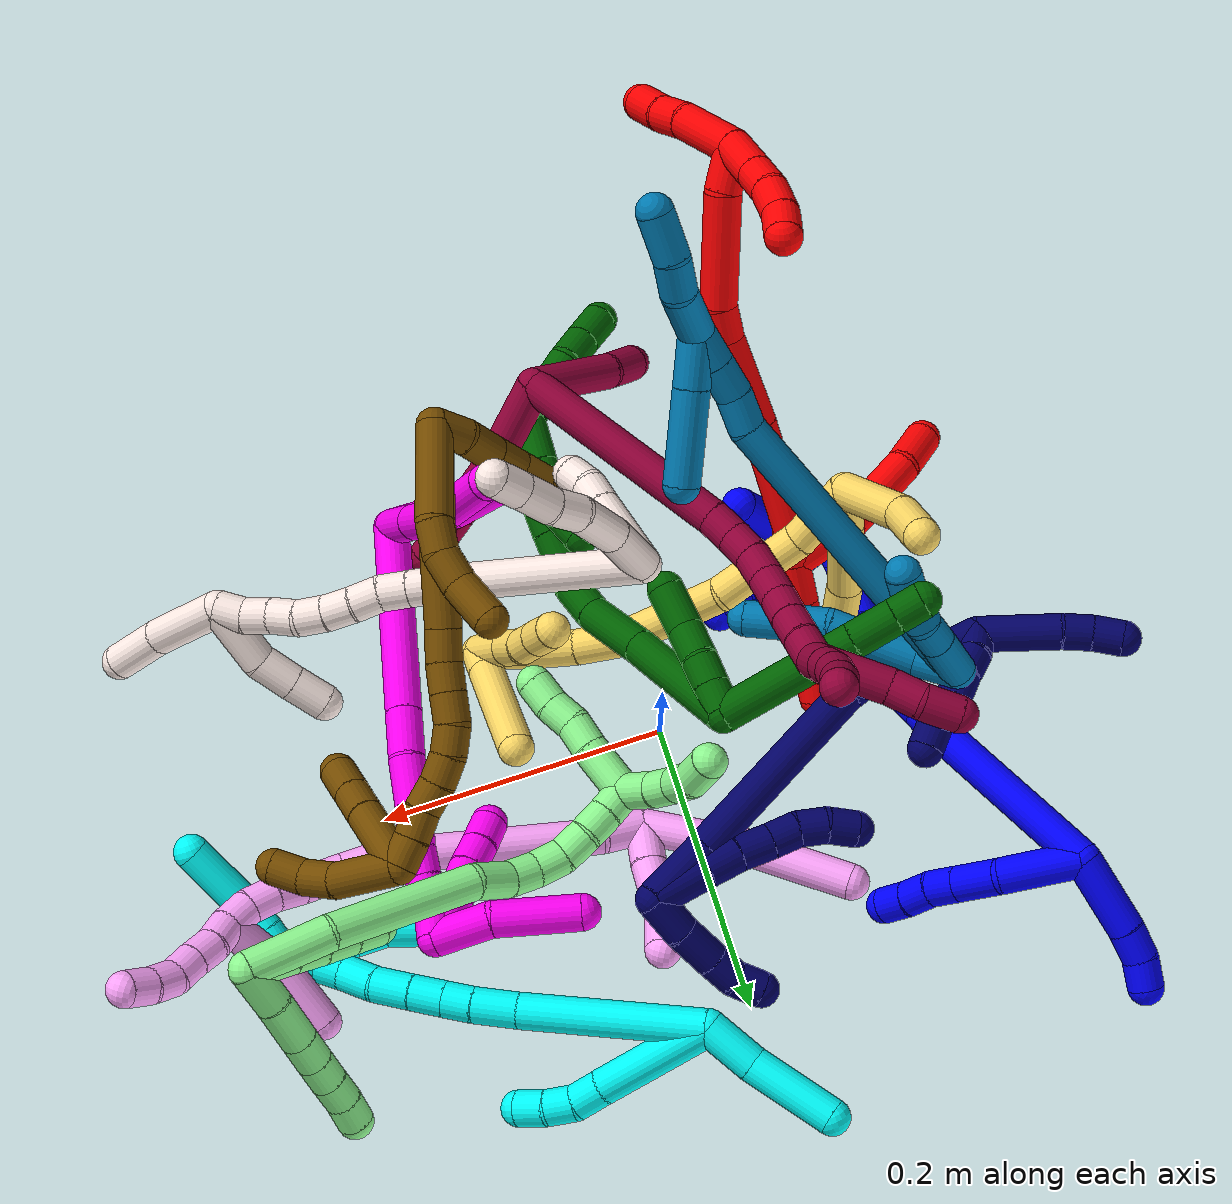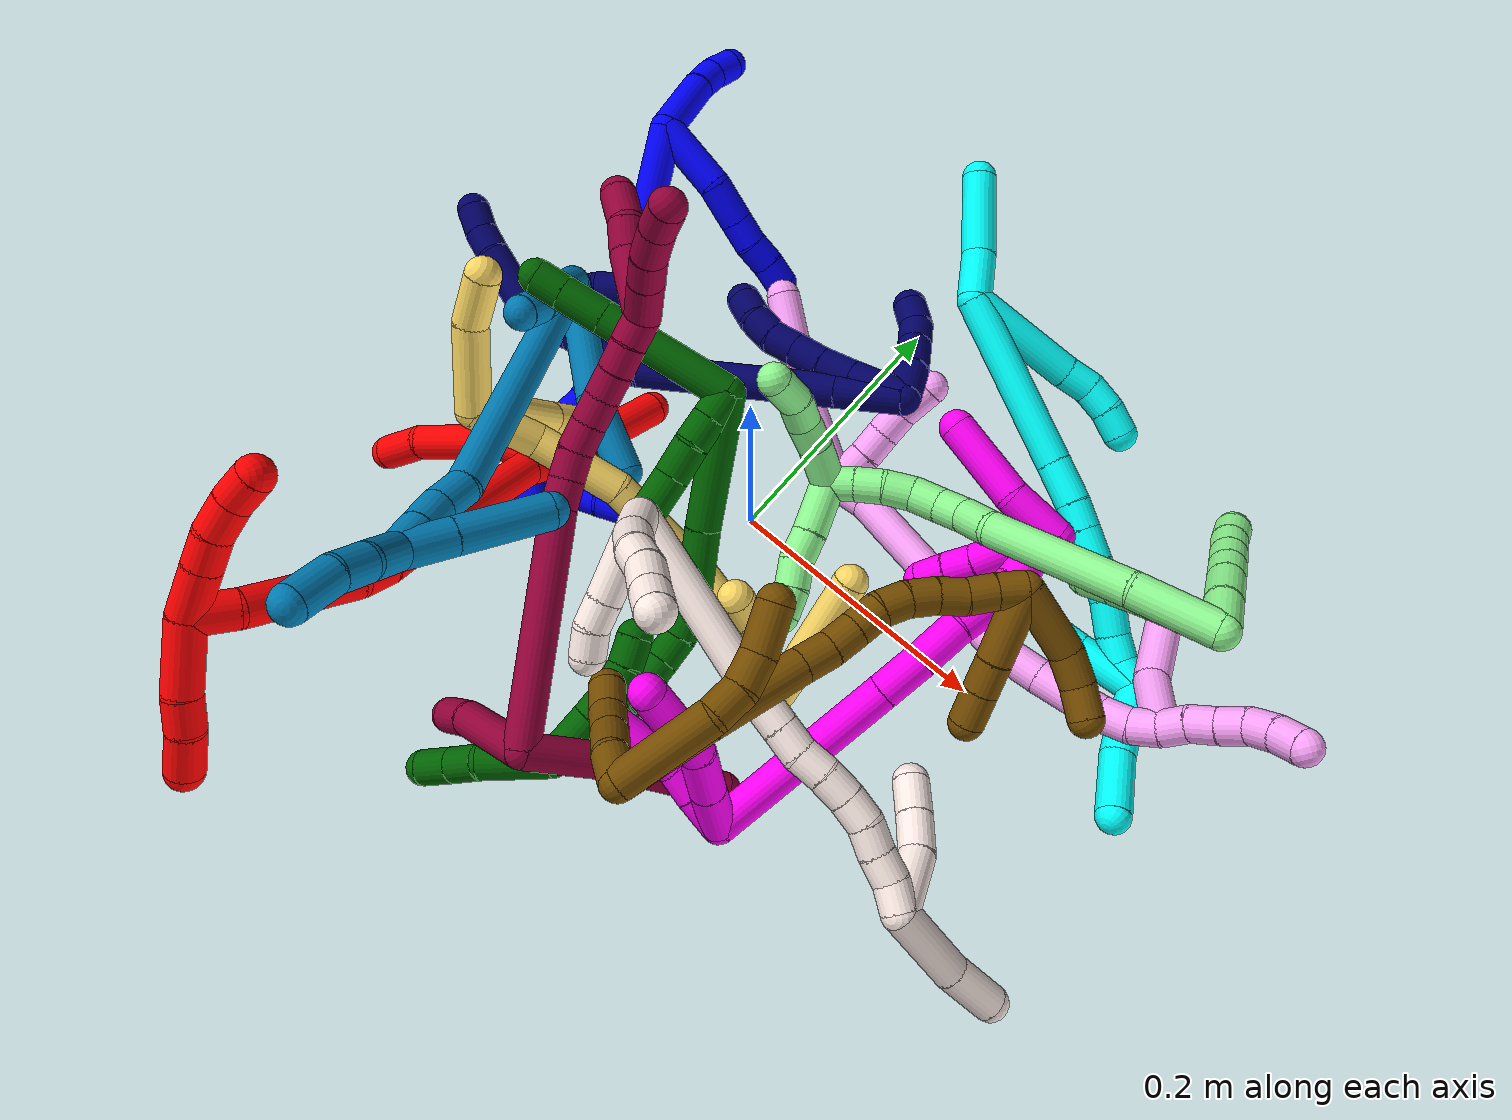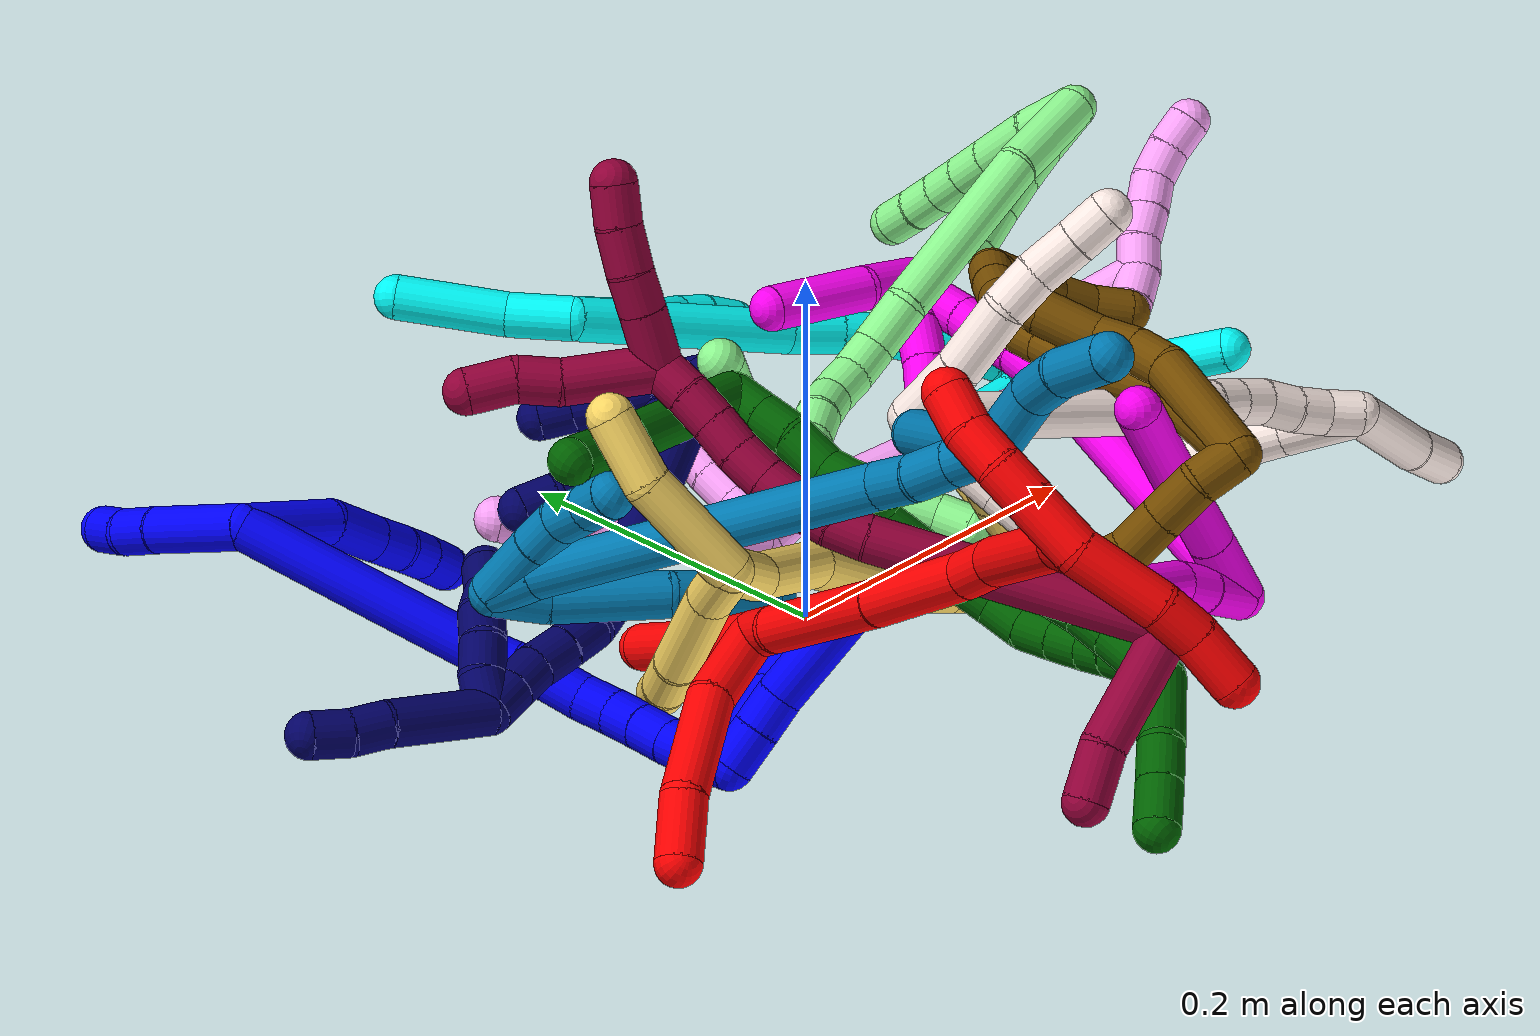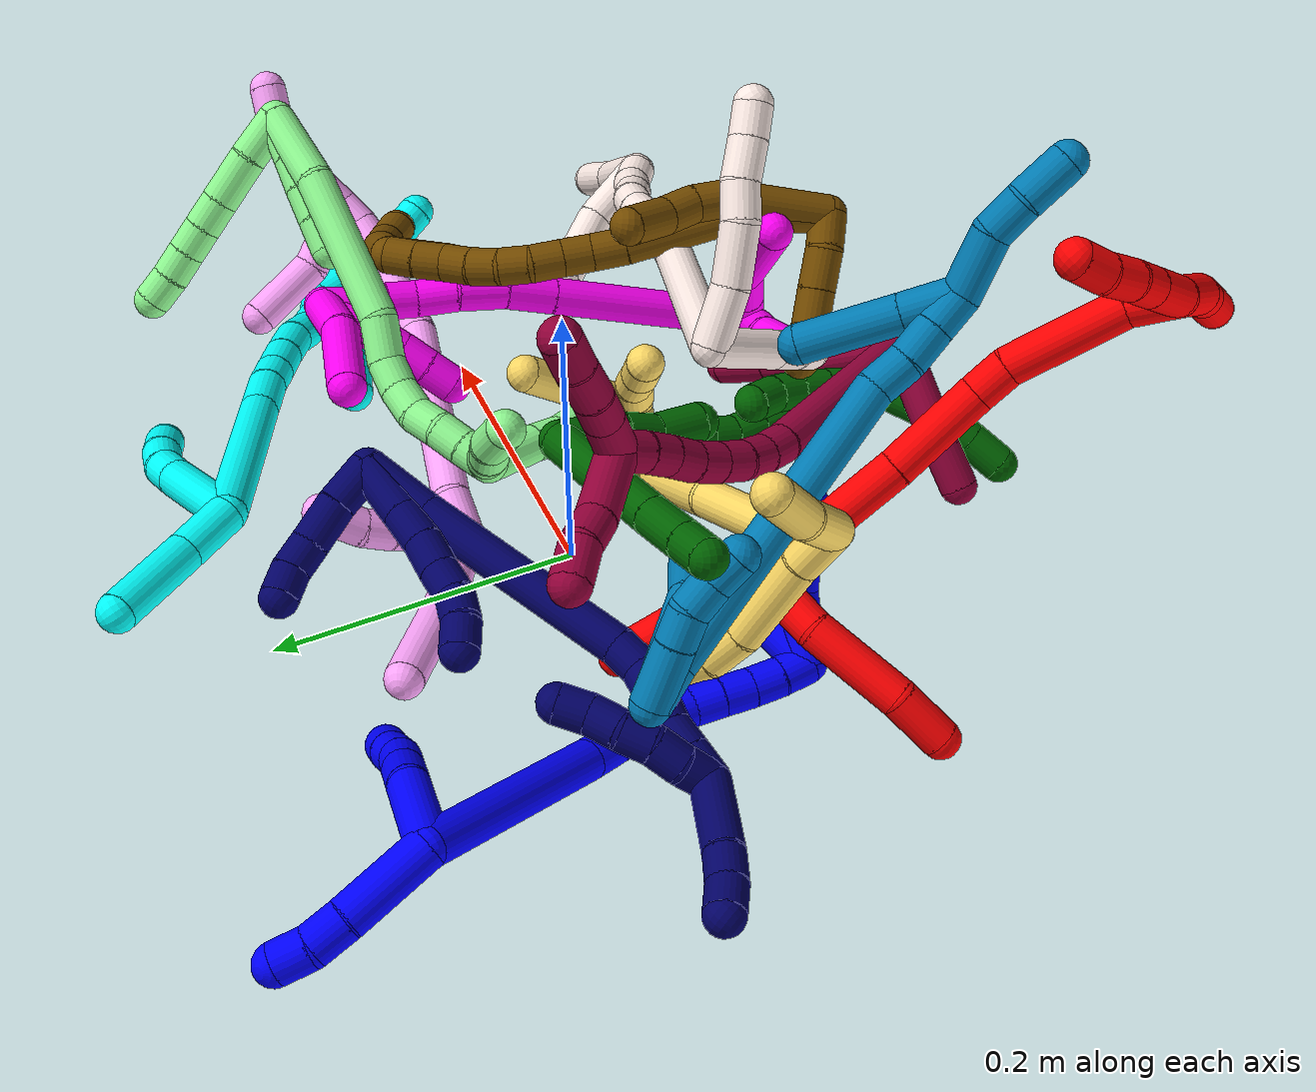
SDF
<sdf version="1.7">
 <world name="default">
  <plugin name="TubeGeneratorPlugin" filename="libtube_generator_plugin.so"/>
  <model name="photoneo_s_sensor">
   <static>1</static>
   <pose>0 0 2 1.57079 1.57079 3.14159</pose>
   <link name="link">
    <inertial><mass>0.1</mass></inertial>
    <sensor name="sensor" type="depth">
     <update_rate>30</update_rate>
     <camera>
      <horizontal_fov>1.22</horizontal_fov>
      <image><width>1920</width><height>1200</height><format>B8G8R8</format></image>
      <clip><near>0.1</near><far>4</far></clip>
      <depth_camera><output>points</output></depth_camera>
     </camera>
     <plugin name="camera_plugin" filename="libgazebo_ros_depth_camera.so">
      <baseline>0.2</baseline>
      <alwaysOn>1</alwaysOn>
      <updateRate>0.0</updateRate>
      <cameraName>camera_ir</cameraName>
      <imageTopicName>/camera/color/image_raw</imageTopicName>
      <cameraInfoTopicName>/camera/color/camera_info</cameraInfoTopicName>
      <depthImageTopicName>/camera/depth/image_raw</depthImageTopicName>
      <depthImageCameraInfoTopicName>/camera/depth/camera_info</depthImageCameraInfoTopicName>
      <pointCloudTopicName>/camera/depth/points</pointCloudTopicName>
      <frameName>fr_optical</frameName>
      <pointCloudCutoff>0.1</pointCloudCutoff>
      <pointCloudCutoffMax>2.0</pointCloudCutoffMax>
      <distortionK1>0</distortionK1>
      <distortionK2>0</distortionK2>
      <distortionK3>0</distortionK3>
      <distortionT1>0</distortionT1>
      <distortionT2>0</distortionT2>
      <CxPrime>0</CxPrime>
      <Cx>0</Cx>
      <Cy>0</Cy>
      <focalLength>0</focalLength>
      <hackBaseline>0</hackBaseline>
     </plugin>
    </sensor>
   </link>
  </model>
  <gravity>0 0 -9.8</gravity>
  <magnetic_field>6e-06 2.3e-05 -4.2e-05</magnetic_field>
  <atmosphere type="adiabatic"/>
  <physics name="default_physics" default="0" type="ode">
   <max_step_size>0.003</max_step_size>
   <real_time_factor>1</real_time_factor>
   <real_time_update_rate>1000</real_time_update_rate>
   <max_contacts>10000</max_contacts>
   <ode>
    <solver>
     <type>quick</type>
     <iters>100</iters>
     <sor>1.3</sor>
     <use_dynamic_moi_rescaling>0</use_dynamic_moi_rescaling>
    </solver>
    <constraints>
     <contact_max_correcting_vel>0</contact_max_correcting_vel>
     <contact_surface_layer>0.001</contact_surface_layer>
     <cfm>0</cfm>
     <erp>0.2</erp>
    </constraints>
   </ode>
  </physics>
  <scene><ambient>0.4 0.4 0.4 1</ambient><background>0.7 0.7 0.7 1</background><shadows>0</shadows></scene>
  <audio><device>default</device></audio>
  <spherical_coordinates>
   <surface_model>EARTH_WGS84</surface_model>
   <latitude_deg>0</latitude_deg>
   <longitude_deg>0</longitude_deg>
   <elevation>0</elevation>
   <heading_deg>0</heading_deg>
  </spherical_coordinates>
  <model name="bin">
   <static>1</static>
   <link name="bottom">
    <collision name="collision-bottom">
     <pose>0 0 -0.01 0 -0 0</pose>
     <geometry><box><size>0.8 0.6 0.02</size></box></geometry>
     <surface>
      <friction><ode><mu>100</mu><mu2>100</mu2></ode></friction>
      <contact><collide_bitmask>65535</collide_bitmask></contact>
     </surface>
    </collision>
   </link>
   <link name="west_wall">
    <collision name="collision-west_wall">
     <pose>-0.41 0 0.1 0 -0 0</pose>
     <geometry><box><size>0.02 0.6 0.2</size></box></geometry>
     <surface>
      <friction><ode><mu>100</mu><mu2>100</mu2></ode></friction>
      <contact><collide_bitmask>65535</collide_bitmask></contact>
     </surface>
    </collision>
   </link>
   <link name="east_wall">
    <collision name="collision-east_wall">
     <pose>0.41 0 0.1 0 -0 0</pose>
     <geometry><box><size>0.02 0.6 0.2</size></box></geometry>
     <surface>
      <friction><ode><mu>100</mu><mu2>100</mu2></ode></friction>
      <contact><collide_bitmask>65535</collide_bitmask></contact>
     </surface>
    </collision>
   </link>
   <link name="south_wall">
    <collision name="collision-south_wall">
     <pose>0 -0.31 0.1 0 -0 0</pose>
     <geometry><box><size>0.8 0.02 0.2</size></box></geometry>
     <surface>
      <friction><ode><mu>100</mu><mu2>100</mu2></ode></friction>
      <contact><collide_bitmask>65535</collide_bitmask></contact>
     </surface>
    </collision>
   </link>
   <link name="north_wall">
    <collision name="collision-north_wall">
     <pose>0 0.31 0.1 0 -0 0</pose>
     <geometry><box><size>0.8 0.02 0.2</size></box></geometry>
     <surface>
      <friction><ode><mu>100</mu><mu2>100</mu2></ode></friction>
      <contact><collide_bitmask>65535</collide_bitmask></contact>
     </surface>
    </collision>
   </link>
  </model>
  <model name="1">
   <static>0</static>
   <link name="1">
    <collision name="collision-cylinder-e_1_2_8">
     <pose>0.011072 0.019899 -0.017059 -2.27952 0.399695 -0.829764</pose>
     <geometry><cylinder><radius>0.0125</radius><length>0.056906</length></cylinder></geometry>
     <surface>
      <friction><ode><mu>1.16</mu><mu2>1.16</mu2><slip1>0</slip1><slip2>0</slip2></ode></friction>
      <contact><ode><kp>1e+06</kp><kd>1</kd><max_vel>0</max_vel><min_depth>0.001</min_depth></ode></contact>
     </surface>
    </collision>
    <visual name="visual-cylinder-e_1_2_8">
     <pose>0.011072 0.019899 -0.017059 -2.27952 0.399695 -0.829764</pose>
     <geometry><cylinder><radius>0.0125</radius><length>0.056906</length></cylinder></geometry>
     <material><ambient>0 0 1 1</ambient></material>
    </visual>
    <collision name="collision-cylinder-e_2_8_9">
     <pose>0.023258 0.051787 -0.044774 -2.29732 0.06935 -0.154162</pose>
     <geometry><cylinder><radius>0.0125</radius><length>0.032158</length></cylinder></geometry>
     <surface>
      <friction><ode><mu>1.16</mu><mu2>1.16</mu2><slip1>0</slip1><slip2>0</slip2></ode></friction>
      <contact><ode><kp>1e+06</kp><kd>1</kd><max_vel>0</max_vel><min_depth>0.001</min_depth></ode></contact>
     </surface>
    </collision>
    <visual name="visual-cylinder-e_2_8_9">
     <pose>0.023258 0.051787 -0.044774 -2.29732 0.06935 -0.154162</pose>
     <geometry><cylinder><radius>0.0125</radius><length>0.032158</length></cylinder></geometry>
     <material><ambient>0 0 1 1</ambient></material>
    </visual>
    <collision name="collision-cylinder-e_3_9_10">
     <pose>0.025401 0.071418 -0.062319 -2.30454 0.099617 -0.223212</pose>
     <geometry><cylinder><radius>0.0125</radius><length>0.02068</length></cylinder></geometry>
     <surface>
      <friction><ode><mu>1.16</mu><mu2>1.16</mu2><slip1>0</slip1><slip2>0</slip2></ode></friction>
      <contact><ode><kp>1e+06</kp><kd>1</kd><max_vel>0</max_vel><min_depth>0.001</min_depth></ode></contact>
     </surface>
    </collision>
    <visual name="visual-cylinder-e_3_9_10">
     <pose>0.025401 0.071418 -0.062319 -2.30454 0.099617 -0.223212</pose>
     <geometry><cylinder><radius>0.0125</radius><length>0.02068</length></cylinder></geometry>
     <material><ambient>0 0 1 1</ambient></material>
    </visual>
    <collision name="collision-cylinder-e_4_10_11">
     <pose>0.026943 0.087725 -0.074418 -2.11209 0.050753 -0.08969</pose>
     <geometry><cylinder><radius>0.0125</radius><length>0.020248</length></cylinder></geometry>
     <surface>
      <friction><ode><mu>1.16</mu><mu2>1.16</mu2><slip1>0</slip1><slip2>0</slip2></ode></friction>
      <contact><ode><kp>1e+06</kp><kd>1</kd><max_vel>0</max_vel><min_depth>0.001</min_depth></ode></contact>
     </surface>
    </collision>
    <visual name="visual-cylinder-e_4_10_11">
     <pose>0.026943 0.087725 -0.074418 -2.11209 0.050753 -0.08969</pose>
     <geometry><cylinder><radius>0.0125</radius><length>0.020248</length></cylinder></geometry>
     <material><ambient>0 0 1 1</ambient></material>
    </visual>
    <collision name="collision-cylinder-e_5_11_6">
     <pose>0.027587 0.104357 -0.085677 -2.22018 0.013015 -0.026221</pose>
     <geometry><cylinder><radius>0.0125</radius><length>0.020009</length></cylinder></geometry>
     <surface>
      <friction><ode><mu>1.16</mu><mu2>1.16</mu2><slip1>0</slip1><slip2>0</slip2></ode></friction>
      <contact><ode><kp>1e+06</kp><kd>1</kd><max_vel>0</max_vel><min_depth>0.001</min_depth></ode></contact>
     </surface>
    </collision>
    <visual name="visual-cylinder-e_5_11_6">
     <pose>0.027587 0.104357 -0.085677 -2.22018 0.013015 -0.026221</pose>
     <geometry><cylinder><radius>0.0125</radius><length>0.020009</length></cylinder></geometry>
     <material><ambient>0 0 1 1</ambient></material>
    </visual>
    <collision name="collision-cylinder-e_1_2_12">
     <pose>-0.011391 0.013854 0.021915 -0.563725 -0.413978 0.121469</pose>
     <geometry><cylinder><radius>0.0125</radius><length>0.056637</length></cylinder></geometry>
     <surface>
      <friction><ode><mu>1.16</mu><mu2>1.16</mu2><slip1>0</slip1><slip2>0</slip2></ode></friction>
      <contact><ode><kp>1e+06</kp><kd>1</kd><max_vel>0</max_vel><min_depth>0.001</min_depth></ode></contact>
     </surface>
    </collision>
    <visual name="visual-cylinder-e_1_2_12">
     <pose>-0.011391 0.013854 0.021915 -0.563725 -0.413978 0.121469</pose>
     <geometry><cylinder><radius>0.0125</radius><length>0.056637</length></cylinder></geometry>
     <material><ambient>0 0 1 1</ambient></material>
    </visual>
    <collision name="collision-cylinder-e_2_12_13">
     <pose>-0.027215 0.034308 0.051926 -0.684015 -0.401277 0.14455</pose>
     <geometry><cylinder><radius>0.0125</radius><length>0.022695</length></cylinder></geometry>
     <surface>
      <friction><ode><mu>1.16</mu><mu2>1.16</mu2><slip1>0</slip1><slip2>0</slip2></ode></friction>
      <contact><ode><kp>1e+06</kp><kd>1</kd><max_vel>0</max_vel><min_depth>0.001</min_depth></ode></contact>
     </surface>
    </collision>
    <visual name="visual-cylinder-e_2_12_13">
     <pose>-0.027215 0.034308 0.051926 -0.684015 -0.401277 0.14455</pose>
     <geometry><cylinder><radius>0.0125</radius><length>0.022695</length></cylinder></geometry>
     <material><ambient>0 0 1 1</ambient></material>
    </visual>
    <collision name="collision-cylinder-e_3_13_5">
     <pose>-0.033746 0.048589 0.066611 -0.861714 -0.204538 0.094277</pose>
     <geometry><cylinder><radius>0.0125</radius><length>0.020667</length></cylinder></geometry>
     <surface>
      <friction><ode><mu>1.16</mu><mu2>1.16</mu2><slip1>0</slip1><slip2>0</slip2></ode></friction>
      <contact><ode><kp>1e+06</kp><kd>1</kd><max_vel>0</max_vel><min_depth>0.001</min_depth></ode></contact>
     </surface>
    </collision>
    <visual name="visual-cylinder-e_3_13_5">
     <pose>-0.033746 0.048589 0.066611 -0.861714 -0.204538 0.094277</pose>
     <geometry><cylinder><radius>0.0125</radius><length>0.020667</length></cylinder></geometry>
     <material><ambient>0 0 1 1</ambient></material>
    </visual>
    <collision name="collision-cylinder-e_1_2_14">
     <pose>-0.000697 0.000275 -0.0688 -3.13759 -0.010128 2.38857</pose>
     <geometry><cylinder><radius>0.0125</radius><length>0.137607</length></cylinder></geometry>
     <surface>
      <friction><ode><mu>1.16</mu><mu2>1.16</mu2><slip1>0</slip1><slip2>0</slip2></ode></friction>
      <contact><ode><kp>1e+06</kp><kd>1</kd><max_vel>0</max_vel><min_depth>0.001</min_depth></ode></contact>
     </surface>
    </collision>
    <visual name="visual-cylinder-e_1_2_14">
     <pose>-0.000697 0.000275 -0.0688 -3.13759 -0.010128 2.38857</pose>
     <geometry><cylinder><radius>0.0125</radius><length>0.137607</length></cylinder></geometry>
     <material><ambient>0 0 1 1</ambient></material>
    </visual>
    <collision name="collision-cylinder-e_2_14_15">
     <pose>-0.000426 -0.001012 -0.148116 2.99407 0.090804 1.10249</pose>
     <geometry><cylinder><radius>0.0125</radius><length>0.021352</length></cylinder></geometry>
     <surface>
      <friction><ode><mu>1.16</mu><mu2>1.16</mu2><slip1>0</slip1><slip2>0</slip2></ode></friction>
      <contact><ode><kp>1e+06</kp><kd>1</kd><max_vel>0</max_vel><min_depth>0.001</min_depth></ode></contact>
     </surface>
    </collision>
    <visual name="visual-cylinder-e_2_14_15">
     <pose>-0.000426 -0.001012 -0.148116 2.99407 0.090804 1.10249</pose>
     <geometry><cylinder><radius>0.0125</radius><length>0.021352</length></cylinder></geometry>
     <material><ambient>0 0 1 1</ambient></material>
    </visual>
    <collision name="collision-cylinder-e_3_15_16">
     <pose>0.001505 -0.003632 -0.168707 3.03705 0.09473 1.47226</pose>
     <geometry><cylinder><radius>0.0125</radius><length>0.020352</length></cylinder></geometry>
     <surface>
      <friction><ode><mu>1.16</mu><mu2>1.16</mu2><slip1>0</slip1><slip2>0</slip2></ode></friction>
      <contact><ode><kp>1e+06</kp><kd>1</kd><max_vel>0</max_vel><min_depth>0.001</min_depth></ode></contact>
     </surface>
    </collision>
    <visual name="visual-cylinder-e_3_15_16">
     <pose>0.001505 -0.003632 -0.168707 3.03705 0.09473 1.47226</pose>
     <geometry><cylinder><radius>0.0125</radius><length>0.020352</length></cylinder></geometry>
     <material><ambient>0 0 1 1</ambient></material>
    </visual>
    <collision name="collision-cylinder-e_4_16_17">
     <pose>0.002036 -0.006709 -0.18887 2.94392 -0.041924 -0.416722</pose>
     <geometry><cylinder><radius>0.0125</radius><length>0.020592</length></cylinder></geometry>
     <surface>
      <friction><ode><mu>1.16</mu><mu2>1.16</mu2><slip1>0</slip1><slip2>0</slip2></ode></friction>
      <contact><ode><kp>1e+06</kp><kd>1</kd><max_vel>0</max_vel><min_depth>0.001</min_depth></ode></contact>
     </surface>
    </collision>
    <visual name="visual-cylinder-e_4_16_17">
     <pose>0.002036 -0.006709 -0.18887 2.94392 -0.041924 -0.416722</pose>
     <geometry><cylinder><radius>0.0125</radius><length>0.020592</length></cylinder></geometry>
     <material><ambient>0 0 1 1</ambient></material>
    </visual>
    <collision name="collision-cylinder-e_5_17_18">
     <pose>0.001974 -0.012525 -0.208251 2.75385 0.036771 0.186765</pose>
     <geometry><cylinder><radius>0.0125</radius><length>0.020093</length></cylinder></geometry>
     <surface>
      <friction><ode><mu>1.16</mu><mu2>1.16</mu2><slip1>0</slip1><slip2>0</slip2></ode></friction>
      <contact><ode><kp>1e+06</kp><kd>1</kd><max_vel>0</max_vel><min_depth>0.001</min_depth></ode></contact>
     </surface>
    </collision>
    <visual name="visual-cylinder-e_5_17_18">
     <pose>0.001974 -0.012525 -0.208251 2.75385 0.036771 0.186765</pose>
     <geometry><cylinder><radius>0.0125</radius><length>0.020093</length></cylinder></geometry>
     <material><ambient>0 0 1 1</ambient></material>
    </visual>
    <collision name="collision-cylinder-e_6_18_19">
     <pose>0.002441 -0.021968 -0.225799 2.54161 0.009735 0.031469</pose>
     <geometry><cylinder><radius>0.0125</radius><length>0.020001</length></cylinder></geometry>
     <surface>
      <friction><ode><mu>1.16</mu><mu2>1.16</mu2><slip1>0</slip1><slip2>0</slip2></ode></friction>
      <contact><ode><kp>1e+06</kp><kd>1</kd><max_vel>0</max_vel><min_depth>0.001</min_depth></ode></contact>
     </surface>
    </collision>
    <visual name="visual-cylinder-e_6_18_19">
     <pose>0.002441 -0.021968 -0.225799 2.54161 0.009735 0.031469</pose>
     <geometry><cylinder><radius>0.0125</radius><length>0.020001</length></cylinder></geometry>
     <material><ambient>0 0 1 1</ambient></material>
    </visual>
    <collision name="collision-cylinder-e_7_19_20">
     <pose>0.002386 -0.032966 -0.242499 2.57681 -0.015167 -0.052264</pose>
     <geometry><cylinder><radius>0.0125</radius><length>0.020001</length></cylinder></geometry>
     <surface>
      <friction><ode><mu>1.16</mu><mu2>1.16</mu2><slip1>0</slip1><slip2>0</slip2></ode></friction>
      <contact><ode><kp>1e+06</kp><kd>1</kd><max_vel>0</max_vel><min_depth>0.001</min_depth></ode></contact>
     </surface>
    </collision>
    <visual name="visual-cylinder-e_7_19_20">
     <pose>0.002386 -0.032966 -0.242499 2.57681 -0.015167 -0.052264</pose>
     <geometry><cylinder><radius>0.0125</radius><length>0.020001</length></cylinder></geometry>
     <material><ambient>0 0 1 1</ambient></material>
    </visual>
    <collision name="collision-cylinder-e_8_20_21">
     <pose>0.002649 -0.04371 -0.259356 2.5715 0.041435 0.141191</pose>
     <geometry><cylinder><radius>0.0125</radius><length>0.02</length></cylinder></geometry>
     <surface>
      <friction><ode><mu>1.16</mu><mu2>1.16</mu2><slip1>0</slip1><slip2>0</slip2></ode></friction>
      <contact><ode><kp>1e+06</kp><kd>1</kd><max_vel>0</max_vel><min_depth>0.001</min_depth></ode></contact>
     </surface>
    </collision>
    <visual name="visual-cylinder-e_8_20_21">
     <pose>0.002649 -0.04371 -0.259356 2.5715 0.041435 0.141191</pose>
     <geometry><cylinder><radius>0.0125</radius><length>0.02</length></cylinder></geometry>
     <material><ambient>0 0 1 1</ambient></material>
    </visual>
    <collision name="collision-cylinder-e_9_21_1">
     <pose>0.004263 -0.053944 -0.276436 2.63225 0.120269 0.454569</pose>
     <geometry><cylinder><radius>0.0125</radius><length>0.020001</length></cylinder></geometry>
     <surface>
      <friction><ode><mu>1.16</mu><mu2>1.16</mu2><slip1>0</slip1><slip2>0</slip2></ode></friction>
      <contact><ode><kp>1e+06</kp><kd>1</kd><max_vel>0</max_vel><min_depth>0.001</min_depth></ode></contact>
     </surface>
    </collision>
    <visual name="visual-cylinder-e_9_21_1">
     <pose>0.004263 -0.053944 -0.276436 2.63225 0.120269 0.454569</pose>
     <geometry><cylinder><radius>0.0125</radius><length>0.020001</length></cylinder></geometry>
     <material><ambient>0 0 1 1</ambient></material>
    </visual>
    <collision name="collision-cylinder-e_1_1_22">
     <pose>0.016939 -0.05924 -0.286829 2.8835 1.41657 2.84088</pose>
     <geometry><cylinder><radius>0.0125</radius><length>0.023228</length></cylinder></geometry>
     <surface>
      <friction><ode><mu>1.16</mu><mu2>1.16</mu2><slip1>0</slip1><slip2>0</slip2></ode></friction>
      <contact><ode><kp>1e+06</kp><kd>1</kd><max_vel>0</max_vel><min_depth>0.001</min_depth></ode></contact>
     </surface>
    </collision>
    <visual name="visual-cylinder-e_1_1_22">
     <pose>0.016939 -0.05924 -0.286829 2.8835 1.41657 2.84088</pose>
     <geometry><cylinder><radius>0.0125</radius><length>0.023228</length></cylinder></geometry>
     <material><ambient>0 0 1 1</ambient></material>
    </visual>
    <collision name="collision-cylinder-e_2_22_23">
     <pose>0.038958 -0.059877 -0.289981 3.01482 1.43516 2.99641</pose>
     <geometry><cylinder><radius>0.0125</radius><length>0.021281</length></cylinder></geometry>
     <surface>
      <friction><ode><mu>1.16</mu><mu2>1.16</mu2><slip1>0</slip1><slip2>0</slip2></ode></friction>
      <contact><ode><kp>1e+06</kp><kd>1</kd><max_vel>0</max_vel><min_depth>0.001</min_depth></ode></contact>
     </surface>
    </collision>
    <visual name="visual-cylinder-e_2_22_23">
     <pose>0.038958 -0.059877 -0.289981 3.01482 1.43516 2.99641</pose>
     <geometry><cylinder><radius>0.0125</radius><length>0.021281</length></cylinder></geometry>
     <material><ambient>0 0 1 1</ambient></material>
    </visual>
    <collision name="collision-cylinder-e_3_23_4">
     <pose>0.075591 -0.067113 -0.297683 2.29785 1.22361 2.00339</pose>
     <geometry><cylinder><radius>0.0125</radius><length>0.055491</length></cylinder></geometry>
     <surface>
      <friction><ode><mu>1.16</mu><mu2>1.16</mu2><slip1>0</slip1><slip2>0</slip2></ode></friction>
      <contact><ode><kp>1e+06</kp><kd>1</kd><max_vel>0</max_vel><min_depth>0.001</min_depth></ode></contact>
     </surface>
    </collision>
    <visual name="visual-cylinder-e_3_23_4">
     <pose>0.075591 -0.067113 -0.297683 2.29785 1.22361 2.00339</pose>
     <geometry><cylinder><radius>0.0125</radius><length>0.055491</length></cylinder></geometry>
     <material><ambient>0 0 1 1</ambient></material>
    </visual>
    <collision name="collision-cylinder-e_1_1_24">
     <pose>0.027214 -0.0408 -0.284874 -1.55801 0.879852 -0.870039</pose>
     <geometry><cylinder><radius>0.0125</radius><length>0.056448</length></cylinder></geometry>
     <surface>
      <friction><ode><mu>1.16</mu><mu2>1.16</mu2><slip1>0</slip1><slip2>0</slip2></ode></friction>
      <contact><ode><kp>1e+06</kp><kd>1</kd><max_vel>0</max_vel><min_depth>0.001</min_depth></ode></contact>
     </surface>
    </collision>
    <visual name="visual-cylinder-e_1_1_24">
     <pose>0.027214 -0.0408 -0.284874 -1.55801 0.879852 -0.870039</pose>
     <geometry><cylinder><radius>0.0125</radius><length>0.056448</length></cylinder></geometry>
     <material><ambient>0 0 1 1</ambient></material>
    </visual>
    <collision name="collision-cylinder-e_2_24_25">
     <pose>0.057771 -0.016994 -0.285392 -1.69864 0.982995 -1.09333</pose>
     <geometry><cylinder><radius>0.0125</radius><length>0.021166</length></cylinder></geometry>
     <surface>
      <friction><ode><mu>1.16</mu><mu2>1.16</mu2><slip1>0</slip1><slip2>0</slip2></ode></friction>
      <contact><ode><kp>1e+06</kp><kd>1</kd><max_vel>0</max_vel><min_depth>0.001</min_depth></ode></contact>
     </surface>
    </collision>
    <visual name="visual-cylinder-e_2_24_25">
     <pose>0.057771 -0.016994 -0.285392 -1.69864 0.982995 -1.09333</pose>
     <geometry><cylinder><radius>0.0125</radius><length>0.021166</length></cylinder></geometry>
     <material><ambient>0 0 1 1</ambient></material>
    </visual>
    <collision name="collision-cylinder-e_3_25_3">
     <pose>0.074292 -0.003099 -0.286889 -1.66322 0.760431 -0.826363</pose>
     <geometry><cylinder><radius>0.0125</radius><length>0.022385</length></cylinder></geometry>
     <surface>
      <friction><ode><mu>1.16</mu><mu2>1.16</mu2><slip1>0</slip1><slip2>0</slip2></ode></friction>
      <contact><ode><kp>1e+06</kp><kd>1</kd><max_vel>0</max_vel><min_depth>0.001</min_depth></ode></contact>
     </surface>
    </collision>
    <visual name="visual-cylinder-e_3_25_3">
     <pose>0.074292 -0.003099 -0.286889 -1.66322 0.760431 -0.826363</pose>
     <geometry><cylinder><radius>0.0125</radius><length>0.022385</length></cylinder></geometry>
     <material><ambient>0 0 1 1</ambient></material>
    </visual>
    <collision name="collision-sphere-3">
     <pose>0.082007 0.004976 -0.287637 0 -0 0</pose>
     <geometry><sphere><radius>0.0125</radius></sphere></geometry>
     <surface>
      <friction><ode><mu>1.16</mu><mu2>1.16</mu2><slip1>0</slip1><slip2>0</slip2></ode></friction>
      <contact><ode><kp>1e+06</kp><kd>1</kd><max_vel>0</max_vel><min_depth>0.001</min_depth></ode></contact>
     </surface>
    </collision>
    <visual name="visual-sphere-3">
     <pose>0.082007 0.004976 -0.287637 0 -0 0</pose>
     <geometry><sphere><radius>0.0125</radius></sphere></geometry>
     <material><ambient>0 0 1 1</ambient></material>
    </visual>
    <collision name="collision-sphere-25">
     <pose>0.066578 -0.011174 -0.28614 0 -0 0</pose>
     <geometry><sphere><radius>0.0125</radius></sphere></geometry>
     <surface>
      <friction><ode><mu>1.16</mu><mu2>1.16</mu2><slip1>0</slip1><slip2>0</slip2></ode></friction>
      <contact><ode><kp>1e+06</kp><kd>1</kd><max_vel>0</max_vel><min_depth>0.001</min_depth></ode></contact>
     </surface>
    </collision>
    <visual name="visual-sphere-25">
     <pose>0.066578 -0.011174 -0.28614 0 -0 0</pose>
     <geometry><sphere><radius>0.0125</radius></sphere></geometry>
     <material><ambient>0 0 1 1</ambient></material>
    </visual>
    <collision name="collision-sphere-24">
     <pose>0.048964 -0.022815 -0.284644 0 -0 0</pose>
     <geometry><sphere><radius>0.0125</radius></sphere></geometry>
     <surface>
      <friction><ode><mu>1.16</mu><mu2>1.16</mu2><slip1>0</slip1><slip2>0</slip2></ode></friction>
      <contact><ode><kp>1e+06</kp><kd>1</kd><max_vel>0</max_vel><min_depth>0.001</min_depth></ode></contact>
     </surface>
    </collision>
    <visual name="visual-sphere-24">
     <pose>0.048964 -0.022815 -0.284644 0 -0 0</pose>
     <geometry><sphere><radius>0.0125</radius></sphere></geometry>
     <material><ambient>0 0 1 1</ambient></material>
    </visual>
    <collision name="collision-sphere-4">
     <pose>0.101681 -0.074166 -0.303958 0 -0 0</pose>
     <geometry><sphere><radius>0.0125</radius></sphere></geometry>
     <surface>
      <friction><ode><mu>1.16</mu><mu2>1.16</mu2><slip1>0</slip1><slip2>0</slip2></ode></friction>
      <contact><ode><kp>1e+06</kp><kd>1</kd><max_vel>0</max_vel><min_depth>0.001</min_depth></ode></contact>
     </surface>
    </collision>
    <visual name="visual-sphere-4">
     <pose>0.101681 -0.074166 -0.303958 0 -0 0</pose>
     <geometry><sphere><radius>0.0125</radius></sphere></geometry>
     <material><ambient>0 0 1 1</ambient></material>
    </visual>
    <collision name="collision-sphere-23">
     <pose>0.049501 -0.060059 -0.291408 0 -0 0</pose>
     <geometry><sphere><radius>0.0125</radius></sphere></geometry>
     <surface>
      <friction><ode><mu>1.16</mu><mu2>1.16</mu2><slip1>0</slip1><slip2>0</slip2></ode></friction>
      <contact><ode><kp>1e+06</kp><kd>1</kd><max_vel>0</max_vel><min_depth>0.001</min_depth></ode></contact>
     </surface>
    </collision>
    <visual name="visual-sphere-23">
     <pose>0.049501 -0.060059 -0.291408 0 -0 0</pose>
     <geometry><sphere><radius>0.0125</radius></sphere></geometry>
     <material><ambient>0 0 1 1</ambient></material>
    </visual>
    <collision name="collision-sphere-22">
     <pose>0.028415 -0.059695 -0.288554 0 -0 0</pose>
     <geometry><sphere><radius>0.0125</radius></sphere></geometry>
     <surface>
      <friction><ode><mu>1.16</mu><mu2>1.16</mu2><slip1>0</slip1><slip2>0</slip2></ode></friction>
      <contact><ode><kp>1e+06</kp><kd>1</kd><max_vel>0</max_vel><min_depth>0.001</min_depth></ode></contact>
     </surface>
    </collision>
    <visual name="visual-sphere-22">
     <pose>0.028415 -0.059695 -0.288554 0 -0 0</pose>
     <geometry><sphere><radius>0.0125</radius></sphere></geometry>
     <material><ambient>0 0 1 1</ambient></material>
    </visual>
    <collision name="collision-sphere-1">
     <pose>0.005463 -0.058785 -0.285104 0 -0 0</pose>
     <geometry><sphere><radius>0.0125</radius></sphere></geometry>
     <surface>
      <friction><ode><mu>1.16</mu><mu2>1.16</mu2><slip1>0</slip1><slip2>0</slip2></ode></friction>
      <contact><ode><kp>1e+06</kp><kd>1</kd><max_vel>0</max_vel><min_depth>0.001</min_depth></ode></contact>
     </surface>
    </collision>
    <visual name="visual-sphere-1">
     <pose>0.005463 -0.058785 -0.285104 0 -0 0</pose>
     <geometry><sphere><radius>0.0125</radius></sphere></geometry>
     <material><ambient>0 0 1 1</ambient></material>
    </visual>
    <collision name="collision-sphere-21">
     <pose>0.003063 -0.049103 -0.267768 0 -0 0</pose>
     <geometry><sphere><radius>0.0125</radius></sphere></geometry>
     <surface>
      <friction><ode><mu>1.16</mu><mu2>1.16</mu2><slip1>0</slip1><slip2>0</slip2></ode></friction>
      <contact><ode><kp>1e+06</kp><kd>1</kd><max_vel>0</max_vel><min_depth>0.001</min_depth></ode></contact>
     </surface>
    </collision>
    <visual name="visual-sphere-21">
     <pose>0.003063 -0.049103 -0.267768 0 -0 0</pose>
     <geometry><sphere><radius>0.0125</radius></sphere></geometry>
     <material><ambient>0 0 1 1</ambient></material>
    </visual>
    <collision name="collision-sphere-6">
     <pose>0.027717 0.112325 -0.091726 0 -0 0</pose>
     <geometry><sphere><radius>0.0125</radius></sphere></geometry>
     <surface>
      <friction><ode><mu>1.16</mu><mu2>1.16</mu2><slip1>0</slip1><slip2>0</slip2></ode></friction>
      <contact><ode><kp>1e+06</kp><kd>1</kd><max_vel>0</max_vel><min_depth>0.001</min_depth></ode></contact>
     </surface>
    </collision>
    <visual name="visual-sphere-6">
     <pose>0.027717 0.112325 -0.091726 0 -0 0</pose>
     <geometry><sphere><radius>0.0125</radius></sphere></geometry>
     <material><ambient>0 0 1 1</ambient></material>
    </visual>
    <collision name="collision-sphere-11">
     <pose>0.027456 0.09639 -0.079628 0 -0 0</pose>
     <geometry><sphere><radius>0.0125</radius></sphere></geometry>
     <surface>
      <friction><ode><mu>1.16</mu><mu2>1.16</mu2><slip1>0</slip1><slip2>0</slip2></ode></friction>
      <contact><ode><kp>1e+06</kp><kd>1</kd><max_vel>0</max_vel><min_depth>0.001</min_depth></ode></contact>
     </surface>
    </collision>
    <visual name="visual-sphere-11">
     <pose>0.027456 0.09639 -0.079628 0 -0 0</pose>
     <geometry><sphere><radius>0.0125</radius></sphere></geometry>
     <material><ambient>0 0 1 1</ambient></material>
    </visual>
    <collision name="collision-sphere-10">
     <pose>0.026429 0.079059 -0.069209 0 -0 0</pose>
     <geometry><sphere><radius>0.0125</radius></sphere></geometry>
     <surface>
      <friction><ode><mu>1.16</mu><mu2>1.16</mu2><slip1>0</slip1><slip2>0</slip2></ode></friction>
      <contact><ode><kp>1e+06</kp><kd>1</kd><max_vel>0</max_vel><min_depth>0.001</min_depth></ode></contact>
     </surface>
    </collision>
    <visual name="visual-sphere-10">
     <pose>0.026429 0.079059 -0.069209 0 -0 0</pose>
     <geometry><sphere><radius>0.0125</radius></sphere></geometry>
     <material><ambient>0 0 1 1</ambient></material>
    </visual>
    <collision name="collision-sphere-9">
     <pose>0.024372 0.063777 -0.055429 0 -0 0</pose>
     <geometry><sphere><radius>0.0125</radius></sphere></geometry>
     <surface>
      <friction><ode><mu>1.16</mu><mu2>1.16</mu2><slip1>0</slip1><slip2>0</slip2></ode></friction>
      <contact><ode><kp>1e+06</kp><kd>1</kd><max_vel>0</max_vel><min_depth>0.001</min_depth></ode></contact>
     </surface>
    </collision>
    <visual name="visual-sphere-9">
     <pose>0.024372 0.063777 -0.055429 0 -0 0</pose>
     <geometry><sphere><radius>0.0125</radius></sphere></geometry>
     <material><ambient>0 0 1 1</ambient></material>
    </visual>
    <collision name="collision-sphere-2">
     <geometry><sphere><radius>0.0125</radius></sphere></geometry>
     <surface>
      <friction><ode><mu>1.16</mu><mu2>1.16</mu2><slip1>0</slip1><slip2>0</slip2></ode></friction>
      <contact><ode><kp>1e+06</kp><kd>1</kd><max_vel>0</max_vel><min_depth>0.001</min_depth></ode></contact>
     </surface>
    </collision>
    <visual name="visual-sphere-2">
     <geometry><sphere><radius>0.0125</radius></sphere></geometry>
     <material><ambient>0 0 1 1</ambient></material>
    </visual>
    <collision name="collision-sphere-19">
     <pose>0.002538 -0.027614 -0.234052 0 -0 0</pose>
     <geometry><sphere><radius>0.0125</radius></sphere></geometry>
     <surface>
      <friction><ode><mu>1.16</mu><mu2>1.16</mu2><slip1>0</slip1><slip2>0</slip2></ode></friction>
      <contact><ode><kp>1e+06</kp><kd>1</kd><max_vel>0</max_vel><min_depth>0.001</min_depth></ode></contact>
     </surface>
    </collision>
    <visual name="visual-sphere-19">
     <pose>0.002538 -0.027614 -0.234052 0 -0 0</pose>
     <geometry><sphere><radius>0.0125</radius></sphere></geometry>
     <material><ambient>0 0 1 1</ambient></material>
    </visual>
    <collision name="collision-sphere-8">
     <pose>0.022144 0.039797 -0.034119 0 -0 0</pose>
     <geometry><sphere><radius>0.0125</radius></sphere></geometry>
     <surface>
      <friction><ode><mu>1.16</mu><mu2>1.16</mu2><slip1>0</slip1><slip2>0</slip2></ode></friction>
      <contact><ode><kp>1e+06</kp><kd>1</kd><max_vel>0</max_vel><min_depth>0.001</min_depth></ode></contact>
     </surface>
    </collision>
    <visual name="visual-sphere-8">
     <pose>0.022144 0.039797 -0.034119 0 -0 0</pose>
     <geometry><sphere><radius>0.0125</radius></sphere></geometry>
     <material><ambient>0 0 1 1</ambient></material>
    </visual>
    <collision name="collision-sphere-12">
     <pose>-0.022783 0.027707 0.04383 0 -0 0</pose>
     <geometry><sphere><radius>0.0125</radius></sphere></geometry>
     <surface>
      <friction><ode><mu>1.16</mu><mu2>1.16</mu2><slip1>0</slip1><slip2>0</slip2></ode></friction>
      <contact><ode><kp>1e+06</kp><kd>1</kd><max_vel>0</max_vel><min_depth>0.001</min_depth></ode></contact>
     </surface>
    </collision>
    <visual name="visual-sphere-12">
     <pose>-0.022783 0.027707 0.04383 0 -0 0</pose>
     <geometry><sphere><radius>0.0125</radius></sphere></geometry>
     <material><ambient>0 0 1 1</ambient></material>
    </visual>
    <collision name="collision-sphere-13">
     <pose>-0.031647 0.040909 0.060023 0 -0 0</pose>
     <geometry><sphere><radius>0.0125</radius></sphere></geometry>
     <surface>
      <friction><ode><mu>1.16</mu><mu2>1.16</mu2><slip1>0</slip1><slip2>0</slip2></ode></friction>
      <contact><ode><kp>1e+06</kp><kd>1</kd><max_vel>0</max_vel><min_depth>0.001</min_depth></ode></contact>
     </surface>
    </collision>
    <visual name="visual-sphere-13">
     <pose>-0.031647 0.040909 0.060023 0 -0 0</pose>
     <geometry><sphere><radius>0.0125</radius></sphere></geometry>
     <material><ambient>0 0 1 1</ambient></material>
    </visual>
    <collision name="collision-sphere-5">
     <pose>-0.035845 0.056268 0.073199 0 -0 0</pose>
     <geometry><sphere><radius>0.0125</radius></sphere></geometry>
     <surface>
      <friction><ode><mu>1.16</mu><mu2>1.16</mu2><slip1>0</slip1><slip2>0</slip2></ode></friction>
      <contact><ode><kp>1e+06</kp><kd>1</kd><max_vel>0</max_vel><min_depth>0.001</min_depth></ode></contact>
     </surface>
    </collision>
    <visual name="visual-sphere-5">
     <pose>-0.035845 0.056268 0.073199 0 -0 0</pose>
     <geometry><sphere><radius>0.0125</radius></sphere></geometry>
     <material><ambient>0 0 1 1</ambient></material>
    </visual>
    <collision name="collision-sphere-14">
     <pose>-0.001394 0.000551 -0.137599 0 -0 0</pose>
     <geometry><sphere><radius>0.0125</radius></sphere></geometry>
     <surface>
      <friction><ode><mu>1.16</mu><mu2>1.16</mu2><slip1>0</slip1><slip2>0</slip2></ode></friction>
      <contact><ode><kp>1e+06</kp><kd>1</kd><max_vel>0</max_vel><min_depth>0.001</min_depth></ode></contact>
     </surface>
    </collision>
    <visual name="visual-sphere-14">
     <pose>-0.001394 0.000551 -0.137599 0 -0 0</pose>
     <geometry><sphere><radius>0.0125</radius></sphere></geometry>
     <material><ambient>0 0 1 1</ambient></material>
    </visual>
    <collision name="collision-sphere-15">
     <pose>0.000543 -0.002575 -0.158632 0 -0 0</pose>
     <geometry><sphere><radius>0.0125</radius></sphere></geometry>
     <surface>
      <friction><ode><mu>1.16</mu><mu2>1.16</mu2><slip1>0</slip1><slip2>0</slip2></ode></friction>
      <contact><ode><kp>1e+06</kp><kd>1</kd><max_vel>0</max_vel><min_depth>0.001</min_depth></ode></contact>
     </surface>
    </collision>
    <visual name="visual-sphere-15">
     <pose>0.000543 -0.002575 -0.158632 0 -0 0</pose>
     <geometry><sphere><radius>0.0125</radius></sphere></geometry>
     <material><ambient>0 0 1 1</ambient></material>
    </visual>
    <collision name="collision-sphere-16">
     <pose>0.002468 -0.004689 -0.178783 0 -0 0</pose>
     <geometry><sphere><radius>0.0125</radius></sphere></geometry>
     <surface>
      <friction><ode><mu>1.16</mu><mu2>1.16</mu2><slip1>0</slip1><slip2>0</slip2></ode></friction>
      <contact><ode><kp>1e+06</kp><kd>1</kd><max_vel>0</max_vel><min_depth>0.001</min_depth></ode></contact>
     </surface>
    </collision>
    <visual name="visual-sphere-16">
     <pose>0.002468 -0.004689 -0.178783 0 -0 0</pose>
     <geometry><sphere><radius>0.0125</radius></sphere></geometry>
     <material><ambient>0 0 1 1</ambient></material>
    </visual>
    <collision name="collision-sphere-17">
     <pose>0.001605 -0.008729 -0.198956 0 -0 0</pose>
     <geometry><sphere><radius>0.0125</radius></sphere></geometry>
     <surface>
      <friction><ode><mu>1.16</mu><mu2>1.16</mu2><slip1>0</slip1><slip2>0</slip2></ode></friction>
      <contact><ode><kp>1e+06</kp><kd>1</kd><max_vel>0</max_vel><min_depth>0.001</min_depth></ode></contact>
     </surface>
    </collision>
    <visual name="visual-sphere-17">
     <pose>0.001605 -0.008729 -0.198956 0 -0 0</pose>
     <geometry><sphere><radius>0.0125</radius></sphere></geometry>
     <material><ambient>0 0 1 1</ambient></material>
    </visual>
    <collision name="collision-sphere-18">
     <pose>0.002343 -0.016321 -0.217545 0 -0 0</pose>
     <geometry><sphere><radius>0.0125</radius></sphere></geometry>
     <surface>
      <friction><ode><mu>1.16</mu><mu2>1.16</mu2><slip1>0</slip1><slip2>0</slip2></ode></friction>
      <contact><ode><kp>1e+06</kp><kd>1</kd><max_vel>0</max_vel><min_depth>0.001</min_depth></ode></contact>
     </surface>
    </collision>
    <visual name="visual-sphere-18">
     <pose>0.002343 -0.016321 -0.217545 0 -0 0</pose>
     <geometry><sphere><radius>0.0125</radius></sphere></geometry>
     <material><ambient>0 0 1 1</ambient></material>
    </visual>
    <collision name="collision-sphere-20">
     <pose>0.002235 -0.038318 -0.250945 0 -0 0</pose>
     <geometry><sphere><radius>0.0125</radius></sphere></geometry>
     <surface>
      <friction><ode><mu>1.16</mu><mu2>1.16</mu2><slip1>0</slip1><slip2>0</slip2></ode></friction>
      <contact><ode><kp>1e+06</kp><kd>1</kd><max_vel>0</max_vel><min_depth>0.001</min_depth></ode></contact>
     </surface>
    </collision>
    <visual name="visual-sphere-20">
     <pose>0.002235 -0.038318 -0.250945 0 -0 0</pose>
     <geometry><sphere><radius>0.0125</radius></sphere></geometry>
     <material><ambient>0 0 1 1</ambient></material>
    </visual>
    <inertial>
     <pose>0.014829 -0.002533 -0.140319 0 -0 0</pose>
     <mass>0.75</mass>
     <inertia>
      <ixx>4.4e-05</ixx>
      <ixy>0</ixy>
      <ixz>0</ixz>
      <iyy>0.000346</iyy>
      <iyz>0</iyz>
      <izz>-9.3e-05</izz>
     </inertia>
    </inertial>
   </link>
   <pose>-0.237221 0.177942 0.082032 -0.95483 -0.882214 -0.03847</pose>
  </model>
  <model name="2">
   <static>0</static>
   <link name="2">
    <collision name="collision-cylinder-e_1_2_8">
     <pose>-0.019446 0.015997 0.002731 -1.40171 -0.875347 0.752079</pose>
     <geometry><cylinder><radius>0.0125</radius><length>0.050657</length></cylinder></geometry>
     <surface>
      <friction><ode><mu>1.16</mu><mu2>1.16</mu2><slip1>0</slip1><slip2>0</slip2></ode></friction>
      <contact><ode><kp>1e+06</kp><kd>1</kd><max_vel>0</max_vel><min_depth>0.001</min_depth></ode></contact>
     </surface>
    </collision>
    <visual name="visual-cylinder-e_1_2_8">
     <pose>-0.019446 0.015997 0.002731 -1.40171 -0.875347 0.752079</pose>
     <geometry><cylinder><radius>0.0125</radius><length>0.050657</length></cylinder></geometry>
     <material><ambient>1 0 0 1</ambient></material>
    </visual>
    <collision name="collision-cylinder-e_2_8_9">
     <pose>-0.067448 0.045038 0.009853 -1.24606 -1.12168 0.847872</pose>
     <geometry><cylinder><radius>0.0125</radius><length>0.063398</length></cylinder></geometry>
     <surface>
      <friction><ode><mu>1.16</mu><mu2>1.16</mu2><slip1>0</slip1><slip2>0</slip2></ode></friction>
      <contact><ode><kp>1e+06</kp><kd>1</kd><max_vel>0</max_vel><min_depth>0.001</min_depth></ode></contact>
     </surface>
    </collision>
    <visual name="visual-cylinder-e_2_8_9">
     <pose>-0.067448 0.045038 0.009853 -1.24606 -1.12168 0.847872</pose>
     <geometry><cylinder><radius>0.0125</radius><length>0.063398</length></cylinder></geometry>
     <material><ambient>1 0 0 1</ambient></material>
    </visual>
    <collision name="collision-cylinder-e_3_9_6">
     <pose>-0.113618 0.061517 0.013278 -1.8449 -1.37092 1.6471</pose>
     <geometry><cylinder><radius>0.0125</radius><length>0.035945</length></cylinder></geometry>
     <surface>
      <friction><ode><mu>1.16</mu><mu2>1.16</mu2><slip1>0</slip1><slip2>0</slip2></ode></friction>
      <contact><ode><kp>1e+06</kp><kd>1</kd><max_vel>0</max_vel><min_depth>0.001</min_depth></ode></contact>
     </surface>
    </collision>
    <visual name="visual-cylinder-e_3_9_6">
     <pose>-0.113618 0.061517 0.013278 -1.8449 -1.37092 1.6471</pose>
     <geometry><cylinder><radius>0.0125</radius><length>0.035945</length></cylinder></geometry>
     <material><ambient>1 0 0 1</ambient></material>
    </visual>
    <collision name="collision-cylinder-e_1_2_10">
     <pose>0.003432 0.002529 -0.014256 -2.96601 0.232712 -1.85071</pose>
     <geometry><cylinder><radius>0.0125</radius><length>0.029759</length></cylinder></geometry>
     <surface>
      <friction><ode><mu>1.16</mu><mu2>1.16</mu2><slip1>0</slip1><slip2>0</slip2></ode></friction>
      <contact><ode><kp>1e+06</kp><kd>1</kd><max_vel>0</max_vel><min_depth>0.001</min_depth></ode></contact>
     </surface>
    </collision>
    <visual name="visual-cylinder-e_1_2_10">
     <pose>0.003432 0.002529 -0.014256 -2.96601 0.232712 -1.85071</pose>
     <geometry><cylinder><radius>0.0125</radius><length>0.029759</length></cylinder></geometry>
     <material><ambient>1 0 0 1</ambient></material>
    </visual>
    <collision name="collision-cylinder-e_2_10_5">
     <pose>0.018739 0.011012 -0.061023 -2.96048 0.344938 -2.18054</pose>
     <geometry><cylinder><radius>0.0125</radius><length>0.070241</length></cylinder></geometry>
     <surface>
      <friction><ode><mu>1.16</mu><mu2>1.16</mu2><slip1>0</slip1><slip2>0</slip2></ode></friction>
      <contact><ode><kp>1e+06</kp><kd>1</kd><max_vel>0</max_vel><min_depth>0.001</min_depth></ode></contact>
     </surface>
    </collision>
    <visual name="visual-cylinder-e_2_10_5">
     <pose>0.018739 0.011012 -0.061023 -2.96048 0.344938 -2.18054</pose>
     <geometry><cylinder><radius>0.0125</radius><length>0.070241</length></cylinder></geometry>
     <material><ambient>1 0 0 1</ambient></material>
    </visual>
    <collision name="collision-cylinder-e_1_2_11">
     <pose>-0.00347 -1e-05 0.011956 0.000829 -0.282458 -0.000118</pose>
     <geometry><cylinder><radius>0.0125</radius><length>0.024899</length></cylinder></geometry>
     <surface>
      <friction><ode><mu>1.16</mu><mu2>1.16</mu2><slip1>0</slip1><slip2>0</slip2></ode></friction>
      <contact><ode><kp>1e+06</kp><kd>1</kd><max_vel>0</max_vel><min_depth>0.001</min_depth></ode></contact>
     </surface>
    </collision>
    <visual name="visual-cylinder-e_1_2_11">
     <pose>-0.00347 -1e-05 0.011956 0.000829 -0.282458 -0.000118</pose>
     <geometry><cylinder><radius>0.0125</radius><length>0.024899</length></cylinder></geometry>
     <material><ambient>1 0 0 1</ambient></material>
    </visual>
    <collision name="collision-cylinder-e_2_11_12">
     <pose>-0.014858 -0.009843 0.061327 0.256765 -0.201906 -0.026152</pose>
     <geometry><cylinder><radius>0.0125</radius><length>0.07897</length></cylinder></geometry>
     <surface>
      <friction><ode><mu>1.16</mu><mu2>1.16</mu2><slip1>0</slip1><slip2>0</slip2></ode></friction>
      <contact><ode><kp>1e+06</kp><kd>1</kd><max_vel>0</max_vel><min_depth>0.001</min_depth></ode></contact>
     </surface>
    </collision>
    <visual name="visual-cylinder-e_2_11_12">
     <pose>-0.014858 -0.009843 0.061327 0.256765 -0.201906 -0.026152</pose>
     <geometry><cylinder><radius>0.0125</radius><length>0.07897</length></cylinder></geometry>
     <material><ambient>1 0 0 1</ambient></material>
    </visual>
    <collision name="collision-cylinder-e_3_12_13">
     <pose>-0.027559 -0.028936 0.129361 0.293931 -0.148391 -0.022006</pose>
     <geometry><cylinder><radius>0.0125</radius><length>0.064695</length></cylinder></geometry>
     <surface>
      <friction><ode><mu>1.16</mu><mu2>1.16</mu2><slip1>0</slip1><slip2>0</slip2></ode></friction>
      <contact><ode><kp>1e+06</kp><kd>1</kd><max_vel>0</max_vel><min_depth>0.001</min_depth></ode></contact>
     </surface>
    </collision>
    <visual name="visual-cylinder-e_3_12_13">
     <pose>-0.027559 -0.028936 0.129361 0.293931 -0.148391 -0.022006</pose>
     <geometry><cylinder><radius>0.0125</radius><length>0.064695</length></cylinder></geometry>
     <material><ambient>1 0 0 1</ambient></material>
    </visual>
    <collision name="collision-cylinder-e_4_13_14">
     <pose>-0.033833 -0.039854 0.172035 0.136049 -0.122028 -0.008324</pose>
     <geometry><cylinder><radius>0.0125</radius><length>0.024515</length></cylinder></geometry>
     <surface>
      <friction><ode><mu>1.16</mu><mu2>1.16</mu2><slip1>0</slip1><slip2>0</slip2></ode></friction>
      <contact><ode><kp>1e+06</kp><kd>1</kd><max_vel>0</max_vel><min_depth>0.001</min_depth></ode></contact>
     </surface>
    </collision>
    <visual name="visual-cylinder-e_4_13_14">
     <pose>-0.033833 -0.039854 0.172035 0.136049 -0.122028 -0.008324</pose>
     <geometry><cylinder><radius>0.0125</radius><length>0.024515</length></cylinder></geometry>
     <material><ambient>1 0 0 1</ambient></material>
    </visual>
    <collision name="collision-cylinder-e_5_14_15">
     <pose>-0.046612 -0.039115 0.220978 -0.064684 -0.296331 0.009658</pose>
     <geometry><cylinder><radius>0.0125</radius><length>0.077302</length></cylinder></geometry>
     <surface>
      <friction><ode><mu>1.16</mu><mu2>1.16</mu2><slip1>0</slip1><slip2>0</slip2></ode></friction>
      <contact><ode><kp>1e+06</kp><kd>1</kd><max_vel>0</max_vel><min_depth>0.001</min_depth></ode></contact>
     </surface>
    </collision>
    <visual name="visual-cylinder-e_5_14_15">
     <pose>-0.046612 -0.039115 0.220978 -0.064684 -0.296331 0.009658</pose>
     <geometry><cylinder><radius>0.0125</radius><length>0.077302</length></cylinder></geometry>
     <material><ambient>1 0 0 1</ambient></material>
    </visual>
    <collision name="collision-cylinder-e_6_15_1">
     <pose>-0.065258 -0.033693 0.270356 -0.238202 -0.520048 0.063653</pose>
     <geometry><cylinder><radius>0.0125</radius><length>0.029619</length></cylinder></geometry>
     <surface>
      <friction><ode><mu>1.16</mu><mu2>1.16</mu2><slip1>0</slip1><slip2>0</slip2></ode></friction>
      <contact><ode><kp>1e+06</kp><kd>1</kd><max_vel>0</max_vel><min_depth>0.001</min_depth></ode></contact>
     </surface>
    </collision>
    <visual name="visual-cylinder-e_6_15_1">
     <pose>-0.065258 -0.033693 0.270356 -0.238202 -0.520048 0.063653</pose>
     <geometry><cylinder><radius>0.0125</radius><length>0.029619</length></cylinder></geometry>
     <material><ambient>1 0 0 1</ambient></material>
    </visual>
    <collision name="collision-cylinder-e_1_1_16">
     <pose>-0.05949 -0.020318 0.28198 -1.65426 0.901785 -0.969011</pose>
     <geometry><cylinder><radius>0.0125</radius><length>0.033469</length></cylinder></geometry>
     <surface>
      <friction><ode><mu>1.16</mu><mu2>1.16</mu2><slip1>0</slip1><slip2>0</slip2></ode></friction>
      <contact><ode><kp>1e+06</kp><kd>1</kd><max_vel>0</max_vel><min_depth>0.001</min_depth></ode></contact>
     </surface>
    </collision>
    <visual name="visual-cylinder-e_1_1_16">
     <pose>-0.05949 -0.020318 0.28198 -1.65426 0.901785 -0.969011</pose>
     <geometry><cylinder><radius>0.0125</radius><length>0.033469</length></cylinder></geometry>
     <material><ambient>1 0 0 1</ambient></material>
    </visual>
    <collision name="collision-cylinder-e_2_16_17">
     <pose>-0.037876 -0.003414 0.280517 -1.66165 0.910691 -0.984531</pose>
     <geometry><cylinder><radius>0.0125</radius><length>0.021487</length></cylinder></geometry>
     <surface>
      <friction><ode><mu>1.16</mu><mu2>1.16</mu2><slip1>0</slip1><slip2>0</slip2></ode></friction>
      <contact><ode><kp>1e+06</kp><kd>1</kd><max_vel>0</max_vel><min_depth>0.001</min_depth></ode></contact>
     </surface>
    </collision>
    <visual name="visual-cylinder-e_2_16_17">
     <pose>-0.037876 -0.003414 0.280517 -1.66165 0.910691 -0.984531</pose>
     <geometry><cylinder><radius>0.0125</radius><length>0.021487</length></cylinder></geometry>
     <material><ambient>1 0 0 1</ambient></material>
    </visual>
    <collision name="collision-cylinder-e_3_17_18">
     <pose>-0.019563 0.00882 0.277678 -1.94699 1.0152 -1.37093</pose>
     <geometry><cylinder><radius>0.0125</radius><length>0.023133</length></cylinder></geometry>
     <surface>
      <friction><ode><mu>1.16</mu><mu2>1.16</mu2><slip1>0</slip1><slip2>0</slip2></ode></friction>
      <contact><ode><kp>1e+06</kp><kd>1</kd><max_vel>0</max_vel><min_depth>0.001</min_depth></ode></contact>
     </surface>
    </collision>
    <visual name="visual-cylinder-e_3_17_18">
     <pose>-0.019563 0.00882 0.277678 -1.94699 1.0152 -1.37093</pose>
     <geometry><cylinder><radius>0.0125</radius><length>0.023133</length></cylinder></geometry>
     <material><ambient>1 0 0 1</ambient></material>
    </visual>
    <collision name="collision-cylinder-e_4_18_4">
     <pose>0.000634 0.017732 0.274017 -1.984 1.24228 -1.66158</pose>
     <geometry><cylinder><radius>0.0125</radius><length>0.021911</length></cylinder></geometry>
     <surface>
      <friction><ode><mu>1.16</mu><mu2>1.16</mu2><slip1>0</slip1><slip2>0</slip2></ode></friction>
      <contact><ode><kp>1e+06</kp><kd>1</kd><max_vel>0</max_vel><min_depth>0.001</min_depth></ode></contact>
     </surface>
    </collision>
    <visual name="visual-cylinder-e_4_18_4">
     <pose>0.000634 0.017732 0.274017 -1.984 1.24228 -1.66158</pose>
     <geometry><cylinder><radius>0.0125</radius><length>0.021911</length></cylinder></geometry>
     <material><ambient>1 0 0 1</ambient></material>
    </visual>
    <collision name="collision-cylinder-e_1_1_19">
     <pose>-0.085943 -0.050097 0.283487 1.53781 -0.600745 -0.582349</pose>
     <geometry><cylinder><radius>0.0125</radius><length>0.04715</length></cylinder></geometry>
     <surface>
      <friction><ode><mu>1.16</mu><mu2>1.16</mu2><slip1>0</slip1><slip2>0</slip2></ode></friction>
      <contact><ode><kp>1e+06</kp><kd>1</kd><max_vel>0</max_vel><min_depth>0.001</min_depth></ode></contact>
     </surface>
    </collision>
    <visual name="visual-cylinder-e_1_1_19">
     <pose>-0.085943 -0.050097 0.283487 1.53781 -0.600745 -0.582349</pose>
     <geometry><cylinder><radius>0.0125</radius><length>0.04715</length></cylinder></geometry>
     <material><ambient>1 0 0 1</ambient></material>
    </visual>
    <collision name="collision-cylinder-e_2_19_20">
     <pose>-0.105804 -0.07909 0.28235 1.75478 -0.591954 -0.703325</pose>
     <geometry><cylinder><radius>0.0125</radius><length>0.023425</length></cylinder></geometry>
     <surface>
      <friction><ode><mu>1.16</mu><mu2>1.16</mu2><slip1>0</slip1><slip2>0</slip2></ode></friction>
      <contact><ode><kp>1e+06</kp><kd>1</kd><max_vel>0</max_vel><min_depth>0.001</min_depth></ode></contact>
     </surface>
    </collision>
    <visual name="visual-cylinder-e_2_19_20">
     <pose>-0.105804 -0.07909 0.28235 1.75478 -0.591954 -0.703325</pose>
     <geometry><cylinder><radius>0.0125</radius><length>0.023425</length></cylinder></geometry>
     <material><ambient>1 0 0 1</ambient></material>
    </visual>
    <collision name="collision-cylinder-e_3_20_3">
     <pose>-0.122649 -0.098864 0.278173 1.80138 -0.77642 -0.952871</pose>
     <geometry><cylinder><radius>0.0125</radius><length>0.029425</length></cylinder></geometry>
     <surface>
      <friction><ode><mu>1.16</mu><mu2>1.16</mu2><slip1>0</slip1><slip2>0</slip2></ode></friction>
      <contact><ode><kp>1e+06</kp><kd>1</kd><max_vel>0</max_vel><min_depth>0.001</min_depth></ode></contact>
     </surface>
    </collision>
    <visual name="visual-cylinder-e_3_20_3">
     <pose>-0.122649 -0.098864 0.278173 1.80138 -0.77642 -0.952871</pose>
     <geometry><cylinder><radius>0.0125</radius><length>0.029425</length></cylinder></geometry>
     <material><ambient>1 0 0 1</ambient></material>
    </visual>
    <collision name="collision-sphere-3">
     <pose>-0.132959 -0.109082 0.275774 0 -0 0</pose>
     <geometry><sphere><radius>0.0125</radius></sphere></geometry>
     <surface>
      <friction><ode><mu>1.16</mu><mu2>1.16</mu2><slip1>0</slip1><slip2>0</slip2></ode></friction>
      <contact><ode><kp>1e+06</kp><kd>1</kd><max_vel>0</max_vel><min_depth>0.001</min_depth></ode></contact>
     </surface>
    </collision>
    <visual name="visual-sphere-3">
     <pose>-0.132959 -0.109082 0.275774 0 -0 0</pose>
     <geometry><sphere><radius>0.0125</radius></sphere></geometry>
     <material><ambient>1 0 0 1</ambient></material>
    </visual>
    <collision name="collision-sphere-20">
     <pose>-0.11234 -0.088645 0.280571 0 -0 0</pose>
     <geometry><sphere><radius>0.0125</radius></sphere></geometry>
     <surface>
      <friction><ode><mu>1.16</mu><mu2>1.16</mu2><slip1>0</slip1><slip2>0</slip2></ode></friction>
      <contact><ode><kp>1e+06</kp><kd>1</kd><max_vel>0</max_vel><min_depth>0.001</min_depth></ode></contact>
     </surface>
    </collision>
    <visual name="visual-sphere-20">
     <pose>-0.11234 -0.088645 0.280571 0 -0 0</pose>
     <geometry><sphere><radius>0.0125</radius></sphere></geometry>
     <material><ambient>1 0 0 1</ambient></material>
    </visual>
    <collision name="collision-sphere-19">
     <pose>-0.099269 -0.069534 0.284128 0 -0 0</pose>
     <geometry><sphere><radius>0.0125</radius></sphere></geometry>
     <surface>
      <friction><ode><mu>1.16</mu><mu2>1.16</mu2><slip1>0</slip1><slip2>0</slip2></ode></friction>
      <contact><ode><kp>1e+06</kp><kd>1</kd><max_vel>0</max_vel><min_depth>0.001</min_depth></ode></contact>
     </surface>
    </collision>
    <visual name="visual-sphere-19">
     <pose>-0.099269 -0.069534 0.284128 0 -0 0</pose>
     <geometry><sphere><radius>0.0125</radius></sphere></geometry>
     <material><ambient>1 0 0 1</ambient></material>
    </visual>
    <collision name="collision-sphere-5">
     <pose>0.030614 0.016965 -0.093534 0 -0 0</pose>
     <geometry><sphere><radius>0.0125</radius></sphere></geometry>
     <surface>
      <friction><ode><mu>1.16</mu><mu2>1.16</mu2><slip1>0</slip1><slip2>0</slip2></ode></friction>
      <contact><ode><kp>1e+06</kp><kd>1</kd><max_vel>0</max_vel><min_depth>0.001</min_depth></ode></contact>
     </surface>
    </collision>
    <visual name="visual-sphere-5">
     <pose>0.030614 0.016965 -0.093534 0 -0 0</pose>
     <geometry><sphere><radius>0.0125</radius></sphere></geometry>
     <material><ambient>1 0 0 1</ambient></material>
    </visual>
    <collision name="collision-sphere-10">
     <pose>0.006863 0.005058 -0.028512 0 -0 0</pose>
     <geometry><sphere><radius>0.0125</radius></sphere></geometry>
     <surface>
      <friction><ode><mu>1.16</mu><mu2>1.16</mu2><slip1>0</slip1><slip2>0</slip2></ode></friction>
      <contact><ode><kp>1e+06</kp><kd>1</kd><max_vel>0</max_vel><min_depth>0.001</min_depth></ode></contact>
     </surface>
    </collision>
    <visual name="visual-sphere-10">
     <pose>0.006863 0.005058 -0.028512 0 -0 0</pose>
     <geometry><sphere><radius>0.0125</radius></sphere></geometry>
     <material><ambient>1 0 0 1</ambient></material>
    </visual>
    <collision name="collision-sphere-6">
     <pose>-0.131233 0.064952 0.012312 0 -0 0</pose>
     <geometry><sphere><radius>0.0125</radius></sphere></geometry>
     <surface>
      <friction><ode><mu>1.16</mu><mu2>1.16</mu2><slip1>0</slip1><slip2>0</slip2></ode></friction>
      <contact><ode><kp>1e+06</kp><kd>1</kd><max_vel>0</max_vel><min_depth>0.001</min_depth></ode></contact>
     </surface>
    </collision>
    <visual name="visual-sphere-6">
     <pose>-0.131233 0.064952 0.012312 0 -0 0</pose>
     <geometry><sphere><radius>0.0125</radius></sphere></geometry>
     <material><ambient>1 0 0 1</ambient></material>
    </visual>
    <collision name="collision-sphere-9">
     <pose>-0.096004 0.058082 0.014244 0 -0 0</pose>
     <geometry><sphere><radius>0.0125</radius></sphere></geometry>
     <surface>
      <friction><ode><mu>1.16</mu><mu2>1.16</mu2><slip1>0</slip1><slip2>0</slip2></ode></friction>
      <contact><ode><kp>1e+06</kp><kd>1</kd><max_vel>0</max_vel><min_depth>0.001</min_depth></ode></contact>
     </surface>
    </collision>
    <visual name="visual-sphere-9">
     <pose>-0.096004 0.058082 0.014244 0 -0 0</pose>
     <geometry><sphere><radius>0.0125</radius></sphere></geometry>
     <material><ambient>1 0 0 1</ambient></material>
    </visual>
    <collision name="collision-sphere-2">
     <geometry><sphere><radius>0.0125</radius></sphere></geometry>
     <surface>
      <friction><ode><mu>1.16</mu><mu2>1.16</mu2><slip1>0</slip1><slip2>0</slip2></ode></friction>
      <contact><ode><kp>1e+06</kp><kd>1</kd><max_vel>0</max_vel><min_depth>0.001</min_depth></ode></contact>
     </surface>
    </collision>
    <visual name="visual-sphere-2">
     <geometry><sphere><radius>0.0125</radius></sphere></geometry>
     <material><ambient>1 0 0 1</ambient></material>
    </visual>
    <collision name="collision-sphere-8">
     <pose>-0.038893 0.031995 0.005462 0 -0 0</pose>
     <geometry><sphere><radius>0.0125</radius></sphere></geometry>
     <surface>
      <friction><ode><mu>1.16</mu><mu2>1.16</mu2><slip1>0</slip1><slip2>0</slip2></ode></friction>
      <contact><ode><kp>1e+06</kp><kd>1</kd><max_vel>0</max_vel><min_depth>0.001</min_depth></ode></contact>
     </surface>
    </collision>
    <visual name="visual-sphere-8">
     <pose>-0.038893 0.031995 0.005462 0 -0 0</pose>
     <geometry><sphere><radius>0.0125</radius></sphere></geometry>
     <material><ambient>1 0 0 1</ambient></material>
    </visual>
    <collision name="collision-sphere-11">
     <pose>-0.00694 -2e-05 0.023913 0 -0 0</pose>
     <geometry><sphere><radius>0.0125</radius></sphere></geometry>
     <surface>
      <friction><ode><mu>1.16</mu><mu2>1.16</mu2><slip1>0</slip1><slip2>0</slip2></ode></friction>
      <contact><ode><kp>1e+06</kp><kd>1</kd><max_vel>0</max_vel><min_depth>0.001</min_depth></ode></contact>
     </surface>
    </collision>
    <visual name="visual-sphere-11">
     <pose>-0.00694 -2e-05 0.023913 0 -0 0</pose>
     <geometry><sphere><radius>0.0125</radius></sphere></geometry>
     <material><ambient>1 0 0 1</ambient></material>
    </visual>
    <collision name="collision-sphere-12">
     <pose>-0.022776 -0.019667 0.098742 0 -0 0</pose>
     <geometry><sphere><radius>0.0125</radius></sphere></geometry>
     <surface>
      <friction><ode><mu>1.16</mu><mu2>1.16</mu2><slip1>0</slip1><slip2>0</slip2></ode></friction>
      <contact><ode><kp>1e+06</kp><kd>1</kd><max_vel>0</max_vel><min_depth>0.001</min_depth></ode></contact>
     </surface>
    </collision>
    <visual name="visual-sphere-12">
     <pose>-0.022776 -0.019667 0.098742 0 -0 0</pose>
     <geometry><sphere><radius>0.0125</radius></sphere></geometry>
     <material><ambient>1 0 0 1</ambient></material>
    </visual>
    <collision name="collision-sphere-13">
     <pose>-0.032341 -0.038204 0.159981 0 -0 0</pose>
     <geometry><sphere><radius>0.0125</radius></sphere></geometry>
     <surface>
      <friction><ode><mu>1.16</mu><mu2>1.16</mu2><slip1>0</slip1><slip2>0</slip2></ode></friction>
      <contact><ode><kp>1e+06</kp><kd>1</kd><max_vel>0</max_vel><min_depth>0.001</min_depth></ode></contact>
     </surface>
    </collision>
    <visual name="visual-sphere-13">
     <pose>-0.032341 -0.038204 0.159981 0 -0 0</pose>
     <geometry><sphere><radius>0.0125</radius></sphere></geometry>
     <material><ambient>1 0 0 1</ambient></material>
    </visual>
    <collision name="collision-sphere-14">
     <pose>-0.035325 -0.041504 0.184089 0 -0 0</pose>
     <geometry><sphere><radius>0.0125</radius></sphere></geometry>
     <surface>
      <friction><ode><mu>1.16</mu><mu2>1.16</mu2><slip1>0</slip1><slip2>0</slip2></ode></friction>
      <contact><ode><kp>1e+06</kp><kd>1</kd><max_vel>0</max_vel><min_depth>0.001</min_depth></ode></contact>
     </surface>
    </collision>
    <visual name="visual-sphere-14">
     <pose>-0.035325 -0.041504 0.184089 0 -0 0</pose>
     <geometry><sphere><radius>0.0125</radius></sphere></geometry>
     <material><ambient>1 0 0 1</ambient></material>
    </visual>
    <collision name="collision-sphere-15">
     <pose>-0.057899 -0.036725 0.257868 0 -0 0</pose>
     <geometry><sphere><radius>0.0125</radius></sphere></geometry>
     <surface>
      <friction><ode><mu>1.16</mu><mu2>1.16</mu2><slip1>0</slip1><slip2>0</slip2></ode></friction>
      <contact><ode><kp>1e+06</kp><kd>1</kd><max_vel>0</max_vel><min_depth>0.001</min_depth></ode></contact>
     </surface>
    </collision>
    <visual name="visual-sphere-15">
     <pose>-0.057899 -0.036725 0.257868 0 -0 0</pose>
     <geometry><sphere><radius>0.0125</radius></sphere></geometry>
     <material><ambient>1 0 0 1</ambient></material>
    </visual>
    <collision name="collision-sphere-1">
     <pose>-0.072617 -0.030661 0.282845 0 -0 0</pose>
     <geometry><sphere><radius>0.0125</radius></sphere></geometry>
     <surface>
      <friction><ode><mu>1.16</mu><mu2>1.16</mu2><slip1>0</slip1><slip2>0</slip2></ode></friction>
      <contact><ode><kp>1e+06</kp><kd>1</kd><max_vel>0</max_vel><min_depth>0.001</min_depth></ode></contact>
     </surface>
    </collision>
    <visual name="visual-sphere-1">
     <pose>-0.072617 -0.030661 0.282845 0 -0 0</pose>
     <geometry><sphere><radius>0.0125</radius></sphere></geometry>
     <material><ambient>1 0 0 1</ambient></material>
    </visual>
    <collision name="collision-sphere-18">
     <pose>-0.009736 0.014495 0.275437 0 -0 0</pose>
     <geometry><sphere><radius>0.0125</radius></sphere></geometry>
     <surface>
      <friction><ode><mu>1.16</mu><mu2>1.16</mu2><slip1>0</slip1><slip2>0</slip2></ode></friction>
      <contact><ode><kp>1e+06</kp><kd>1</kd><max_vel>0</max_vel><min_depth>0.001</min_depth></ode></contact>
     </surface>
    </collision>
    <visual name="visual-sphere-18">
     <pose>-0.009736 0.014495 0.275437 0 -0 0</pose>
     <geometry><sphere><radius>0.0125</radius></sphere></geometry>
     <material><ambient>1 0 0 1</ambient></material>
    </visual>
    <collision name="collision-sphere-16">
     <pose>-0.046363 -0.009975 0.281115 0 -0 0</pose>
     <geometry><sphere><radius>0.0125</radius></sphere></geometry>
     <surface>
      <friction><ode><mu>1.16</mu><mu2>1.16</mu2><slip1>0</slip1><slip2>0</slip2></ode></friction>
      <contact><ode><kp>1e+06</kp><kd>1</kd><max_vel>0</max_vel><min_depth>0.001</min_depth></ode></contact>
     </surface>
    </collision>
    <visual name="visual-sphere-16">
     <pose>-0.046363 -0.009975 0.281115 0 -0 0</pose>
     <geometry><sphere><radius>0.0125</radius></sphere></geometry>
     <material><ambient>1 0 0 1</ambient></material>
    </visual>
    <collision name="collision-sphere-17">
     <pose>-0.02939 0.003146 0.279919 0 -0 0</pose>
     <geometry><sphere><radius>0.0125</radius></sphere></geometry>
     <surface>
      <friction><ode><mu>1.16</mu><mu2>1.16</mu2><slip1>0</slip1><slip2>0</slip2></ode></friction>
      <contact><ode><kp>1e+06</kp><kd>1</kd><max_vel>0</max_vel><min_depth>0.001</min_depth></ode></contact>
     </surface>
    </collision>
    <visual name="visual-sphere-17">
     <pose>-0.02939 0.003146 0.279919 0 -0 0</pose>
     <geometry><sphere><radius>0.0125</radius></sphere></geometry>
     <material><ambient>1 0 0 1</ambient></material>
    </visual>
    <collision name="collision-sphere-4">
     <pose>0.011003 0.020969 0.272598 0 -0 0</pose>
     <geometry><sphere><radius>0.0125</radius></sphere></geometry>
     <surface>
      <friction><ode><mu>1.16</mu><mu2>1.16</mu2><slip1>0</slip1><slip2>0</slip2></ode></friction>
      <contact><ode><kp>1e+06</kp><kd>1</kd><max_vel>0</max_vel><min_depth>0.001</min_depth></ode></contact>
     </surface>
    </collision>
    <visual name="visual-sphere-4">
     <pose>0.011003 0.020969 0.272598 0 -0 0</pose>
     <geometry><sphere><radius>0.0125</radius></sphere></geometry>
     <material><ambient>1 0 0 1</ambient></material>
    </visual>
    <inertial>
     <pose>-0.040958 -0.010943 0.127207 0 -0 0</pose>
     <mass>0.75</mass>
     <inertia><ixx>8.3e-05</ixx><ixy>0</ixy><ixz>0</ixz><iyy>0.000157</iyy><iyz>0</iyz><izz>6.6e-05</izz></inertia>
    </inertial>
   </link>
   <pose>-0.117915 -0.074551 0.067495 0.331169 -0.671488 0.921271</pose>
  </model>
  <model name="3">
   <static>0</static>
   <link name="3">
    <collision name="collision-cylinder-e_1_2_8">
     <pose>0.029231 -0.030347 0.010593 1.23494 0.737987 0.535987</pose>
     <geometry><cylinder><radius>0.0125</radius><length>0.086893</length></cylinder></geometry>
     <surface>
      <friction><ode><mu>1.16</mu><mu2>1.16</mu2><slip1>0</slip1><slip2>0</slip2></ode></friction>
      <contact><ode><kp>1e+06</kp><kd>1</kd><max_vel>0</max_vel><min_depth>0.001</min_depth></ode></contact>
     </surface>
    </collision>
    <visual name="visual-cylinder-e_1_2_8">
     <pose>0.029231 -0.030347 0.010593 1.23494 0.737987 0.535987</pose>
     <geometry><cylinder><radius>0.0125</radius><length>0.086893</length></cylinder></geometry>
     <material><ambient>0.003922 1 0.996078 1</ambient></material>
    </visual>
    <collision name="collision-cylinder-e_2_8_9">
     <pose>0.064935 -0.069282 0.023737 1.28213 0.625754 0.473735</pose>
     <geometry><cylinder><radius>0.0125</radius><length>0.022105</length></cylinder></geometry>
     <surface>
      <friction><ode><mu>1.16</mu><mu2>1.16</mu2><slip1>0</slip1><slip2>0</slip2></ode></friction>
      <contact><ode><kp>1e+06</kp><kd>1</kd><max_vel>0</max_vel><min_depth>0.001</min_depth></ode></contact>
     </surface>
    </collision>
    <visual name="visual-cylinder-e_2_8_9">
     <pose>0.064935 -0.069282 0.023737 1.28213 0.625754 0.473735</pose>
     <geometry><cylinder><radius>0.0125</radius><length>0.022105</length></cylinder></geometry>
     <material><ambient>0.003922 1 0.996078 1</ambient></material>
    </visual>
    <collision name="collision-cylinder-e_3_9_10">
     <pose>0.078106 -0.085354 0.025373 1.69232 0.726192 0.810788</pose>
     <geometry><cylinder><radius>0.0125</radius><length>0.02017</length></cylinder></geometry>
     <surface>
      <friction><ode><mu>1.16</mu><mu2>1.16</mu2><slip1>0</slip1><slip2>0</slip2></ode></friction>
      <contact><ode><kp>1e+06</kp><kd>1</kd><max_vel>0</max_vel><min_depth>0.001</min_depth></ode></contact>
     </surface>
    </collision>
    <visual name="visual-cylinder-e_3_9_10">
     <pose>0.078106 -0.085354 0.025373 1.69232 0.726192 0.810788</pose>
     <geometry><cylinder><radius>0.0125</radius><length>0.02017</length></cylinder></geometry>
     <material><ambient>0.003922 1 0.996078 1</ambient></material>
    </visual>
    <collision name="collision-cylinder-e_4_10_6">
     <pose>0.092923 -0.099084 0.022572 1.8642 0.894021 1.14656</pose>
     <geometry><cylinder><radius>0.0125</radius><length>0.020832</length></cylinder></geometry>
     <surface>
      <friction><ode><mu>1.16</mu><mu2>1.16</mu2><slip1>0</slip1><slip2>0</slip2></ode></friction>
      <contact><ode><kp>1e+06</kp><kd>1</kd><max_vel>0</max_vel><min_depth>0.001</min_depth></ode></contact>
     </surface>
    </collision>
    <visual name="visual-cylinder-e_4_10_6">
     <pose>0.092923 -0.099084 0.022572 1.8642 0.894021 1.14656</pose>
     <geometry><cylinder><radius>0.0125</radius><length>0.020832</length></cylinder></geometry>
     <material><ambient>0.003922 1 0.996078 1</ambient></material>
    </visual>
    <collision name="collision-cylinder-e_1_2_11">
     <pose>-0.008334 0.006315 0.015739 -0.381565 -0.456791 0.089727</pose>
     <geometry><cylinder><radius>0.0125</radius><length>0.037791</length></cylinder></geometry>
     <surface>
      <friction><ode><mu>1.16</mu><mu2>1.16</mu2><slip1>0</slip1><slip2>0</slip2></ode></friction>
      <contact><ode><kp>1e+06</kp><kd>1</kd><max_vel>0</max_vel><min_depth>0.001</min_depth></ode></contact>
     </surface>
    </collision>
    <visual name="visual-cylinder-e_1_2_11">
     <pose>-0.008334 0.006315 0.015739 -0.381565 -0.456791 0.089727</pose>
     <geometry><cylinder><radius>0.0125</radius><length>0.037791</length></cylinder></geometry>
     <material><ambient>0.003922 1 0.996078 1</ambient></material>
    </visual>
    <collision name="collision-cylinder-e_2_11_5">
     <pose>-0.034911 0.023817 0.054051 -0.460116 -0.626709 0.151488</pose>
     <geometry><cylinder><radius>0.0125</radius><length>0.062209</length></cylinder></geometry>
     <surface>
      <friction><ode><mu>1.16</mu><mu2>1.16</mu2><slip1>0</slip1><slip2>0</slip2></ode></friction>
      <contact><ode><kp>1e+06</kp><kd>1</kd><max_vel>0</max_vel><min_depth>0.001</min_depth></ode></contact>
     </surface>
    </collision>
    <visual name="visual-cylinder-e_2_11_5">
     <pose>-0.034911 0.023817 0.054051 -0.460116 -0.626709 0.151488</pose>
     <geometry><cylinder><radius>0.0125</radius><length>0.062209</length></cylinder></geometry>
     <material><ambient>0.003922 1 0.996078 1</ambient></material>
    </visual>
    <collision name="collision-cylinder-e_1_2_12">
     <pose>0.045215 -0.04153 -0.021398 2.04657 0.769042 1.17193</pose>
     <geometry><cylinder><radius>0.0125</radius><length>0.130031</length></cylinder></geometry>
     <surface>
      <friction><ode><mu>1.16</mu><mu2>1.16</mu2><slip1>0</slip1><slip2>0</slip2></ode></friction>
      <contact><ode><kp>1e+06</kp><kd>1</kd><max_vel>0</max_vel><min_depth>0.001</min_depth></ode></contact>
     </surface>
    </collision>
    <visual name="visual-cylinder-e_1_2_12">
     <pose>0.045215 -0.04153 -0.021398 2.04657 0.769042 1.17193</pose>
     <geometry><cylinder><radius>0.0125</radius><length>0.130031</length></cylinder></geometry>
     <material><ambient>0.003922 1 0.996078 1</ambient></material>
    </visual>
    <collision name="collision-cylinder-e_2_12_13">
     <pose>0.100613 -0.093471 -0.048907 2.10152 0.700764 1.13612</pose>
     <geometry><cylinder><radius>0.0125</radius><length>0.031587</length></cylinder></geometry>
     <surface>
      <friction><ode><mu>1.16</mu><mu2>1.16</mu2><slip1>0</slip1><slip2>0</slip2></ode></friction>
      <contact><ode><kp>1e+06</kp><kd>1</kd><max_vel>0</max_vel><min_depth>0.001</min_depth></ode></contact>
     </surface>
    </collision>
    <visual name="visual-cylinder-e_2_12_13">
     <pose>0.100613 -0.093471 -0.048907 2.10152 0.700764 1.13612</pose>
     <geometry><cylinder><radius>0.0125</radius><length>0.031587</length></cylinder></geometry>
     <material><ambient>0.003922 1 0.996078 1</ambient></material>
    </visual>
    <collision name="collision-cylinder-e_3_13_14">
     <pose>0.11787 -0.109829 -0.059286 2.19343 0.768251 1.33445</pose>
     <geometry><cylinder><radius>0.0125</radius><length>0.02036</length></cylinder></geometry>
     <surface>
      <friction><ode><mu>1.16</mu><mu2>1.16</mu2><slip1>0</slip1><slip2>0</slip2></ode></friction>
      <contact><ode><kp>1e+06</kp><kd>1</kd><max_vel>0</max_vel><min_depth>0.001</min_depth></ode></contact>
     </surface>
    </collision>
    <visual name="visual-cylinder-e_3_13_14">
     <pose>0.11787 -0.109829 -0.059286 2.19343 0.768251 1.33445</pose>
     <geometry><cylinder><radius>0.0125</radius><length>0.02036</length></cylinder></geometry>
     <material><ambient>0.003922 1 0.996078 1</ambient></material>
    </visual>
    <collision name="collision-cylinder-e_4_14_15">
     <pose>0.1331 -0.122659 -0.068608 2.20401 0.762435 1.33901</pose>
     <geometry><cylinder><radius>0.0125</radius><length>0.023617</length></cylinder></geometry>
     <surface>
      <friction><ode><mu>1.16</mu><mu2>1.16</mu2><slip1>0</slip1><slip2>0</slip2></ode></friction>
      <contact><ode><kp>1e+06</kp><kd>1</kd><max_vel>0</max_vel><min_depth>0.001</min_depth></ode></contact>
     </surface>
    </collision>
    <visual name="visual-cylinder-e_4_14_15">
     <pose>0.1331 -0.122659 -0.068608 2.20401 0.762435 1.33901</pose>
     <geometry><cylinder><radius>0.0125</radius><length>0.023617</length></cylinder></geometry>
     <material><ambient>0.003922 1 0.996078 1</ambient></material>
    </visual>
    <collision name="collision-cylinder-e_5_15_16">
     <pose>0.151327 -0.13717 -0.079326 2.2096 0.814586 1.418</pose>
     <geometry><cylinder><radius>0.0125</radius><length>0.027689</length></cylinder></geometry>
     <surface>
      <friction><ode><mu>1.16</mu><mu2>1.16</mu2><slip1>0</slip1><slip2>0</slip2></ode></friction>
      <contact><ode><kp>1e+06</kp><kd>1</kd><max_vel>0</max_vel><min_depth>0.001</min_depth></ode></contact>
     </surface>
    </collision>
    <visual name="visual-cylinder-e_5_15_16">
     <pose>0.151327 -0.13717 -0.079326 2.2096 0.814586 1.418</pose>
     <geometry><cylinder><radius>0.0125</radius><length>0.027689</length></cylinder></geometry>
     <material><ambient>0.003922 1 0.996078 1</ambient></material>
    </visual>
    <collision name="collision-cylinder-e_6_16_17">
     <pose>0.171981 -0.149669 -0.090688 2.43418 0.95438 1.90131</pose>
     <geometry><cylinder><radius>0.0125</radius><length>0.02594</length></cylinder></geometry>
     <surface>
      <friction><ode><mu>1.16</mu><mu2>1.16</mu2><slip1>0</slip1><slip2>0</slip2></ode></friction>
      <contact><ode><kp>1e+06</kp><kd>1</kd><max_vel>0</max_vel><min_depth>0.001</min_depth></ode></contact>
     </surface>
    </collision>
    <visual name="visual-cylinder-e_6_16_17">
     <pose>0.171981 -0.149669 -0.090688 2.43418 0.95438 1.90131</pose>
     <geometry><cylinder><radius>0.0125</radius><length>0.02594</length></cylinder></geometry>
     <material><ambient>0.003922 1 0.996078 1</ambient></material>
    </visual>
    <collision name="collision-cylinder-e_7_17_18">
     <pose>0.18938 -0.160027 -0.101534 2.32439 0.73626 1.45548</pose>
     <geometry><cylinder><radius>0.0125</radius><length>0.020301</length></cylinder></geometry>
     <surface>
      <friction><ode><mu>1.16</mu><mu2>1.16</mu2><slip1>0</slip1><slip2>0</slip2></ode></friction>
      <contact><ode><kp>1e+06</kp><kd>1</kd><max_vel>0</max_vel><min_depth>0.001</min_depth></ode></contact>
     </surface>
    </collision>
    <visual name="visual-cylinder-e_7_17_18">
     <pose>0.18938 -0.160027 -0.101534 2.32439 0.73626 1.45548</pose>
     <geometry><cylinder><radius>0.0125</radius><length>0.020301</length></cylinder></geometry>
     <material><ambient>0.003922 1 0.996078 1</ambient></material>
    </visual>
    <collision name="collision-cylinder-e_8_18_1">
     <pose>0.201087 -0.173469 -0.110873 2.05573 0.498022 0.797651</pose>
     <geometry><cylinder><radius>0.0125</radius><length>0.020476</length></cylinder></geometry>
     <surface>
      <friction><ode><mu>1.16</mu><mu2>1.16</mu2><slip1>0</slip1><slip2>0</slip2></ode></friction>
      <contact><ode><kp>1e+06</kp><kd>1</kd><max_vel>0</max_vel><min_depth>0.001</min_depth></ode></contact>
     </surface>
    </collision>
    <visual name="visual-cylinder-e_8_18_1">
     <pose>0.201087 -0.173469 -0.110873 2.05573 0.498022 0.797651</pose>
     <geometry><cylinder><radius>0.0125</radius><length>0.020476</length></cylinder></geometry>
     <material><ambient>0.003922 1 0.996078 1</ambient></material>
    </visual>
    <collision name="collision-cylinder-e_1_1_19">
     <pose>0.209964 -0.182855 -0.127333 3.02563 0.312211 2.43491</pose>
     <geometry><cylinder><radius>0.0125</radius><length>0.025954</length></cylinder></geometry>
     <surface>
      <friction><ode><mu>1.16</mu><mu2>1.16</mu2><slip1>0</slip1><slip2>0</slip2></ode></friction>
      <contact><ode><kp>1e+06</kp><kd>1</kd><max_vel>0</max_vel><min_depth>0.001</min_depth></ode></contact>
     </surface>
    </collision>
    <visual name="visual-cylinder-e_1_1_19">
     <pose>0.209964 -0.182855 -0.127333 3.02563 0.312211 2.43491</pose>
     <geometry><cylinder><radius>0.0125</radius><length>0.025954</length></cylinder></geometry>
     <material><ambient>0.003922 1 0.996078 1</ambient></material>
    </visual>
    <collision name="collision-cylinder-e_2_19_20">
     <pose>0.218381 -0.18694 -0.151828 2.92774 0.340363 2.02497</pose>
     <geometry><cylinder><radius>0.0125</radius><length>0.02655</length></cylinder></geometry>
     <surface>
      <friction><ode><mu>1.16</mu><mu2>1.16</mu2><slip1>0</slip1><slip2>0</slip2></ode></friction>
      <contact><ode><kp>1e+06</kp><kd>1</kd><max_vel>0</max_vel><min_depth>0.001</min_depth></ode></contact>
     </surface>
    </collision>
    <visual name="visual-cylinder-e_2_19_20">
     <pose>0.218381 -0.18694 -0.151828 2.92774 0.340363 2.02497</pose>
     <geometry><cylinder><radius>0.0125</radius><length>0.02655</length></cylinder></geometry>
     <material><ambient>0.003922 1 0.996078 1</ambient></material>
    </visual>
    <collision name="collision-cylinder-e_3_20_4">
     <pose>0.225777 -0.198108 -0.186027 2.77196 0.125153 0.646787</pose>
     <geometry><cylinder><radius>0.0125</radius><length>0.047496</length></cylinder></geometry>
     <surface>
      <friction><ode><mu>1.16</mu><mu2>1.16</mu2><slip1>0</slip1><slip2>0</slip2></ode></friction>
      <contact><ode><kp>1e+06</kp><kd>1</kd><max_vel>0</max_vel><min_depth>0.001</min_depth></ode></contact>
     </surface>
    </collision>
    <visual name="visual-cylinder-e_3_20_4">
     <pose>0.225777 -0.198108 -0.186027 2.77196 0.125153 0.646787</pose>
     <geometry><cylinder><radius>0.0125</radius><length>0.047496</length></cylinder></geometry>
     <material><ambient>0.003922 1 0.996078 1</ambient></material>
    </visual>
    <collision name="collision-cylinder-e_1_1_21">
     <pose>0.199698 -0.158459 -0.112869 -1.47541 -0.265717 0.241754</pose>
     <geometry><cylinder><radius>0.0125</radius><length>0.047824</length></cylinder></geometry>
     <surface>
      <friction><ode><mu>1.16</mu><mu2>1.16</mu2><slip1>0</slip1><slip2>0</slip2></ode></friction>
      <contact><ode><kp>1e+06</kp><kd>1</kd><max_vel>0</max_vel><min_depth>0.001</min_depth></ode></contact>
     </surface>
    </collision>
    <visual name="visual-cylinder-e_1_1_21">
     <pose>0.199698 -0.158459 -0.112869 -1.47541 -0.265717 0.241754</pose>
     <geometry><cylinder><radius>0.0125</radius><length>0.047824</length></cylinder></geometry>
     <material><ambient>0.003922 1 0.996078 1</ambient></material>
    </visual>
    <collision name="collision-cylinder-e_2_21_22">
     <pose>0.189515 -0.124863 -0.109828 -1.49161 -0.351025 0.324762</pose>
     <geometry><cylinder><radius>0.0125</radius><length>0.022707</length></cylinder></geometry>
     <surface>
      <friction><ode><mu>1.16</mu><mu2>1.16</mu2><slip1>0</slip1><slip2>0</slip2></ode></friction>
      <contact><ode><kp>1e+06</kp><kd>1</kd><max_vel>0</max_vel><min_depth>0.001</min_depth></ode></contact>
     </surface>
    </collision>
    <visual name="visual-cylinder-e_2_21_22">
     <pose>0.189515 -0.124863 -0.109828 -1.49161 -0.351025 0.324762</pose>
     <geometry><cylinder><radius>0.0125</radius><length>0.022707</length></cylinder></geometry>
     <material><ambient>0.003922 1 0.996078 1</ambient></material>
    </visual>
    <collision name="collision-cylinder-e_3_22_3">
     <pose>0.178783 -0.102137 -0.104074 -1.18523 -0.481798 0.327874</pose>
     <geometry><cylinder><radius>0.0125</radius><length>0.029469</length></cylinder></geometry>
     <surface>
      <friction><ode><mu>1.16</mu><mu2>1.16</mu2><slip1>0</slip1><slip2>0</slip2></ode></friction>
      <contact><ode><kp>1e+06</kp><kd>1</kd><max_vel>0</max_vel><min_depth>0.001</min_depth></ode></contact>
     </surface>
    </collision>
    <visual name="visual-cylinder-e_3_22_3">
     <pose>0.178783 -0.102137 -0.104074 -1.18523 -0.481798 0.327874</pose>
     <geometry><cylinder><radius>0.0125</radius><length>0.029469</length></cylinder></geometry>
     <material><ambient>0.003922 1 0.996078 1</ambient></material>
    </visual>
    <collision name="collision-sphere-3">
     <pose>0.171956 -0.090038 -0.099163 0 -0 0</pose>
     <geometry><sphere><radius>0.0125</radius></sphere></geometry>
     <surface>
      <friction><ode><mu>1.16</mu><mu2>1.16</mu2><slip1>0</slip1><slip2>0</slip2></ode></friction>
      <contact><ode><kp>1e+06</kp><kd>1</kd><max_vel>0</max_vel><min_depth>0.001</min_depth></ode></contact>
     </surface>
    </collision>
    <visual name="visual-sphere-3">
     <pose>0.171956 -0.090038 -0.099163 0 -0 0</pose>
     <geometry><sphere><radius>0.0125</radius></sphere></geometry>
     <material><ambient>0.003922 1 0.996078 1</ambient></material>
    </visual>
    <collision name="collision-sphere-22">
     <pose>0.185611 -0.114235 -0.108985 0 -0 0</pose>
     <geometry><sphere><radius>0.0125</radius></sphere></geometry>
     <surface>
      <friction><ode><mu>1.16</mu><mu2>1.16</mu2><slip1>0</slip1><slip2>0</slip2></ode></friction>
      <contact><ode><kp>1e+06</kp><kd>1</kd><max_vel>0</max_vel><min_depth>0.001</min_depth></ode></contact>
     </surface>
    </collision>
    <visual name="visual-sphere-22">
     <pose>0.185611 -0.114235 -0.108985 0 -0 0</pose>
     <geometry><sphere><radius>0.0125</radius></sphere></geometry>
     <material><ambient>0.003922 1 0.996078 1</ambient></material>
    </visual>
    <collision name="collision-sphere-21">
     <pose>0.193419 -0.135491 -0.110671 0 -0 0</pose>
     <geometry><sphere><radius>0.0125</radius></sphere></geometry>
     <surface>
      <friction><ode><mu>1.16</mu><mu2>1.16</mu2><slip1>0</slip1><slip2>0</slip2></ode></friction>
      <contact><ode><kp>1e+06</kp><kd>1</kd><max_vel>0</max_vel><min_depth>0.001</min_depth></ode></contact>
     </surface>
    </collision>
    <visual name="visual-sphere-21">
     <pose>0.193419 -0.135491 -0.110671 0 -0 0</pose>
     <geometry><sphere><radius>0.0125</radius></sphere></geometry>
     <material><ambient>0.003922 1 0.996078 1</ambient></material>
    </visual>
    <collision name="collision-sphere-4">
     <pose>0.228742 -0.20662 -0.207998 0 -0 0</pose>
     <geometry><sphere><radius>0.0125</radius></sphere></geometry>
     <surface>
      <friction><ode><mu>1.16</mu><mu2>1.16</mu2><slip1>0</slip1><slip2>0</slip2></ode></friction>
      <contact><ode><kp>1e+06</kp><kd>1</kd><max_vel>0</max_vel><min_depth>0.001</min_depth></ode></contact>
     </surface>
    </collision>
    <visual name="visual-sphere-4">
     <pose>0.228742 -0.20662 -0.207998 0 -0 0</pose>
     <geometry><sphere><radius>0.0125</radius></sphere></geometry>
     <material><ambient>0.003922 1 0.996078 1</ambient></material>
    </visual>
    <collision name="collision-sphere-20">
     <pose>0.222813 -0.189595 -0.164056 0 -0 0</pose>
     <geometry><sphere><radius>0.0125</radius></sphere></geometry>
     <surface>
      <friction><ode><mu>1.16</mu><mu2>1.16</mu2><slip1>0</slip1><slip2>0</slip2></ode></friction>
      <contact><ode><kp>1e+06</kp><kd>1</kd><max_vel>0</max_vel><min_depth>0.001</min_depth></ode></contact>
     </surface>
    </collision>
    <visual name="visual-sphere-20">
     <pose>0.222813 -0.189595 -0.164056 0 -0 0</pose>
     <geometry><sphere><radius>0.0125</radius></sphere></geometry>
     <material><ambient>0.003922 1 0.996078 1</ambient></material>
    </visual>
    <collision name="collision-sphere-11">
     <pose>-0.016669 0.01263 0.031477 0 -0 0</pose>
     <geometry><sphere><radius>0.0125</radius></sphere></geometry>
     <surface>
      <friction><ode><mu>1.16</mu><mu2>1.16</mu2><slip1>0</slip1><slip2>0</slip2></ode></friction>
      <contact><ode><kp>1e+06</kp><kd>1</kd><max_vel>0</max_vel><min_depth>0.001</min_depth></ode></contact>
     </surface>
    </collision>
    <visual name="visual-sphere-11">
     <pose>-0.016669 0.01263 0.031477 0 -0 0</pose>
     <geometry><sphere><radius>0.0125</radius></sphere></geometry>
     <material><ambient>0.003922 1 0.996078 1</ambient></material>
    </visual>
    <collision name="collision-sphere-6">
     <pose>0.101043 -0.105328 0.020686 0 -0 0</pose>
     <geometry><sphere><radius>0.0125</radius></sphere></geometry>
     <surface>
      <friction><ode><mu>1.16</mu><mu2>1.16</mu2><slip1>0</slip1><slip2>0</slip2></ode></friction>
      <contact><ode><kp>1e+06</kp><kd>1</kd><max_vel>0</max_vel><min_depth>0.001</min_depth></ode></contact>
     </surface>
    </collision>
    <visual name="visual-sphere-6">
     <pose>0.101043 -0.105328 0.020686 0 -0 0</pose>
     <geometry><sphere><radius>0.0125</radius></sphere></geometry>
     <material><ambient>0.003922 1 0.996078 1</ambient></material>
    </visual>
    <collision name="collision-sphere-10">
     <pose>0.084802 -0.09284 0.024459 0 -0 0</pose>
     <geometry><sphere><radius>0.0125</radius></sphere></geometry>
     <surface>
      <friction><ode><mu>1.16</mu><mu2>1.16</mu2><slip1>0</slip1><slip2>0</slip2></ode></friction>
      <contact><ode><kp>1e+06</kp><kd>1</kd><max_vel>0</max_vel><min_depth>0.001</min_depth></ode></contact>
     </surface>
    </collision>
    <visual name="visual-sphere-10">
     <pose>0.084802 -0.09284 0.024459 0 -0 0</pose>
     <geometry><sphere><radius>0.0125</radius></sphere></geometry>
     <material><ambient>0.003922 1 0.996078 1</ambient></material>
    </visual>
    <collision name="collision-sphere-9">
     <pose>0.071409 -0.077869 0.026287 0 -0 0</pose>
     <geometry><sphere><radius>0.0125</radius></sphere></geometry>
     <surface>
      <friction><ode><mu>1.16</mu><mu2>1.16</mu2><slip1>0</slip1><slip2>0</slip2></ode></friction>
      <contact><ode><kp>1e+06</kp><kd>1</kd><max_vel>0</max_vel><min_depth>0.001</min_depth></ode></contact>
     </surface>
    </collision>
    <visual name="visual-sphere-9">
     <pose>0.071409 -0.077869 0.026287 0 -0 0</pose>
     <geometry><sphere><radius>0.0125</radius></sphere></geometry>
     <material><ambient>0.003922 1 0.996078 1</ambient></material>
    </visual>
    <collision name="collision-sphere-2">
     <geometry><sphere><radius>0.0125</radius></sphere></geometry>
     <surface>
      <friction><ode><mu>1.16</mu><mu2>1.16</mu2><slip1>0</slip1><slip2>0</slip2></ode></friction>
      <contact><ode><kp>1e+06</kp><kd>1</kd><max_vel>0</max_vel><min_depth>0.001</min_depth></ode></contact>
     </surface>
    </collision>
    <visual name="visual-sphere-2">
     <geometry><sphere><radius>0.0125</radius></sphere></geometry>
     <material><ambient>0.003922 1 0.996078 1</ambient></material>
    </visual>
    <collision name="collision-sphere-19">
     <pose>0.21395 -0.184284 -0.139599 0 -0 0</pose>
     <geometry><sphere><radius>0.0125</radius></sphere></geometry>
     <surface>
      <friction><ode><mu>1.16</mu><mu2>1.16</mu2><slip1>0</slip1><slip2>0</slip2></ode></friction>
      <contact><ode><kp>1e+06</kp><kd>1</kd><max_vel>0</max_vel><min_depth>0.001</min_depth></ode></contact>
     </surface>
    </collision>
    <visual name="visual-sphere-19">
     <pose>0.21395 -0.184284 -0.139599 0 -0 0</pose>
     <geometry><sphere><radius>0.0125</radius></sphere></geometry>
     <material><ambient>0.003922 1 0.996078 1</ambient></material>
    </visual>
    <collision name="collision-sphere-8">
     <pose>0.058462 -0.060694 0.021187 0 -0 0</pose>
     <geometry><sphere><radius>0.0125</radius></sphere></geometry>
     <surface>
      <friction><ode><mu>1.16</mu><mu2>1.16</mu2><slip1>0</slip1><slip2>0</slip2></ode></friction>
      <contact><ode><kp>1e+06</kp><kd>1</kd><max_vel>0</max_vel><min_depth>0.001</min_depth></ode></contact>
     </surface>
    </collision>
    <visual name="visual-sphere-8">
     <pose>0.058462 -0.060694 0.021187 0 -0 0</pose>
     <geometry><sphere><radius>0.0125</radius></sphere></geometry>
     <material><ambient>0.003922 1 0.996078 1</ambient></material>
    </visual>
    <collision name="collision-sphere-5">
     <pose>-0.053153 0.035004 0.076624 0 -0 0</pose>
     <geometry><sphere><radius>0.0125</radius></sphere></geometry>
     <surface>
      <friction><ode><mu>1.16</mu><mu2>1.16</mu2><slip1>0</slip1><slip2>0</slip2></ode></friction>
      <contact><ode><kp>1e+06</kp><kd>1</kd><max_vel>0</max_vel><min_depth>0.001</min_depth></ode></contact>
     </surface>
    </collision>
    <visual name="visual-sphere-5">
     <pose>-0.053153 0.035004 0.076624 0 -0 0</pose>
     <geometry><sphere><radius>0.0125</radius></sphere></geometry>
     <material><ambient>0.003922 1 0.996078 1</ambient></material>
    </visual>
    <collision name="collision-sphere-12">
     <pose>0.090429 -0.08306 -0.042797 0 -0 0</pose>
     <geometry><sphere><radius>0.0125</radius></sphere></geometry>
     <surface>
      <friction><ode><mu>1.16</mu><mu2>1.16</mu2><slip1>0</slip1><slip2>0</slip2></ode></friction>
      <contact><ode><kp>1e+06</kp><kd>1</kd><max_vel>0</max_vel><min_depth>0.001</min_depth></ode></contact>
     </surface>
    </collision>
    <visual name="visual-sphere-12">
     <pose>0.090429 -0.08306 -0.042797 0 -0 0</pose>
     <geometry><sphere><radius>0.0125</radius></sphere></geometry>
     <material><ambient>0.003922 1 0.996078 1</ambient></material>
    </visual>
    <collision name="collision-sphere-13">
     <pose>0.110797 -0.103882 -0.055017 0 -0 0</pose>
     <geometry><sphere><radius>0.0125</radius></sphere></geometry>
     <surface>
      <friction><ode><mu>1.16</mu><mu2>1.16</mu2><slip1>0</slip1><slip2>0</slip2></ode></friction>
      <contact><ode><kp>1e+06</kp><kd>1</kd><max_vel>0</max_vel><min_depth>0.001</min_depth></ode></contact>
     </surface>
    </collision>
    <visual name="visual-sphere-13">
     <pose>0.110797 -0.103882 -0.055017 0 -0 0</pose>
     <geometry><sphere><radius>0.0125</radius></sphere></geometry>
     <material><ambient>0.003922 1 0.996078 1</ambient></material>
    </visual>
    <collision name="collision-sphere-14">
     <pose>0.124944 -0.115776 -0.063555 0 -0 0</pose>
     <geometry><sphere><radius>0.0125</radius></sphere></geometry>
     <surface>
      <friction><ode><mu>1.16</mu><mu2>1.16</mu2><slip1>0</slip1><slip2>0</slip2></ode></friction>
      <contact><ode><kp>1e+06</kp><kd>1</kd><max_vel>0</max_vel><min_depth>0.001</min_depth></ode></contact>
     </surface>
    </collision>
    <visual name="visual-sphere-14">
     <pose>0.124944 -0.115776 -0.063555 0 -0 0</pose>
     <geometry><sphere><radius>0.0125</radius></sphere></geometry>
     <material><ambient>0.003922 1 0.996078 1</ambient></material>
    </visual>
    <collision name="collision-sphere-15">
     <pose>0.141256 -0.129543 -0.073661 0 -0 0</pose>
     <geometry><sphere><radius>0.0125</radius></sphere></geometry>
     <surface>
      <friction><ode><mu>1.16</mu><mu2>1.16</mu2><slip1>0</slip1><slip2>0</slip2></ode></friction>
      <contact><ode><kp>1e+06</kp><kd>1</kd><max_vel>0</max_vel><min_depth>0.001</min_depth></ode></contact>
     </surface>
    </collision>
    <visual name="visual-sphere-15">
     <pose>0.141256 -0.129543 -0.073661 0 -0 0</pose>
     <geometry><sphere><radius>0.0125</radius></sphere></geometry>
     <material><ambient>0.003922 1 0.996078 1</ambient></material>
    </visual>
    <collision name="collision-sphere-16">
     <pose>0.161398 -0.144796 -0.08499 0 -0 0</pose>
     <geometry><sphere><radius>0.0125</radius></sphere></geometry>
     <surface>
      <friction><ode><mu>1.16</mu><mu2>1.16</mu2><slip1>0</slip1><slip2>0</slip2></ode></friction>
      <contact><ode><kp>1e+06</kp><kd>1</kd><max_vel>0</max_vel><min_depth>0.001</min_depth></ode></contact>
     </surface>
    </collision>
    <visual name="visual-sphere-16">
     <pose>0.161398 -0.144796 -0.08499 0 -0 0</pose>
     <geometry><sphere><radius>0.0125</radius></sphere></geometry>
     <material><ambient>0.003922 1 0.996078 1</ambient></material>
    </visual>
    <collision name="collision-sphere-17">
     <pose>0.182564 -0.154542 -0.096387 0 -0 0</pose>
     <geometry><sphere><radius>0.0125</radius></sphere></geometry>
     <surface>
      <friction><ode><mu>1.16</mu><mu2>1.16</mu2><slip1>0</slip1><slip2>0</slip2></ode></friction>
      <contact><ode><kp>1e+06</kp><kd>1</kd><max_vel>0</max_vel><min_depth>0.001</min_depth></ode></contact>
     </surface>
    </collision>
    <visual name="visual-sphere-17">
     <pose>0.182564 -0.154542 -0.096387 0 -0 0</pose>
     <geometry><sphere><radius>0.0125</radius></sphere></geometry>
     <material><ambient>0.003922 1 0.996078 1</ambient></material>
    </visual>
    <collision name="collision-sphere-18">
     <pose>0.196197 -0.165512 -0.106681 0 -0 0</pose>
     <geometry><sphere><radius>0.0125</radius></sphere></geometry>
     <surface>
      <friction><ode><mu>1.16</mu><mu2>1.16</mu2><slip1>0</slip1><slip2>0</slip2></ode></friction>
      <contact><ode><kp>1e+06</kp><kd>1</kd><max_vel>0</max_vel><min_depth>0.001</min_depth></ode></contact>
     </surface>
    </collision>
    <visual name="visual-sphere-18">
     <pose>0.196197 -0.165512 -0.106681 0 -0 0</pose>
     <geometry><sphere><radius>0.0125</radius></sphere></geometry>
     <material><ambient>0.003922 1 0.996078 1</ambient></material>
    </visual>
    <collision name="collision-sphere-1">
     <pose>0.205978 -0.181426 -0.115066 0 -0 0</pose>
     <geometry><sphere><radius>0.0125</radius></sphere></geometry>
     <surface>
      <friction><ode><mu>1.16</mu><mu2>1.16</mu2><slip1>0</slip1><slip2>0</slip2></ode></friction>
      <contact><ode><kp>1e+06</kp><kd>1</kd><max_vel>0</max_vel><min_depth>0.001</min_depth></ode></contact>
     </surface>
    </collision>
    <visual name="visual-sphere-1">
     <pose>0.205978 -0.181426 -0.115066 0 -0 0</pose>
     <geometry><sphere><radius>0.0125</radius></sphere></geometry>
     <material><ambient>0.003922 1 0.996078 1</ambient></material>
    </visual>
    <inertial>
     <pose>0.103076 -0.08899 -0.049041 0 -0 0</pose>
     <mass>0.75</mass>
     <inertia>
      <ixx>0.000334</ixx>
      <ixy>0</ixy>
      <ixz>0</ixz>
      <iyy>0.000306</iyy>
      <iyz>0</iyz>
      <izz>-2.1e-05</izz>
     </inertia>
    </inertial>
   </link>
   <pose>0.034798 0.206833 0.092777 -2.32674 1.04391 -0.619518</pose>
  </model>
  <model name="4">
   <static>0</static>
   <link name="4">
    <collision name="collision-cylinder-e_1_2_8">
     <pose>0.001126 -0.002538 0.034661 0.073081 0.032385 0.001184</pose>
     <geometry><cylinder><radius>0.0125</radius><length>0.069543</length></cylinder></geometry>
     <surface>
      <friction><ode><mu>1.16</mu><mu2>1.16</mu2><slip1>0</slip1><slip2>0</slip2></ode></friction>
      <contact><ode><kp>1e+06</kp><kd>1</kd><max_vel>0</max_vel><min_depth>0.001</min_depth></ode></contact>
     </surface>
    </collision>
    <visual name="visual-cylinder-e_1_2_8">
     <pose>0.001126 -0.002538 0.034661 0.073081 0.032385 0.001184</pose>
     <geometry><cylinder><radius>0.0125</radius><length>0.069543</length></cylinder></geometry>
     <material><ambient>1 0.65098 0.996078 1</ambient></material>
    </visual>
    <collision name="collision-cylinder-e_2_8_6">
     <pose>0.00344 -0.002896 0.109473 -0.054214 0.029532 -0.000801</pose>
     <geometry><cylinder><radius>0.0125</radius><length>0.080457</length></cylinder></geometry>
     <surface>
      <friction><ode><mu>1.16</mu><mu2>1.16</mu2><slip1>0</slip1><slip2>0</slip2></ode></friction>
      <contact><ode><kp>1e+06</kp><kd>1</kd><max_vel>0</max_vel><min_depth>0.001</min_depth></ode></contact>
     </surface>
    </collision>
    <visual name="visual-cylinder-e_2_8_6">
     <pose>0.00344 -0.002896 0.109473 -0.054214 0.029532 -0.000801</pose>
     <geometry><cylinder><radius>0.0125</radius><length>0.080457</length></cylinder></geometry>
     <material><ambient>1 0.65098 0.996078 1</ambient></material>
    </visual>
    <collision name="collision-cylinder-e_1_2_9">
     <pose>0.003513 0.012813 0.006745 -1.08628 0.238002 -0.144114</pose>
     <geometry><cylinder><radius>0.0125</radius><length>0.0298</length></cylinder></geometry>
     <surface>
      <friction><ode><mu>1.16</mu><mu2>1.16</mu2><slip1>0</slip1><slip2>0</slip2></ode></friction>
      <contact><ode><kp>1e+06</kp><kd>1</kd><max_vel>0</max_vel><min_depth>0.001</min_depth></ode></contact>
     </surface>
    </collision>
    <visual name="visual-cylinder-e_1_2_9">
     <pose>0.003513 0.012813 0.006745 -1.08628 0.238002 -0.144114</pose>
     <geometry><cylinder><radius>0.0125</radius><length>0.0298</length></cylinder></geometry>
     <material><ambient>1 0.65098 0.996078 1</ambient></material>
    </visual>
    <collision name="collision-cylinder-e_2_9_10">
     <pose>0.009143 0.034097 0.019228 -0.975338 0.204113 -0.108532</pose>
     <geometry><cylinder><radius>0.0125</radius><length>0.020895</length></cylinder></geometry>
     <surface>
      <friction><ode><mu>1.16</mu><mu2>1.16</mu2><slip1>0</slip1><slip2>0</slip2></ode></friction>
      <contact><ode><kp>1e+06</kp><kd>1</kd><max_vel>0</max_vel><min_depth>0.001</min_depth></ode></contact>
     </surface>
    </collision>
    <visual name="visual-cylinder-e_2_9_10">
     <pose>0.009143 0.034097 0.019228 -0.975338 0.204113 -0.108532</pose>
     <geometry><cylinder><radius>0.0125</radius><length>0.020895</length></cylinder></geometry>
     <material><ambient>1 0.65098 0.996078 1</ambient></material>
    </visual>
    <collision name="collision-cylinder-e_3_10_11">
     <pose>0.014461 0.051106 0.030266 -1.0153 0.308253 -0.172416</pose>
     <geometry><cylinder><radius>0.0125</radius><length>0.021095</length></cylinder></geometry>
     <surface>
      <friction><ode><mu>1.16</mu><mu2>1.16</mu2><slip1>0</slip1><slip2>0</slip2></ode></friction>
      <contact><ode><kp>1e+06</kp><kd>1</kd><max_vel>0</max_vel><min_depth>0.001</min_depth></ode></contact>
     </surface>
    </collision>
    <visual name="visual-cylinder-e_3_10_11">
     <pose>0.014461 0.051106 0.030266 -1.0153 0.308253 -0.172416</pose>
     <geometry><cylinder><radius>0.0125</radius><length>0.021095</length></cylinder></geometry>
     <material><ambient>1 0.65098 0.996078 1</ambient></material>
    </visual>
    <collision name="collision-cylinder-e_4_11_5">
     <pose>0.02378 0.07152 0.040094 -1.20652 0.448693 -0.311858</pose>
     <geometry><cylinder><radius>0.0125</radius><length>0.028209</length></cylinder></geometry>
     <surface>
      <friction><ode><mu>1.16</mu><mu2>1.16</mu2><slip1>0</slip1><slip2>0</slip2></ode></friction>
      <contact><ode><kp>1e+06</kp><kd>1</kd><max_vel>0</max_vel><min_depth>0.001</min_depth></ode></contact>
     </surface>
    </collision>
    <visual name="visual-cylinder-e_4_11_5">
     <pose>0.02378 0.07152 0.040094 -1.20652 0.448693 -0.311858</pose>
     <geometry><cylinder><radius>0.0125</radius><length>0.028209</length></cylinder></geometry>
     <material><ambient>1 0.65098 0.996078 1</ambient></material>
    </visual>
    <collision name="collision-cylinder-e_1_2_12">
     <pose>0.006181 0.008171 -0.011064 -2.50549 0.422347 -1.15433</pose>
     <geometry><cylinder><radius>0.0125</radius><length>0.030158</length></cylinder></geometry>
     <surface>
      <friction><ode><mu>1.16</mu><mu2>1.16</mu2><slip1>0</slip1><slip2>0</slip2></ode></friction>
      <contact><ode><kp>1e+06</kp><kd>1</kd><max_vel>0</max_vel><min_depth>0.001</min_depth></ode></contact>
     </surface>
    </collision>
    <visual name="visual-cylinder-e_1_2_12">
     <pose>0.006181 0.008171 -0.011064 -2.50549 0.422347 -1.15433</pose>
     <geometry><cylinder><radius>0.0125</radius><length>0.030158</length></cylinder></geometry>
     <material><ambient>1 0.65098 0.996078 1</ambient></material>
    </visual>
    <collision name="collision-cylinder-e_2_12_13">
     <pose>0.028856 0.046248 -0.087658 -2.71344 0.225107 -0.958885</pose>
     <geometry><cylinder><radius>0.0125</radius><length>0.147793</length></cylinder></geometry>
     <surface>
      <friction><ode><mu>1.16</mu><mu2>1.16</mu2><slip1>0</slip1><slip2>0</slip2></ode></friction>
      <contact><ode><kp>1e+06</kp><kd>1</kd><max_vel>0</max_vel><min_depth>0.001</min_depth></ode></contact>
     </surface>
    </collision>
    <visual name="visual-cylinder-e_2_12_13">
     <pose>0.028856 0.046248 -0.087658 -2.71344 0.225107 -0.958885</pose>
     <geometry><cylinder><radius>0.0125</radius><length>0.147793</length></cylinder></geometry>
     <material><ambient>1 0.65098 0.996078 1</ambient></material>
    </visual>
    <collision name="collision-cylinder-e_3_13_14">
     <pose>0.04863 0.085461 -0.165016 -2.47503 0.214563 -0.603182</pose>
     <geometry><cylinder><radius>0.0125</radius><length>0.030807</length></cylinder></geometry>
     <surface>
      <friction><ode><mu>1.16</mu><mu2>1.16</mu2><slip1>0</slip1><slip2>0</slip2></ode></friction>
      <contact><ode><kp>1e+06</kp><kd>1</kd><max_vel>0</max_vel><min_depth>0.001</min_depth></ode></contact>
     </surface>
    </collision>
    <visual name="visual-cylinder-e_3_13_14">
     <pose>0.04863 0.085461 -0.165016 -2.47503 0.214563 -0.603182</pose>
     <geometry><cylinder><radius>0.0125</radius><length>0.030807</length></cylinder></geometry>
     <material><ambient>1 0.65098 0.996078 1</ambient></material>
    </visual>
    <collision name="collision-cylinder-e_4_14_15">
     <pose>0.055908 0.104206 -0.187873 -2.43367 0.268756 -0.701459</pose>
     <geometry><cylinder><radius>0.0125</radius><length>0.030113</length></cylinder></geometry>
     <surface>
      <friction><ode><mu>1.16</mu><mu2>1.16</mu2><slip1>0</slip1><slip2>0</slip2></ode></friction>
      <contact><ode><kp>1e+06</kp><kd>1</kd><max_vel>0</max_vel><min_depth>0.001</min_depth></ode></contact>
     </surface>
    </collision>
    <visual name="visual-cylinder-e_4_14_15">
     <pose>0.055908 0.104206 -0.187873 -2.43367 0.268756 -0.701459</pose>
     <geometry><cylinder><radius>0.0125</radius><length>0.030113</length></cylinder></geometry>
     <material><ambient>1 0.65098 0.996078 1</ambient></material>
    </visual>
    <collision name="collision-cylinder-e_5_15_16">
     <pose>0.064788 0.119481 -0.2057 -2.43224 0.498836 -1.205</pose>
     <geometry><cylinder><radius>0.0125</radius><length>0.020408</length></cylinder></geometry>
     <surface>
      <friction><ode><mu>1.16</mu><mu2>1.16</mu2><slip1>0</slip1><slip2>0</slip2></ode></friction>
      <contact><ode><kp>1e+06</kp><kd>1</kd><max_vel>0</max_vel><min_depth>0.001</min_depth></ode></contact>
     </surface>
    </collision>
    <visual name="visual-cylinder-e_5_15_16">
     <pose>0.064788 0.119481 -0.2057 -2.43224 0.498836 -1.205</pose>
     <geometry><cylinder><radius>0.0125</radius><length>0.020408</length></cylinder></geometry>
     <material><ambient>1 0.65098 0.996078 1</ambient></material>
    </visual>
    <collision name="collision-cylinder-e_6_16_17">
     <pose>0.07355 0.132504 -0.218609 -2.27543 0.390287 -0.80798</pose>
     <geometry><cylinder><radius>0.0125</radius><length>0.020399</length></cylinder></geometry>
     <surface>
      <friction><ode><mu>1.16</mu><mu2>1.16</mu2><slip1>0</slip1><slip2>0</slip2></ode></friction>
      <contact><ode><kp>1e+06</kp><kd>1</kd><max_vel>0</max_vel><min_depth>0.001</min_depth></ode></contact>
     </surface>
    </collision>
    <visual name="visual-cylinder-e_6_16_17">
     <pose>0.07355 0.132504 -0.218609 -2.27543 0.390287 -0.80798</pose>
     <geometry><cylinder><radius>0.0125</radius><length>0.020399</length></cylinder></geometry>
     <material><ambient>1 0.65098 0.996078 1</ambient></material>
    </visual>
    <collision name="collision-cylinder-e_7_17_1">
     <pose>0.081891 0.148159 -0.22813 -1.95368 0.454475 -0.659797</pose>
     <geometry><cylinder><radius>0.0125</radius><length>0.020322</length></cylinder></geometry>
     <surface>
      <friction><ode><mu>1.16</mu><mu2>1.16</mu2><slip1>0</slip1><slip2>0</slip2></ode></friction>
      <contact><ode><kp>1e+06</kp><kd>1</kd><max_vel>0</max_vel><min_depth>0.001</min_depth></ode></contact>
     </surface>
    </collision>
    <visual name="visual-cylinder-e_7_17_1">
     <pose>0.081891 0.148159 -0.22813 -1.95368 0.454475 -0.659797</pose>
     <geometry><cylinder><radius>0.0125</radius><length>0.020322</length></cylinder></geometry>
     <material><ambient>1 0.65098 0.996078 1</ambient></material>
    </visual>
    <collision name="collision-cylinder-e_1_1_18">
     <pose>0.091968 0.164862 -0.232338 -1.66734 0.596411 -0.652924</pose>
     <geometry><cylinder><radius>0.0125</radius><length>0.02</length></cylinder></geometry>
     <surface>
      <friction><ode><mu>1.16</mu><mu2>1.16</mu2><slip1>0</slip1><slip2>0</slip2></ode></friction>
      <contact><ode><kp>1e+06</kp><kd>1</kd><max_vel>0</max_vel><min_depth>0.001</min_depth></ode></contact>
     </surface>
    </collision>
    <visual name="visual-cylinder-e_1_1_18">
     <pose>0.091968 0.164862 -0.232338 -1.66734 0.596411 -0.652924</pose>
     <geometry><cylinder><radius>0.0125</radius><length>0.02</length></cylinder></geometry>
     <material><ambient>1 0.65098 0.996078 1</ambient></material>
    </visual>
    <collision name="collision-cylinder-e_2_18_19">
     <pose>0.103276 0.180713 -0.236235 -1.95729 0.605451 -0.869369</pose>
     <geometry><cylinder><radius>0.0125</radius><length>0.02</length></cylinder></geometry>
     <surface>
      <friction><ode><mu>1.16</mu><mu2>1.16</mu2><slip1>0</slip1><slip2>0</slip2></ode></friction>
      <contact><ode><kp>1e+06</kp><kd>1</kd><max_vel>0</max_vel><min_depth>0.001</min_depth></ode></contact>
     </surface>
    </collision>
    <visual name="visual-cylinder-e_2_18_19">
     <pose>0.103276 0.180713 -0.236235 -1.95729 0.605451 -0.869369</pose>
     <geometry><cylinder><radius>0.0125</radius><length>0.02</length></cylinder></geometry>
     <material><ambient>1 0.65098 0.996078 1</ambient></material>
    </visual>
    <collision name="collision-cylinder-e_3_19_20">
     <pose>0.114769 0.196139 -0.24165 -1.85902 0.618858 -0.809214</pose>
     <geometry><cylinder><radius>0.0125</radius><length>0.02</length></cylinder></geometry>
     <surface>
      <friction><ode><mu>1.16</mu><mu2>1.16</mu2><slip1>0</slip1><slip2>0</slip2></ode></friction>
      <contact><ode><kp>1e+06</kp><kd>1</kd><max_vel>0</max_vel><min_depth>0.001</min_depth></ode></contact>
     </surface>
    </collision>
    <visual name="visual-cylinder-e_3_19_20">
     <pose>0.114769 0.196139 -0.24165 -1.85902 0.618858 -0.809214</pose>
     <geometry><cylinder><radius>0.0125</radius><length>0.02</length></cylinder></geometry>
     <material><ambient>1 0.65098 0.996078 1</ambient></material>
    </visual>
    <collision name="collision-cylinder-e_4_20_21">
     <pose>0.127697 0.209423 -0.24835 -2.24605 0.793363 -1.43439</pose>
     <geometry><cylinder><radius>0.0125</radius><length>0.02</length></cylinder></geometry>
     <surface>
      <friction><ode><mu>1.16</mu><mu2>1.16</mu2><slip1>0</slip1><slip2>0</slip2></ode></friction>
      <contact><ode><kp>1e+06</kp><kd>1</kd><max_vel>0</max_vel><min_depth>0.001</min_depth></ode></contact>
     </surface>
    </collision>
    <visual name="visual-cylinder-e_4_20_21">
     <pose>0.127697 0.209423 -0.24835 -2.24605 0.793363 -1.43439</pose>
     <geometry><cylinder><radius>0.0125</radius><length>0.02</length></cylinder></geometry>
     <material><ambient>1 0.65098 0.996078 1</ambient></material>
    </visual>
    <collision name="collision-cylinder-e_5_21_4">
     <pose>0.141958 0.219164 -0.258295 -2.48721 0.794262 -1.78095</pose>
     <geometry><cylinder><radius>0.0125</radius><length>0.02</length></cylinder></geometry>
     <surface>
      <friction><ode><mu>1.16</mu><mu2>1.16</mu2><slip1>0</slip1><slip2>0</slip2></ode></friction>
      <contact><ode><kp>1e+06</kp><kd>1</kd><max_vel>0</max_vel><min_depth>0.001</min_depth></ode></contact>
     </surface>
    </collision>
    <visual name="visual-cylinder-e_5_21_4">
     <pose>0.141958 0.219164 -0.258295 -2.48721 0.794262 -1.78095</pose>
     <geometry><cylinder><radius>0.0125</radius><length>0.02</length></cylinder></geometry>
     <material><ambient>1 0.65098 0.996078 1</ambient></material>
    </visual>
    <collision name="collision-cylinder-e_1_1_22">
     <pose>0.06849 0.162154 -0.215555 -0.332882 -0.812642 0.144314</pose>
     <geometry><cylinder><radius>0.0125</radius><length>0.049199</length></cylinder></geometry>
     <surface>
      <friction><ode><mu>1.16</mu><mu2>1.16</mu2><slip1>0</slip1><slip2>0</slip2></ode></friction>
      <contact><ode><kp>1e+06</kp><kd>1</kd><max_vel>0</max_vel><min_depth>0.001</min_depth></ode></contact>
     </surface>
    </collision>
    <visual name="visual-cylinder-e_1_1_22">
     <pose>0.06849 0.162154 -0.215555 -0.332882 -0.812642 0.144314</pose>
     <geometry><cylinder><radius>0.0125</radius><length>0.049199</length></cylinder></geometry>
     <material><ambient>1 0.65098 0.996078 1</ambient></material>
    </visual>
    <collision name="collision-cylinder-e_2_22_3">
     <pose>0.037451 0.180301 -0.181897 -0.620105 -0.54541 0.178729</pose>
     <geometry><cylinder><radius>0.0125</radius><length>0.050801</length></cylinder></geometry>
     <surface>
      <friction><ode><mu>1.16</mu><mu2>1.16</mu2><slip1>0</slip1><slip2>0</slip2></ode></friction>
      <contact><ode><kp>1e+06</kp><kd>1</kd><max_vel>0</max_vel><min_depth>0.001</min_depth></ode></contact>
     </surface>
    </collision>
    <visual name="visual-cylinder-e_2_22_3">
     <pose>0.037451 0.180301 -0.181897 -0.620105 -0.54541 0.178729</pose>
     <geometry><cylinder><radius>0.0125</radius><length>0.050801</length></cylinder></geometry>
     <material><ambient>1 0.65098 0.996078 1</ambient></material>
    </visual>
    <collision name="collision-sphere-3">
     <pose>0.024274 0.19292 -0.164225 0 -0 0</pose>
     <geometry><sphere><radius>0.0125</radius></sphere></geometry>
     <surface>
      <friction><ode><mu>1.16</mu><mu2>1.16</mu2><slip1>0</slip1><slip2>0</slip2></ode></friction>
      <contact><ode><kp>1e+06</kp><kd>1</kd><max_vel>0</max_vel><min_depth>0.001</min_depth></ode></contact>
     </surface>
    </collision>
    <visual name="visual-sphere-3">
     <pose>0.024274 0.19292 -0.164225 0 -0 0</pose>
     <geometry><sphere><radius>0.0125</radius></sphere></geometry>
     <material><ambient>1 0.65098 0.996078 1</ambient></material>
    </visual>
    <collision name="collision-sphere-22">
     <pose>0.050628 0.167682 -0.199569 0 -0 0</pose>
     <geometry><sphere><radius>0.0125</radius></sphere></geometry>
     <surface>
      <friction><ode><mu>1.16</mu><mu2>1.16</mu2><slip1>0</slip1><slip2>0</slip2></ode></friction>
      <contact><ode><kp>1e+06</kp><kd>1</kd><max_vel>0</max_vel><min_depth>0.001</min_depth></ode></contact>
     </surface>
    </collision>
    <visual name="visual-sphere-22">
     <pose>0.050628 0.167682 -0.199569 0 -0 0</pose>
     <geometry><sphere><radius>0.0125</radius></sphere></geometry>
     <material><ambient>1 0.65098 0.996078 1</ambient></material>
    </visual>
    <collision name="collision-sphere-4">
     <pose>0.149091 0.22343 -0.263856 0 -0 0</pose>
     <geometry><sphere><radius>0.0125</radius></sphere></geometry>
     <surface>
      <friction><ode><mu>1.16</mu><mu2>1.16</mu2><slip1>0</slip1><slip2>0</slip2></ode></friction>
      <contact><ode><kp>1e+06</kp><kd>1</kd><max_vel>0</max_vel><min_depth>0.001</min_depth></ode></contact>
     </surface>
    </collision>
    <visual name="visual-sphere-4">
     <pose>0.149091 0.22343 -0.263856 0 -0 0</pose>
     <geometry><sphere><radius>0.0125</radius></sphere></geometry>
     <material><ambient>1 0.65098 0.996078 1</ambient></material>
    </visual>
    <collision name="collision-sphere-21">
     <pose>0.134824 0.214899 -0.252735 0 -0 0</pose>
     <geometry><sphere><radius>0.0125</radius></sphere></geometry>
     <surface>
      <friction><ode><mu>1.16</mu><mu2>1.16</mu2><slip1>0</slip1><slip2>0</slip2></ode></friction>
      <contact><ode><kp>1e+06</kp><kd>1</kd><max_vel>0</max_vel><min_depth>0.001</min_depth></ode></contact>
     </surface>
    </collision>
    <visual name="visual-sphere-21">
     <pose>0.134824 0.214899 -0.252735 0 -0 0</pose>
     <geometry><sphere><radius>0.0125</radius></sphere></geometry>
     <material><ambient>1 0.65098 0.996078 1</ambient></material>
    </visual>
    <collision name="collision-sphere-20">
     <pose>0.12057 0.203948 -0.243965 0 -0 0</pose>
     <geometry><sphere><radius>0.0125</radius></sphere></geometry>
     <surface>
      <friction><ode><mu>1.16</mu><mu2>1.16</mu2><slip1>0</slip1><slip2>0</slip2></ode></friction>
      <contact><ode><kp>1e+06</kp><kd>1</kd><max_vel>0</max_vel><min_depth>0.001</min_depth></ode></contact>
     </surface>
    </collision>
    <visual name="visual-sphere-20">
     <pose>0.12057 0.203948 -0.243965 0 -0 0</pose>
     <geometry><sphere><radius>0.0125</radius></sphere></geometry>
     <material><ambient>1 0.65098 0.996078 1</ambient></material>
    </visual>
    <collision name="collision-sphere-11">
     <pose>0.017661 0.059645 0.035566 0 -0 0</pose>
     <geometry><sphere><radius>0.0125</radius></sphere></geometry>
     <surface>
      <friction><ode><mu>1.16</mu><mu2>1.16</mu2><slip1>0</slip1><slip2>0</slip2></ode></friction>
      <contact><ode><kp>1e+06</kp><kd>1</kd><max_vel>0</max_vel><min_depth>0.001</min_depth></ode></contact>
     </surface>
    </collision>
    <visual name="visual-sphere-11">
     <pose>0.017661 0.059645 0.035566 0 -0 0</pose>
     <geometry><sphere><radius>0.0125</radius></sphere></geometry>
     <material><ambient>1 0.65098 0.996078 1</ambient></material>
    </visual>
    <collision name="collision-sphere-10">
     <pose>0.011261 0.042567 0.024966 0 -0 0</pose>
     <geometry><sphere><radius>0.0125</radius></sphere></geometry>
     <surface>
      <friction><ode><mu>1.16</mu><mu2>1.16</mu2><slip1>0</slip1><slip2>0</slip2></ode></friction>
      <contact><ode><kp>1e+06</kp><kd>1</kd><max_vel>0</max_vel><min_depth>0.001</min_depth></ode></contact>
     </surface>
    </collision>
    <visual name="visual-sphere-10">
     <pose>0.011261 0.042567 0.024966 0 -0 0</pose>
     <geometry><sphere><radius>0.0125</radius></sphere></geometry>
     <material><ambient>1 0.65098 0.996078 1</ambient></material>
    </visual>
    <collision name="collision-sphere-6">
     <pose>0.004627 -0.000717 0.149625 0 -0 0</pose>
     <geometry><sphere><radius>0.0125</radius></sphere></geometry>
     <surface>
      <friction><ode><mu>1.16</mu><mu2>1.16</mu2><slip1>0</slip1><slip2>0</slip2></ode></friction>
      <contact><ode><kp>1e+06</kp><kd>1</kd><max_vel>0</max_vel><min_depth>0.001</min_depth></ode></contact>
     </surface>
    </collision>
    <visual name="visual-sphere-6">
     <pose>0.004627 -0.000717 0.149625 0 -0 0</pose>
     <geometry><sphere><radius>0.0125</radius></sphere></geometry>
     <material><ambient>1 0.65098 0.996078 1</ambient></material>
    </visual>
    <collision name="collision-sphere-9">
     <pose>0.007026 0.025627 0.013489 0 -0 0</pose>
     <geometry><sphere><radius>0.0125</radius></sphere></geometry>
     <surface>
      <friction><ode><mu>1.16</mu><mu2>1.16</mu2><slip1>0</slip1><slip2>0</slip2></ode></friction>
      <contact><ode><kp>1e+06</kp><kd>1</kd><max_vel>0</max_vel><min_depth>0.001</min_depth></ode></contact>
     </surface>
    </collision>
    <visual name="visual-sphere-9">
     <pose>0.007026 0.025627 0.013489 0 -0 0</pose>
     <geometry><sphere><radius>0.0125</radius></sphere></geometry>
     <material><ambient>1 0.65098 0.996078 1</ambient></material>
    </visual>
    <collision name="collision-sphere-2">
     <geometry><sphere><radius>0.0125</radius></sphere></geometry>
     <surface>
      <friction><ode><mu>1.16</mu><mu2>1.16</mu2><slip1>0</slip1><slip2>0</slip2></ode></friction>
      <contact><ode><kp>1e+06</kp><kd>1</kd><max_vel>0</max_vel><min_depth>0.001</min_depth></ode></contact>
     </surface>
    </collision>
    <visual name="visual-sphere-2">
     <geometry><sphere><radius>0.0125</radius></sphere></geometry>
     <material><ambient>1 0.65098 0.996078 1</ambient></material>
    </visual>
    <collision name="collision-sphere-19">
     <pose>0.108968 0.188329 -0.239335 0 -0 0</pose>
     <geometry><sphere><radius>0.0125</radius></sphere></geometry>
     <surface>
      <friction><ode><mu>1.16</mu><mu2>1.16</mu2><slip1>0</slip1><slip2>0</slip2></ode></friction>
      <contact><ode><kp>1e+06</kp><kd>1</kd><max_vel>0</max_vel><min_depth>0.001</min_depth></ode></contact>
     </surface>
    </collision>
    <visual name="visual-sphere-19">
     <pose>0.108968 0.188329 -0.239335 0 -0 0</pose>
     <geometry><sphere><radius>0.0125</radius></sphere></geometry>
     <material><ambient>1 0.65098 0.996078 1</ambient></material>
    </visual>
    <collision name="collision-sphere-8">
     <pose>0.002252 -0.005075 0.069321 0 -0 0</pose>
     <geometry><sphere><radius>0.0125</radius></sphere></geometry>
     <surface>
      <friction><ode><mu>1.16</mu><mu2>1.16</mu2><slip1>0</slip1><slip2>0</slip2></ode></friction>
      <contact><ode><kp>1e+06</kp><kd>1</kd><max_vel>0</max_vel><min_depth>0.001</min_depth></ode></contact>
     </surface>
    </collision>
    <visual name="visual-sphere-8">
     <pose>0.002252 -0.005075 0.069321 0 -0 0</pose>
     <geometry><sphere><radius>0.0125</radius></sphere></geometry>
     <material><ambient>1 0.65098 0.996078 1</ambient></material>
    </visual>
    <collision name="collision-sphere-5">
     <pose>0.029898 0.083394 0.044622 0 -0 0</pose>
     <geometry><sphere><radius>0.0125</radius></sphere></geometry>
     <surface>
      <friction><ode><mu>1.16</mu><mu2>1.16</mu2><slip1>0</slip1><slip2>0</slip2></ode></friction>
      <contact><ode><kp>1e+06</kp><kd>1</kd><max_vel>0</max_vel><min_depth>0.001</min_depth></ode></contact>
     </surface>
    </collision>
    <visual name="visual-sphere-5">
     <pose>0.029898 0.083394 0.044622 0 -0 0</pose>
     <geometry><sphere><radius>0.0125</radius></sphere></geometry>
     <material><ambient>1 0.65098 0.996078 1</ambient></material>
    </visual>
    <collision name="collision-sphere-12">
     <pose>0.012362 0.016341 -0.022128 0 -0 0</pose>
     <geometry><sphere><radius>0.0125</radius></sphere></geometry>
     <surface>
      <friction><ode><mu>1.16</mu><mu2>1.16</mu2><slip1>0</slip1><slip2>0</slip2></ode></friction>
      <contact><ode><kp>1e+06</kp><kd>1</kd><max_vel>0</max_vel><min_depth>0.001</min_depth></ode></contact>
     </surface>
    </collision>
    <visual name="visual-sphere-12">
     <pose>0.012362 0.016341 -0.022128 0 -0 0</pose>
     <geometry><sphere><radius>0.0125</radius></sphere></geometry>
     <material><ambient>1 0.65098 0.996078 1</ambient></material>
    </visual>
    <collision name="collision-sphere-13">
     <pose>0.045351 0.076156 -0.153188 0 -0 0</pose>
     <geometry><sphere><radius>0.0125</radius></sphere></geometry>
     <surface>
      <friction><ode><mu>1.16</mu><mu2>1.16</mu2><slip1>0</slip1><slip2>0</slip2></ode></friction>
      <contact><ode><kp>1e+06</kp><kd>1</kd><max_vel>0</max_vel><min_depth>0.001</min_depth></ode></contact>
     </surface>
    </collision>
    <visual name="visual-sphere-13">
     <pose>0.045351 0.076156 -0.153188 0 -0 0</pose>
     <geometry><sphere><radius>0.0125</radius></sphere></geometry>
     <material><ambient>1 0.65098 0.996078 1</ambient></material>
    </visual>
    <collision name="collision-sphere-14">
     <pose>0.05191 0.094767 -0.176845 0 -0 0</pose>
     <geometry><sphere><radius>0.0125</radius></sphere></geometry>
     <surface>
      <friction><ode><mu>1.16</mu><mu2>1.16</mu2><slip1>0</slip1><slip2>0</slip2></ode></friction>
      <contact><ode><kp>1e+06</kp><kd>1</kd><max_vel>0</max_vel><min_depth>0.001</min_depth></ode></contact>
     </surface>
    </collision>
    <visual name="visual-sphere-14">
     <pose>0.05191 0.094767 -0.176845 0 -0 0</pose>
     <geometry><sphere><radius>0.0125</radius></sphere></geometry>
     <material><ambient>1 0.65098 0.996078 1</ambient></material>
    </visual>
    <collision name="collision-sphere-15">
     <pose>0.059906 0.113645 -0.198901 0 -0 0</pose>
     <geometry><sphere><radius>0.0125</radius></sphere></geometry>
     <surface>
      <friction><ode><mu>1.16</mu><mu2>1.16</mu2><slip1>0</slip1><slip2>0</slip2></ode></friction>
      <contact><ode><kp>1e+06</kp><kd>1</kd><max_vel>0</max_vel><min_depth>0.001</min_depth></ode></contact>
     </surface>
    </collision>
    <visual name="visual-sphere-15">
     <pose>0.059906 0.113645 -0.198901 0 -0 0</pose>
     <geometry><sphere><radius>0.0125</radius></sphere></geometry>
     <material><ambient>1 0.65098 0.996078 1</ambient></material>
    </visual>
    <collision name="collision-sphere-16">
     <pose>0.069669 0.125318 -0.212499 0 -0 0</pose>
     <geometry><sphere><radius>0.0125</radius></sphere></geometry>
     <surface>
      <friction><ode><mu>1.16</mu><mu2>1.16</mu2><slip1>0</slip1><slip2>0</slip2></ode></friction>
      <contact><ode><kp>1e+06</kp><kd>1</kd><max_vel>0</max_vel><min_depth>0.001</min_depth></ode></contact>
     </surface>
    </collision>
    <visual name="visual-sphere-16">
     <pose>0.069669 0.125318 -0.212499 0 -0 0</pose>
     <geometry><sphere><radius>0.0125</radius></sphere></geometry>
     <material><ambient>1 0.65098 0.996078 1</ambient></material>
    </visual>
    <collision name="collision-sphere-17">
     <pose>0.07743 0.13969 -0.224719 0 -0 0</pose>
     <geometry><sphere><radius>0.0125</radius></sphere></geometry>
     <surface>
      <friction><ode><mu>1.16</mu><mu2>1.16</mu2><slip1>0</slip1><slip2>0</slip2></ode></friction>
      <contact><ode><kp>1e+06</kp><kd>1</kd><max_vel>0</max_vel><min_depth>0.001</min_depth></ode></contact>
     </surface>
    </collision>
    <visual name="visual-sphere-17">
     <pose>0.07743 0.13969 -0.224719 0 -0 0</pose>
     <geometry><sphere><radius>0.0125</radius></sphere></geometry>
     <material><ambient>1 0.65098 0.996078 1</ambient></material>
    </visual>
    <collision name="collision-sphere-1">
     <pose>0.086352 0.156627 -0.231541 0 -0 0</pose>
     <geometry><sphere><radius>0.0125</radius></sphere></geometry>
     <surface>
      <friction><ode><mu>1.16</mu><mu2>1.16</mu2><slip1>0</slip1><slip2>0</slip2></ode></friction>
      <contact><ode><kp>1e+06</kp><kd>1</kd><max_vel>0</max_vel><min_depth>0.001</min_depth></ode></contact>
     </surface>
    </collision>
    <visual name="visual-sphere-1">
     <pose>0.086352 0.156627 -0.231541 0 -0 0</pose>
     <geometry><sphere><radius>0.0125</radius></sphere></geometry>
     <material><ambient>1 0.65098 0.996078 1</ambient></material>
    </visual>
    <collision name="collision-sphere-18">
     <pose>0.097585 0.173097 -0.233136 0 -0 0</pose>
     <geometry><sphere><radius>0.0125</radius></sphere></geometry>
     <surface>
      <friction><ode><mu>1.16</mu><mu2>1.16</mu2><slip1>0</slip1><slip2>0</slip2></ode></friction>
      <contact><ode><kp>1e+06</kp><kd>1</kd><max_vel>0</max_vel><min_depth>0.001</min_depth></ode></contact>
     </surface>
    </collision>
    <visual name="visual-sphere-18">
     <pose>0.097585 0.173097 -0.233136 0 -0 0</pose>
     <geometry><sphere><radius>0.0125</radius></sphere></geometry>
     <material><ambient>1 0.65098 0.996078 1</ambient></material>
    </visual>
    <inertial>
     <pose>0.040816 0.081771 -0.090555 0 -0 0</pose>
     <mass>0.75</mass>
     <inertia>
      <ixx>4.8e-05</ixx>
      <ixy>0</ixy>
      <ixz>0</ixz>
      <iyy>-0.000226</iyy>
      <iyz>0</iyz>
      <izz>-0.000204</izz>
     </inertia>
    </inertial>
   </link>
   <pose>0.032323 0.060104 0.012378 0.53109 -1.37931 -1.14121</pose>
  </model>
  <model name="5">
   <static>0</static>
   <link name="5">
    <collision name="collision-cylinder-e_1_2_8">
     <pose>0.001943 0.007242 -0.013225 -2.64059 0.128137 -0.491332</pose>
     <geometry><cylinder><radius>0.0125</radius><length>0.030405</length></cylinder></geometry>
     <surface>
      <friction><ode><mu>1.16</mu><mu2>1.16</mu2><slip1>0</slip1><slip2>0</slip2></ode></friction>
      <contact><ode><kp>1e+06</kp><kd>1</kd><max_vel>0</max_vel><min_depth>0.001</min_depth></ode></contact>
     </surface>
    </collision>
    <visual name="visual-cylinder-e_1_2_8">
     <pose>0.001943 0.007242 -0.013225 -2.64059 0.128137 -0.491332</pose>
     <geometry><cylinder><radius>0.0125</radius><length>0.030405</length></cylinder></geometry>
     <material><ambient>1 0.858824 0.4 1</ambient></material>
    </visual>
    <collision name="collision-cylinder-e_2_8_9">
     <pose>0.004293 0.028583 -0.054204 -2.67158 0.0131 -0.0547</pose>
     <geometry><cylinder><radius>0.0125</radius><length>0.062264</length></cylinder></geometry>
     <surface>
      <friction><ode><mu>1.16</mu><mu2>1.16</mu2><slip1>0</slip1><slip2>0</slip2></ode></friction>
      <contact><ode><kp>1e+06</kp><kd>1</kd><max_vel>0</max_vel><min_depth>0.001</min_depth></ode></contact>
     </surface>
    </collision>
    <visual name="visual-cylinder-e_2_8_9">
     <pose>0.004293 0.028583 -0.054204 -2.67158 0.0131 -0.0547</pose>
     <geometry><cylinder><radius>0.0125</radius><length>0.062264</length></cylinder></geometry>
     <material><ambient>1 0.858824 0.4 1</ambient></material>
    </visual>
    <collision name="collision-cylinder-e_3_9_10">
     <pose>0.007217 0.047832 -0.095875 -2.78712 0.167933 -0.878536</pose>
     <geometry><cylinder><radius>0.0125</radius><length>0.030103</length></cylinder></geometry>
     <surface>
      <friction><ode><mu>1.16</mu><mu2>1.16</mu2><slip1>0</slip1><slip2>0</slip2></ode></friction>
      <contact><ode><kp>1e+06</kp><kd>1</kd><max_vel>0</max_vel><min_depth>0.001</min_depth></ode></contact>
     </surface>
    </collision>
    <visual name="visual-cylinder-e_3_9_10">
     <pose>0.007217 0.047832 -0.095875 -2.78712 0.167933 -0.878536</pose>
     <geometry><cylinder><radius>0.0125</radius><length>0.030103</length></cylinder></geometry>
     <material><ambient>1 0.858824 0.4 1</ambient></material>
    </visual>
    <collision name="collision-cylinder-e_4_10_6">
     <pose>0.015103 0.055525 -0.122041 -2.93695 0.40547 -2.21506</pose>
     <geometry><cylinder><radius>0.0125</radius><length>0.027227</length></cylinder></geometry>
     <surface>
      <friction><ode><mu>1.16</mu><mu2>1.16</mu2><slip1>0</slip1><slip2>0</slip2></ode></friction>
      <contact><ode><kp>1e+06</kp><kd>1</kd><max_vel>0</max_vel><min_depth>0.001</min_depth></ode></contact>
     </surface>
    </collision>
    <visual name="visual-cylinder-e_4_10_6">
     <pose>0.015103 0.055525 -0.122041 -2.93695 0.40547 -2.21506</pose>
     <geometry><cylinder><radius>0.0125</radius><length>0.027227</length></cylinder></geometry>
     <material><ambient>1 0.858824 0.4 1</ambient></material>
    </visual>
    <collision name="collision-cylinder-e_1_2_11">
     <pose>0.018746 0.01274 0.021489 -0.53516 0.643741 -0.182336</pose>
     <geometry><cylinder><radius>0.0125</radius><length>0.062465</length></cylinder></geometry>
     <surface>
      <friction><ode><mu>1.16</mu><mu2>1.16</mu2><slip1>0</slip1><slip2>0</slip2></ode></friction>
      <contact><ode><kp>1e+06</kp><kd>1</kd><max_vel>0</max_vel><min_depth>0.001</min_depth></ode></contact>
     </surface>
    </collision>
    <visual name="visual-cylinder-e_1_2_11">
     <pose>0.018746 0.01274 0.021489 -0.53516 0.643741 -0.182336</pose>
     <geometry><cylinder><radius>0.0125</radius><length>0.062465</length></cylinder></geometry>
     <material><ambient>1 0.858824 0.4 1</ambient></material>
    </visual>
    <collision name="collision-cylinder-e_2_11_5">
     <pose>0.052525 0.028943 0.053664 -0.313398 0.929075 -0.158016</pose>
     <geometry><cylinder><radius>0.0125</radius><length>0.037535</length></cylinder></geometry>
     <surface>
      <friction><ode><mu>1.16</mu><mu2>1.16</mu2><slip1>0</slip1><slip2>0</slip2></ode></friction>
      <contact><ode><kp>1e+06</kp><kd>1</kd><max_vel>0</max_vel><min_depth>0.001</min_depth></ode></contact>
     </surface>
    </collision>
    <visual name="visual-cylinder-e_2_11_5">
     <pose>0.052525 0.028943 0.053664 -0.313398 0.929075 -0.158016</pose>
     <geometry><cylinder><radius>0.0125</radius><length>0.037535</length></cylinder></geometry>
     <material><ambient>1 0.858824 0.4 1</ambient></material>
    </visual>
    <collision name="collision-cylinder-e_1_2_12">
     <pose>0.008583 -0.004967 -0.022156 2.92105 0.361406 2.0519</pose>
     <geometry><cylinder><radius>0.0125</radius><length>0.048549</length></cylinder></geometry>
     <surface>
      <friction><ode><mu>1.16</mu><mu2>1.16</mu2><slip1>0</slip1><slip2>0</slip2></ode></friction>
      <contact><ode><kp>1e+06</kp><kd>1</kd><max_vel>0</max_vel><min_depth>0.001</min_depth></ode></contact>
     </surface>
    </collision>
    <visual name="visual-cylinder-e_1_2_12">
     <pose>0.008583 -0.004967 -0.022156 2.92105 0.361406 2.0519</pose>
     <geometry><cylinder><radius>0.0125</radius><length>0.048549</length></cylinder></geometry>
     <material><ambient>1 0.858824 0.4 1</ambient></material>
    </visual>
    <collision name="collision-cylinder-e_2_12_13">
     <pose>0.030327 -0.024228 -0.070436 2.64092 0.416134 1.3804</pose>
     <geometry><cylinder><radius>0.0125</radius><length>0.065113</length></cylinder></geometry>
     <surface>
      <friction><ode><mu>1.16</mu><mu2>1.16</mu2><slip1>0</slip1><slip2>0</slip2></ode></friction>
      <contact><ode><kp>1e+06</kp><kd>1</kd><max_vel>0</max_vel><min_depth>0.001</min_depth></ode></contact>
     </surface>
    </collision>
    <visual name="visual-cylinder-e_2_12_13">
     <pose>0.030327 -0.024228 -0.070436 2.64092 0.416134 1.3804</pose>
     <geometry><cylinder><radius>0.0125</radius><length>0.065113</length></cylinder></geometry>
     <material><ambient>1 0.858824 0.4 1</ambient></material>
    </visual>
    <collision name="collision-cylinder-e_3_13_14">
     <pose>0.048703 -0.058079 -0.132849 2.64732 0.125851 0.489475</pose>
     <geometry><cylinder><radius>0.0125</radius><length>0.083106</length></cylinder></geometry>
     <surface>
      <friction><ode><mu>1.16</mu><mu2>1.16</mu2><slip1>0</slip1><slip2>0</slip2></ode></friction>
      <contact><ode><kp>1e+06</kp><kd>1</kd><max_vel>0</max_vel><min_depth>0.001</min_depth></ode></contact>
     </surface>
    </collision>
    <visual name="visual-cylinder-e_3_13_14">
     <pose>0.048703 -0.058079 -0.132849 2.64732 0.125851 0.489475</pose>
     <geometry><cylinder><radius>0.0125</radius><length>0.083106</length></cylinder></geometry>
     <material><ambient>1 0.858824 0.4 1</ambient></material>
    </visual>
    <collision name="collision-cylinder-e_4_14_15">
     <pose>0.055703 -0.089383 -0.180726 2.34929 0.10775 0.256446</pose>
     <geometry><cylinder><radius>0.0125</radius><length>0.033193</length></cylinder></geometry>
     <surface>
      <friction><ode><mu>1.16</mu><mu2>1.16</mu2><slip1>0</slip1><slip2>0</slip2></ode></friction>
      <contact><ode><kp>1e+06</kp><kd>1</kd><max_vel>0</max_vel><min_depth>0.001</min_depth></ode></contact>
     </surface>
    </collision>
    <visual name="visual-cylinder-e_4_14_15">
     <pose>0.055703 -0.089383 -0.180726 2.34929 0.10775 0.256446</pose>
     <geometry><cylinder><radius>0.0125</radius><length>0.033193</length></cylinder></geometry>
     <material><ambient>1 0.858824 0.4 1</ambient></material>
    </visual>
    <collision name="collision-cylinder-e_5_15_16">
     <pose>0.058822 -0.114834 -0.203254 2.24458 0.07595 0.157579</pose>
     <geometry><cylinder><radius>0.0125</radius><length>0.035174</length></cylinder></geometry>
     <surface>
      <friction><ode><mu>1.16</mu><mu2>1.16</mu2><slip1>0</slip1><slip2>0</slip2></ode></friction>
      <contact><ode><kp>1e+06</kp><kd>1</kd><max_vel>0</max_vel><min_depth>0.001</min_depth></ode></contact>
     </surface>
    </collision>
    <visual name="visual-cylinder-e_5_15_16">
     <pose>0.058822 -0.114834 -0.203254 2.24458 0.07595 0.157579</pose>
     <geometry><cylinder><radius>0.0125</radius><length>0.035174</length></cylinder></geometry>
     <material><ambient>1 0.858824 0.4 1</ambient></material>
    </visual>
    <collision name="collision-cylinder-e_6_16_1">
     <pose>0.061071 -0.14271 -0.224306 2.19045 0.052484 0.101847</pose>
     <geometry><cylinder><radius>0.0125</radius><length>0.034866</length></cylinder></geometry>
     <surface>
      <friction><ode><mu>1.16</mu><mu2>1.16</mu2><slip1>0</slip1><slip2>0</slip2></ode></friction>
      <contact><ode><kp>1e+06</kp><kd>1</kd><max_vel>0</max_vel><min_depth>0.001</min_depth></ode></contact>
     </surface>
    </collision>
    <visual name="visual-cylinder-e_6_16_1">
     <pose>0.061071 -0.14271 -0.224306 2.19045 0.052484 0.101847</pose>
     <geometry><cylinder><radius>0.0125</radius><length>0.034866</length></cylinder></geometry>
     <material><ambient>1 0.858824 0.4 1</ambient></material>
    </visual>
    <collision name="collision-cylinder-e_1_1_17">
     <pose>0.067336 -0.151691 -0.219144 -0.327688 0.320255 -0.053391</pose>
     <geometry><cylinder><radius>0.0125</radius><length>0.03399</length></cylinder></geometry>
     <surface>
      <friction><ode><mu>1.16</mu><mu2>1.16</mu2><slip1>0</slip1><slip2>0</slip2></ode></friction>
      <contact><ode><kp>1e+06</kp><kd>1</kd><max_vel>0</max_vel><min_depth>0.001</min_depth></ode></contact>
     </surface>
    </collision>
    <visual name="visual-cylinder-e_1_1_17">
     <pose>0.067336 -0.151691 -0.219144 -0.327688 0.320255 -0.053391</pose>
     <geometry><cylinder><radius>0.0125</radius><length>0.03399</length></cylinder></geometry>
     <material><ambient>1 0.858824 0.4 1</ambient></material>
    </visual>
    <collision name="collision-cylinder-e_2_17_18">
     <pose>0.077625 -0.143891 -0.193453 -0.245266 0.430995 -0.053945</pose>
     <geometry><cylinder><radius>0.0125</radius><length>0.023642</length></cylinder></geometry>
     <surface>
      <friction><ode><mu>1.16</mu><mu2>1.16</mu2><slip1>0</slip1><slip2>0</slip2></ode></friction>
      <contact><ode><kp>1e+06</kp><kd>1</kd><max_vel>0</max_vel><min_depth>0.001</min_depth></ode></contact>
     </surface>
    </collision>
    <visual name="visual-cylinder-e_2_17_18">
     <pose>0.077625 -0.143891 -0.193453 -0.245266 0.430995 -0.053945</pose>
     <geometry><cylinder><radius>0.0125</radius><length>0.023642</length></cylinder></geometry>
     <material><ambient>1 0.858824 0.4 1</ambient></material>
    </visual>
    <collision name="collision-cylinder-e_3_18_19">
     <pose>0.084482 -0.139681 -0.173242 -0.162178 0.191079 -0.015576</pose>
     <geometry><cylinder><radius>0.0125</radius><length>0.020212</length></cylinder></geometry>
     <surface>
      <friction><ode><mu>1.16</mu><mu2>1.16</mu2><slip1>0</slip1><slip2>0</slip2></ode></friction>
      <contact><ode><kp>1e+06</kp><kd>1</kd><max_vel>0</max_vel><min_depth>0.001</min_depth></ode></contact>
     </surface>
    </collision>
    <visual name="visual-cylinder-e_3_18_19">
     <pose>0.084482 -0.139681 -0.173242 -0.162178 0.191079 -0.015576</pose>
     <geometry><cylinder><radius>0.0125</radius><length>0.020212</length></cylinder></geometry>
     <material><ambient>1 0.858824 0.4 1</ambient></material>
    </visual>
    <collision name="collision-cylinder-e_4_19_4">
     <pose>0.089085 -0.136472 -0.152823 -0.150091 0.244674 -0.018488</pose>
     <geometry><cylinder><radius>0.0125</radius><length>0.022156</length></cylinder></geometry>
     <surface>
      <friction><ode><mu>1.16</mu><mu2>1.16</mu2><slip1>0</slip1><slip2>0</slip2></ode></friction>
      <contact><ode><kp>1e+06</kp><kd>1</kd><max_vel>0</max_vel><min_depth>0.001</min_depth></ode></contact>
     </surface>
    </collision>
    <visual name="visual-cylinder-e_4_19_4">
     <pose>0.089085 -0.136472 -0.152823 -0.150091 0.244674 -0.018488</pose>
     <geometry><cylinder><radius>0.0125</radius><length>0.022156</length></cylinder></geometry>
     <material><ambient>1 0.858824 0.4 1</ambient></material>
    </visual>
    <collision name="collision-cylinder-e_1_1_20">
     <pose>0.071014 -0.153525 -0.231326 -0.826698 1.10281 -0.526993</pose>
     <geometry><cylinder><radius>0.0125</radius><length>0.020232</length></cylinder></geometry>
     <surface>
      <friction><ode><mu>1.16</mu><mu2>1.16</mu2><slip1>0</slip1><slip2>0</slip2></ode></friction>
      <contact><ode><kp>1e+06</kp><kd>1</kd><max_vel>0</max_vel><min_depth>0.001</min_depth></ode></contact>
     </surface>
    </collision>
    <visual name="visual-cylinder-e_1_1_20">
     <pose>0.071014 -0.153525 -0.231326 -0.826698 1.10281 -0.526993</pose>
     <geometry><cylinder><radius>0.0125</radius><length>0.020232</length></cylinder></geometry>
     <material><ambient>1 0.858824 0.4 1</ambient></material>
    </visual>
    <collision name="collision-cylinder-e_2_20_3">
     <pose>0.115226 -0.137314 -0.214538 -0.753651 1.08041 -0.466031</pose>
     <geometry><cylinder><radius>0.0125</radius><length>0.079768</length></cylinder></geometry>
     <surface>
      <friction><ode><mu>1.16</mu><mu2>1.16</mu2><slip1>0</slip1><slip2>0</slip2></ode></friction>
      <contact><ode><kp>1e+06</kp><kd>1</kd><max_vel>0</max_vel><min_depth>0.001</min_depth></ode></contact>
     </surface>
    </collision>
    <visual name="visual-cylinder-e_2_20_3">
     <pose>0.115226 -0.137314 -0.214538 -0.753651 1.08041 -0.466031</pose>
     <geometry><cylinder><radius>0.0125</radius><length>0.079768</length></cylinder></geometry>
     <material><ambient>1 0.858824 0.4 1</ambient></material>
    </visual>
    <collision name="collision-sphere-3">
     <pose>0.15041 -0.12446 -0.200841 0 -0 0</pose>
     <geometry><sphere><radius>0.0125</radius></sphere></geometry>
     <surface>
      <friction><ode><mu>1.16</mu><mu2>1.16</mu2><slip1>0</slip1><slip2>0</slip2></ode></friction>
      <contact><ode><kp>1e+06</kp><kd>1</kd><max_vel>0</max_vel><min_depth>0.001</min_depth></ode></contact>
     </surface>
    </collision>
    <visual name="visual-sphere-3">
     <pose>0.15041 -0.12446 -0.200841 0 -0 0</pose>
     <geometry><sphere><radius>0.0125</radius></sphere></geometry>
     <material><ambient>1 0.858824 0.4 1</ambient></material>
    </visual>
    <collision name="collision-sphere-20">
     <pose>0.080043 -0.150168 -0.228235 0 -0 0</pose>
     <geometry><sphere><radius>0.0125</radius></sphere></geometry>
     <surface>
      <friction><ode><mu>1.16</mu><mu2>1.16</mu2><slip1>0</slip1><slip2>0</slip2></ode></friction>
      <contact><ode><kp>1e+06</kp><kd>1</kd><max_vel>0</max_vel><min_depth>0.001</min_depth></ode></contact>
     </surface>
    </collision>
    <visual name="visual-sphere-20">
     <pose>0.080043 -0.150168 -0.228235 0 -0 0</pose>
     <geometry><sphere><radius>0.0125</radius></sphere></geometry>
     <material><ambient>1 0.858824 0.4 1</ambient></material>
    </visual>
    <collision name="collision-sphere-4">
     <pose>0.091769 -0.134865 -0.142196 0 -0 0</pose>
     <geometry><sphere><radius>0.0125</radius></sphere></geometry>
     <surface>
      <friction><ode><mu>1.16</mu><mu2>1.16</mu2><slip1>0</slip1><slip2>0</slip2></ode></friction>
      <contact><ode><kp>1e+06</kp><kd>1</kd><max_vel>0</max_vel><min_depth>0.001</min_depth></ode></contact>
     </surface>
    </collision>
    <visual name="visual-sphere-4">
     <pose>0.091769 -0.134865 -0.142196 0 -0 0</pose>
     <geometry><sphere><radius>0.0125</radius></sphere></geometry>
     <material><ambient>1 0.858824 0.4 1</ambient></material>
    </visual>
    <collision name="collision-sphere-11">
     <pose>0.037491 0.02548 0.042978 0 -0 0</pose>
     <geometry><sphere><radius>0.0125</radius></sphere></geometry>
     <surface>
      <friction><ode><mu>1.16</mu><mu2>1.16</mu2><slip1>0</slip1><slip2>0</slip2></ode></friction>
      <contact><ode><kp>1e+06</kp><kd>1</kd><max_vel>0</max_vel><min_depth>0.001</min_depth></ode></contact>
     </surface>
    </collision>
    <visual name="visual-sphere-11">
     <pose>0.037491 0.02548 0.042978 0 -0 0</pose>
     <geometry><sphere><radius>0.0125</radius></sphere></geometry>
     <material><ambient>1 0.858824 0.4 1</ambient></material>
    </visual>
    <collision name="collision-sphere-6">
     <pose>0.020472 0.058067 -0.13429 0 -0 0</pose>
     <geometry><sphere><radius>0.0125</radius></sphere></geometry>
     <surface>
      <friction><ode><mu>1.16</mu><mu2>1.16</mu2><slip1>0</slip1><slip2>0</slip2></ode></friction>
      <contact><ode><kp>1e+06</kp><kd>1</kd><max_vel>0</max_vel><min_depth>0.001</min_depth></ode></contact>
     </surface>
    </collision>
    <visual name="visual-sphere-6">
     <pose>0.020472 0.058067 -0.13429 0 -0 0</pose>
     <geometry><sphere><radius>0.0125</radius></sphere></geometry>
     <material><ambient>1 0.858824 0.4 1</ambient></material>
    </visual>
    <collision name="collision-sphere-10">
     <pose>0.009733 0.052983 -0.109792 0 -0 0</pose>
     <geometry><sphere><radius>0.0125</radius></sphere></geometry>
     <surface>
      <friction><ode><mu>1.16</mu><mu2>1.16</mu2><slip1>0</slip1><slip2>0</slip2></ode></friction>
      <contact><ode><kp>1e+06</kp><kd>1</kd><max_vel>0</max_vel><min_depth>0.001</min_depth></ode></contact>
     </surface>
    </collision>
    <visual name="visual-sphere-10">
     <pose>0.009733 0.052983 -0.109792 0 -0 0</pose>
     <geometry><sphere><radius>0.0125</radius></sphere></geometry>
     <material><ambient>1 0.858824 0.4 1</ambient></material>
    </visual>
    <collision name="collision-sphere-9">
     <pose>0.004701 0.042681 -0.081957 0 -0 0</pose>
     <geometry><sphere><radius>0.0125</radius></sphere></geometry>
     <surface>
      <friction><ode><mu>1.16</mu><mu2>1.16</mu2><slip1>0</slip1><slip2>0</slip2></ode></friction>
      <contact><ode><kp>1e+06</kp><kd>1</kd><max_vel>0</max_vel><min_depth>0.001</min_depth></ode></contact>
     </surface>
    </collision>
    <visual name="visual-sphere-9">
     <pose>0.004701 0.042681 -0.081957 0 -0 0</pose>
     <geometry><sphere><radius>0.0125</radius></sphere></geometry>
     <material><ambient>1 0.858824 0.4 1</ambient></material>
    </visual>
    <collision name="collision-sphere-2">
     <geometry><sphere><radius>0.0125</radius></sphere></geometry>
     <surface>
      <friction><ode><mu>1.16</mu><mu2>1.16</mu2><slip1>0</slip1><slip2>0</slip2></ode></friction>
      <contact><ode><kp>1e+06</kp><kd>1</kd><max_vel>0</max_vel><min_depth>0.001</min_depth></ode></contact>
     </surface>
    </collision>
    <visual name="visual-sphere-2">
     <geometry><sphere><radius>0.0125</radius></sphere></geometry>
     <material><ambient>1 0.858824 0.4 1</ambient></material>
    </visual>
    <collision name="collision-sphere-19">
     <pose>0.086402 -0.138079 -0.16345 0 -0 0</pose>
     <geometry><sphere><radius>0.0125</radius></sphere></geometry>
     <surface>
      <friction><ode><mu>1.16</mu><mu2>1.16</mu2><slip1>0</slip1><slip2>0</slip2></ode></friction>
      <contact><ode><kp>1e+06</kp><kd>1</kd><max_vel>0</max_vel><min_depth>0.001</min_depth></ode></contact>
     </surface>
    </collision>
    <visual name="visual-sphere-19">
     <pose>0.086402 -0.138079 -0.16345 0 -0 0</pose>
     <geometry><sphere><radius>0.0125</radius></sphere></geometry>
     <material><ambient>1 0.858824 0.4 1</ambient></material>
    </visual>
    <collision name="collision-sphere-8">
     <pose>0.003885 0.014484 -0.02645 0 -0 0</pose>
     <geometry><sphere><radius>0.0125</radius></sphere></geometry>
     <surface>
      <friction><ode><mu>1.16</mu><mu2>1.16</mu2><slip1>0</slip1><slip2>0</slip2></ode></friction>
      <contact><ode><kp>1e+06</kp><kd>1</kd><max_vel>0</max_vel><min_depth>0.001</min_depth></ode></contact>
     </surface>
    </collision>
    <visual name="visual-sphere-8">
     <pose>0.003885 0.014484 -0.02645 0 -0 0</pose>
     <geometry><sphere><radius>0.0125</radius></sphere></geometry>
     <material><ambient>1 0.858824 0.4 1</ambient></material>
    </visual>
    <collision name="collision-sphere-5">
     <pose>0.067559 0.032407 0.064351 0 -0 0</pose>
     <geometry><sphere><radius>0.0125</radius></sphere></geometry>
     <surface>
      <friction><ode><mu>1.16</mu><mu2>1.16</mu2><slip1>0</slip1><slip2>0</slip2></ode></friction>
      <contact><ode><kp>1e+06</kp><kd>1</kd><max_vel>0</max_vel><min_depth>0.001</min_depth></ode></contact>
     </surface>
    </collision>
    <visual name="visual-sphere-5">
     <pose>0.067559 0.032407 0.064351 0 -0 0</pose>
     <geometry><sphere><radius>0.0125</radius></sphere></geometry>
     <material><ambient>1 0.858824 0.4 1</ambient></material>
    </visual>
    <collision name="collision-sphere-12">
     <pose>0.017166 -0.009934 -0.044312 0 -0 0</pose>
     <geometry><sphere><radius>0.0125</radius></sphere></geometry>
     <surface>
      <friction><ode><mu>1.16</mu><mu2>1.16</mu2><slip1>0</slip1><slip2>0</slip2></ode></friction>
      <contact><ode><kp>1e+06</kp><kd>1</kd><max_vel>0</max_vel><min_depth>0.001</min_depth></ode></contact>
     </surface>
    </collision>
    <visual name="visual-sphere-12">
     <pose>0.017166 -0.009934 -0.044312 0 -0 0</pose>
     <geometry><sphere><radius>0.0125</radius></sphere></geometry>
     <material><ambient>1 0.858824 0.4 1</ambient></material>
    </visual>
    <collision name="collision-sphere-13">
     <pose>0.043487 -0.038522 -0.096559 0 -0 0</pose>
     <geometry><sphere><radius>0.0125</radius></sphere></geometry>
     <surface>
      <friction><ode><mu>1.16</mu><mu2>1.16</mu2><slip1>0</slip1><slip2>0</slip2></ode></friction>
      <contact><ode><kp>1e+06</kp><kd>1</kd><max_vel>0</max_vel><min_depth>0.001</min_depth></ode></contact>
     </surface>
    </collision>
    <visual name="visual-sphere-13">
     <pose>0.043487 -0.038522 -0.096559 0 -0 0</pose>
     <geometry><sphere><radius>0.0125</radius></sphere></geometry>
     <material><ambient>1 0.858824 0.4 1</ambient></material>
    </visual>
    <collision name="collision-sphere-14">
     <pose>0.053918 -0.077635 -0.16914 0 -0 0</pose>
     <geometry><sphere><radius>0.0125</radius></sphere></geometry>
     <surface>
      <friction><ode><mu>1.16</mu><mu2>1.16</mu2><slip1>0</slip1><slip2>0</slip2></ode></friction>
      <contact><ode><kp>1e+06</kp><kd>1</kd><max_vel>0</max_vel><min_depth>0.001</min_depth></ode></contact>
     </surface>
    </collision>
    <visual name="visual-sphere-14">
     <pose>0.053918 -0.077635 -0.16914 0 -0 0</pose>
     <geometry><sphere><radius>0.0125</radius></sphere></geometry>
     <material><ambient>1 0.858824 0.4 1</ambient></material>
    </visual>
    <collision name="collision-sphere-15">
     <pose>0.057488 -0.10113 -0.192313 0 -0 0</pose>
     <geometry><sphere><radius>0.0125</radius></sphere></geometry>
     <surface>
      <friction><ode><mu>1.16</mu><mu2>1.16</mu2><slip1>0</slip1><slip2>0</slip2></ode></friction>
      <contact><ode><kp>1e+06</kp><kd>1</kd><max_vel>0</max_vel><min_depth>0.001</min_depth></ode></contact>
     </surface>
    </collision>
    <visual name="visual-sphere-15">
     <pose>0.057488 -0.10113 -0.192313 0 -0 0</pose>
     <geometry><sphere><radius>0.0125</radius></sphere></geometry>
     <material><ambient>1 0.858824 0.4 1</ambient></material>
    </visual>
    <collision name="collision-sphere-16">
     <pose>0.060157 -0.128538 -0.214196 0 -0 0</pose>
     <geometry><sphere><radius>0.0125</radius></sphere></geometry>
     <surface>
      <friction><ode><mu>1.16</mu><mu2>1.16</mu2><slip1>0</slip1><slip2>0</slip2></ode></friction>
      <contact><ode><kp>1e+06</kp><kd>1</kd><max_vel>0</max_vel><min_depth>0.001</min_depth></ode></contact>
     </surface>
    </collision>
    <visual name="visual-sphere-16">
     <pose>0.060157 -0.128538 -0.214196 0 -0 0</pose>
     <geometry><sphere><radius>0.0125</radius></sphere></geometry>
     <material><ambient>1 0.858824 0.4 1</ambient></material>
    </visual>
    <collision name="collision-sphere-1">
     <pose>0.061986 -0.156883 -0.234416 0 -0 0</pose>
     <geometry><sphere><radius>0.0125</radius></sphere></geometry>
     <surface>
      <friction><ode><mu>1.16</mu><mu2>1.16</mu2><slip1>0</slip1><slip2>0</slip2></ode></friction>
      <contact><ode><kp>1e+06</kp><kd>1</kd><max_vel>0</max_vel><min_depth>0.001</min_depth></ode></contact>
     </surface>
    </collision>
    <visual name="visual-sphere-1">
     <pose>0.061986 -0.156883 -0.234416 0 -0 0</pose>
     <geometry><sphere><radius>0.0125</radius></sphere></geometry>
     <material><ambient>1 0.858824 0.4 1</ambient></material>
    </visual>
    <collision name="collision-sphere-18">
     <pose>0.082563 -0.141283 -0.183034 0 -0 0</pose>
     <geometry><sphere><radius>0.0125</radius></sphere></geometry>
     <surface>
      <friction><ode><mu>1.16</mu><mu2>1.16</mu2><slip1>0</slip1><slip2>0</slip2></ode></friction>
      <contact><ode><kp>1e+06</kp><kd>1</kd><max_vel>0</max_vel><min_depth>0.001</min_depth></ode></contact>
     </surface>
    </collision>
    <visual name="visual-sphere-18">
     <pose>0.082563 -0.141283 -0.183034 0 -0 0</pose>
     <geometry><sphere><radius>0.0125</radius></sphere></geometry>
     <material><ambient>1 0.858824 0.4 1</ambient></material>
    </visual>
    <collision name="collision-sphere-17">
     <pose>0.072686 -0.146499 -0.203871 0 -0 0</pose>
     <geometry><sphere><radius>0.0125</radius></sphere></geometry>
     <surface>
      <friction><ode><mu>1.16</mu><mu2>1.16</mu2><slip1>0</slip1><slip2>0</slip2></ode></friction>
      <contact><ode><kp>1e+06</kp><kd>1</kd><max_vel>0</max_vel><min_depth>0.001</min_depth></ode></contact>
     </surface>
    </collision>
    <visual name="visual-sphere-17">
     <pose>0.072686 -0.146499 -0.203871 0 -0 0</pose>
     <geometry><sphere><radius>0.0125</radius></sphere></geometry>
     <material><ambient>1 0.858824 0.4 1</ambient></material>
    </visual>
    <inertial>
     <pose>0.046689 -0.053677 -0.113338 0 -0 0</pose>
     <mass>0.75</mass>
     <inertia>
      <ixx>0.000193</ixx>
      <ixy>0</ixy>
      <ixz>0</ixz>
      <iyy>5.2e-05</iyy>
      <iyz>0</iyz>
      <izz>-9.4e-05</izz>
     </inertia>
    </inertial>
   </link>
   <pose>-0.160355 -0.0995 0.131606 -0.326489 -0.50522 1.05799</pose>
  </model>
  <model name="6">
   <static>0</static>
   <link name="6">
    <collision name="collision-cylinder-e_1_2_8">
     <pose>0.016276 0.045091 0.008234 -1.39018 0.341205 -0.28538</pose>
     <geometry><cylinder><radius>0.0125</radius><length>0.097282</length></cylinder></geometry>
     <surface>
      <friction><ode><mu>1.16</mu><mu2>1.16</mu2><slip1>0</slip1><slip2>0</slip2></ode></friction>
      <contact><ode><kp>1e+06</kp><kd>1</kd><max_vel>0</max_vel><min_depth>0.001</min_depth></ode></contact>
     </surface>
    </collision>
    <visual name="visual-cylinder-e_1_2_8">
     <pose>0.016276 0.045091 0.008234 -1.39018 0.341205 -0.28538</pose>
     <geometry><cylinder><radius>0.0125</radius><length>0.097282</length></cylinder></geometry>
     <material><ambient>0 0.392157 0.003922 1</ambient></material>
    </visual>
    <collision name="collision-cylinder-e_2_8_9">
     <pose>0.038345 0.10487 0.01913 -1.39152 0.370137 -0.310156</pose>
     <geometry><cylinder><radius>0.0125</radius><length>0.032021</length></cylinder></geometry>
     <surface>
      <friction><ode><mu>1.16</mu><mu2>1.16</mu2><slip1>0</slip1><slip2>0</slip2></ode></friction>
      <contact><ode><kp>1e+06</kp><kd>1</kd><max_vel>0</max_vel><min_depth>0.001</min_depth></ode></contact>
     </surface>
    </collision>
    <visual name="visual-cylinder-e_2_8_9">
     <pose>0.038345 0.10487 0.01913 -1.39152 0.370137 -0.310156</pose>
     <geometry><cylinder><radius>0.0125</radius><length>0.032021</length></cylinder></geometry>
     <material><ambient>0 0.392157 0.003922 1</ambient></material>
    </visual>
    <collision name="collision-cylinder-e_3_9_6">
     <pose>0.047961 0.129018 0.023506 -1.39149 0.378597 -0.317287</pose>
     <geometry><cylinder><radius>0.0125</radius><length>0.020696</length></cylinder></geometry>
     <surface>
      <friction><ode><mu>1.16</mu><mu2>1.16</mu2><slip1>0</slip1><slip2>0</slip2></ode></friction>
      <contact><ode><kp>1e+06</kp><kd>1</kd><max_vel>0</max_vel><min_depth>0.001</min_depth></ode></contact>
     </surface>
    </collision>
    <visual name="visual-cylinder-e_3_9_6">
     <pose>0.047961 0.129018 0.023506 -1.39149 0.378597 -0.317287</pose>
     <geometry><cylinder><radius>0.0125</radius><length>0.020696</length></cylinder></geometry>
     <material><ambient>0 0.392157 0.003922 1</ambient></material>
    </visual>
    <collision name="collision-cylinder-e_1_2_10">
     <pose>-0.000413 -0.00097 0.010416 0.092836 -0.039447 -0.001833</pose>
     <geometry><cylinder><radius>0.0125</radius><length>0.020939</length></cylinder></geometry>
     <surface>
      <friction><ode><mu>1.16</mu><mu2>1.16</mu2><slip1>0</slip1><slip2>0</slip2></ode></friction>
      <contact><ode><kp>1e+06</kp><kd>1</kd><max_vel>0</max_vel><min_depth>0.001</min_depth></ode></contact>
     </surface>
    </collision>
    <visual name="visual-cylinder-e_1_2_10">
     <pose>-0.000413 -0.00097 0.010416 0.092836 -0.039447 -0.001833</pose>
     <geometry><cylinder><radius>0.0125</radius><length>0.020939</length></cylinder></geometry>
     <material><ambient>0 0.392157 0.003922 1</ambient></material>
    </visual>
    <collision name="collision-cylinder-e_2_10_11">
     <pose>-0.001237 -0.003006 0.03122 0.102298 -0.039333 -0.002014</pose>
     <geometry><cylinder><radius>0.0125</radius><length>0.0209</length></cylinder></geometry>
     <surface>
      <friction><ode><mu>1.16</mu><mu2>1.16</mu2><slip1>0</slip1><slip2>0</slip2></ode></friction>
      <contact><ode><kp>1e+06</kp><kd>1</kd><max_vel>0</max_vel><min_depth>0.001</min_depth></ode></contact>
     </surface>
    </collision>
    <visual name="visual-cylinder-e_2_10_11">
     <pose>-0.001237 -0.003006 0.03122 0.102298 -0.039333 -0.002014</pose>
     <geometry><cylinder><radius>0.0125</radius><length>0.0209</length></cylinder></geometry>
     <material><ambient>0 0.392157 0.003922 1</ambient></material>
    </visual>
    <collision name="collision-cylinder-e_3_11_12">
     <pose>-0.004738 -0.005039 0.054343 0.075765 -0.237409 -0.00904</pose>
     <geometry><cylinder><radius>0.0125</radius><length>0.026283</length></cylinder></geometry>
     <surface>
      <friction><ode><mu>1.16</mu><mu2>1.16</mu2><slip1>0</slip1><slip2>0</slip2></ode></friction>
      <contact><ode><kp>1e+06</kp><kd>1</kd><max_vel>0</max_vel><min_depth>0.001</min_depth></ode></contact>
     </surface>
    </collision>
    <visual name="visual-cylinder-e_3_11_12">
     <pose>-0.004738 -0.005039 0.054343 0.075765 -0.237409 -0.00904</pose>
     <geometry><cylinder><radius>0.0125</radius><length>0.026283</length></cylinder></geometry>
     <material><ambient>0 0.392157 0.003922 1</ambient></material>
    </visual>
    <collision name="collision-cylinder-e_4_12_5">
     <pose>-0.006955 -0.008617 0.082779 0.164813 0.05486 0.004532</pose>
     <geometry><cylinder><radius>0.0125</radius><length>0.031878</length></cylinder></geometry>
     <surface>
      <friction><ode><mu>1.16</mu><mu2>1.16</mu2><slip1>0</slip1><slip2>0</slip2></ode></friction>
      <contact><ode><kp>1e+06</kp><kd>1</kd><max_vel>0</max_vel><min_depth>0.001</min_depth></ode></contact>
     </surface>
    </collision>
    <visual name="visual-cylinder-e_4_12_5">
     <pose>-0.006955 -0.008617 0.082779 0.164813 0.05486 0.004532</pose>
     <geometry><cylinder><radius>0.0125</radius><length>0.031878</length></cylinder></geometry>
     <material><ambient>0 0.392157 0.003922 1</ambient></material>
    </visual>
    <collision name="collision-cylinder-e_1_2_13">
     <pose>-0.023064 -0.015876 0.039205 0.384764 -0.499214 -0.099232</pose>
     <geometry><cylinder><radius>0.0125</radius><length>0.096353</length></cylinder></geometry>
     <surface>
      <friction><ode><mu>1.16</mu><mu2>1.16</mu2><slip1>0</slip1><slip2>0</slip2></ode></friction>
      <contact><ode><kp>1e+06</kp><kd>1</kd><max_vel>0</max_vel><min_depth>0.001</min_depth></ode></contact>
     </surface>
    </collision>
    <visual name="visual-cylinder-e_1_2_13">
     <pose>-0.023064 -0.015876 0.039205 0.384764 -0.499214 -0.099232</pose>
     <geometry><cylinder><radius>0.0125</radius><length>0.096353</length></cylinder></geometry>
     <material><ambient>0 0.392157 0.003922 1</ambient></material>
    </visual>
    <collision name="collision-cylinder-e_2_13_14">
     <pose>-0.057608 -0.042003 0.099183 0.4584 -0.460119 -0.109172</pose>
     <geometry><cylinder><radius>0.0125</radius><length>0.051709</length></cylinder></geometry>
     <surface>
      <friction><ode><mu>1.16</mu><mu2>1.16</mu2><slip1>0</slip1><slip2>0</slip2></ode></friction>
      <contact><ode><kp>1e+06</kp><kd>1</kd><max_vel>0</max_vel><min_depth>0.001</min_depth></ode></contact>
     </surface>
    </collision>
    <visual name="visual-cylinder-e_2_13_14">
     <pose>-0.057608 -0.042003 0.099183 0.4584 -0.460119 -0.109172</pose>
     <geometry><cylinder><radius>0.0125</radius><length>0.051709</length></cylinder></geometry>
     <material><ambient>0 0.392157 0.003922 1</ambient></material>
    </visual>
    <collision name="collision-cylinder-e_3_14_15">
     <pose>-0.072649 -0.056086 0.132793 0.290144 -0.259721 -0.038155</pose>
     <geometry><cylinder><radius>0.0125</radius><length>0.027722</length></cylinder></geometry>
     <surface>
      <friction><ode><mu>1.16</mu><mu2>1.16</mu2><slip1>0</slip1><slip2>0</slip2></ode></friction>
      <contact><ode><kp>1e+06</kp><kd>1</kd><max_vel>0</max_vel><min_depth>0.001</min_depth></ode></contact>
     </surface>
    </collision>
    <visual name="visual-cylinder-e_3_14_15">
     <pose>-0.072649 -0.056086 0.132793 0.290144 -0.259721 -0.038155</pose>
     <geometry><cylinder><radius>0.0125</radius><length>0.027722</length></cylinder></geometry>
     <material><ambient>0 0.392157 0.003922 1</ambient></material>
    </visual>
    <collision name="collision-cylinder-e_4_15_16">
     <pose>-0.076669 -0.060705 0.156561 0.071859 -0.041982 -0.001509</pose>
     <geometry><cylinder><radius>0.0125</radius><length>0.021939</length></cylinder></geometry>
     <surface>
      <friction><ode><mu>1.16</mu><mu2>1.16</mu2><slip1>0</slip1><slip2>0</slip2></ode></friction>
      <contact><ode><kp>1e+06</kp><kd>1</kd><max_vel>0</max_vel><min_depth>0.001</min_depth></ode></contact>
     </surface>
    </collision>
    <visual name="visual-cylinder-e_4_15_16">
     <pose>-0.076669 -0.060705 0.156561 0.071859 -0.041982 -0.001509</pose>
     <geometry><cylinder><radius>0.0125</radius><length>0.021939</length></cylinder></geometry>
     <material><ambient>0 0.392157 0.003922 1</ambient></material>
    </visual>
    <collision name="collision-cylinder-e_5_16_17">
     <pose>-0.074357 -0.063088 0.177601 0.156521 0.264509 0.020864</pose>
     <geometry><cylinder><radius>0.0125</radius><length>0.021206</length></cylinder></geometry>
     <surface>
      <friction><ode><mu>1.16</mu><mu2>1.16</mu2><slip1>0</slip1><slip2>0</slip2></ode></friction>
      <contact><ode><kp>1e+06</kp><kd>1</kd><max_vel>0</max_vel><min_depth>0.001</min_depth></ode></contact>
     </surface>
    </collision>
    <visual name="visual-cylinder-e_5_16_17">
     <pose>-0.074357 -0.063088 0.177601 0.156521 0.264509 0.020864</pose>
     <geometry><cylinder><radius>0.0125</radius><length>0.021206</length></cylinder></geometry>
     <material><ambient>0 0.392157 0.003922 1</ambient></material>
    </visual>
    <collision name="collision-cylinder-e_6_17_18">
     <pose>-0.068297 -0.066 0.197603 0.132397 0.318305 0.021281</pose>
     <geometry><cylinder><radius>0.0125</radius><length>0.021015</length></cylinder></geometry>
     <surface>
      <friction><ode><mu>1.16</mu><mu2>1.16</mu2><slip1>0</slip1><slip2>0</slip2></ode></friction>
      <contact><ode><kp>1e+06</kp><kd>1</kd><max_vel>0</max_vel><min_depth>0.001</min_depth></ode></contact>
     </surface>
    </collision>
    <visual name="visual-cylinder-e_6_17_18">
     <pose>-0.068297 -0.066 0.197603 0.132397 0.318305 0.021281</pose>
     <geometry><cylinder><radius>0.0125</radius><length>0.021015</length></cylinder></geometry>
     <material><ambient>0 0.392157 0.003922 1</ambient></material>
    </visual>
    <collision name="collision-cylinder-e_7_18_19">
     <pose>-0.060127 -0.066814 0.216228 -0.057685 0.509011 -0.01501</pose>
     <geometry><cylinder><radius>0.0125</radius><length>0.020034</length></cylinder></geometry>
     <surface>
      <friction><ode><mu>1.16</mu><mu2>1.16</mu2><slip1>0</slip1><slip2>0</slip2></ode></friction>
      <contact><ode><kp>1e+06</kp><kd>1</kd><max_vel>0</max_vel><min_depth>0.001</min_depth></ode></contact>
     </surface>
    </collision>
    <visual name="visual-cylinder-e_7_18_19">
     <pose>-0.060127 -0.066814 0.216228 -0.057685 0.509011 -0.01501</pose>
     <geometry><cylinder><radius>0.0125</radius><length>0.020034</length></cylinder></geometry>
     <material><ambient>0 0.392157 0.003922 1</ambient></material>
    </visual>
    <collision name="collision-cylinder-e_8_19_20">
     <pose>-0.051285 -0.066235 0.234153 -0.008117 0.406814 -0.001674</pose>
     <geometry><cylinder><radius>0.0125</radius><length>0.020019</length></cylinder></geometry>
     <surface>
      <friction><ode><mu>1.16</mu><mu2>1.16</mu2><slip1>0</slip1><slip2>0</slip2></ode></friction>
      <contact><ode><kp>1e+06</kp><kd>1</kd><max_vel>0</max_vel><min_depth>0.001</min_depth></ode></contact>
     </surface>
    </collision>
    <visual name="visual-cylinder-e_8_19_20">
     <pose>-0.051285 -0.066235 0.234153 -0.008117 0.406814 -0.001674</pose>
     <geometry><cylinder><radius>0.0125</radius><length>0.020019</length></cylinder></geometry>
     <material><ambient>0 0.392157 0.003922 1</ambient></material>
    </visual>
    <collision name="collision-cylinder-e_9_20_1">
     <pose>-0.043967 -0.064372 0.252595 -0.191004 0.342343 -0.033115</pose>
     <geometry><cylinder><radius>0.0125</radius><length>0.020003</length></cylinder></geometry>
     <surface>
      <friction><ode><mu>1.16</mu><mu2>1.16</mu2><slip1>0</slip1><slip2>0</slip2></ode></friction>
      <contact><ode><kp>1e+06</kp><kd>1</kd><max_vel>0</max_vel><min_depth>0.001</min_depth></ode></contact>
     </surface>
    </collision>
    <visual name="visual-cylinder-e_9_20_1">
     <pose>-0.043967 -0.064372 0.252595 -0.191004 0.342343 -0.033115</pose>
     <geometry><cylinder><radius>0.0125</radius><length>0.020003</length></cylinder></geometry>
     <material><ambient>0 0.392157 0.003922 1</ambient></material>
    </visual>
    <collision name="collision-cylinder-e_1_1_21">
     <pose>-0.038856 -0.043911 0.2795 -0.81338 0.068134 -0.029355</pose>
     <geometry><cylinder><radius>0.0125</radius><length>0.051514</length></cylinder></geometry>
     <surface>
      <friction><ode><mu>1.16</mu><mu2>1.16</mu2><slip1>0</slip1><slip2>0</slip2></ode></friction>
      <contact><ode><kp>1e+06</kp><kd>1</kd><max_vel>0</max_vel><min_depth>0.001</min_depth></ode></contact>
     </surface>
    </collision>
    <visual name="visual-cylinder-e_1_1_21">
     <pose>-0.038856 -0.043911 0.2795 -0.81338 0.068134 -0.029355</pose>
     <geometry><cylinder><radius>0.0125</radius><length>0.051514</length></cylinder></geometry>
     <material><ambient>0 0.392157 0.003922 1</ambient></material>
    </visual>
    <collision name="collision-cylinder-e_2_21_22">
     <pose>-0.039975 -0.017382 0.304904 -0.792328 -0.254704 0.107015</pose>
     <geometry><cylinder><radius>0.0125</radius><length>0.022806</length></cylinder></geometry>
     <surface>
      <friction><ode><mu>1.16</mu><mu2>1.16</mu2><slip1>0</slip1><slip2>0</slip2></ode></friction>
      <contact><ode><kp>1e+06</kp><kd>1</kd><max_vel>0</max_vel><min_depth>0.001</min_depth></ode></contact>
     </surface>
    </collision>
    <visual name="visual-cylinder-e_2_21_22">
     <pose>-0.039975 -0.017382 0.304904 -0.792328 -0.254704 0.107015</pose>
     <geometry><cylinder><radius>0.0125</radius><length>0.022806</length></cylinder></geometry>
     <material><ambient>0 0.392157 0.003922 1</ambient></material>
    </visual>
    <collision name="collision-cylinder-e_3_22_4">
     <pose>-0.046132 -0.000532 0.321209 -0.810289 -0.258596 0.111411</pose>
     <geometry><cylinder><radius>0.0125</radius><length>0.02568</length></cylinder></geometry>
     <surface>
      <friction><ode><mu>1.16</mu><mu2>1.16</mu2><slip1>0</slip1><slip2>0</slip2></ode></friction>
      <contact><ode><kp>1e+06</kp><kd>1</kd><max_vel>0</max_vel><min_depth>0.001</min_depth></ode></contact>
     </surface>
    </collision>
    <visual name="visual-cylinder-e_3_22_4">
     <pose>-0.046132 -0.000532 0.321209 -0.810289 -0.258596 0.111411</pose>
     <geometry><cylinder><radius>0.0125</radius><length>0.02568</length></cylinder></geometry>
     <material><ambient>0 0.392157 0.003922 1</ambient></material>
    </visual>
    <collision name="collision-cylinder-e_1_1_23">
     <pose>-0.04026 -0.062801 0.243078 3.12996 0.018616 2.02492</pose>
     <geometry><cylinder><radius>0.0125</radius><length>0.037542</length></cylinder></geometry>
     <surface>
      <friction><ode><mu>1.16</mu><mu2>1.16</mu2><slip1>0</slip1><slip2>0</slip2></ode></friction>
      <contact><ode><kp>1e+06</kp><kd>1</kd><max_vel>0</max_vel><min_depth>0.001</min_depth></ode></contact>
     </surface>
    </collision>
    <visual name="visual-cylinder-e_1_1_23">
     <pose>-0.04026 -0.062801 0.243078 3.12996 0.018616 2.02492</pose>
     <geometry><cylinder><radius>0.0125</radius><length>0.037542</length></cylinder></geometry>
     <material><ambient>0 0.392157 0.003922 1</ambient></material>
    </visual>
    <collision name="collision-cylinder-e_2_23_24">
     <pose>-0.039644 -0.062842 0.213697 -3.12492 0.025092 -1.96864</pose>
     <geometry><cylinder><radius>0.0125</radius><length>0.021239</length></cylinder></geometry>
     <surface>
      <friction><ode><mu>1.16</mu><mu2>1.16</mu2><slip1>0</slip1><slip2>0</slip2></ode></friction>
      <contact><ode><kp>1e+06</kp><kd>1</kd><max_vel>0</max_vel><min_depth>0.001</min_depth></ode></contact>
     </surface>
    </collision>
    <visual name="visual-cylinder-e_2_23_24">
     <pose>-0.039644 -0.062842 0.213697 -3.12492 0.025092 -1.96864</pose>
     <geometry><cylinder><radius>0.0125</radius><length>0.021239</length></cylinder></geometry>
     <material><ambient>0 0.392157 0.003922 1</ambient></material>
    </visual>
    <collision name="collision-cylinder-e_3_24_25">
     <pose>-0.038838 -0.060741 0.19311 -2.95098 0.053032 -0.541276</pose>
     <geometry><cylinder><radius>0.0125</radius><length>0.020341</length></cylinder></geometry>
     <surface>
      <friction><ode><mu>1.16</mu><mu2>1.16</mu2><slip1>0</slip1><slip2>0</slip2></ode></friction>
      <contact><ode><kp>1e+06</kp><kd>1</kd><max_vel>0</max_vel><min_depth>0.001</min_depth></ode></contact>
     </surface>
    </collision>
    <visual name="visual-cylinder-e_3_24_25">
     <pose>-0.038838 -0.060741 0.19311 -2.95098 0.053032 -0.541276</pose>
     <geometry><cylinder><radius>0.0125</radius><length>0.020341</length></cylinder></geometry>
     <material><ambient>0 0.392157 0.003922 1</ambient></material>
    </visual>
    <collision name="collision-cylinder-e_4_25_3">
     <pose>-0.037309 -0.054779 0.173563 -2.7425 0.095003 -0.461734</pose>
     <geometry><cylinder><radius>0.0125</radius><length>0.020878</length></cylinder></geometry>
     <surface>
      <friction><ode><mu>1.16</mu><mu2>1.16</mu2><slip1>0</slip1><slip2>0</slip2></ode></friction>
      <contact><ode><kp>1e+06</kp><kd>1</kd><max_vel>0</max_vel><min_depth>0.001</min_depth></ode></contact>
     </surface>
    </collision>
    <visual name="visual-cylinder-e_4_25_3">
     <pose>-0.037309 -0.054779 0.173563 -2.7425 0.095003 -0.461734</pose>
     <geometry><cylinder><radius>0.0125</radius><length>0.020878</length></cylinder></geometry>
     <material><ambient>0 0.392157 0.003922 1</ambient></material>
    </visual>
    <collision name="collision-sphere-3">
     <pose>-0.036319 -0.050741 0.163988 0 -0 0</pose>
     <geometry><sphere><radius>0.0125</radius></sphere></geometry>
     <surface>
      <friction><ode><mu>1.16</mu><mu2>1.16</mu2><slip1>0</slip1><slip2>0</slip2></ode></friction>
      <contact><ode><kp>1e+06</kp><kd>1</kd><max_vel>0</max_vel><min_depth>0.001</min_depth></ode></contact>
     </surface>
    </collision>
    <visual name="visual-sphere-3">
     <pose>-0.036319 -0.050741 0.163988 0 -0 0</pose>
     <geometry><sphere><radius>0.0125</radius></sphere></geometry>
     <material><ambient>0 0.392157 0.003922 1</ambient></material>
    </visual>
    <collision name="collision-sphere-25">
     <pose>-0.038299 -0.058817 0.183138 0 -0 0</pose>
     <geometry><sphere><radius>0.0125</radius></sphere></geometry>
     <surface>
      <friction><ode><mu>1.16</mu><mu2>1.16</mu2><slip1>0</slip1><slip2>0</slip2></ode></friction>
      <contact><ode><kp>1e+06</kp><kd>1</kd><max_vel>0</max_vel><min_depth>0.001</min_depth></ode></contact>
     </surface>
    </collision>
    <visual name="visual-sphere-25">
     <pose>-0.038299 -0.058817 0.183138 0 -0 0</pose>
     <geometry><sphere><radius>0.0125</radius></sphere></geometry>
     <material><ambient>0 0.392157 0.003922 1</ambient></material>
    </visual>
    <collision name="collision-sphere-24">
     <pose>-0.039377 -0.062665 0.203083 0 -0 0</pose>
     <geometry><sphere><radius>0.0125</radius></sphere></geometry>
     <surface>
      <friction><ode><mu>1.16</mu><mu2>1.16</mu2><slip1>0</slip1><slip2>0</slip2></ode></friction>
      <contact><ode><kp>1e+06</kp><kd>1</kd><max_vel>0</max_vel><min_depth>0.001</min_depth></ode></contact>
     </surface>
    </collision>
    <visual name="visual-sphere-24">
     <pose>-0.039377 -0.062665 0.203083 0 -0 0</pose>
     <geometry><sphere><radius>0.0125</radius></sphere></geometry>
     <material><ambient>0 0.392157 0.003922 1</ambient></material>
    </visual>
    <collision name="collision-sphere-23">
     <pose>-0.03991 -0.063019 0.224312 0 -0 0</pose>
     <geometry><sphere><radius>0.0125</radius></sphere></geometry>
     <surface>
      <friction><ode><mu>1.16</mu><mu2>1.16</mu2><slip1>0</slip1><slip2>0</slip2></ode></friction>
      <contact><ode><kp>1e+06</kp><kd>1</kd><max_vel>0</max_vel><min_depth>0.001</min_depth></ode></contact>
     </surface>
    </collision>
    <visual name="visual-sphere-23">
     <pose>-0.03991 -0.063019 0.224312 0 -0 0</pose>
     <geometry><sphere><radius>0.0125</radius></sphere></geometry>
     <material><ambient>0 0.392157 0.003922 1</ambient></material>
    </visual>
    <collision name="collision-sphere-4">
     <pose>-0.049415 0.008461 0.329765 0 -0 0</pose>
     <geometry><sphere><radius>0.0125</radius></sphere></geometry>
     <surface>
      <friction><ode><mu>1.16</mu><mu2>1.16</mu2><slip1>0</slip1><slip2>0</slip2></ode></friction>
      <contact><ode><kp>1e+06</kp><kd>1</kd><max_vel>0</max_vel><min_depth>0.001</min_depth></ode></contact>
     </surface>
    </collision>
    <visual name="visual-sphere-4">
     <pose>-0.049415 0.008461 0.329765 0 -0 0</pose>
     <geometry><sphere><radius>0.0125</radius></sphere></geometry>
     <material><ambient>0 0.392157 0.003922 1</ambient></material>
    </visual>
    <collision name="collision-sphere-22">
     <pose>-0.042848 -0.009525 0.312653 0 -0 0</pose>
     <geometry><sphere><radius>0.0125</radius></sphere></geometry>
     <surface>
      <friction><ode><mu>1.16</mu><mu2>1.16</mu2><slip1>0</slip1><slip2>0</slip2></ode></friction>
      <contact><ode><kp>1e+06</kp><kd>1</kd><max_vel>0</max_vel><min_depth>0.001</min_depth></ode></contact>
     </surface>
    </collision>
    <visual name="visual-sphere-22">
     <pose>-0.042848 -0.009525 0.312653 0 -0 0</pose>
     <geometry><sphere><radius>0.0125</radius></sphere></geometry>
     <material><ambient>0 0.392157 0.003922 1</ambient></material>
    </visual>
    <collision name="collision-sphere-21">
     <pose>-0.037102 -0.025239 0.297156 0 -0 0</pose>
     <geometry><sphere><radius>0.0125</radius></sphere></geometry>
     <surface>
      <friction><ode><mu>1.16</mu><mu2>1.16</mu2><slip1>0</slip1><slip2>0</slip2></ode></friction>
      <contact><ode><kp>1e+06</kp><kd>1</kd><max_vel>0</max_vel><min_depth>0.001</min_depth></ode></contact>
     </surface>
    </collision>
    <visual name="visual-sphere-21">
     <pose>-0.037102 -0.025239 0.297156 0 -0 0</pose>
     <geometry><sphere><radius>0.0125</radius></sphere></geometry>
     <material><ambient>0 0.392157 0.003922 1</ambient></material>
    </visual>
    <collision name="collision-sphere-1">
     <pose>-0.040609 -0.062583 0.261845 0 -0 0</pose>
     <geometry><sphere><radius>0.0125</radius></sphere></geometry>
     <surface>
      <friction><ode><mu>1.16</mu><mu2>1.16</mu2><slip1>0</slip1><slip2>0</slip2></ode></friction>
      <contact><ode><kp>1e+06</kp><kd>1</kd><max_vel>0</max_vel><min_depth>0.001</min_depth></ode></contact>
     </surface>
    </collision>
    <visual name="visual-sphere-1">
     <pose>-0.040609 -0.062583 0.261845 0 -0 0</pose>
     <geometry><sphere><radius>0.0125</radius></sphere></geometry>
     <material><ambient>0 0.392157 0.003922 1</ambient></material>
    </visual>
    <collision name="collision-sphere-11">
     <pose>-0.001648 -0.004072 0.041607 0 -0 0</pose>
     <geometry><sphere><radius>0.0125</radius></sphere></geometry>
     <surface>
      <friction><ode><mu>1.16</mu><mu2>1.16</mu2><slip1>0</slip1><slip2>0</slip2></ode></friction>
      <contact><ode><kp>1e+06</kp><kd>1</kd><max_vel>0</max_vel><min_depth>0.001</min_depth></ode></contact>
     </surface>
    </collision>
    <visual name="visual-sphere-11">
     <pose>-0.001648 -0.004072 0.041607 0 -0 0</pose>
     <geometry><sphere><radius>0.0125</radius></sphere></geometry>
     <material><ambient>0 0.392157 0.003922 1</ambient></material>
    </visual>
    <collision name="collision-sphere-10">
     <pose>-0.000826 -0.00194 0.020833 0 -0 0</pose>
     <geometry><sphere><radius>0.0125</radius></sphere></geometry>
     <surface>
      <friction><ode><mu>1.16</mu><mu2>1.16</mu2><slip1>0</slip1><slip2>0</slip2></ode></friction>
      <contact><ode><kp>1e+06</kp><kd>1</kd><max_vel>0</max_vel><min_depth>0.001</min_depth></ode></contact>
     </surface>
    </collision>
    <visual name="visual-sphere-10">
     <pose>-0.000826 -0.00194 0.020833 0 -0 0</pose>
     <geometry><sphere><radius>0.0125</radius></sphere></geometry>
     <material><ambient>0 0.392157 0.003922 1</ambient></material>
    </visual>
    <collision name="collision-sphere-6">
     <pose>0.051786 0.13848 0.025221 0 -0 0</pose>
     <geometry><sphere><radius>0.0125</radius></sphere></geometry>
     <surface>
      <friction><ode><mu>1.16</mu><mu2>1.16</mu2><slip1>0</slip1><slip2>0</slip2></ode></friction>
      <contact><ode><kp>1e+06</kp><kd>1</kd><max_vel>0</max_vel><min_depth>0.001</min_depth></ode></contact>
     </surface>
    </collision>
    <visual name="visual-sphere-6">
     <pose>0.051786 0.13848 0.025221 0 -0 0</pose>
     <geometry><sphere><radius>0.0125</radius></sphere></geometry>
     <material><ambient>0 0.392157 0.003922 1</ambient></material>
    </visual>
    <collision name="collision-sphere-9">
     <pose>0.044136 0.119557 0.021792 0 -0 0</pose>
     <geometry><sphere><radius>0.0125</radius></sphere></geometry>
     <surface>
      <friction><ode><mu>1.16</mu><mu2>1.16</mu2><slip1>0</slip1><slip2>0</slip2></ode></friction>
      <contact><ode><kp>1e+06</kp><kd>1</kd><max_vel>0</max_vel><min_depth>0.001</min_depth></ode></contact>
     </surface>
    </collision>
    <visual name="visual-sphere-9">
     <pose>0.044136 0.119557 0.021792 0 -0 0</pose>
     <geometry><sphere><radius>0.0125</radius></sphere></geometry>
     <material><ambient>0 0.392157 0.003922 1</ambient></material>
    </visual>
    <collision name="collision-sphere-2">
     <geometry><sphere><radius>0.0125</radius></sphere></geometry>
     <surface>
      <friction><ode><mu>1.16</mu><mu2>1.16</mu2><slip1>0</slip1><slip2>0</slip2></ode></friction>
      <contact><ode><kp>1e+06</kp><kd>1</kd><max_vel>0</max_vel><min_depth>0.001</min_depth></ode></contact>
     </surface>
    </collision>
    <visual name="visual-sphere-2">
     <geometry><sphere><radius>0.0125</radius></sphere></geometry>
     <material><ambient>0 0.392157 0.003922 1</ambient></material>
    </visual>
    <collision name="collision-sphere-19">
     <pose>-0.055245 -0.066309 0.224961 0 -0 0</pose>
     <geometry><sphere><radius>0.0125</radius></sphere></geometry>
     <surface>
      <friction><ode><mu>1.16</mu><mu2>1.16</mu2><slip1>0</slip1><slip2>0</slip2></ode></friction>
      <contact><ode><kp>1e+06</kp><kd>1</kd><max_vel>0</max_vel><min_depth>0.001</min_depth></ode></contact>
     </surface>
    </collision>
    <visual name="visual-sphere-19">
     <pose>-0.055245 -0.066309 0.224961 0 -0 0</pose>
     <geometry><sphere><radius>0.0125</radius></sphere></geometry>
     <material><ambient>0 0.392157 0.003922 1</ambient></material>
    </visual>
    <collision name="collision-sphere-8">
     <pose>0.032553 0.090183 0.016468 0 -0 0</pose>
     <geometry><sphere><radius>0.0125</radius></sphere></geometry>
     <surface>
      <friction><ode><mu>1.16</mu><mu2>1.16</mu2><slip1>0</slip1><slip2>0</slip2></ode></friction>
      <contact><ode><kp>1e+06</kp><kd>1</kd><max_vel>0</max_vel><min_depth>0.001</min_depth></ode></contact>
     </surface>
    </collision>
    <visual name="visual-sphere-8">
     <pose>0.032553 0.090183 0.016468 0 -0 0</pose>
     <geometry><sphere><radius>0.0125</radius></sphere></geometry>
     <material><ambient>0 0.392157 0.003922 1</ambient></material>
    </visual>
    <collision name="collision-sphere-12">
     <pose>-0.007829 -0.006006 0.067079 0 -0 0</pose>
     <geometry><sphere><radius>0.0125</radius></sphere></geometry>
     <surface>
      <friction><ode><mu>1.16</mu><mu2>1.16</mu2><slip1>0</slip1><slip2>0</slip2></ode></friction>
      <contact><ode><kp>1e+06</kp><kd>1</kd><max_vel>0</max_vel><min_depth>0.001</min_depth></ode></contact>
     </surface>
    </collision>
    <visual name="visual-sphere-12">
     <pose>-0.007829 -0.006006 0.067079 0 -0 0</pose>
     <geometry><sphere><radius>0.0125</radius></sphere></geometry>
     <material><ambient>0 0.392157 0.003922 1</ambient></material>
    </visual>
    <collision name="collision-sphere-5">
     <pose>-0.006081 -0.011228 0.098478 0 -0 0</pose>
     <geometry><sphere><radius>0.0125</radius></sphere></geometry>
     <surface>
      <friction><ode><mu>1.16</mu><mu2>1.16</mu2><slip1>0</slip1><slip2>0</slip2></ode></friction>
      <contact><ode><kp>1e+06</kp><kd>1</kd><max_vel>0</max_vel><min_depth>0.001</min_depth></ode></contact>
     </surface>
    </collision>
    <visual name="visual-sphere-5">
     <pose>-0.006081 -0.011228 0.098478 0 -0 0</pose>
     <geometry><sphere><radius>0.0125</radius></sphere></geometry>
     <material><ambient>0 0.392157 0.003922 1</ambient></material>
    </visual>
    <collision name="collision-sphere-13">
     <pose>-0.046128 -0.031752 0.078409 0 -0 0</pose>
     <geometry><sphere><radius>0.0125</radius></sphere></geometry>
     <surface>
      <friction><ode><mu>1.16</mu><mu2>1.16</mu2><slip1>0</slip1><slip2>0</slip2></ode></friction>
      <contact><ode><kp>1e+06</kp><kd>1</kd><max_vel>0</max_vel><min_depth>0.001</min_depth></ode></contact>
     </surface>
    </collision>
    <visual name="visual-sphere-13">
     <pose>-0.046128 -0.031752 0.078409 0 -0 0</pose>
     <geometry><sphere><radius>0.0125</radius></sphere></geometry>
     <material><ambient>0 0.392157 0.003922 1</ambient></material>
    </visual>
    <collision name="collision-sphere-14">
     <pose>-0.069089 -0.052254 0.119957 0 -0 0</pose>
     <geometry><sphere><radius>0.0125</radius></sphere></geometry>
     <surface>
      <friction><ode><mu>1.16</mu><mu2>1.16</mu2><slip1>0</slip1><slip2>0</slip2></ode></friction>
      <contact><ode><kp>1e+06</kp><kd>1</kd><max_vel>0</max_vel><min_depth>0.001</min_depth></ode></contact>
     </surface>
    </collision>
    <visual name="visual-sphere-14">
     <pose>-0.069089 -0.052254 0.119957 0 -0 0</pose>
     <geometry><sphere><radius>0.0125</radius></sphere></geometry>
     <material><ambient>0 0.392157 0.003922 1</ambient></material>
    </visual>
    <collision name="collision-sphere-15">
     <pose>-0.076208 -0.059919 0.145629 0 -0 0</pose>
     <geometry><sphere><radius>0.0125</radius></sphere></geometry>
     <surface>
      <friction><ode><mu>1.16</mu><mu2>1.16</mu2><slip1>0</slip1><slip2>0</slip2></ode></friction>
      <contact><ode><kp>1e+06</kp><kd>1</kd><max_vel>0</max_vel><min_depth>0.001</min_depth></ode></contact>
     </surface>
    </collision>
    <visual name="visual-sphere-15">
     <pose>-0.076208 -0.059919 0.145629 0 -0 0</pose>
     <geometry><sphere><radius>0.0125</radius></sphere></geometry>
     <material><ambient>0 0.392157 0.003922 1</ambient></material>
    </visual>
    <collision name="collision-sphere-16">
     <pose>-0.077129 -0.061492 0.167492 0 -0 0</pose>
     <geometry><sphere><radius>0.0125</radius></sphere></geometry>
     <surface>
      <friction><ode><mu>1.16</mu><mu2>1.16</mu2><slip1>0</slip1><slip2>0</slip2></ode></friction>
      <contact><ode><kp>1e+06</kp><kd>1</kd><max_vel>0</max_vel><min_depth>0.001</min_depth></ode></contact>
     </surface>
    </collision>
    <visual name="visual-sphere-16">
     <pose>-0.077129 -0.061492 0.167492 0 -0 0</pose>
     <geometry><sphere><radius>0.0125</radius></sphere></geometry>
     <material><ambient>0 0.392157 0.003922 1</ambient></material>
    </visual>
    <collision name="collision-sphere-17">
     <pose>-0.071585 -0.064683 0.18771 0 -0 0</pose>
     <geometry><sphere><radius>0.0125</radius></sphere></geometry>
     <surface>
      <friction><ode><mu>1.16</mu><mu2>1.16</mu2><slip1>0</slip1><slip2>0</slip2></ode></friction>
      <contact><ode><kp>1e+06</kp><kd>1</kd><max_vel>0</max_vel><min_depth>0.001</min_depth></ode></contact>
     </surface>
    </collision>
    <visual name="visual-sphere-17">
     <pose>-0.071585 -0.064683 0.18771 0 -0 0</pose>
     <geometry><sphere><radius>0.0125</radius></sphere></geometry>
     <material><ambient>0 0.392157 0.003922 1</ambient></material>
    </visual>
    <collision name="collision-sphere-18">
     <pose>-0.065008 -0.067318 0.207495 0 -0 0</pose>
     <geometry><sphere><radius>0.0125</radius></sphere></geometry>
     <surface>
      <friction><ode><mu>1.16</mu><mu2>1.16</mu2><slip1>0</slip1><slip2>0</slip2></ode></friction>
      <contact><ode><kp>1e+06</kp><kd>1</kd><max_vel>0</max_vel><min_depth>0.001</min_depth></ode></contact>
     </surface>
    </collision>
    <visual name="visual-sphere-18">
     <pose>-0.065008 -0.067318 0.207495 0 -0 0</pose>
     <geometry><sphere><radius>0.0125</radius></sphere></geometry>
     <material><ambient>0 0.392157 0.003922 1</ambient></material>
    </visual>
    <collision name="collision-sphere-20">
     <pose>-0.047324 -0.06616 0.243345 0 -0 0</pose>
     <geometry><sphere><radius>0.0125</radius></sphere></geometry>
     <surface>
      <friction><ode><mu>1.16</mu><mu2>1.16</mu2><slip1>0</slip1><slip2>0</slip2></ode></friction>
      <contact><ode><kp>1e+06</kp><kd>1</kd><max_vel>0</max_vel><min_depth>0.001</min_depth></ode></contact>
     </surface>
    </collision>
    <visual name="visual-sphere-20">
     <pose>-0.047324 -0.06616 0.243345 0 -0 0</pose>
     <geometry><sphere><radius>0.0125</radius></sphere></geometry>
     <material><ambient>0 0.392157 0.003922 1</ambient></material>
    </visual>
    <inertial>
     <pose>-0.026156 -0.016112 0.127557 0 -0 0</pose>
     <mass>0.75</mass>
     <inertia>
      <ixx>0.000167</ixx>
      <ixy>0</ixy>
      <ixz>0</ixz>
      <iyy>0.000126</iyy>
      <iyz>0</iyz>
      <izz>-1.9e-05</izz>
     </inertia>
    </inertial>
   </link>
   <pose>-0.036295 0.018361 0.141027 -2.69101 -1.29466 -2.07293</pose>
  </model>
  <model name="7">
   <static>0</static>
   <link name="7">
    <collision name="collision-cylinder-e_1_2_8">
     <pose>-0.005807 0.002998 -0.019347 -2.98787 -0.288339 2.1661</pose>
     <geometry><cylinder><radius>0.0125</radius><length>0.040842</length></cylinder></geometry>
     <surface>
      <friction><ode><mu>1.16</mu><mu2>1.16</mu2><slip1>0</slip1><slip2>0</slip2></ode></friction>
      <contact><ode><kp>1e+06</kp><kd>1</kd><max_vel>0</max_vel><min_depth>0.001</min_depth></ode></contact>
     </surface>
    </collision>
    <visual name="visual-cylinder-e_1_2_8">
     <pose>-0.005807 0.002998 -0.019347 -2.98787 -0.288339 2.1661</pose>
     <geometry><cylinder><radius>0.0125</radius><length>0.040842</length></cylinder></geometry>
     <material><ambient>0.003922 0 0.403922 1</ambient></material>
    </visual>
    <collision name="collision-cylinder-e_2_8_9">
     <pose>-0.015486 0.007752 -0.050305 -2.99147 -0.318533 2.26583</pose>
     <geometry><cylinder><radius>0.0125</radius><length>0.02473</length></cylinder></geometry>
     <surface>
      <friction><ode><mu>1.16</mu><mu2>1.16</mu2><slip1>0</slip1><slip2>0</slip2></ode></friction>
      <contact><ode><kp>1e+06</kp><kd>1</kd><max_vel>0</max_vel><min_depth>0.001</min_depth></ode></contact>
     </surface>
    </collision>
    <visual name="visual-cylinder-e_2_8_9">
     <pose>-0.015486 0.007752 -0.050305 -2.99147 -0.318533 2.26583</pose>
     <geometry><cylinder><radius>0.0125</radius><length>0.02473</length></cylinder></geometry>
     <material><ambient>0.003922 0 0.403922 1</ambient></material>
    </visual>
    <collision name="collision-cylinder-e_3_9_10">
     <pose>-0.023723 0.012175 -0.072445 -2.89352 -0.382029 1.99625</pose>
     <geometry><cylinder><radius>0.0125</radius><length>0.023411</length></cylinder></geometry>
     <surface>
      <friction><ode><mu>1.16</mu><mu2>1.16</mu2><slip1>0</slip1><slip2>0</slip2></ode></friction>
      <contact><ode><kp>1e+06</kp><kd>1</kd><max_vel>0</max_vel><min_depth>0.001</min_depth></ode></contact>
     </surface>
    </collision>
    <visual name="visual-cylinder-e_3_9_10">
     <pose>-0.023723 0.012175 -0.072445 -2.89352 -0.382029 1.99625</pose>
     <geometry><cylinder><radius>0.0125</radius><length>0.023411</length></cylinder></geometry>
     <material><ambient>0.003922 0 0.403922 1</ambient></material>
    </visual>
    <collision name="collision-cylinder-e_4_10_11">
     <pose>-0.032047 0.016548 -0.092361 -2.96181 -0.393484 2.2922</pose>
     <geometry><cylinder><radius>0.0125</radius><length>0.020661</length></cylinder></geometry>
     <surface>
      <friction><ode><mu>1.16</mu><mu2>1.16</mu2><slip1>0</slip1><slip2>0</slip2></ode></friction>
      <contact><ode><kp>1e+06</kp><kd>1</kd><max_vel>0</max_vel><min_depth>0.001</min_depth></ode></contact>
     </surface>
    </collision>
    <visual name="visual-cylinder-e_4_10_11">
     <pose>-0.032047 0.016548 -0.092361 -2.96181 -0.393484 2.2922</pose>
     <geometry><cylinder><radius>0.0125</radius><length>0.020661</length></cylinder></geometry>
     <material><ambient>0.003922 0 0.403922 1</ambient></material>
    </visual>
    <collision name="collision-cylinder-e_5_11_12">
     <pose>-0.041795 0.021561 -0.109403 -2.73382 -0.606778 1.9742</pose>
     <geometry><cylinder><radius>0.0125</radius><length>0.020299</length></cylinder></geometry>
     <surface>
      <friction><ode><mu>1.16</mu><mu2>1.16</mu2><slip1>0</slip1><slip2>0</slip2></ode></friction>
      <contact><ode><kp>1e+06</kp><kd>1</kd><max_vel>0</max_vel><min_depth>0.001</min_depth></ode></contact>
     </surface>
    </collision>
    <visual name="visual-cylinder-e_5_11_12">
     <pose>-0.041795 0.021561 -0.109403 -2.73382 -0.606778 1.9742</pose>
     <geometry><cylinder><radius>0.0125</radius><length>0.020299</length></cylinder></geometry>
     <material><ambient>0.003922 0 0.403922 1</ambient></material>
    </visual>
    <collision name="collision-cylinder-e_6_12_6">
     <pose>-0.053019 0.030668 -0.12317 -2.38245 -0.572897 1.27204</pose>
     <geometry><cylinder><radius>0.0125</radius><length>0.020057</length></cylinder></geometry>
     <surface>
      <friction><ode><mu>1.16</mu><mu2>1.16</mu2><slip1>0</slip1><slip2>0</slip2></ode></friction>
      <contact><ode><kp>1e+06</kp><kd>1</kd><max_vel>0</max_vel><min_depth>0.001</min_depth></ode></contact>
     </surface>
    </collision>
    <visual name="visual-cylinder-e_6_12_6">
     <pose>-0.053019 0.030668 -0.12317 -2.38245 -0.572897 1.27204</pose>
     <geometry><cylinder><radius>0.0125</radius><length>0.020057</length></cylinder></geometry>
     <material><ambient>0.003922 0 0.403922 1</ambient></material>
    </visual>
    <collision name="collision-cylinder-e_1_2_13">
     <pose>-0.005718 0.013759 -0.000423 -1.60154 -0.393714 0.40568</pose>
     <geometry><cylinder><radius>0.0125</radius><length>0.029813</length></cylinder></geometry>
     <surface>
      <friction><ode><mu>1.16</mu><mu2>1.16</mu2><slip1>0</slip1><slip2>0</slip2></ode></friction>
      <contact><ode><kp>1e+06</kp><kd>1</kd><max_vel>0</max_vel><min_depth>0.001</min_depth></ode></contact>
     </surface>
    </collision>
    <visual name="visual-cylinder-e_1_2_13">
     <pose>-0.005718 0.013759 -0.000423 -1.60154 -0.393714 0.40568</pose>
     <geometry><cylinder><radius>0.0125</radius><length>0.029813</length></cylinder></geometry>
     <material><ambient>0.003922 0 0.403922 1</ambient></material>
    </visual>
    <collision name="collision-cylinder-e_2_13_14">
     <pose>-0.017114 0.041177 -0.002977 -1.72552 -0.389708 0.453138</pose>
     <geometry><cylinder><radius>0.0125</radius><length>0.029888</length></cylinder></geometry>
     <surface>
      <friction><ode><mu>1.16</mu><mu2>1.16</mu2><slip1>0</slip1><slip2>0</slip2></ode></friction>
      <contact><ode><kp>1e+06</kp><kd>1</kd><max_vel>0</max_vel><min_depth>0.001</min_depth></ode></contact>
     </surface>
    </collision>
    <visual name="visual-cylinder-e_2_13_14">
     <pose>-0.017114 0.041177 -0.002977 -1.72552 -0.389708 0.453138</pose>
     <geometry><cylinder><radius>0.0125</radius><length>0.029888</length></cylinder></geometry>
     <material><ambient>0.003922 0 0.403922 1</ambient></material>
    </visual>
    <collision name="collision-cylinder-e_3_14_15">
     <pose>-0.02741 0.063687 -0.006583 -1.73599 -0.475269 0.557004</pose>
     <geometry><cylinder><radius>0.0125</radius><length>0.020185</length></cylinder></geometry>
     <surface>
      <friction><ode><mu>1.16</mu><mu2>1.16</mu2><slip1>0</slip1><slip2>0</slip2></ode></friction>
      <contact><ode><kp>1e+06</kp><kd>1</kd><max_vel>0</max_vel><min_depth>0.001</min_depth></ode></contact>
     </surface>
    </collision>
    <visual name="visual-cylinder-e_3_14_15">
     <pose>-0.02741 0.063687 -0.006583 -1.73599 -0.475269 0.557004</pose>
     <geometry><cylinder><radius>0.0125</radius><length>0.020185</length></cylinder></geometry>
     <material><ambient>0.003922 0 0.403922 1</ambient></material>
    </visual>
    <collision name="collision-cylinder-e_4_15_5">
     <pose>-0.037954 0.079619 -0.012045 -2.08354 -0.630163 1.01722</pose>
     <geometry><cylinder><radius>0.0125</radius><length>0.020115</length></cylinder></geometry>
     <surface>
      <friction><ode><mu>1.16</mu><mu2>1.16</mu2><slip1>0</slip1><slip2>0</slip2></ode></friction>
      <contact><ode><kp>1e+06</kp><kd>1</kd><max_vel>0</max_vel><min_depth>0.001</min_depth></ode></contact>
     </surface>
    </collision>
    <visual name="visual-cylinder-e_4_15_5">
     <pose>-0.037954 0.079619 -0.012045 -2.08354 -0.630163 1.01722</pose>
     <geometry><cylinder><radius>0.0125</radius><length>0.020115</length></cylinder></geometry>
     <material><ambient>0.003922 0 0.403922 1</ambient></material>
    </visual>
    <collision name="collision-cylinder-e_1_2_16">
     <pose>-0.001824 -0.001097 -0.024412 3.0967 -0.074522 -2.05752</pose>
     <geometry><cylinder><radius>0.0125</radius><length>0.049009</length></cylinder></geometry>
     <surface>
      <friction><ode><mu>1.16</mu><mu2>1.16</mu2><slip1>0</slip1><slip2>0</slip2></ode></friction>
      <contact><ode><kp>1e+06</kp><kd>1</kd><max_vel>0</max_vel><min_depth>0.001</min_depth></ode></contact>
     </surface>
    </collision>
    <visual name="visual-cylinder-e_1_2_16">
     <pose>-0.001824 -0.001097 -0.024412 3.0967 -0.074522 -2.05752</pose>
     <geometry><cylinder><radius>0.0125</radius><length>0.049009</length></cylinder></geometry>
     <material><ambient>0.003922 0 0.403922 1</ambient></material>
    </visual>
    <collision name="collision-cylinder-e_2_16_17">
     <pose>-0.010342 -0.008873 -0.122208 3.05081 -0.090577 -1.56854</pose>
     <geometry><cylinder><radius>0.0125</radius><length>0.147981</length></cylinder></geometry>
     <surface>
      <friction><ode><mu>1.16</mu><mu2>1.16</mu2><slip1>0</slip1><slip2>0</slip2></ode></friction>
      <contact><ode><kp>1e+06</kp><kd>1</kd><max_vel>0</max_vel><min_depth>0.001</min_depth></ode></contact>
     </surface>
    </collision>
    <visual name="visual-cylinder-e_2_16_17">
     <pose>-0.010342 -0.008873 -0.122208 3.05081 -0.090577 -1.56854</pose>
     <geometry><cylinder><radius>0.0125</radius><length>0.147981</length></cylinder></geometry>
     <material><ambient>0.003922 0 0.403922 1</ambient></material>
    </visual>
    <collision name="collision-cylinder-e_3_17_18">
     <pose>-0.019078 -0.015222 -0.205523 -3.10821 -0.20285 2.81648</pose>
     <geometry><cylinder><radius>0.0125</radius><length>0.020292</length></cylinder></geometry>
     <surface>
      <friction><ode><mu>1.16</mu><mu2>1.16</mu2><slip1>0</slip1><slip2>0</slip2></ode></friction>
      <contact><ode><kp>1e+06</kp><kd>1</kd><max_vel>0</max_vel><min_depth>0.001</min_depth></ode></contact>
     </surface>
    </collision>
    <visual name="visual-cylinder-e_3_17_18">
     <pose>-0.019078 -0.015222 -0.205523 -3.10821 -0.20285 2.81648</pose>
     <geometry><cylinder><radius>0.0125</radius><length>0.020292</length></cylinder></geometry>
     <material><ambient>0.003922 0 0.403922 1</ambient></material>
    </visual>
    <collision name="collision-cylinder-e_4_18_19">
     <pose>-0.025406 -0.012273 -0.224794 -2.86831 -0.415964 1.98666</pose>
     <geometry><cylinder><radius>0.0125</radius><length>0.021205</length></cylinder></geometry>
     <surface>
      <friction><ode><mu>1.16</mu><mu2>1.16</mu2><slip1>0</slip1><slip2>0</slip2></ode></friction>
      <contact><ode><kp>1e+06</kp><kd>1</kd><max_vel>0</max_vel><min_depth>0.001</min_depth></ode></contact>
     </surface>
    </collision>
    <visual name="visual-cylinder-e_4_18_19">
     <pose>-0.025406 -0.012273 -0.224794 -2.86831 -0.415964 1.98666</pose>
     <geometry><cylinder><radius>0.0125</radius><length>0.021205</length></cylinder></geometry>
     <material><ambient>0.003922 0 0.403922 1</ambient></material>
    </visual>
    <collision name="collision-cylinder-e_5_19_20">
     <pose>-0.034258 -0.006431 -0.243188 -2.79948 -0.443593 1.83423</pose>
     <geometry><cylinder><radius>0.0125</radius><length>0.021283</length></cylinder></geometry>
     <surface>
      <friction><ode><mu>1.16</mu><mu2>1.16</mu2><slip1>0</slip1><slip2>0</slip2></ode></friction>
      <contact><ode><kp>1e+06</kp><kd>1</kd><max_vel>0</max_vel><min_depth>0.001</min_depth></ode></contact>
     </surface>
    </collision>
    <visual name="visual-cylinder-e_5_19_20">
     <pose>-0.034258 -0.006431 -0.243188 -2.79948 -0.443593 1.83423</pose>
     <geometry><cylinder><radius>0.0125</radius><length>0.021283</length></cylinder></geometry>
     <material><ambient>0.003922 0 0.403922 1</ambient></material>
    </visual>
    <collision name="collision-cylinder-e_6_20_21">
     <pose>-0.041989 -0.001637 -0.26164 -2.97621 -0.32057 2.19417</pose>
     <geometry><cylinder><radius>0.0125</radius><length>0.020079</length></cylinder></geometry>
     <surface>
      <friction><ode><mu>1.16</mu><mu2>1.16</mu2><slip1>0</slip1><slip2>0</slip2></ode></friction>
      <contact><ode><kp>1e+06</kp><kd>1</kd><max_vel>0</max_vel><min_depth>0.001</min_depth></ode></contact>
     </surface>
    </collision>
    <visual name="visual-cylinder-e_6_20_21">
     <pose>-0.041989 -0.001637 -0.26164 -2.97621 -0.32057 2.19417</pose>
     <geometry><cylinder><radius>0.0125</radius><length>0.020079</length></cylinder></geometry>
     <material><ambient>0.003922 0 0.403922 1</ambient></material>
    </visual>
    <collision name="collision-cylinder-e_7_21_1">
     <pose>-0.048216 0.001531 -0.280502 -2.97412 -0.309037 2.1531</pose>
     <geometry><cylinder><radius>0.0125</radius><length>0.020151</length></cylinder></geometry>
     <surface>
      <friction><ode><mu>1.16</mu><mu2>1.16</mu2><slip1>0</slip1><slip2>0</slip2></ode></friction>
      <contact><ode><kp>1e+06</kp><kd>1</kd><max_vel>0</max_vel><min_depth>0.001</min_depth></ode></contact>
     </surface>
    </collision>
    <visual name="visual-cylinder-e_7_21_1">
     <pose>-0.048216 0.001531 -0.280502 -2.97412 -0.309037 2.1531</pose>
     <geometry><cylinder><radius>0.0125</radius><length>0.020151</length></cylinder></geometry>
     <material><ambient>0.003922 0 0.403922 1</ambient></material>
    </visual>
    <collision name="collision-cylinder-e_1_1_22">
     <pose>-0.056592 0.003451 -0.281499 -0.037823 -0.559972 0.010877</pose>
     <geometry><cylinder><radius>0.0125</radius><length>0.02</length></cylinder></geometry>
     <surface>
      <friction><ode><mu>1.16</mu><mu2>1.16</mu2><slip1>0</slip1><slip2>0</slip2></ode></friction>
      <contact><ode><kp>1e+06</kp><kd>1</kd><max_vel>0</max_vel><min_depth>0.001</min_depth></ode></contact>
     </surface>
    </collision>
    <visual name="visual-cylinder-e_1_1_22">
     <pose>-0.056592 0.003451 -0.281499 -0.037823 -0.559972 0.010877</pose>
     <geometry><cylinder><radius>0.0125</radius><length>0.02</length></cylinder></geometry>
     <material><ambient>0.003922 0 0.403922 1</ambient></material>
    </visual>
    <collision name="collision-cylinder-e_2_22_23">
     <pose>-0.064893 0.003673 -0.26349 0.010365 -0.3035 -0.001585</pose>
     <geometry><cylinder><radius>0.0125</radius><length>0.02</length></cylinder></geometry>
     <surface>
      <friction><ode><mu>1.16</mu><mu2>1.16</mu2><slip1>0</slip1><slip2>0</slip2></ode></friction>
      <contact><ode><kp>1e+06</kp><kd>1</kd><max_vel>0</max_vel><min_depth>0.001</min_depth></ode></contact>
     </surface>
    </collision>
    <visual name="visual-cylinder-e_2_22_23">
     <pose>-0.064893 0.003673 -0.26349 0.010365 -0.3035 -0.001585</pose>
     <geometry><cylinder><radius>0.0125</radius><length>0.02</length></cylinder></geometry>
     <material><ambient>0.003922 0 0.403922 1</ambient></material>
    </visual>
    <collision name="collision-cylinder-e_3_23_24">
     <pose>-0.07006 0.005779 -0.244441 -0.227946 -0.219611 0.025239</pose>
     <geometry><cylinder><radius>0.0125</radius><length>0.02</length></cylinder></geometry>
     <surface>
      <friction><ode><mu>1.16</mu><mu2>1.16</mu2><slip1>0</slip1><slip2>0</slip2></ode></friction>
      <contact><ode><kp>1e+06</kp><kd>1</kd><max_vel>0</max_vel><min_depth>0.001</min_depth></ode></contact>
     </surface>
    </collision>
    <visual name="visual-cylinder-e_3_23_24">
     <pose>-0.07006 0.005779 -0.244441 -0.227946 -0.219611 0.025239</pose>
     <geometry><cylinder><radius>0.0125</radius><length>0.02</length></cylinder></geometry>
     <material><ambient>0.003922 0 0.403922 1</ambient></material>
    </visual>
    <collision name="collision-cylinder-e_4_24_25">
     <pose>-0.071573 0.010159 -0.225195 -0.219656 0.066559 -0.007342</pose>
     <geometry><cylinder><radius>0.0125</radius><length>0.02</length></cylinder></geometry>
     <surface>
      <friction><ode><mu>1.16</mu><mu2>1.16</mu2><slip1>0</slip1><slip2>0</slip2></ode></friction>
      <contact><ode><kp>1e+06</kp><kd>1</kd><max_vel>0</max_vel><min_depth>0.001</min_depth></ode></contact>
     </surface>
    </collision>
    <visual name="visual-cylinder-e_4_24_25">
     <pose>-0.071573 0.010159 -0.225195 -0.219656 0.066559 -0.007342</pose>
     <geometry><cylinder><radius>0.0125</radius><length>0.02</length></cylinder></geometry>
     <material><ambient>0.003922 0 0.403922 1</ambient></material>
    </visual>
    <collision name="collision-cylinder-e_5_25_4">
     <pose>-0.072445 0.015631 -0.206142 -0.340279 -0.154331 0.026565</pose>
     <geometry><cylinder><radius>0.0125</radius><length>0.02</length></cylinder></geometry>
     <surface>
      <friction><ode><mu>1.16</mu><mu2>1.16</mu2><slip1>0</slip1><slip2>0</slip2></ode></friction>
      <contact><ode><kp>1e+06</kp><kd>1</kd><max_vel>0</max_vel><min_depth>0.001</min_depth></ode></contact>
     </surface>
    </collision>
    <visual name="visual-cylinder-e_5_25_4">
     <pose>-0.072445 0.015631 -0.206142 -0.340279 -0.154331 0.026565</pose>
     <geometry><cylinder><radius>0.0125</radius><length>0.02</length></cylinder></geometry>
     <material><ambient>0.003922 0 0.403922 1</ambient></material>
    </visual>
    <collision name="collision-cylinder-e_1_1_26">
     <pose>-0.073254 0.010778 -0.307468 -2.72968 -0.855244 2.28194</pose>
     <geometry><cylinder><radius>0.0125</radius><length>0.058226</length></cylinder></geometry>
     <surface>
      <friction><ode><mu>1.16</mu><mu2>1.16</mu2><slip1>0</slip1><slip2>0</slip2></ode></friction>
      <contact><ode><kp>1e+06</kp><kd>1</kd><max_vel>0</max_vel><min_depth>0.001</min_depth></ode></contact>
     </surface>
    </collision>
    <visual name="visual-cylinder-e_1_1_26">
     <pose>-0.073254 0.010778 -0.307468 -2.72968 -0.855244 2.28194</pose>
     <geometry><cylinder><radius>0.0125</radius><length>0.058226</length></cylinder></geometry>
     <material><ambient>0.003922 0 0.403922 1</ambient></material>
    </visual>
    <collision name="collision-cylinder-e_2_26_27">
     <pose>-0.102162 0.022648 -0.331241 -2.54894 -0.742287 1.81114</pose>
     <geometry><cylinder><radius>0.0125</radius><length>0.020521</length></cylinder></geometry>
     <surface>
      <friction><ode><mu>1.16</mu><mu2>1.16</mu2><slip1>0</slip1><slip2>0</slip2></ode></friction>
      <contact><ode><kp>1e+06</kp><kd>1</kd><max_vel>0</max_vel><min_depth>0.001</min_depth></ode></contact>
     </surface>
    </collision>
    <visual name="visual-cylinder-e_2_26_27">
     <pose>-0.102162 0.022648 -0.331241 -2.54894 -0.742287 1.81114</pose>
     <geometry><cylinder><radius>0.0125</radius><length>0.020521</length></cylinder></geometry>
     <material><ambient>0.003922 0 0.403922 1</ambient></material>
    </visual>
    <collision name="collision-cylinder-e_3_27_3">
     <pose>-0.117395 0.03135 -0.342413 -2.40103 -0.896029 1.78276</pose>
     <geometry><cylinder><radius>0.0125</radius><length>0.021253</length></cylinder></geometry>
     <surface>
      <friction><ode><mu>1.16</mu><mu2>1.16</mu2><slip1>0</slip1><slip2>0</slip2></ode></friction>
      <contact><ode><kp>1e+06</kp><kd>1</kd><max_vel>0</max_vel><min_depth>0.001</min_depth></ode></contact>
     </surface>
    </collision>
    <visual name="visual-cylinder-e_3_27_3">
     <pose>-0.117395 0.03135 -0.342413 -2.40103 -0.896029 1.78276</pose>
     <geometry><cylinder><radius>0.0125</radius><length>0.021253</length></cylinder></geometry>
     <material><ambient>0.003922 0 0.403922 1</ambient></material>
    </visual>
    <collision name="collision-sphere-3">
     <pose>-0.125693 0.035829 -0.347313 0 -0 0</pose>
     <geometry><sphere><radius>0.0125</radius></sphere></geometry>
     <surface>
      <friction><ode><mu>1.16</mu><mu2>1.16</mu2><slip1>0</slip1><slip2>0</slip2></ode></friction>
      <contact><ode><kp>1e+06</kp><kd>1</kd><max_vel>0</max_vel><min_depth>0.001</min_depth></ode></contact>
     </surface>
    </collision>
    <visual name="visual-sphere-3">
     <pose>-0.125693 0.035829 -0.347313 0 -0 0</pose>
     <geometry><sphere><radius>0.0125</radius></sphere></geometry>
     <material><ambient>0.003922 0 0.403922 1</ambient></material>
    </visual>
    <collision name="collision-sphere-27">
     <pose>-0.109098 0.026871 -0.337513 0 -0 0</pose>
     <geometry><sphere><radius>0.0125</radius></sphere></geometry>
     <surface>
      <friction><ode><mu>1.16</mu><mu2>1.16</mu2><slip1>0</slip1><slip2>0</slip2></ode></friction>
      <contact><ode><kp>1e+06</kp><kd>1</kd><max_vel>0</max_vel><min_depth>0.001</min_depth></ode></contact>
     </surface>
    </collision>
    <visual name="visual-sphere-27">
     <pose>-0.109098 0.026871 -0.337513 0 -0 0</pose>
     <geometry><sphere><radius>0.0125</radius></sphere></geometry>
     <material><ambient>0.003922 0 0.403922 1</ambient></material>
    </visual>
    <collision name="collision-sphere-26">
     <pose>-0.095226 0.018424 -0.32497 0 -0 0</pose>
     <geometry><sphere><radius>0.0125</radius></sphere></geometry>
     <surface>
      <friction><ode><mu>1.16</mu><mu2>1.16</mu2><slip1>0</slip1><slip2>0</slip2></ode></friction>
      <contact><ode><kp>1e+06</kp><kd>1</kd><max_vel>0</max_vel><min_depth>0.001</min_depth></ode></contact>
     </surface>
    </collision>
    <visual name="visual-sphere-26">
     <pose>-0.095226 0.018424 -0.32497 0 -0 0</pose>
     <geometry><sphere><radius>0.0125</radius></sphere></geometry>
     <material><ambient>0.003922 0 0.403922 1</ambient></material>
    </visual>
    <collision name="collision-sphere-4">
     <pose>-0.073983 0.018929 -0.196828 0 -0 0</pose>
     <geometry><sphere><radius>0.0125</radius></sphere></geometry>
     <surface>
      <friction><ode><mu>1.16</mu><mu2>1.16</mu2><slip1>0</slip1><slip2>0</slip2></ode></friction>
      <contact><ode><kp>1e+06</kp><kd>1</kd><max_vel>0</max_vel><min_depth>0.001</min_depth></ode></contact>
     </surface>
    </collision>
    <visual name="visual-sphere-4">
     <pose>-0.073983 0.018929 -0.196828 0 -0 0</pose>
     <geometry><sphere><radius>0.0125</radius></sphere></geometry>
     <material><ambient>0.003922 0 0.403922 1</ambient></material>
    </visual>
    <collision name="collision-sphere-25">
     <pose>-0.070908 0.012333 -0.215457 0 -0 0</pose>
     <geometry><sphere><radius>0.0125</radius></sphere></geometry>
     <surface>
      <friction><ode><mu>1.16</mu><mu2>1.16</mu2><slip1>0</slip1><slip2>0</slip2></ode></friction>
      <contact><ode><kp>1e+06</kp><kd>1</kd><max_vel>0</max_vel><min_depth>0.001</min_depth></ode></contact>
     </surface>
    </collision>
    <visual name="visual-sphere-25">
     <pose>-0.070908 0.012333 -0.215457 0 -0 0</pose>
     <geometry><sphere><radius>0.0125</radius></sphere></geometry>
     <material><ambient>0.003922 0 0.403922 1</ambient></material>
    </visual>
    <collision name="collision-sphere-24">
     <pose>-0.072238 0.007985 -0.234933 0 -0 0</pose>
     <geometry><sphere><radius>0.0125</radius></sphere></geometry>
     <surface>
      <friction><ode><mu>1.16</mu><mu2>1.16</mu2><slip1>0</slip1><slip2>0</slip2></ode></friction>
      <contact><ode><kp>1e+06</kp><kd>1</kd><max_vel>0</max_vel><min_depth>0.001</min_depth></ode></contact>
     </surface>
    </collision>
    <visual name="visual-sphere-24">
     <pose>-0.072238 0.007985 -0.234933 0 -0 0</pose>
     <geometry><sphere><radius>0.0125</radius></sphere></geometry>
     <material><ambient>0.003922 0 0.403922 1</ambient></material>
    </visual>
    <collision name="collision-sphere-23">
     <pose>-0.067881 0.003574 -0.253948 0 -0 0</pose>
     <geometry><sphere><radius>0.0125</radius></sphere></geometry>
     <surface>
      <friction><ode><mu>1.16</mu><mu2>1.16</mu2><slip1>0</slip1><slip2>0</slip2></ode></friction>
      <contact><ode><kp>1e+06</kp><kd>1</kd><max_vel>0</max_vel><min_depth>0.001</min_depth></ode></contact>
     </surface>
    </collision>
    <visual name="visual-sphere-23">
     <pose>-0.067881 0.003574 -0.253948 0 -0 0</pose>
     <geometry><sphere><radius>0.0125</radius></sphere></geometry>
     <material><ambient>0.003922 0 0.403922 1</ambient></material>
    </visual>
    <collision name="collision-sphere-22">
     <pose>-0.061904 0.003772 -0.273033 0 -0 0</pose>
     <geometry><sphere><radius>0.0125</radius></sphere></geometry>
     <surface>
      <friction><ode><mu>1.16</mu><mu2>1.16</mu2><slip1>0</slip1><slip2>0</slip2></ode></friction>
      <contact><ode><kp>1e+06</kp><kd>1</kd><max_vel>0</max_vel><min_depth>0.001</min_depth></ode></contact>
     </surface>
    </collision>
    <visual name="visual-sphere-22">
     <pose>-0.061904 0.003772 -0.273033 0 -0 0</pose>
     <geometry><sphere><radius>0.0125</radius></sphere></geometry>
     <material><ambient>0.003922 0 0.403922 1</ambient></material>
    </visual>
    <collision name="collision-sphere-1">
     <pose>-0.051281 0.003131 -0.289966 0 -0 0</pose>
     <geometry><sphere><radius>0.0125</radius></sphere></geometry>
     <surface>
      <friction><ode><mu>1.16</mu><mu2>1.16</mu2><slip1>0</slip1><slip2>0</slip2></ode></friction>
      <contact><ode><kp>1e+06</kp><kd>1</kd><max_vel>0</max_vel><min_depth>0.001</min_depth></ode></contact>
     </surface>
    </collision>
    <visual name="visual-sphere-1">
     <pose>-0.051281 0.003131 -0.289966 0 -0 0</pose>
     <geometry><sphere><radius>0.0125</radius></sphere></geometry>
     <material><ambient>0.003922 0 0.403922 1</ambient></material>
    </visual>
    <collision name="collision-sphere-21">
     <pose>-0.045152 -6.9e-05 -0.271038 0 -0 0</pose>
     <geometry><sphere><radius>0.0125</radius></sphere></geometry>
     <surface>
      <friction><ode><mu>1.16</mu><mu2>1.16</mu2><slip1>0</slip1><slip2>0</slip2></ode></friction>
      <contact><ode><kp>1e+06</kp><kd>1</kd><max_vel>0</max_vel><min_depth>0.001</min_depth></ode></contact>
     </surface>
    </collision>
    <visual name="visual-sphere-21">
     <pose>-0.045152 -6.9e-05 -0.271038 0 -0 0</pose>
     <geometry><sphere><radius>0.0125</radius></sphere></geometry>
     <material><ambient>0.003922 0 0.403922 1</ambient></material>
    </visual>
    <collision name="collision-sphere-12">
     <pose>-0.047583 0.024867 -0.117057 0 -0 0</pose>
     <geometry><sphere><radius>0.0125</radius></sphere></geometry>
     <surface>
      <friction><ode><mu>1.16</mu><mu2>1.16</mu2><slip1>0</slip1><slip2>0</slip2></ode></friction>
      <contact><ode><kp>1e+06</kp><kd>1</kd><max_vel>0</max_vel><min_depth>0.001</min_depth></ode></contact>
     </surface>
    </collision>
    <visual name="visual-sphere-12">
     <pose>-0.047583 0.024867 -0.117057 0 -0 0</pose>
     <geometry><sphere><radius>0.0125</radius></sphere></geometry>
     <material><ambient>0.003922 0 0.403922 1</ambient></material>
    </visual>
    <collision name="collision-sphere-11">
     <pose>-0.036008 0.018254 -0.101749 0 -0 0</pose>
     <geometry><sphere><radius>0.0125</radius></sphere></geometry>
     <surface>
      <friction><ode><mu>1.16</mu><mu2>1.16</mu2><slip1>0</slip1><slip2>0</slip2></ode></friction>
      <contact><ode><kp>1e+06</kp><kd>1</kd><max_vel>0</max_vel><min_depth>0.001</min_depth></ode></contact>
     </surface>
    </collision>
    <visual name="visual-sphere-11">
     <pose>-0.036008 0.018254 -0.101749 0 -0 0</pose>
     <geometry><sphere><radius>0.0125</radius></sphere></geometry>
     <material><ambient>0.003922 0 0.403922 1</ambient></material>
    </visual>
    <collision name="collision-sphere-10">
     <pose>-0.028086 0.014842 -0.082974 0 -0 0</pose>
     <geometry><sphere><radius>0.0125</radius></sphere></geometry>
     <surface>
      <friction><ode><mu>1.16</mu><mu2>1.16</mu2><slip1>0</slip1><slip2>0</slip2></ode></friction>
      <contact><ode><kp>1e+06</kp><kd>1</kd><max_vel>0</max_vel><min_depth>0.001</min_depth></ode></contact>
     </surface>
    </collision>
    <visual name="visual-sphere-10">
     <pose>-0.028086 0.014842 -0.082974 0 -0 0</pose>
     <geometry><sphere><radius>0.0125</radius></sphere></geometry>
     <material><ambient>0.003922 0 0.403922 1</ambient></material>
    </visual>
    <collision name="collision-sphere-9">
     <pose>-0.019359 0.009508 -0.061916 0 -0 0</pose>
     <geometry><sphere><radius>0.0125</radius></sphere></geometry>
     <surface>
      <friction><ode><mu>1.16</mu><mu2>1.16</mu2><slip1>0</slip1><slip2>0</slip2></ode></friction>
      <contact><ode><kp>1e+06</kp><kd>1</kd><max_vel>0</max_vel><min_depth>0.001</min_depth></ode></contact>
     </surface>
    </collision>
    <visual name="visual-sphere-9">
     <pose>-0.019359 0.009508 -0.061916 0 -0 0</pose>
     <geometry><sphere><radius>0.0125</radius></sphere></geometry>
     <material><ambient>0.003922 0 0.403922 1</ambient></material>
    </visual>
    <collision name="collision-sphere-2">
     <geometry><sphere><radius>0.0125</radius></sphere></geometry>
     <surface>
      <friction><ode><mu>1.16</mu><mu2>1.16</mu2><slip1>0</slip1><slip2>0</slip2></ode></friction>
      <contact><ode><kp>1e+06</kp><kd>1</kd><max_vel>0</max_vel><min_depth>0.001</min_depth></ode></contact>
     </surface>
    </collision>
    <visual name="visual-sphere-2">
     <geometry><sphere><radius>0.0125</radius></sphere></geometry>
     <material><ambient>0.003922 0 0.403922 1</ambient></material>
    </visual>
    <collision name="collision-sphere-19">
     <pose>-0.029691 -0.009655 -0.234133 0 -0 0</pose>
     <geometry><sphere><radius>0.0125</radius></sphere></geometry>
     <surface>
      <friction><ode><mu>1.16</mu><mu2>1.16</mu2><slip1>0</slip1><slip2>0</slip2></ode></friction>
      <contact><ode><kp>1e+06</kp><kd>1</kd><max_vel>0</max_vel><min_depth>0.001</min_depth></ode></contact>
     </surface>
    </collision>
    <visual name="visual-sphere-19">
     <pose>-0.029691 -0.009655 -0.234133 0 -0 0</pose>
     <geometry><sphere><radius>0.0125</radius></sphere></geometry>
     <material><ambient>0.003922 0 0.403922 1</ambient></material>
    </visual>
    <collision name="collision-sphere-8">
     <pose>-0.011614 0.005996 -0.038694 0 -0 0</pose>
     <geometry><sphere><radius>0.0125</radius></sphere></geometry>
     <surface>
      <friction><ode><mu>1.16</mu><mu2>1.16</mu2><slip1>0</slip1><slip2>0</slip2></ode></friction>
      <contact><ode><kp>1e+06</kp><kd>1</kd><max_vel>0</max_vel><min_depth>0.001</min_depth></ode></contact>
     </surface>
    </collision>
    <visual name="visual-sphere-8">
     <pose>-0.011614 0.005996 -0.038694 0 -0 0</pose>
     <geometry><sphere><radius>0.0125</radius></sphere></geometry>
     <material><ambient>0.003922 0 0.403922 1</ambient></material>
    </visual>
    <collision name="collision-sphere-6">
     <pose>-0.058455 0.036468 -0.129284 0 -0 0</pose>
     <geometry><sphere><radius>0.0125</radius></sphere></geometry>
     <surface>
      <friction><ode><mu>1.16</mu><mu2>1.16</mu2><slip1>0</slip1><slip2>0</slip2></ode></friction>
      <contact><ode><kp>1e+06</kp><kd>1</kd><max_vel>0</max_vel><min_depth>0.001</min_depth></ode></contact>
     </surface>
    </collision>
    <visual name="visual-sphere-6">
     <pose>-0.058455 0.036468 -0.129284 0 -0 0</pose>
     <geometry><sphere><radius>0.0125</radius></sphere></geometry>
     <material><ambient>0.003922 0 0.403922 1</ambient></material>
    </visual>
    <collision name="collision-sphere-13">
     <pose>-0.011437 0.027519 -0.000846 0 -0 0</pose>
     <geometry><sphere><radius>0.0125</radius></sphere></geometry>
     <surface>
      <friction><ode><mu>1.16</mu><mu2>1.16</mu2><slip1>0</slip1><slip2>0</slip2></ode></friction>
      <contact><ode><kp>1e+06</kp><kd>1</kd><max_vel>0</max_vel><min_depth>0.001</min_depth></ode></contact>
     </surface>
    </collision>
    <visual name="visual-sphere-13">
     <pose>-0.011437 0.027519 -0.000846 0 -0 0</pose>
     <geometry><sphere><radius>0.0125</radius></sphere></geometry>
     <material><ambient>0.003922 0 0.403922 1</ambient></material>
    </visual>
    <collision name="collision-sphere-14">
     <pose>-0.022792 0.054835 -0.005107 0 -0 0</pose>
     <geometry><sphere><radius>0.0125</radius></sphere></geometry>
     <surface>
      <friction><ode><mu>1.16</mu><mu2>1.16</mu2><slip1>0</slip1><slip2>0</slip2></ode></friction>
      <contact><ode><kp>1e+06</kp><kd>1</kd><max_vel>0</max_vel><min_depth>0.001</min_depth></ode></contact>
     </surface>
    </collision>
    <visual name="visual-sphere-14">
     <pose>-0.022792 0.054835 -0.005107 0 -0 0</pose>
     <geometry><sphere><radius>0.0125</radius></sphere></geometry>
     <material><ambient>0.003922 0 0.403922 1</ambient></material>
    </visual>
    <collision name="collision-sphere-15">
     <pose>-0.032028 0.072539 -0.008059 0 -0 0</pose>
     <geometry><sphere><radius>0.0125</radius></sphere></geometry>
     <surface>
      <friction><ode><mu>1.16</mu><mu2>1.16</mu2><slip1>0</slip1><slip2>0</slip2></ode></friction>
      <contact><ode><kp>1e+06</kp><kd>1</kd><max_vel>0</max_vel><min_depth>0.001</min_depth></ode></contact>
     </surface>
    </collision>
    <visual name="visual-sphere-15">
     <pose>-0.032028 0.072539 -0.008059 0 -0 0</pose>
     <geometry><sphere><radius>0.0125</radius></sphere></geometry>
     <material><ambient>0.003922 0 0.403922 1</ambient></material>
    </visual>
    <collision name="collision-sphere-5">
     <pose>-0.043881 0.0867 -0.016031 0 -0 0</pose>
     <geometry><sphere><radius>0.0125</radius></sphere></geometry>
     <surface>
      <friction><ode><mu>1.16</mu><mu2>1.16</mu2><slip1>0</slip1><slip2>0</slip2></ode></friction>
      <contact><ode><kp>1e+06</kp><kd>1</kd><max_vel>0</max_vel><min_depth>0.001</min_depth></ode></contact>
     </surface>
    </collision>
    <visual name="visual-sphere-5">
     <pose>-0.043881 0.0867 -0.016031 0 -0 0</pose>
     <geometry><sphere><radius>0.0125</radius></sphere></geometry>
     <material><ambient>0.003922 0 0.403922 1</ambient></material>
    </visual>
    <collision name="collision-sphere-16">
     <pose>-0.003649 -0.002193 -0.048824 0 -0 0</pose>
     <geometry><sphere><radius>0.0125</radius></sphere></geometry>
     <surface>
      <friction><ode><mu>1.16</mu><mu2>1.16</mu2><slip1>0</slip1><slip2>0</slip2></ode></friction>
      <contact><ode><kp>1e+06</kp><kd>1</kd><max_vel>0</max_vel><min_depth>0.001</min_depth></ode></contact>
     </surface>
    </collision>
    <visual name="visual-sphere-16">
     <pose>-0.003649 -0.002193 -0.048824 0 -0 0</pose>
     <geometry><sphere><radius>0.0125</radius></sphere></geometry>
     <material><ambient>0.003922 0 0.403922 1</ambient></material>
    </visual>
    <collision name="collision-sphere-17">
     <pose>-0.017034 -0.015554 -0.195591 0 -0 0</pose>
     <geometry><sphere><radius>0.0125</radius></sphere></geometry>
     <surface>
      <friction><ode><mu>1.16</mu><mu2>1.16</mu2><slip1>0</slip1><slip2>0</slip2></ode></friction>
      <contact><ode><kp>1e+06</kp><kd>1</kd><max_vel>0</max_vel><min_depth>0.001</min_depth></ode></contact>
     </surface>
    </collision>
    <visual name="visual-sphere-17">
     <pose>-0.017034 -0.015554 -0.195591 0 -0 0</pose>
     <geometry><sphere><radius>0.0125</radius></sphere></geometry>
     <material><ambient>0.003922 0 0.403922 1</ambient></material>
    </visual>
    <collision name="collision-sphere-18">
     <pose>-0.021122 -0.01489 -0.215456 0 -0 0</pose>
     <geometry><sphere><radius>0.0125</radius></sphere></geometry>
     <surface>
      <friction><ode><mu>1.16</mu><mu2>1.16</mu2><slip1>0</slip1><slip2>0</slip2></ode></friction>
      <contact><ode><kp>1e+06</kp><kd>1</kd><max_vel>0</max_vel><min_depth>0.001</min_depth></ode></contact>
     </surface>
    </collision>
    <visual name="visual-sphere-18">
     <pose>-0.021122 -0.01489 -0.215456 0 -0 0</pose>
     <geometry><sphere><radius>0.0125</radius></sphere></geometry>
     <material><ambient>0.003922 0 0.403922 1</ambient></material>
    </visual>
    <collision name="collision-sphere-20">
     <pose>-0.038825 -0.003206 -0.252242 0 -0 0</pose>
     <geometry><sphere><radius>0.0125</radius></sphere></geometry>
     <surface>
      <friction><ode><mu>1.16</mu><mu2>1.16</mu2><slip1>0</slip1><slip2>0</slip2></ode></friction>
      <contact><ode><kp>1e+06</kp><kd>1</kd><max_vel>0</max_vel><min_depth>0.001</min_depth></ode></contact>
     </surface>
    </collision>
    <visual name="visual-sphere-20">
     <pose>-0.038825 -0.003206 -0.252242 0 -0 0</pose>
     <geometry><sphere><radius>0.0125</radius></sphere></geometry>
     <material><ambient>0.003922 0 0.403922 1</ambient></material>
    </visual>
    <inertial>
     <pose>-0.035207 0.009306 -0.148665 0 -0 0</pose>
     <mass>0.75</mass>
     <inertia>
      <ixx>-0.000281</ixx>
      <ixy>0</ixy>
      <ixz>0</ixz>
      <iyy>-0.000192</iyy>
      <iyz>0</iyz>
      <izz>3e-05</izz>
     </inertia>
    </inertial>
   </link>
   <pose>0.042964 0.115423 0.08693 -1.16728 0.737794 -0.776637</pose>
  </model>
  <model name="8">
   <static>0</static>
   <link name="8">
    <collision name="collision-cylinder-e_1_2_8">
     <pose>-0.00885 0.014765 -0.026249 -2.62919 -0.285815 1.00458</pose>
     <geometry><cylinder><radius>0.0125</radius><length>0.062781</length></cylinder></geometry>
     <surface>
      <friction><ode><mu>1.16</mu><mu2>1.16</mu2><slip1>0</slip1><slip2>0</slip2></ode></friction>
      <contact><ode><kp>1e+06</kp><kd>1</kd><max_vel>0</max_vel><min_depth>0.001</min_depth></ode></contact>
     </surface>
    </collision>
    <visual name="visual-cylinder-e_1_2_8">
     <pose>-0.00885 0.014765 -0.026249 -2.62919 -0.285815 1.00458</pose>
     <geometry><cylinder><radius>0.0125</radius><length>0.062781</length></cylinder></geometry>
     <material><ambient>0.584314 0 0.227451 1</ambient></material>
    </visual>
    <collision name="collision-cylinder-e_2_8_9">
     <pose>-0.021704 0.039766 -0.072588 -2.67041 -0.175743 0.703483</pose>
     <geometry><cylinder><radius>0.0125</radius><length>0.045799</length></cylinder></geometry>
     <surface>
      <friction><ode><mu>1.16</mu><mu2>1.16</mu2><slip1>0</slip1><slip2>0</slip2></ode></friction>
      <contact><ode><kp>1e+06</kp><kd>1</kd><max_vel>0</max_vel><min_depth>0.001</min_depth></ode></contact>
     </surface>
    </collision>
    <visual name="visual-cylinder-e_2_8_9">
     <pose>-0.021704 0.039766 -0.072588 -2.67041 -0.175743 0.703483</pose>
     <geometry><cylinder><radius>0.0125</radius><length>0.045799</length></cylinder></geometry>
     <material><ambient>0.584314 0 0.227451 1</ambient></material>
    </visual>
    <collision name="collision-cylinder-e_3_9_6">
     <pose>-0.029097 0.058977 -0.111031 -2.68669 -0.164365 0.683785</pose>
     <geometry><cylinder><radius>0.0125</radius><length>0.041421</length></cylinder></geometry>
     <surface>
      <friction><ode><mu>1.16</mu><mu2>1.16</mu2><slip1>0</slip1><slip2>0</slip2></ode></friction>
      <contact><ode><kp>1e+06</kp><kd>1</kd><max_vel>0</max_vel><min_depth>0.001</min_depth></ode></contact>
     </surface>
    </collision>
    <visual name="visual-cylinder-e_3_9_6">
     <pose>-0.029097 0.058977 -0.111031 -2.68669 -0.164365 0.683785</pose>
     <geometry><cylinder><radius>0.0125</radius><length>0.041421</length></cylinder></geometry>
     <material><ambient>0.584314 0 0.227451 1</ambient></material>
    </visual>
    <collision name="collision-cylinder-e_1_2_10">
     <pose>-0.02747 -0.021138 0.005791 1.30341 -0.897363 -0.703973</pose>
     <geometry><cylinder><radius>0.0125</radius><length>0.070285</length></cylinder></geometry>
     <surface>
      <friction><ode><mu>1.16</mu><mu2>1.16</mu2><slip1>0</slip1><slip2>0</slip2></ode></friction>
      <contact><ode><kp>1e+06</kp><kd>1</kd><max_vel>0</max_vel><min_depth>0.001</min_depth></ode></contact>
     </surface>
    </collision>
    <visual name="visual-cylinder-e_1_2_10">
     <pose>-0.02747 -0.021138 0.005791 1.30341 -0.897363 -0.703973</pose>
     <geometry><cylinder><radius>0.0125</radius><length>0.070285</length></cylinder></geometry>
     <material><ambient>0.584314 0 0.227451 1</ambient></material>
    </visual>
    <collision name="collision-cylinder-e_2_10_5">
     <pose>-0.065499 -0.052729 0.011429 1.58544 -0.790448 -0.800908</pose>
     <geometry><cylinder><radius>0.0125</radius><length>0.029715</length></cylinder></geometry>
     <surface>
      <friction><ode><mu>1.16</mu><mu2>1.16</mu2><slip1>0</slip1><slip2>0</slip2></ode></friction>
      <contact><ode><kp>1e+06</kp><kd>1</kd><max_vel>0</max_vel><min_depth>0.001</min_depth></ode></contact>
     </surface>
    </collision>
    <visual name="visual-cylinder-e_2_10_5">
     <pose>-0.065499 -0.052729 0.011429 1.58544 -0.790448 -0.800908</pose>
     <geometry><cylinder><radius>0.0125</radius><length>0.029715</length></cylinder></geometry>
     <material><ambient>0.584314 0 0.227451 1</ambient></material>
    </visual>
    <collision name="collision-cylinder-e_1_2_11">
     <pose>-0.048395 0.046567 0.042671 -0.829024 -0.653794 0.296193</pose>
     <geometry><cylinder><radius>0.0125</radius><length>0.15914</length></cylinder></geometry>
     <surface>
      <friction><ode><mu>1.16</mu><mu2>1.16</mu2><slip1>0</slip1><slip2>0</slip2></ode></friction>
      <contact><ode><kp>1e+06</kp><kd>1</kd><max_vel>0</max_vel><min_depth>0.001</min_depth></ode></contact>
     </surface>
    </collision>
    <visual name="visual-cylinder-e_1_2_11">
     <pose>-0.048395 0.046567 0.042671 -0.829024 -0.653794 0.296193</pose>
     <geometry><cylinder><radius>0.0125</radius><length>0.15914</length></cylinder></geometry>
     <material><ambient>0.584314 0 0.227451 1</ambient></material>
    </visual>
    <collision name="collision-cylinder-e_2_11_12">
     <pose>-0.102457 0.100036 0.090215 -0.956063 -0.590917 0.312816</pose>
     <geometry><cylinder><radius>0.0125</radius><length>0.020347</length></cylinder></geometry>
     <surface>
      <friction><ode><mu>1.16</mu><mu2>1.16</mu2><slip1>0</slip1><slip2>0</slip2></ode></friction>
      <contact><ode><kp>1e+06</kp><kd>1</kd><max_vel>0</max_vel><min_depth>0.001</min_depth></ode></contact>
     </surface>
    </collision>
    <visual name="visual-cylinder-e_2_11_12">
     <pose>-0.102457 0.100036 0.090215 -0.956063 -0.590917 0.312816</pose>
     <geometry><cylinder><radius>0.0125</radius><length>0.020347</length></cylinder></geometry>
     <material><ambient>0.584314 0 0.227451 1</ambient></material>
    </visual>
    <collision name="collision-cylinder-e_3_12_13">
     <pose>-0.11241 0.114446 0.100123 -0.980082 -0.442612 0.238896</pose>
     <geometry><cylinder><radius>0.0125</radius><length>0.020009</length></cylinder></geometry>
     <surface>
      <friction><ode><mu>1.16</mu><mu2>1.16</mu2><slip1>0</slip1><slip2>0</slip2></ode></friction>
      <contact><ode><kp>1e+06</kp><kd>1</kd><max_vel>0</max_vel><min_depth>0.001</min_depth></ode></contact>
     </surface>
    </collision>
    <visual name="visual-cylinder-e_3_12_13">
     <pose>-0.11241 0.114446 0.100123 -0.980082 -0.442612 0.238896</pose>
     <geometry><cylinder><radius>0.0125</radius><length>0.020009</length></cylinder></geometry>
     <material><ambient>0.584314 0 0.227451 1</ambient></material>
    </visual>
    <collision name="collision-cylinder-e_4_13_14">
     <pose>-0.120033 0.130718 0.109224 -1.13637 -0.332641 0.213527</pose>
     <geometry><cylinder><radius>0.0125</radius><length>0.020443</length></cylinder></geometry>
     <surface>
      <friction><ode><mu>1.16</mu><mu2>1.16</mu2><slip1>0</slip1><slip2>0</slip2></ode></friction>
      <contact><ode><kp>1e+06</kp><kd>1</kd><max_vel>0</max_vel><min_depth>0.001</min_depth></ode></contact>
     </surface>
    </collision>
    <visual name="visual-cylinder-e_4_13_14">
     <pose>-0.120033 0.130718 0.109224 -1.13637 -0.332641 0.213527</pose>
     <geometry><cylinder><radius>0.0125</radius><length>0.020443</length></cylinder></geometry>
     <material><ambient>0.584314 0 0.227451 1</ambient></material>
    </visual>
    <collision name="collision-cylinder-e_5_14_15">
     <pose>-0.125849 0.148275 0.117368 -1.13661 -0.250363 0.160372</pose>
     <geometry><cylinder><radius>0.0125</radius><length>0.020009</length></cylinder></geometry>
     <surface>
      <friction><ode><mu>1.16</mu><mu2>1.16</mu2><slip1>0</slip1><slip2>0</slip2></ode></friction>
      <contact><ode><kp>1e+06</kp><kd>1</kd><max_vel>0</max_vel><min_depth>0.001</min_depth></ode></contact>
     </surface>
    </collision>
    <visual name="visual-cylinder-e_5_14_15">
     <pose>-0.125849 0.148275 0.117368 -1.13661 -0.250363 0.160372</pose>
     <geometry><cylinder><radius>0.0125</radius><length>0.020009</length></cylinder></geometry>
     <material><ambient>0.584314 0 0.227451 1</ambient></material>
    </visual>
    <collision name="collision-cylinder-e_6_15_16">
     <pose>-0.129453 0.166034 0.125734 -1.12465 -0.112791 0.071125</pose>
     <geometry><cylinder><radius>0.0125</radius><length>0.020005</length></cylinder></geometry>
     <surface>
      <friction><ode><mu>1.16</mu><mu2>1.16</mu2><slip1>0</slip1><slip2>0</slip2></ode></friction>
      <contact><ode><kp>1e+06</kp><kd>1</kd><max_vel>0</max_vel><min_depth>0.001</min_depth></ode></contact>
     </surface>
    </collision>
    <visual name="visual-cylinder-e_6_15_16">
     <pose>-0.129453 0.166034 0.125734 -1.12465 -0.112791 0.071125</pose>
     <geometry><cylinder><radius>0.0125</radius><length>0.020005</length></cylinder></geometry>
     <material><ambient>0.584314 0 0.227451 1</ambient></material>
    </visual>
    <collision name="collision-cylinder-e_7_16_17">
     <pose>-0.132202 0.183788 0.134522 -1.09762 -0.162927 0.099763</pose>
     <geometry><cylinder><radius>0.0125</radius><length>0.020011</length></cylinder></geometry>
     <surface>
      <friction><ode><mu>1.16</mu><mu2>1.16</mu2><slip1>0</slip1><slip2>0</slip2></ode></friction>
      <contact><ode><kp>1e+06</kp><kd>1</kd><max_vel>0</max_vel><min_depth>0.001</min_depth></ode></contact>
     </surface>
    </collision>
    <visual name="visual-cylinder-e_7_16_17">
     <pose>-0.132202 0.183788 0.134522 -1.09762 -0.162927 0.099763</pose>
     <geometry><cylinder><radius>0.0125</radius><length>0.020011</length></cylinder></geometry>
     <material><ambient>0.584314 0 0.227451 1</ambient></material>
    </visual>
    <collision name="collision-cylinder-e_8_17_1">
     <pose>-0.136384 0.201402 0.143012 -1.14609 -0.258304 0.167219</pose>
     <geometry><cylinder><radius>0.0125</radius><length>0.020036</length></cylinder></geometry>
     <surface>
      <friction><ode><mu>1.16</mu><mu2>1.16</mu2><slip1>0</slip1><slip2>0</slip2></ode></friction>
      <contact><ode><kp>1e+06</kp><kd>1</kd><max_vel>0</max_vel><min_depth>0.001</min_depth></ode></contact>
     </surface>
    </collision>
    <visual name="visual-cylinder-e_8_17_1">
     <pose>-0.136384 0.201402 0.143012 -1.14609 -0.258304 0.167219</pose>
     <geometry><cylinder><radius>0.0125</radius><length>0.020036</length></cylinder></geometry>
     <material><ambient>0.584314 0 0.227451 1</ambient></material>
    </visual>
    <collision name="collision-cylinder-e_1_1_18">
     <pose>-0.132719 0.220367 0.15803 -0.743499 0.393782 -0.155229</pose>
     <geometry><cylinder><radius>0.0125</radius><length>0.032443</length></cylinder></geometry>
     <surface>
      <friction><ode><mu>1.16</mu><mu2>1.16</mu2><slip1>0</slip1><slip2>0</slip2></ode></friction>
      <contact><ode><kp>1e+06</kp><kd>1</kd><max_vel>0</max_vel><min_depth>0.001</min_depth></ode></contact>
     </surface>
    </collision>
    <visual name="visual-cylinder-e_1_1_18">
     <pose>-0.132719 0.220367 0.15803 -0.743499 0.393782 -0.155229</pose>
     <geometry><cylinder><radius>0.0125</radius><length>0.032443</length></cylinder></geometry>
     <material><ambient>0.584314 0 0.227451 1</ambient></material>
    </visual>
    <collision name="collision-cylinder-e_2_18_19">
     <pose>-0.122655 0.237214 0.176158 -0.756872 0.374562 -0.150408</pose>
     <geometry><cylinder><radius>0.0125</radius><length>0.020993</length></cylinder></geometry>
     <surface>
      <friction><ode><mu>1.16</mu><mu2>1.16</mu2><slip1>0</slip1><slip2>0</slip2></ode></friction>
      <contact><ode><kp>1e+06</kp><kd>1</kd><max_vel>0</max_vel><min_depth>0.001</min_depth></ode></contact>
     </surface>
    </collision>
    <visual name="visual-cylinder-e_2_18_19">
     <pose>-0.122655 0.237214 0.176158 -0.756872 0.374562 -0.150408</pose>
     <geometry><cylinder><radius>0.0125</radius><length>0.020993</length></cylinder></geometry>
     <material><ambient>0.584314 0 0.227451 1</ambient></material>
    </visual>
    <collision name="collision-cylinder-e_3_19_20">
     <pose>-0.113929 0.252728 0.190249 -0.899942 0.409958 -0.200167</pose>
     <geometry><cylinder><radius>0.0125</radius><length>0.024517</length></cylinder></geometry>
     <surface>
      <friction><ode><mu>1.16</mu><mu2>1.16</mu2><slip1>0</slip1><slip2>0</slip2></ode></friction>
      <contact><ode><kp>1e+06</kp><kd>1</kd><max_vel>0</max_vel><min_depth>0.001</min_depth></ode></contact>
     </surface>
    </collision>
    <visual name="visual-cylinder-e_3_19_20">
     <pose>-0.113929 0.252728 0.190249 -0.899942 0.409958 -0.200167</pose>
     <geometry><cylinder><radius>0.0125</radius><length>0.024517</length></cylinder></geometry>
     <material><ambient>0.584314 0 0.227451 1</ambient></material>
    </visual>
    <collision name="collision-cylinder-e_4_20_4">
     <pose>-0.103533 0.269495 0.20251 -0.98588 0.523391 -0.285788</pose>
     <geometry><cylinder><radius>0.0125</radius><length>0.022048</length></cylinder></geometry>
     <surface>
      <friction><ode><mu>1.16</mu><mu2>1.16</mu2><slip1>0</slip1><slip2>0</slip2></ode></friction>
      <contact><ode><kp>1e+06</kp><kd>1</kd><max_vel>0</max_vel><min_depth>0.001</min_depth></ode></contact>
     </surface>
    </collision>
    <visual name="visual-cylinder-e_4_20_4">
     <pose>-0.103533 0.269495 0.20251 -0.98588 0.523391 -0.285788</pose>
     <geometry><cylinder><radius>0.0125</radius><length>0.022048</length></cylinder></geometry>
     <material><ambient>0.584314 0 0.227451 1</ambient></material>
    </visual>
    <collision name="collision-cylinder-e_1_1_21">
     <pose>-0.15984 0.214659 0.16108 -0.305001 -0.955915 0.158897</pose>
     <geometry><cylinder><radius>0.0125</radius><length>0.051164</length></cylinder></geometry>
     <surface>
      <friction><ode><mu>1.16</mu><mu2>1.16</mu2><slip1>0</slip1><slip2>0</slip2></ode></friction>
      <contact><ode><kp>1e+06</kp><kd>1</kd><max_vel>0</max_vel><min_depth>0.001</min_depth></ode></contact>
     </surface>
    </collision>
    <visual name="visual-cylinder-e_1_1_21">
     <pose>-0.15984 0.214659 0.16108 -0.305001 -0.955915 0.158897</pose>
     <geometry><cylinder><radius>0.0125</radius><length>0.051164</length></cylinder></geometry>
     <material><ambient>0.584314 0 0.227451 1</ambient></material>
    </visual>
    <collision name="collision-cylinder-e_2_21_22">
     <pose>-0.188874 0.223219 0.181971 -0.544667 -0.795874 0.233722</pose>
     <geometry><cylinder><radius>0.0125</radius><length>0.022779</length></cylinder></geometry>
     <surface>
      <friction><ode><mu>1.16</mu><mu2>1.16</mu2><slip1>0</slip1><slip2>0</slip2></ode></friction>
      <contact><ode><kp>1e+06</kp><kd>1</kd><max_vel>0</max_vel><min_depth>0.001</min_depth></ode></contact>
     </surface>
    </collision>
    <visual name="visual-cylinder-e_2_21_22">
     <pose>-0.188874 0.223219 0.181971 -0.544667 -0.795874 0.233722</pose>
     <geometry><cylinder><radius>0.0125</radius><length>0.022779</length></cylinder></geometry>
     <material><ambient>0.584314 0 0.227451 1</ambient></material>
    </visual>
    <collision name="collision-cylinder-e_3_22_3">
     <pose>-0.208276 0.228796 0.195171 -0.222951 -1.04436 0.128655</pose>
     <geometry><cylinder><radius>0.0125</radius><length>0.026057</length></cylinder></geometry>
     <surface>
      <friction><ode><mu>1.16</mu><mu2>1.16</mu2><slip1>0</slip1><slip2>0</slip2></ode></friction>
      <contact><ode><kp>1e+06</kp><kd>1</kd><max_vel>0</max_vel><min_depth>0.001</min_depth></ode></contact>
     </surface>
    </collision>
    <visual name="visual-cylinder-e_3_22_3">
     <pose>-0.208276 0.228796 0.195171 -0.222951 -1.04436 0.128655</pose>
     <geometry><cylinder><radius>0.0125</radius><length>0.026057</length></cylinder></geometry>
     <material><ambient>0.584314 0 0.227451 1</ambient></material>
    </visual>
    <collision name="collision-sphere-3">
     <pose>-0.21954 0.230243 0.201556 0 -0 0</pose>
     <geometry><sphere><radius>0.0125</radius></sphere></geometry>
     <surface>
      <friction><ode><mu>1.16</mu><mu2>1.16</mu2><slip1>0</slip1><slip2>0</slip2></ode></friction>
      <contact><ode><kp>1e+06</kp><kd>1</kd><max_vel>0</max_vel><min_depth>0.001</min_depth></ode></contact>
     </surface>
    </collision>
    <visual name="visual-sphere-3">
     <pose>-0.21954 0.230243 0.201556 0 -0 0</pose>
     <geometry><sphere><radius>0.0125</radius></sphere></geometry>
     <material><ambient>0.584314 0 0.227451 1</ambient></material>
    </visual>
    <collision name="collision-sphere-22">
     <pose>-0.197011 0.227348 0.188787 0 -0 0</pose>
     <geometry><sphere><radius>0.0125</radius></sphere></geometry>
     <surface>
      <friction><ode><mu>1.16</mu><mu2>1.16</mu2><slip1>0</slip1><slip2>0</slip2></ode></friction>
      <contact><ode><kp>1e+06</kp><kd>1</kd><max_vel>0</max_vel><min_depth>0.001</min_depth></ode></contact>
     </surface>
    </collision>
    <visual name="visual-sphere-22">
     <pose>-0.197011 0.227348 0.188787 0 -0 0</pose>
     <geometry><sphere><radius>0.0125</radius></sphere></geometry>
     <material><ambient>0.584314 0 0.227451 1</ambient></material>
    </visual>
    <collision name="collision-sphere-21">
     <pose>-0.180736 0.21909 0.175156 0 -0 0</pose>
     <geometry><sphere><radius>0.0125</radius></sphere></geometry>
     <surface>
      <friction><ode><mu>1.16</mu><mu2>1.16</mu2><slip1>0</slip1><slip2>0</slip2></ode></friction>
      <contact><ode><kp>1e+06</kp><kd>1</kd><max_vel>0</max_vel><min_depth>0.001</min_depth></ode></contact>
     </surface>
    </collision>
    <visual name="visual-sphere-21">
     <pose>-0.180736 0.21909 0.175156 0 -0 0</pose>
     <geometry><sphere><radius>0.0125</radius></sphere></geometry>
     <material><ambient>0.584314 0 0.227451 1</ambient></material>
    </visual>
    <collision name="collision-sphere-4">
     <pose>-0.098023 0.277456 0.207782 0 -0 0</pose>
     <geometry><sphere><radius>0.0125</radius></sphere></geometry>
     <surface>
      <friction><ode><mu>1.16</mu><mu2>1.16</mu2><slip1>0</slip1><slip2>0</slip2></ode></friction>
      <contact><ode><kp>1e+06</kp><kd>1</kd><max_vel>0</max_vel><min_depth>0.001</min_depth></ode></contact>
     </surface>
    </collision>
    <visual name="visual-sphere-4">
     <pose>-0.098023 0.277456 0.207782 0 -0 0</pose>
     <geometry><sphere><radius>0.0125</radius></sphere></geometry>
     <material><ambient>0.584314 0 0.227451 1</ambient></material>
    </visual>
    <collision name="collision-sphere-20">
     <pose>-0.109043 0.261534 0.197238 0 -0 0</pose>
     <geometry><sphere><radius>0.0125</radius></sphere></geometry>
     <surface>
      <friction><ode><mu>1.16</mu><mu2>1.16</mu2><slip1>0</slip1><slip2>0</slip2></ode></friction>
      <contact><ode><kp>1e+06</kp><kd>1</kd><max_vel>0</max_vel><min_depth>0.001</min_depth></ode></contact>
     </surface>
    </collision>
    <visual name="visual-sphere-20">
     <pose>-0.109043 0.261534 0.197238 0 -0 0</pose>
     <geometry><sphere><radius>0.0125</radius></sphere></geometry>
     <material><ambient>0.584314 0 0.227451 1</ambient></material>
    </visual>
    <collision name="collision-sphere-5">
     <pose>-0.076058 -0.06318 0.011276 0 -0 0</pose>
     <geometry><sphere><radius>0.0125</radius></sphere></geometry>
     <surface>
      <friction><ode><mu>1.16</mu><mu2>1.16</mu2><slip1>0</slip1><slip2>0</slip2></ode></friction>
      <contact><ode><kp>1e+06</kp><kd>1</kd><max_vel>0</max_vel><min_depth>0.001</min_depth></ode></contact>
     </surface>
    </collision>
    <visual name="visual-sphere-5">
     <pose>-0.076058 -0.06318 0.011276 0 -0 0</pose>
     <geometry><sphere><radius>0.0125</radius></sphere></geometry>
     <material><ambient>0.584314 0 0.227451 1</ambient></material>
    </visual>
    <collision name="collision-sphere-10">
     <pose>-0.05494 -0.042277 0.011582 0 -0 0</pose>
     <geometry><sphere><radius>0.0125</radius></sphere></geometry>
     <surface>
      <friction><ode><mu>1.16</mu><mu2>1.16</mu2><slip1>0</slip1><slip2>0</slip2></ode></friction>
      <contact><ode><kp>1e+06</kp><kd>1</kd><max_vel>0</max_vel><min_depth>0.001</min_depth></ode></contact>
     </surface>
    </collision>
    <visual name="visual-sphere-10">
     <pose>-0.05494 -0.042277 0.011582 0 -0 0</pose>
     <geometry><sphere><radius>0.0125</radius></sphere></geometry>
     <material><ambient>0.584314 0 0.227451 1</ambient></material>
    </visual>
    <collision name="collision-sphere-6">
     <pose>-0.032485 0.067954 -0.129384 0 -0 0</pose>
     <geometry><sphere><radius>0.0125</radius></sphere></geometry>
     <surface>
      <friction><ode><mu>1.16</mu><mu2>1.16</mu2><slip1>0</slip1><slip2>0</slip2></ode></friction>
      <contact><ode><kp>1e+06</kp><kd>1</kd><max_vel>0</max_vel><min_depth>0.001</min_depth></ode></contact>
     </surface>
    </collision>
    <visual name="visual-sphere-6">
     <pose>-0.032485 0.067954 -0.129384 0 -0 0</pose>
     <geometry><sphere><radius>0.0125</radius></sphere></geometry>
     <material><ambient>0.584314 0 0.227451 1</ambient></material>
    </visual>
    <collision name="collision-sphere-9">
     <pose>-0.025708 0.05 -0.092677 0 -0 0</pose>
     <geometry><sphere><radius>0.0125</radius></sphere></geometry>
     <surface>
      <friction><ode><mu>1.16</mu><mu2>1.16</mu2><slip1>0</slip1><slip2>0</slip2></ode></friction>
      <contact><ode><kp>1e+06</kp><kd>1</kd><max_vel>0</max_vel><min_depth>0.001</min_depth></ode></contact>
     </surface>
    </collision>
    <visual name="visual-sphere-9">
     <pose>-0.025708 0.05 -0.092677 0 -0 0</pose>
     <geometry><sphere><radius>0.0125</radius></sphere></geometry>
     <material><ambient>0.584314 0 0.227451 1</ambient></material>
    </visual>
    <collision name="collision-sphere-2">
     <geometry><sphere><radius>0.0125</radius></sphere></geometry>
     <surface>
      <friction><ode><mu>1.16</mu><mu2>1.16</mu2><slip1>0</slip1><slip2>0</slip2></ode></friction>
      <contact><ode><kp>1e+06</kp><kd>1</kd><max_vel>0</max_vel><min_depth>0.001</min_depth></ode></contact>
     </surface>
    </collision>
    <visual name="visual-sphere-2">
     <geometry><sphere><radius>0.0125</radius></sphere></geometry>
     <material><ambient>0.584314 0 0.227451 1</ambient></material>
    </visual>
    <collision name="collision-sphere-19">
     <pose>-0.118815 0.243921 0.18326 0 -0 0</pose>
     <geometry><sphere><radius>0.0125</radius></sphere></geometry>
     <surface>
      <friction><ode><mu>1.16</mu><mu2>1.16</mu2><slip1>0</slip1><slip2>0</slip2></ode></friction>
      <contact><ode><kp>1e+06</kp><kd>1</kd><max_vel>0</max_vel><min_depth>0.001</min_depth></ode></contact>
     </surface>
    </collision>
    <visual name="visual-sphere-19">
     <pose>-0.118815 0.243921 0.18326 0 -0 0</pose>
     <geometry><sphere><radius>0.0125</radius></sphere></geometry>
     <material><ambient>0.584314 0 0.227451 1</ambient></material>
    </visual>
    <collision name="collision-sphere-8">
     <pose>-0.0177 0.029531 -0.052498 0 -0 0</pose>
     <geometry><sphere><radius>0.0125</radius></sphere></geometry>
     <surface>
      <friction><ode><mu>1.16</mu><mu2>1.16</mu2><slip1>0</slip1><slip2>0</slip2></ode></friction>
      <contact><ode><kp>1e+06</kp><kd>1</kd><max_vel>0</max_vel><min_depth>0.001</min_depth></ode></contact>
     </surface>
    </collision>
    <visual name="visual-sphere-8">
     <pose>-0.0177 0.029531 -0.052498 0 -0 0</pose>
     <geometry><sphere><radius>0.0125</radius></sphere></geometry>
     <material><ambient>0.584314 0 0.227451 1</ambient></material>
    </visual>
    <collision name="collision-sphere-11">
     <pose>-0.096789 0.093134 0.085343 0 -0 0</pose>
     <geometry><sphere><radius>0.0125</radius></sphere></geometry>
     <surface>
      <friction><ode><mu>1.16</mu><mu2>1.16</mu2><slip1>0</slip1><slip2>0</slip2></ode></friction>
      <contact><ode><kp>1e+06</kp><kd>1</kd><max_vel>0</max_vel><min_depth>0.001</min_depth></ode></contact>
     </surface>
    </collision>
    <visual name="visual-sphere-11">
     <pose>-0.096789 0.093134 0.085343 0 -0 0</pose>
     <geometry><sphere><radius>0.0125</radius></sphere></geometry>
     <material><ambient>0.584314 0 0.227451 1</ambient></material>
    </visual>
    <collision name="collision-sphere-12">
     <pose>-0.108125 0.106937 0.095088 0 -0 0</pose>
     <geometry><sphere><radius>0.0125</radius></sphere></geometry>
     <surface>
      <friction><ode><mu>1.16</mu><mu2>1.16</mu2><slip1>0</slip1><slip2>0</slip2></ode></friction>
      <contact><ode><kp>1e+06</kp><kd>1</kd><max_vel>0</max_vel><min_depth>0.001</min_depth></ode></contact>
     </surface>
    </collision>
    <visual name="visual-sphere-12">
     <pose>-0.108125 0.106937 0.095088 0 -0 0</pose>
     <geometry><sphere><radius>0.0125</radius></sphere></geometry>
     <material><ambient>0.584314 0 0.227451 1</ambient></material>
    </visual>
    <collision name="collision-sphere-13">
     <pose>-0.116695 0.121954 0.105158 0 -0 0</pose>
     <geometry><sphere><radius>0.0125</radius></sphere></geometry>
     <surface>
      <friction><ode><mu>1.16</mu><mu2>1.16</mu2><slip1>0</slip1><slip2>0</slip2></ode></friction>
      <contact><ode><kp>1e+06</kp><kd>1</kd><max_vel>0</max_vel><min_depth>0.001</min_depth></ode></contact>
     </surface>
    </collision>
    <visual name="visual-sphere-13">
     <pose>-0.116695 0.121954 0.105158 0 -0 0</pose>
     <geometry><sphere><radius>0.0125</radius></sphere></geometry>
     <material><ambient>0.584314 0 0.227451 1</ambient></material>
    </visual>
    <collision name="collision-sphere-14">
     <pose>-0.12337 0.139481 0.113291 0 -0 0</pose>
     <geometry><sphere><radius>0.0125</radius></sphere></geometry>
     <surface>
      <friction><ode><mu>1.16</mu><mu2>1.16</mu2><slip1>0</slip1><slip2>0</slip2></ode></friction>
      <contact><ode><kp>1e+06</kp><kd>1</kd><max_vel>0</max_vel><min_depth>0.001</min_depth></ode></contact>
     </surface>
    </collision>
    <visual name="visual-sphere-14">
     <pose>-0.12337 0.139481 0.113291 0 -0 0</pose>
     <geometry><sphere><radius>0.0125</radius></sphere></geometry>
     <material><ambient>0.584314 0 0.227451 1</ambient></material>
    </visual>
    <collision name="collision-sphere-15">
     <pose>-0.128328 0.157068 0.121445 0 -0 0</pose>
     <geometry><sphere><radius>0.0125</radius></sphere></geometry>
     <surface>
      <friction><ode><mu>1.16</mu><mu2>1.16</mu2><slip1>0</slip1><slip2>0</slip2></ode></friction>
      <contact><ode><kp>1e+06</kp><kd>1</kd><max_vel>0</max_vel><min_depth>0.001</min_depth></ode></contact>
     </surface>
    </collision>
    <visual name="visual-sphere-15">
     <pose>-0.128328 0.157068 0.121445 0 -0 0</pose>
     <geometry><sphere><radius>0.0125</radius></sphere></geometry>
     <material><ambient>0.584314 0 0.227451 1</ambient></material>
    </visual>
    <collision name="collision-sphere-16">
     <pose>-0.130579 0.175 0.130023 0 -0 0</pose>
     <geometry><sphere><radius>0.0125</radius></sphere></geometry>
     <surface>
      <friction><ode><mu>1.16</mu><mu2>1.16</mu2><slip1>0</slip1><slip2>0</slip2></ode></friction>
      <contact><ode><kp>1e+06</kp><kd>1</kd><max_vel>0</max_vel><min_depth>0.001</min_depth></ode></contact>
     </surface>
    </collision>
    <visual name="visual-sphere-16">
     <pose>-0.130579 0.175 0.130023 0 -0 0</pose>
     <geometry><sphere><radius>0.0125</radius></sphere></geometry>
     <material><ambient>0.584314 0 0.227451 1</ambient></material>
    </visual>
    <collision name="collision-sphere-17">
     <pose>-0.133825 0.192577 0.139021 0 -0 0</pose>
     <geometry><sphere><radius>0.0125</radius></sphere></geometry>
     <surface>
      <friction><ode><mu>1.16</mu><mu2>1.16</mu2><slip1>0</slip1><slip2>0</slip2></ode></friction>
      <contact><ode><kp>1e+06</kp><kd>1</kd><max_vel>0</max_vel><min_depth>0.001</min_depth></ode></contact>
     </surface>
    </collision>
    <visual name="visual-sphere-17">
     <pose>-0.133825 0.192577 0.139021 0 -0 0</pose>
     <geometry><sphere><radius>0.0125</radius></sphere></geometry>
     <material><ambient>0.584314 0 0.227451 1</ambient></material>
    </visual>
    <collision name="collision-sphere-1">
     <pose>-0.138943 0.210227 0.147003 0 -0 0</pose>
     <geometry><sphere><radius>0.0125</radius></sphere></geometry>
     <surface>
      <friction><ode><mu>1.16</mu><mu2>1.16</mu2><slip1>0</slip1><slip2>0</slip2></ode></friction>
      <contact><ode><kp>1e+06</kp><kd>1</kd><max_vel>0</max_vel><min_depth>0.001</min_depth></ode></contact>
     </surface>
    </collision>
    <visual name="visual-sphere-1">
     <pose>-0.138943 0.210227 0.147003 0 -0 0</pose>
     <geometry><sphere><radius>0.0125</radius></sphere></geometry>
     <material><ambient>0.584314 0 0.227451 1</ambient></material>
    </visual>
    <collision name="collision-sphere-18">
     <pose>-0.126495 0.230506 0.169057 0 -0 0</pose>
     <geometry><sphere><radius>0.0125</radius></sphere></geometry>
     <surface>
      <friction><ode><mu>1.16</mu><mu2>1.16</mu2><slip1>0</slip1><slip2>0</slip2></ode></friction>
      <contact><ode><kp>1e+06</kp><kd>1</kd><max_vel>0</max_vel><min_depth>0.001</min_depth></ode></contact>
     </surface>
    </collision>
    <visual name="visual-sphere-18">
     <pose>-0.126495 0.230506 0.169057 0 -0 0</pose>
     <geometry><sphere><radius>0.0125</radius></sphere></geometry>
     <material><ambient>0.584314 0 0.227451 1</ambient></material>
    </visual>
    <inertial>
     <pose>-0.081961 0.102459 0.066514 0 -0 0</pose>
     <mass>0.75</mass>
     <inertia>
      <ixx>0.000403</ixx>
      <ixy>0</ixy>
      <ixz>0</ixz>
      <iyy>0.000419</iyy>
      <iyz>0</iyz>
      <izz>5.4e-05</izz>
     </inertia>
    </inertial>
   </link>
   <pose>0.011455 -0.241735 0.083551 0.592379 -0.672244 -0.806973</pose>
  </model>
  <model name="9">
   <static>0</static>
   <link name="9">
    <collision name="collision-cylinder-e_1_2_8">
     <pose>0.011953 -0.007561 0.00448 1.0359 0.936788 0.561398</pose>
     <geometry><cylinder><radius>0.0125</radius><length>0.029672</length></cylinder></geometry>
     <surface>
      <friction><ode><mu>1.16</mu><mu2>1.16</mu2><slip1>0</slip1><slip2>0</slip2></ode></friction>
      <contact><ode><kp>1e+06</kp><kd>1</kd><max_vel>0</max_vel><min_depth>0.001</min_depth></ode></contact>
     </surface>
    </collision>
    <visual name="visual-cylinder-e_1_2_8">
     <pose>0.011953 -0.007561 0.00448 1.0359 0.936788 0.561398</pose>
     <geometry><cylinder><radius>0.0125</radius><length>0.029672</length></cylinder></geometry>
     <material><ambient>0 0.490196 0.709804 1</ambient></material>
    </visual>
    <collision name="collision-cylinder-e_2_8_9">
     <pose>0.046603 -0.029372 0.025018 0.725815 0.81319 0.324143</pose>
     <geometry><cylinder><radius>0.0125</radius><length>0.062485</length></cylinder></geometry>
     <surface>
      <friction><ode><mu>1.16</mu><mu2>1.16</mu2><slip1>0</slip1><slip2>0</slip2></ode></friction>
      <contact><ode><kp>1e+06</kp><kd>1</kd><max_vel>0</max_vel><min_depth>0.001</min_depth></ode></contact>
     </surface>
    </collision>
    <visual name="visual-cylinder-e_2_8_9">
     <pose>0.046603 -0.029372 0.025018 0.725815 0.81319 0.324143</pose>
     <geometry><cylinder><radius>0.0125</radius><length>0.062485</length></cylinder></geometry>
     <material><ambient>0 0.490196 0.709804 1</ambient></material>
    </visual>
    <collision name="collision-cylinder-e_3_9_6">
     <pose>0.095267 -0.053399 0.049236 0.875331 1.11486 0.567644</pose>
     <geometry><cylinder><radius>0.0125</radius><length>0.057843</length></cylinder></geometry>
     <surface>
      <friction><ode><mu>1.16</mu><mu2>1.16</mu2><slip1>0</slip1><slip2>0</slip2></ode></friction>
      <contact><ode><kp>1e+06</kp><kd>1</kd><max_vel>0</max_vel><min_depth>0.001</min_depth></ode></contact>
     </surface>
    </collision>
    <visual name="visual-cylinder-e_3_9_6">
     <pose>0.095267 -0.053399 0.049236 0.875331 1.11486 0.567644</pose>
     <geometry><cylinder><radius>0.0125</radius><length>0.057843</length></cylinder></geometry>
     <material><ambient>0 0.490196 0.709804 1</ambient></material>
    </visual>
    <collision name="collision-cylinder-e_1_2_10">
     <pose>-0.000402 -0.002097 0.018752 0.111338 -0.021299 -0.001187</pose>
     <geometry><cylinder><radius>0.0125</radius><length>0.037747</length></cylinder></geometry>
     <surface>
      <friction><ode><mu>1.16</mu><mu2>1.16</mu2><slip1>0</slip1><slip2>0</slip2></ode></friction>
      <contact><ode><kp>1e+06</kp><kd>1</kd><max_vel>0</max_vel><min_depth>0.001</min_depth></ode></contact>
     </surface>
    </collision>
    <visual name="visual-cylinder-e_1_2_10">
     <pose>-0.000402 -0.002097 0.018752 0.111338 -0.021299 -0.001187</pose>
     <geometry><cylinder><radius>0.0125</radius><length>0.037747</length></cylinder></geometry>
     <material><ambient>0 0.490196 0.709804 1</ambient></material>
    </visual>
    <collision name="collision-cylinder-e_2_10_11">
     <pose>-0.000648 -0.005617 0.04779 0.137528 0.014988 0.001032</pose>
     <geometry><cylinder><radius>0.0125</radius><length>0.02077</length></cylinder></geometry>
     <surface>
      <friction><ode><mu>1.16</mu><mu2>1.16</mu2><slip1>0</slip1><slip2>0</slip2></ode></friction>
      <contact><ode><kp>1e+06</kp><kd>1</kd><max_vel>0</max_vel><min_depth>0.001</min_depth></ode></contact>
     </surface>
    </collision>
    <visual name="visual-cylinder-e_2_10_11">
     <pose>-0.000648 -0.005617 0.04779 0.137528 0.014988 0.001032</pose>
     <geometry><cylinder><radius>0.0125</radius><length>0.02077</length></cylinder></geometry>
     <material><ambient>0 0.490196 0.709804 1</ambient></material>
    </visual>
    <collision name="collision-cylinder-e_3_11_12">
     <pose>-0.000904 -0.01164 0.067454 0.455961 -0.039359 -0.009133</pose>
     <geometry><cylinder><radius>0.0125</radius><length>0.020907</length></cylinder></geometry>
     <surface>
      <friction><ode><mu>1.16</mu><mu2>1.16</mu2><slip1>0</slip1><slip2>0</slip2></ode></friction>
      <contact><ode><kp>1e+06</kp><kd>1</kd><max_vel>0</max_vel><min_depth>0.001</min_depth></ode></contact>
     </surface>
    </collision>
    <visual name="visual-cylinder-e_3_11_12">
     <pose>-0.000904 -0.01164 0.067454 0.455961 -0.039359 -0.009133</pose>
     <geometry><cylinder><radius>0.0125</radius><length>0.020907</length></cylinder></geometry>
     <material><ambient>0 0.490196 0.709804 1</ambient></material>
    </visual>
    <collision name="collision-cylinder-e_4_12_5">
     <pose>-0.003275 -0.020824 0.085832 0.471266 -0.19165 -0.046147</pose>
     <geometry><cylinder><radius>0.0125</radius><length>0.020576</length></cylinder></geometry>
     <surface>
      <friction><ode><mu>1.16</mu><mu2>1.16</mu2><slip1>0</slip1><slip2>0</slip2></ode></friction>
      <contact><ode><kp>1e+06</kp><kd>1</kd><max_vel>0</max_vel><min_depth>0.001</min_depth></ode></contact>
     </surface>
    </collision>
    <visual name="visual-cylinder-e_4_12_5">
     <pose>-0.003275 -0.020824 0.085832 0.471266 -0.19165 -0.046147</pose>
     <geometry><cylinder><radius>0.0125</radius><length>0.020576</length></cylinder></geometry>
     <material><ambient>0 0.490196 0.709804 1</ambient></material>
    </visual>
    <collision name="collision-cylinder-e_1_2_13">
     <pose>0.002628 -0.005694 0.011855 0.447805 0.197228 0.045051</pose>
     <geometry><cylinder><radius>0.0125</radius><length>0.026823</length></cylinder></geometry>
     <surface>
      <friction><ode><mu>1.16</mu><mu2>1.16</mu2><slip1>0</slip1><slip2>0</slip2></ode></friction>
      <contact><ode><kp>1e+06</kp><kd>1</kd><max_vel>0</max_vel><min_depth>0.001</min_depth></ode></contact>
     </surface>
    </collision>
    <visual name="visual-cylinder-e_1_2_13">
     <pose>0.002628 -0.005694 0.011855 0.447805 0.197228 0.045051</pose>
     <geometry><cylinder><radius>0.0125</radius><length>0.026823</length></cylinder></geometry>
     <material><ambient>0 0.490196 0.709804 1</ambient></material>
    </visual>
    <collision name="collision-cylinder-e_2_13_14">
     <pose>0.027338 -0.062555 0.10609 0.555787 0.223885 0.064115</pose>
     <geometry><cylinder><radius>0.0125</radius><length>0.198918</length></cylinder></geometry>
     <surface>
      <friction><ode><mu>1.16</mu><mu2>1.16</mu2><slip1>0</slip1><slip2>0</slip2></ode></friction>
      <contact><ode><kp>1e+06</kp><kd>1</kd><max_vel>0</max_vel><min_depth>0.001</min_depth></ode></contact>
     </surface>
    </collision>
    <visual name="visual-cylinder-e_2_13_14">
     <pose>0.027338 -0.062555 0.10609 0.555787 0.223885 0.064115</pose>
     <geometry><cylinder><radius>0.0125</radius><length>0.198918</length></cylinder></geometry>
     <material><ambient>0 0.490196 0.709804 1</ambient></material>
    </visual>
    <collision name="collision-cylinder-e_3_14_15">
     <pose>0.048226 -0.121057 0.198541 0.629571 -0.095491 -0.031114</pose>
     <geometry><cylinder><radius>0.0125</radius><length>0.025033</length></cylinder></geometry>
     <surface>
      <friction><ode><mu>1.16</mu><mu2>1.16</mu2><slip1>0</slip1><slip2>0</slip2></ode></friction>
      <contact><ode><kp>1e+06</kp><kd>1</kd><max_vel>0</max_vel><min_depth>0.001</min_depth></ode></contact>
     </surface>
    </collision>
    <visual name="visual-cylinder-e_3_14_15">
     <pose>0.048226 -0.121057 0.198541 0.629571 -0.095491 -0.031114</pose>
     <geometry><cylinder><radius>0.0125</radius><length>0.025033</length></cylinder></geometry>
     <material><ambient>0 0.490196 0.709804 1</ambient></material>
    </visual>
    <collision name="collision-cylinder-e_4_15_16">
     <pose>0.047501 -0.134278 0.219591 0.492021 0.03753 0.009425</pose>
     <geometry><cylinder><radius>0.0125</radius><length>0.024932</length></cylinder></geometry>
     <surface>
      <friction><ode><mu>1.16</mu><mu2>1.16</mu2><slip1>0</slip1><slip2>0</slip2></ode></friction>
      <contact><ode><kp>1e+06</kp><kd>1</kd><max_vel>0</max_vel><min_depth>0.001</min_depth></ode></contact>
     </surface>
    </collision>
    <visual name="visual-cylinder-e_4_15_16">
     <pose>0.047501 -0.134278 0.219591 0.492021 0.03753 0.009425</pose>
     <geometry><cylinder><radius>0.0125</radius><length>0.024932</length></cylinder></geometry>
     <material><ambient>0 0.490196 0.709804 1</ambient></material>
    </visual>
    <collision name="collision-cylinder-e_5_16_1">
     <pose>0.048419 -0.146099 0.241159 0.510966 0.037112 0.009694</pose>
     <geometry><cylinder><radius>0.0125</radius><length>0.024294</length></cylinder></geometry>
     <surface>
      <friction><ode><mu>1.16</mu><mu2>1.16</mu2><slip1>0</slip1><slip2>0</slip2></ode></friction>
      <contact><ode><kp>1e+06</kp><kd>1</kd><max_vel>0</max_vel><min_depth>0.001</min_depth></ode></contact>
     </surface>
    </collision>
    <visual name="visual-cylinder-e_5_16_1">
     <pose>0.048419 -0.146099 0.241159 0.510966 0.037112 0.009694</pose>
     <geometry><cylinder><radius>0.0125</radius><length>0.024294</length></cylinder></geometry>
     <material><ambient>0 0.490196 0.709804 1</ambient></material>
    </visual>
    <collision name="collision-cylinder-e_1_1_17">
     <pose>0.045124 -0.153522 0.272144 0.072776 -0.181142 -0.006612</pose>
     <geometry><cylinder><radius>0.0125</radius><length>0.041581</length></cylinder></geometry>
     <surface>
      <friction><ode><mu>1.16</mu><mu2>1.16</mu2><slip1>0</slip1><slip2>0</slip2></ode></friction>
      <contact><ode><kp>1e+06</kp><kd>1</kd><max_vel>0</max_vel><min_depth>0.001</min_depth></ode></contact>
     </surface>
    </collision>
    <visual name="visual-cylinder-e_1_1_17">
     <pose>0.045124 -0.153522 0.272144 0.072776 -0.181142 -0.006612</pose>
     <geometry><cylinder><radius>0.0125</radius><length>0.041581</length></cylinder></geometry>
     <material><ambient>0 0.490196 0.709804 1</ambient></material>
    </visual>
    <collision name="collision-cylinder-e_2_17_18">
     <pose>0.037584 -0.159664 0.303655 0.396639 -0.305036 -0.061761</pose>
     <geometry><cylinder><radius>0.0125</radius><length>0.025267</length></cylinder></geometry>
     <surface>
      <friction><ode><mu>1.16</mu><mu2>1.16</mu2><slip1>0</slip1><slip2>0</slip2></ode></friction>
      <contact><ode><kp>1e+06</kp><kd>1</kd><max_vel>0</max_vel><min_depth>0.001</min_depth></ode></contact>
     </surface>
    </collision>
    <visual name="visual-cylinder-e_2_17_18">
     <pose>0.037584 -0.159664 0.303655 0.396639 -0.305036 -0.061761</pose>
     <geometry><cylinder><radius>0.0125</radius><length>0.025267</length></cylinder></geometry>
     <material><ambient>0 0.490196 0.709804 1</ambient></material>
    </visual>
    <collision name="collision-cylinder-e_3_18_4">
     <pose>0.031514 -0.173122 0.328629 0.565833 -0.137737 -0.0401</pose>
     <geometry><cylinder><radius>0.0125</radius><length>0.033151</length></cylinder></geometry>
     <surface>
      <friction><ode><mu>1.16</mu><mu2>1.16</mu2><slip1>0</slip1><slip2>0</slip2></ode></friction>
      <contact><ode><kp>1e+06</kp><kd>1</kd><max_vel>0</max_vel><min_depth>0.001</min_depth></ode></contact>
     </surface>
    </collision>
    <visual name="visual-cylinder-e_3_18_4">
     <pose>0.031514 -0.173122 0.328629 0.565833 -0.137737 -0.0401</pose>
     <geometry><cylinder><radius>0.0125</radius><length>0.033151</length></cylinder></geometry>
     <material><ambient>0 0.490196 0.709804 1</ambient></material>
    </visual>
    <collision name="collision-cylinder-e_1_1_19">
     <pose>0.057657 -0.140071 0.241821 -2.2634 0.514477 -1.02113</pose>
     <geometry><cylinder><radius>0.0125</radius><length>0.035715</length></cylinder></geometry>
     <surface>
      <friction><ode><mu>1.16</mu><mu2>1.16</mu2><slip1>0</slip1><slip2>0</slip2></ode></friction>
      <contact><ode><kp>1e+06</kp><kd>1</kd><max_vel>0</max_vel><min_depth>0.001</min_depth></ode></contact>
     </surface>
    </collision>
    <visual name="visual-cylinder-e_1_1_19">
     <pose>0.057657 -0.140071 0.241821 -2.2634 0.514477 -1.02113</pose>
     <geometry><cylinder><radius>0.0125</radius><length>0.035715</length></cylinder></geometry>
     <material><ambient>0 0.490196 0.709804 1</ambient></material>
    </visual>
    <collision name="collision-cylinder-e_2_19_3">
     <pose>0.082285 -0.10647 0.214174 -2.25698 0.515345 -1.01555</pose>
     <geometry><cylinder><radius>0.0125</radius><length>0.064285</length></cylinder></geometry>
     <surface>
      <friction><ode><mu>1.16</mu><mu2>1.16</mu2><slip1>0</slip1><slip2>0</slip2></ode></friction>
      <contact><ode><kp>1e+06</kp><kd>1</kd><max_vel>0</max_vel><min_depth>0.001</min_depth></ode></contact>
     </surface>
    </collision>
    <visual name="visual-cylinder-e_2_19_3">
     <pose>0.082285 -0.10647 0.214174 -2.25698 0.515345 -1.01555</pose>
     <geometry><cylinder><radius>0.0125</radius><length>0.064285</length></cylinder></geometry>
     <material><ambient>0 0.490196 0.709804 1</ambient></material>
    </visual>
    <collision name="collision-sphere-3">
     <pose>0.098126 -0.084832 0.196453 0 -0 0</pose>
     <geometry><sphere><radius>0.0125</radius></sphere></geometry>
     <surface>
      <friction><ode><mu>1.16</mu><mu2>1.16</mu2><slip1>0</slip1><slip2>0</slip2></ode></friction>
      <contact><ode><kp>1e+06</kp><kd>1</kd><max_vel>0</max_vel><min_depth>0.001</min_depth></ode></contact>
     </surface>
    </collision>
    <visual name="visual-sphere-3">
     <pose>0.098126 -0.084832 0.196453 0 -0 0</pose>
     <geometry><sphere><radius>0.0125</radius></sphere></geometry>
     <material><ambient>0 0.490196 0.709804 1</ambient></material>
    </visual>
    <collision name="collision-sphere-19">
     <pose>0.066444 -0.128108 0.231894 0 -0 0</pose>
     <geometry><sphere><radius>0.0125</radius></sphere></geometry>
     <surface>
      <friction><ode><mu>1.16</mu><mu2>1.16</mu2><slip1>0</slip1><slip2>0</slip2></ode></friction>
      <contact><ode><kp>1e+06</kp><kd>1</kd><max_vel>0</max_vel><min_depth>0.001</min_depth></ode></contact>
     </surface>
    </collision>
    <visual name="visual-sphere-19">
     <pose>0.066444 -0.128108 0.231894 0 -0 0</pose>
     <geometry><sphere><radius>0.0125</radius></sphere></geometry>
     <material><ambient>0 0.490196 0.709804 1</ambient></material>
    </visual>
    <collision name="collision-sphere-11">
     <pose>-0.000493 -0.00704 0.058076 0 -0 0</pose>
     <geometry><sphere><radius>0.0125</radius></sphere></geometry>
     <surface>
      <friction><ode><mu>1.16</mu><mu2>1.16</mu2><slip1>0</slip1><slip2>0</slip2></ode></friction>
      <contact><ode><kp>1e+06</kp><kd>1</kd><max_vel>0</max_vel><min_depth>0.001</min_depth></ode></contact>
     </surface>
    </collision>
    <visual name="visual-sphere-11">
     <pose>-0.000493 -0.00704 0.058076 0 -0 0</pose>
     <geometry><sphere><radius>0.0125</radius></sphere></geometry>
     <material><ambient>0 0.490196 0.709804 1</ambient></material>
    </visual>
    <collision name="collision-sphere-10">
     <pose>-0.000804 -0.004193 0.037505 0 -0 0</pose>
     <geometry><sphere><radius>0.0125</radius></sphere></geometry>
     <surface>
      <friction><ode><mu>1.16</mu><mu2>1.16</mu2><slip1>0</slip1><slip2>0</slip2></ode></friction>
      <contact><ode><kp>1e+06</kp><kd>1</kd><max_vel>0</max_vel><min_depth>0.001</min_depth></ode></contact>
     </surface>
    </collision>
    <visual name="visual-sphere-10">
     <pose>-0.000804 -0.004193 0.037505 0 -0 0</pose>
     <geometry><sphere><radius>0.0125</radius></sphere></geometry>
     <material><ambient>0 0.490196 0.709804 1</ambient></material>
    </visual>
    <collision name="collision-sphere-6">
     <pose>0.121234 -0.063176 0.057395 0 -0 0</pose>
     <geometry><sphere><radius>0.0125</radius></sphere></geometry>
     <surface>
      <friction><ode><mu>1.16</mu><mu2>1.16</mu2><slip1>0</slip1><slip2>0</slip2></ode></friction>
      <contact><ode><kp>1e+06</kp><kd>1</kd><max_vel>0</max_vel><min_depth>0.001</min_depth></ode></contact>
     </surface>
    </collision>
    <visual name="visual-sphere-6">
     <pose>0.121234 -0.063176 0.057395 0 -0 0</pose>
     <geometry><sphere><radius>0.0125</radius></sphere></geometry>
     <material><ambient>0 0.490196 0.709804 1</ambient></material>
    </visual>
    <collision name="collision-sphere-9">
     <pose>0.0693 -0.043623 0.041077 0 -0 0</pose>
     <geometry><sphere><radius>0.0125</radius></sphere></geometry>
     <surface>
      <friction><ode><mu>1.16</mu><mu2>1.16</mu2><slip1>0</slip1><slip2>0</slip2></ode></friction>
      <contact><ode><kp>1e+06</kp><kd>1</kd><max_vel>0</max_vel><min_depth>0.001</min_depth></ode></contact>
     </surface>
    </collision>
    <visual name="visual-sphere-9">
     <pose>0.0693 -0.043623 0.041077 0 -0 0</pose>
     <geometry><sphere><radius>0.0125</radius></sphere></geometry>
     <material><ambient>0 0.490196 0.709804 1</ambient></material>
    </visual>
    <collision name="collision-sphere-2">
     <geometry><sphere><radius>0.0125</radius></sphere></geometry>
     <surface>
      <friction><ode><mu>1.16</mu><mu2>1.16</mu2><slip1>0</slip1><slip2>0</slip2></ode></friction>
      <contact><ode><kp>1e+06</kp><kd>1</kd><max_vel>0</max_vel><min_depth>0.001</min_depth></ode></contact>
     </surface>
    </collision>
    <visual name="visual-sphere-2">
     <geometry><sphere><radius>0.0125</radius></sphere></geometry>
     <material><ambient>0 0.490196 0.709804 1</ambient></material>
    </visual>
    <collision name="collision-sphere-8">
     <pose>0.023906 -0.015122 0.00896 0 -0 0</pose>
     <geometry><sphere><radius>0.0125</radius></sphere></geometry>
     <surface>
      <friction><ode><mu>1.16</mu><mu2>1.16</mu2><slip1>0</slip1><slip2>0</slip2></ode></friction>
      <contact><ode><kp>1e+06</kp><kd>1</kd><max_vel>0</max_vel><min_depth>0.001</min_depth></ode></contact>
     </surface>
    </collision>
    <visual name="visual-sphere-8">
     <pose>0.023906 -0.015122 0.00896 0 -0 0</pose>
     <geometry><sphere><radius>0.0125</radius></sphere></geometry>
     <material><ambient>0 0.490196 0.709804 1</ambient></material>
    </visual>
    <collision name="collision-sphere-12">
     <pose>-0.001315 -0.016239 0.076833 0 -0 0</pose>
     <geometry><sphere><radius>0.0125</radius></sphere></geometry>
     <surface>
      <friction><ode><mu>1.16</mu><mu2>1.16</mu2><slip1>0</slip1><slip2>0</slip2></ode></friction>
      <contact><ode><kp>1e+06</kp><kd>1</kd><max_vel>0</max_vel><min_depth>0.001</min_depth></ode></contact>
     </surface>
    </collision>
    <visual name="visual-sphere-12">
     <pose>-0.001315 -0.016239 0.076833 0 -0 0</pose>
     <geometry><sphere><radius>0.0125</radius></sphere></geometry>
     <material><ambient>0 0.490196 0.709804 1</ambient></material>
    </visual>
    <collision name="collision-sphere-5">
     <pose>-0.005235 -0.02541 0.09483 0 -0 0</pose>
     <geometry><sphere><radius>0.0125</radius></sphere></geometry>
     <surface>
      <friction><ode><mu>1.16</mu><mu2>1.16</mu2><slip1>0</slip1><slip2>0</slip2></ode></friction>
      <contact><ode><kp>1e+06</kp><kd>1</kd><max_vel>0</max_vel><min_depth>0.001</min_depth></ode></contact>
     </surface>
    </collision>
    <visual name="visual-sphere-5">
     <pose>-0.005235 -0.02541 0.09483 0 -0 0</pose>
     <geometry><sphere><radius>0.0125</radius></sphere></geometry>
     <material><ambient>0 0.490196 0.709804 1</ambient></material>
    </visual>
    <collision name="collision-sphere-13">
     <pose>0.005256 -0.011389 0.023709 0 -0 0</pose>
     <geometry><sphere><radius>0.0125</radius></sphere></geometry>
     <surface>
      <friction><ode><mu>1.16</mu><mu2>1.16</mu2><slip1>0</slip1><slip2>0</slip2></ode></friction>
      <contact><ode><kp>1e+06</kp><kd>1</kd><max_vel>0</max_vel><min_depth>0.001</min_depth></ode></contact>
     </surface>
    </collision>
    <visual name="visual-sphere-13">
     <pose>0.005256 -0.011389 0.023709 0 -0 0</pose>
     <geometry><sphere><radius>0.0125</radius></sphere></geometry>
     <material><ambient>0 0.490196 0.709804 1</ambient></material>
    </visual>
    <collision name="collision-sphere-14">
     <pose>0.04942 -0.113721 0.18847 0 -0 0</pose>
     <geometry><sphere><radius>0.0125</radius></sphere></geometry>
     <surface>
      <friction><ode><mu>1.16</mu><mu2>1.16</mu2><slip1>0</slip1><slip2>0</slip2></ode></friction>
      <contact><ode><kp>1e+06</kp><kd>1</kd><max_vel>0</max_vel><min_depth>0.001</min_depth></ode></contact>
     </surface>
    </collision>
    <visual name="visual-sphere-14">
     <pose>0.04942 -0.113721 0.18847 0 -0 0</pose>
     <geometry><sphere><radius>0.0125</radius></sphere></geometry>
     <material><ambient>0 0.490196 0.709804 1</ambient></material>
    </visual>
    <collision name="collision-sphere-15">
     <pose>0.047033 -0.128393 0.208612 0 -0 0</pose>
     <geometry><sphere><radius>0.0125</radius></sphere></geometry>
     <surface>
      <friction><ode><mu>1.16</mu><mu2>1.16</mu2><slip1>0</slip1><slip2>0</slip2></ode></friction>
      <contact><ode><kp>1e+06</kp><kd>1</kd><max_vel>0</max_vel><min_depth>0.001</min_depth></ode></contact>
     </surface>
    </collision>
    <visual name="visual-sphere-15">
     <pose>0.047033 -0.128393 0.208612 0 -0 0</pose>
     <geometry><sphere><radius>0.0125</radius></sphere></geometry>
     <material><ambient>0 0.490196 0.709804 1</ambient></material>
    </visual>
    <collision name="collision-sphere-16">
     <pose>0.047968 -0.140163 0.230571 0 -0 0</pose>
     <geometry><sphere><radius>0.0125</radius></sphere></geometry>
     <surface>
      <friction><ode><mu>1.16</mu><mu2>1.16</mu2><slip1>0</slip1><slip2>0</slip2></ode></friction>
      <contact><ode><kp>1e+06</kp><kd>1</kd><max_vel>0</max_vel><min_depth>0.001</min_depth></ode></contact>
     </surface>
    </collision>
    <visual name="visual-sphere-16">
     <pose>0.047968 -0.140163 0.230571 0 -0 0</pose>
     <geometry><sphere><radius>0.0125</radius></sphere></geometry>
     <material><ambient>0 0.490196 0.709804 1</ambient></material>
    </visual>
    <collision name="collision-sphere-1">
     <pose>0.04887 -0.152035 0.251747 0 -0 0</pose>
     <geometry><sphere><radius>0.0125</radius></sphere></geometry>
     <surface>
      <friction><ode><mu>1.16</mu><mu2>1.16</mu2><slip1>0</slip1><slip2>0</slip2></ode></friction>
      <contact><ode><kp>1e+06</kp><kd>1</kd><max_vel>0</max_vel><min_depth>0.001</min_depth></ode></contact>
     </surface>
    </collision>
    <visual name="visual-sphere-1">
     <pose>0.04887 -0.152035 0.251747 0 -0 0</pose>
     <geometry><sphere><radius>0.0125</radius></sphere></geometry>
     <material><ambient>0 0.490196 0.709804 1</ambient></material>
    </visual>
    <collision name="collision-sphere-18">
     <pose>0.03379 -0.16432 0.31477 0 -0 0</pose>
     <geometry><sphere><radius>0.0125</radius></sphere></geometry>
     <surface>
      <friction><ode><mu>1.16</mu><mu2>1.16</mu2><slip1>0</slip1><slip2>0</slip2></ode></friction>
      <contact><ode><kp>1e+06</kp><kd>1</kd><max_vel>0</max_vel><min_depth>0.001</min_depth></ode></contact>
     </surface>
    </collision>
    <visual name="visual-sphere-18">
     <pose>0.03379 -0.16432 0.31477 0 -0 0</pose>
     <geometry><sphere><radius>0.0125</radius></sphere></geometry>
     <material><ambient>0 0.490196 0.709804 1</ambient></material>
    </visual>
    <collision name="collision-sphere-17">
     <pose>0.041379 -0.155009 0.29254 0 -0 0</pose>
     <geometry><sphere><radius>0.0125</radius></sphere></geometry>
     <surface>
      <friction><ode><mu>1.16</mu><mu2>1.16</mu2><slip1>0</slip1><slip2>0</slip2></ode></friction>
      <contact><ode><kp>1e+06</kp><kd>1</kd><max_vel>0</max_vel><min_depth>0.001</min_depth></ode></contact>
     </surface>
    </collision>
    <visual name="visual-sphere-17">
     <pose>0.041379 -0.155009 0.29254 0 -0 0</pose>
     <geometry><sphere><radius>0.0125</radius></sphere></geometry>
     <material><ambient>0 0.490196 0.709804 1</ambient></material>
    </visual>
    <collision name="collision-sphere-4">
     <pose>0.029238 -0.181925 0.342489 0 -0 0</pose>
     <geometry><sphere><radius>0.0125</radius></sphere></geometry>
     <surface>
      <friction><ode><mu>1.16</mu><mu2>1.16</mu2><slip1>0</slip1><slip2>0</slip2></ode></friction>
      <contact><ode><kp>1e+06</kp><kd>1</kd><max_vel>0</max_vel><min_depth>0.001</min_depth></ode></contact>
     </surface>
    </collision>
    <visual name="visual-sphere-4">
     <pose>0.029238 -0.181925 0.342489 0 -0 0</pose>
     <geometry><sphere><radius>0.0125</radius></sphere></geometry>
     <material><ambient>0 0.490196 0.709804 1</ambient></material>
    </visual>
    <inertial>
     <pose>0.038611 -0.075392 0.132578 0 -0 0</pose>
     <mass>0.75</mass>
     <inertia>
      <ixx>0.000761</ixx>
      <ixy>0</ixy>
      <ixz>0</ixz>
      <iyy>0.000652</iyy>
      <iyz>0</iyz>
      <izz>0.000189</izz>
     </inertia>
    </inertial>
   </link>
   <pose>-0.198827 0.032358 0.083573 0.447946 0.371477 0.009287</pose>
  </model>
  <model name="10">
   <static>0</static>
   <link name="10">
    <collision name="collision-cylinder-e_1_2_8">
     <pose>-0.009445 0.012657 -0.012486 -2.34942 -0.488343 1.0746</pose>
     <geometry><cylinder><radius>0.0125</radius><length>0.040265</length></cylinder></geometry>
     <surface>
      <friction><ode><mu>1.16</mu><mu2>1.16</mu2><slip1>0</slip1><slip2>0</slip2></ode></friction>
      <contact><ode><kp>1e+06</kp><kd>1</kd><max_vel>0</max_vel><min_depth>0.001</min_depth></ode></contact>
     </surface>
    </collision>
    <visual name="visual-cylinder-e_1_2_8">
     <pose>-0.009445 0.012657 -0.012486 -2.34942 -0.488343 1.0746</pose>
     <geometry><cylinder><radius>0.0125</radius><length>0.040265</length></cylinder></geometry>
     <material><ambient>1 0 0.964706 1</ambient></material>
    </visual>
    <collision name="collision-cylinder-e_2_8_9">
     <pose>-0.027726 0.037873 -0.036886 -2.32978 -0.471919 1.02015</pose>
     <geometry><cylinder><radius>0.0125</radius><length>0.03887</length></cylinder></geometry>
     <surface>
      <friction><ode><mu>1.16</mu><mu2>1.16</mu2><slip1>0</slip1><slip2>0</slip2></ode></friction>
      <contact><ode><kp>1e+06</kp><kd>1</kd><max_vel>0</max_vel><min_depth>0.001</min_depth></ode></contact>
     </surface>
    </collision>
    <visual name="visual-cylinder-e_2_8_9">
     <pose>-0.027726 0.037873 -0.036886 -2.32978 -0.471919 1.02015</pose>
     <geometry><cylinder><radius>0.0125</radius><length>0.03887</length></cylinder></geometry>
     <material><ambient>1 0 0.964706 1</ambient></material>
    </visual>
    <collision name="collision-cylinder-e_3_9_6">
     <pose>-0.056239 0.065109 -0.074349 -2.6202 -0.588809 1.69851</pose>
     <geometry><cylinder><radius>0.0125</radius><length>0.070865</length></cylinder></geometry>
     <surface>
      <friction><ode><mu>1.16</mu><mu2>1.16</mu2><slip1>0</slip1><slip2>0</slip2></ode></friction>
      <contact><ode><kp>1e+06</kp><kd>1</kd><max_vel>0</max_vel><min_depth>0.001</min_depth></ode></contact>
     </surface>
    </collision>
    <visual name="visual-cylinder-e_3_9_6">
     <pose>-0.056239 0.065109 -0.074349 -2.6202 -0.588809 1.69851</pose>
     <geometry><cylinder><radius>0.0125</radius><length>0.070865</length></cylinder></geometry>
     <material><ambient>1 0 0.964706 1</ambient></material>
    </visual>
    <collision name="collision-cylinder-e_1_2_10">
     <pose>-0.00149 0.002967 -0.013888 -2.9311 -0.10453 0.919611</pose>
     <geometry><cylinder><radius>0.0125</radius><length>0.028558</length></cylinder></geometry>
     <surface>
      <friction><ode><mu>1.16</mu><mu2>1.16</mu2><slip1>0</slip1><slip2>0</slip2></ode></friction>
      <contact><ode><kp>1e+06</kp><kd>1</kd><max_vel>0</max_vel><min_depth>0.001</min_depth></ode></contact>
     </surface>
    </collision>
    <visual name="visual-cylinder-e_1_2_10">
     <pose>-0.00149 0.002967 -0.013888 -2.9311 -0.10453 0.919611</pose>
     <geometry><cylinder><radius>0.0125</radius><length>0.028558</length></cylinder></geometry>
     <material><ambient>1 0 0.964706 1</ambient></material>
    </visual>
    <collision name="collision-cylinder-e_2_10_11">
     <pose>-0.003591 0.008745 -0.038283 -2.88022 -0.056177 0.421176</pose>
     <geometry><cylinder><radius>0.0125</radius><length>0.021789</length></cylinder></geometry>
     <surface>
      <friction><ode><mu>1.16</mu><mu2>1.16</mu2><slip1>0</slip1><slip2>0</slip2></ode></friction>
      <contact><ode><kp>1e+06</kp><kd>1</kd><max_vel>0</max_vel><min_depth>0.001</min_depth></ode></contact>
     </surface>
    </collision>
    <visual name="visual-cylinder-e_2_10_11">
     <pose>-0.003591 0.008745 -0.038283 -2.88022 -0.056177 0.421176</pose>
     <geometry><cylinder><radius>0.0125</radius><length>0.021789</length></cylinder></geometry>
     <material><ambient>1 0 0.964706 1</ambient></material>
    </visual>
    <collision name="collision-cylinder-e_3_11_5">
     <pose>-0.007858 0.010324 -0.073316 3.09142 -0.147739 -2.48779</pose>
     <geometry><cylinder><radius>0.0125</radius><length>0.049653</length></cylinder></geometry>
     <surface>
      <friction><ode><mu>1.16</mu><mu2>1.16</mu2><slip1>0</slip1><slip2>0</slip2></ode></friction>
      <contact><ode><kp>1e+06</kp><kd>1</kd><max_vel>0</max_vel><min_depth>0.001</min_depth></ode></contact>
     </surface>
    </collision>
    <visual name="visual-cylinder-e_3_11_5">
     <pose>-0.007858 0.010324 -0.073316 3.09142 -0.147739 -2.48779</pose>
     <geometry><cylinder><radius>0.0125</radius><length>0.049653</length></cylinder></geometry>
     <material><ambient>1 0 0.964706 1</ambient></material>
    </visual>
    <collision name="collision-cylinder-e_1_2_12">
     <pose>0.021939 0.067083 0.008103 -1.4506 0.313938 -0.27879</pose>
     <geometry><cylinder><radius>0.0125</radius><length>0.142086</length></cylinder></geometry>
     <surface>
      <friction><ode><mu>1.16</mu><mu2>1.16</mu2><slip1>0</slip1><slip2>0</slip2></ode></friction>
      <contact><ode><kp>1e+06</kp><kd>1</kd><max_vel>0</max_vel><min_depth>0.001</min_depth></ode></contact>
     </surface>
    </collision>
    <visual name="visual-cylinder-e_1_2_12">
     <pose>0.021939 0.067083 0.008103 -1.4506 0.313938 -0.27879</pose>
     <geometry><cylinder><radius>0.0125</radius><length>0.142086</length></cylinder></geometry>
     <material><ambient>1 0 0.964706 1</ambient></material>
    </visual>
    <collision name="collision-cylinder-e_2_12_13">
     <pose>0.049041 0.150002 0.018048 -1.45495 0.313238 -0.279374</pose>
     <geometry><cylinder><radius>0.0125</radius><length>0.033514</length></cylinder></geometry>
     <surface>
      <friction><ode><mu>1.16</mu><mu2>1.16</mu2><slip1>0</slip1><slip2>0</slip2></ode></friction>
      <contact><ode><kp>1e+06</kp><kd>1</kd><max_vel>0</max_vel><min_depth>0.001</min_depth></ode></contact>
     </surface>
    </collision>
    <visual name="visual-cylinder-e_2_12_13">
     <pose>0.049041 0.150002 0.018048 -1.45495 0.313238 -0.279374</pose>
     <geometry><cylinder><radius>0.0125</radius><length>0.033514</length></cylinder></geometry>
     <material><ambient>1 0 0.964706 1</ambient></material>
    </visual>
    <collision name="collision-cylinder-e_3_13_14">
     <pose>0.061948 0.180457 0.021518 -1.45993 0.484514 -0.435254</pose>
     <geometry><cylinder><radius>0.0125</radius><length>0.033249</length></cylinder></geometry>
     <surface>
      <friction><ode><mu>1.16</mu><mu2>1.16</mu2><slip1>0</slip1><slip2>0</slip2></ode></friction>
      <contact><ode><kp>1e+06</kp><kd>1</kd><max_vel>0</max_vel><min_depth>0.001</min_depth></ode></contact>
     </surface>
    </collision>
    <visual name="visual-cylinder-e_3_13_14">
     <pose>0.061948 0.180457 0.021518 -1.45993 0.484514 -0.435254</pose>
     <geometry><cylinder><radius>0.0125</radius><length>0.033249</length></cylinder></geometry>
     <material><ambient>1 0 0.964706 1</ambient></material>
    </visual>
    <collision name="collision-cylinder-e_4_14_15">
     <pose>0.077798 0.206111 0.0261 -1.30913 0.617259 -0.479913</pose>
     <geometry><cylinder><radius>0.0125</radius><length>0.028014</length></cylinder></geometry>
     <surface>
      <friction><ode><mu>1.16</mu><mu2>1.16</mu2><slip1>0</slip1><slip2>0</slip2></ode></friction>
      <contact><ode><kp>1e+06</kp><kd>1</kd><max_vel>0</max_vel><min_depth>0.001</min_depth></ode></contact>
     </surface>
    </collision>
    <visual name="visual-cylinder-e_4_14_15">
     <pose>0.077798 0.206111 0.0261 -1.30913 0.617259 -0.479913</pose>
     <geometry><cylinder><radius>0.0125</radius><length>0.028014</length></cylinder></geometry>
     <material><ambient>1 0 0.964706 1</ambient></material>
    </visual>
    <collision name="collision-cylinder-e_5_15_16">
     <pose>0.09083 0.226301 0.029548 -1.51702 0.492856 -0.467997</pose>
     <geometry><cylinder><radius>0.0125</radius><length>0.020817</length></cylinder></geometry>
     <surface>
      <friction><ode><mu>1.16</mu><mu2>1.16</mu2><slip1>0</slip1><slip2>0</slip2></ode></friction>
      <contact><ode><kp>1e+06</kp><kd>1</kd><max_vel>0</max_vel><min_depth>0.001</min_depth></ode></contact>
     </surface>
    </collision>
    <visual name="visual-cylinder-e_5_15_16">
     <pose>0.09083 0.226301 0.029548 -1.51702 0.492856 -0.467997</pose>
     <geometry><cylinder><radius>0.0125</radius><length>0.020817</length></cylinder></geometry>
     <material><ambient>1 0 0.964706 1</ambient></material>
    </visual>
    <collision name="collision-cylinder-e_6_16_17">
     <pose>0.101388 0.24507 0.029565 -1.6203 0.529537 -0.555093</pose>
     <geometry><cylinder><radius>0.0125</radius><length>0.022303</length></cylinder></geometry>
     <surface>
      <friction><ode><mu>1.16</mu><mu2>1.16</mu2><slip1>0</slip1><slip2>0</slip2></ode></friction>
      <contact><ode><kp>1e+06</kp><kd>1</kd><max_vel>0</max_vel><min_depth>0.001</min_depth></ode></contact>
     </surface>
    </collision>
    <visual name="visual-cylinder-e_6_16_17">
     <pose>0.101388 0.24507 0.029565 -1.6203 0.529537 -0.555093</pose>
     <geometry><cylinder><radius>0.0125</radius><length>0.022303</length></cylinder></geometry>
     <material><ambient>1 0 0.964706 1</ambient></material>
    </visual>
    <collision name="collision-cylinder-e_7_17_1">
     <pose>0.110974 0.263824 0.030074 -1.46341 0.406038 -0.365586</pose>
     <geometry><cylinder><radius>0.0125</radius><length>0.020016</length></cylinder></geometry>
     <surface>
      <friction><ode><mu>1.16</mu><mu2>1.16</mu2><slip1>0</slip1><slip2>0</slip2></ode></friction>
      <contact><ode><kp>1e+06</kp><kd>1</kd><max_vel>0</max_vel><min_depth>0.001</min_depth></ode></contact>
     </surface>
    </collision>
    <visual name="visual-cylinder-e_7_17_1">
     <pose>0.110974 0.263824 0.030074 -1.46341 0.406038 -0.365586</pose>
     <geometry><cylinder><radius>0.0125</radius><length>0.020016</length></cylinder></geometry>
     <material><ambient>1 0 0.964706 1</ambient></material>
    </visual>
    <collision name="collision-cylinder-e_1_1_18">
     <pose>0.114801 0.258561 0.023013 2.08024 -0.007619 -0.012983</pose>
     <geometry><cylinder><radius>0.0125</radius><length>0.033</length></cylinder></geometry>
     <surface>
      <friction><ode><mu>1.16</mu><mu2>1.16</mu2><slip1>0</slip1><slip2>0</slip2></ode></friction>
      <contact><ode><kp>1e+06</kp><kd>1</kd><max_vel>0</max_vel><min_depth>0.001</min_depth></ode></contact>
     </surface>
    </collision>
    <visual name="visual-cylinder-e_1_1_18">
     <pose>0.114801 0.258561 0.023013 2.08024 -0.007619 -0.012983</pose>
     <geometry><cylinder><radius>0.0125</radius><length>0.033</length></cylinder></geometry>
     <material><ambient>1 0 0.964706 1</ambient></material>
    </visual>
    <collision name="collision-cylinder-e_2_18_19">
     <pose>0.115403 0.232274 0.010599 1.92299 0.057394 0.082216</pose>
     <geometry><cylinder><radius>0.0125</radius><length>0.025361</length></cylinder></geometry>
     <surface>
      <friction><ode><mu>1.16</mu><mu2>1.16</mu2><slip1>0</slip1><slip2>0</slip2></ode></friction>
      <contact><ode><kp>1e+06</kp><kd>1</kd><max_vel>0</max_vel><min_depth>0.001</min_depth></ode></contact>
     </surface>
    </collision>
    <visual name="visual-cylinder-e_2_18_19">
     <pose>0.115403 0.232274 0.010599 1.92299 0.057394 0.082216</pose>
     <geometry><cylinder><radius>0.0125</radius><length>0.025361</length></cylinder></geometry>
     <material><ambient>1 0 0.964706 1</ambient></material>
    </visual>
    <collision name="collision-cylinder-e_3_19_20">
     <pose>0.117358 0.211017 0.001869 2.00633 0.118151 0.184982</pose>
     <geometry><cylinder><radius>0.0125</radius><length>0.020825</length></cylinder></geometry>
     <surface>
      <friction><ode><mu>1.16</mu><mu2>1.16</mu2><slip1>0</slip1><slip2>0</slip2></ode></friction>
      <contact><ode><kp>1e+06</kp><kd>1</kd><max_vel>0</max_vel><min_depth>0.001</min_depth></ode></contact>
     </surface>
    </collision>
    <visual name="visual-cylinder-e_3_19_20">
     <pose>0.117358 0.211017 0.001869 2.00633 0.118151 0.184982</pose>
     <geometry><cylinder><radius>0.0125</radius><length>0.020825</length></cylinder></geometry>
     <material><ambient>1 0 0.964706 1</ambient></material>
    </visual>
    <collision name="collision-cylinder-e_4_20_4">
     <pose>0.119845 0.191994 -0.006185 1.9363 0.121385 0.176185</pose>
     <geometry><cylinder><radius>0.0125</radius><length>0.020814</length></cylinder></geometry>
     <surface>
      <friction><ode><mu>1.16</mu><mu2>1.16</mu2><slip1>0</slip1><slip2>0</slip2></ode></friction>
      <contact><ode><kp>1e+06</kp><kd>1</kd><max_vel>0</max_vel><min_depth>0.001</min_depth></ode></contact>
     </surface>
    </collision>
    <visual name="visual-cylinder-e_4_20_4">
     <pose>0.119845 0.191994 -0.006185 1.9363 0.121385 0.176185</pose>
     <geometry><cylinder><radius>0.0125</radius><length>0.020814</length></cylinder></geometry>
     <material><ambient>1 0 0.964706 1</ambient></material>
    </visual>
    <collision name="collision-cylinder-e_1_1_21">
     <pose>0.11544 0.272398 0.010963 3.11336 0.025491 1.46887</pose>
     <geometry><cylinder><radius>0.0125</radius><length>0.04022</length></cylinder></geometry>
     <surface>
      <friction><ode><mu>1.16</mu><mu2>1.16</mu2><slip1>0</slip1><slip2>0</slip2></ode></friction>
      <contact><ode><kp>1e+06</kp><kd>1</kd><max_vel>0</max_vel><min_depth>0.001</min_depth></ode></contact>
     </surface>
    </collision>
    <visual name="visual-cylinder-e_1_1_21">
     <pose>0.11544 0.272398 0.010963 3.11336 0.025491 1.46887</pose>
     <geometry><cylinder><radius>0.0125</radius><length>0.04022</length></cylinder></geometry>
     <material><ambient>1 0 0.964706 1</ambient></material>
    </visual>
    <collision name="collision-cylinder-e_2_21_3">
     <pose>0.124558 0.273645 -0.037699 -3.07818 0.292044 -2.71677</pose>
     <geometry><cylinder><radius>0.0125</radius><length>0.05978</length></cylinder></geometry>
     <surface>
      <friction><ode><mu>1.16</mu><mu2>1.16</mu2><slip1>0</slip1><slip2>0</slip2></ode></friction>
      <contact><ode><kp>1e+06</kp><kd>1</kd><max_vel>0</max_vel><min_depth>0.001</min_depth></ode></contact>
     </surface>
    </collision>
    <visual name="visual-cylinder-e_2_21_3">
     <pose>0.124558 0.273645 -0.037699 -3.07818 0.292044 -2.71677</pose>
     <geometry><cylinder><radius>0.0125</radius><length>0.05978</length></cylinder></geometry>
     <material><ambient>1 0 0.964706 1</ambient></material>
    </visual>
    <collision name="collision-sphere-3">
     <pose>0.133163 0.275459 -0.066265 0 -0 0</pose>
     <geometry><sphere><radius>0.0125</radius></sphere></geometry>
     <surface>
      <friction><ode><mu>1.16</mu><mu2>1.16</mu2><slip1>0</slip1><slip2>0</slip2></ode></friction>
      <contact><ode><kp>1e+06</kp><kd>1</kd><max_vel>0</max_vel><min_depth>0.001</min_depth></ode></contact>
     </surface>
    </collision>
    <visual name="visual-sphere-3">
     <pose>0.133163 0.275459 -0.066265 0 -0 0</pose>
     <geometry><sphere><radius>0.0125</radius></sphere></geometry>
     <material><ambient>1 0 0.964706 1</ambient></material>
    </visual>
    <collision name="collision-sphere-21">
     <pose>0.115952 0.271831 -0.009132 0 -0 0</pose>
     <geometry><sphere><radius>0.0125</radius></sphere></geometry>
     <surface>
      <friction><ode><mu>1.16</mu><mu2>1.16</mu2><slip1>0</slip1><slip2>0</slip2></ode></friction>
      <contact><ode><kp>1e+06</kp><kd>1</kd><max_vel>0</max_vel><min_depth>0.001</min_depth></ode></contact>
     </surface>
    </collision>
    <visual name="visual-sphere-21">
     <pose>0.115952 0.271831 -0.009132 0 -0 0</pose>
     <geometry><sphere><radius>0.0125</radius></sphere></geometry>
     <material><ambient>1 0 0.964706 1</ambient></material>
    </visual>
    <collision name="collision-sphere-4">
     <pose>0.121105 0.182346 -0.009877 0 -0 0</pose>
     <geometry><sphere><radius>0.0125</radius></sphere></geometry>
     <surface>
      <friction><ode><mu>1.16</mu><mu2>1.16</mu2><slip1>0</slip1><slip2>0</slip2></ode></friction>
      <contact><ode><kp>1e+06</kp><kd>1</kd><max_vel>0</max_vel><min_depth>0.001</min_depth></ode></contact>
     </surface>
    </collision>
    <visual name="visual-sphere-4">
     <pose>0.121105 0.182346 -0.009877 0 -0 0</pose>
     <geometry><sphere><radius>0.0125</radius></sphere></geometry>
     <material><ambient>1 0 0.964706 1</ambient></material>
    </visual>
    <collision name="collision-sphere-20">
     <pose>0.118585 0.201642 -0.002493 0 -0 0</pose>
     <geometry><sphere><radius>0.0125</radius></sphere></geometry>
     <surface>
      <friction><ode><mu>1.16</mu><mu2>1.16</mu2><slip1>0</slip1><slip2>0</slip2></ode></friction>
      <contact><ode><kp>1e+06</kp><kd>1</kd><max_vel>0</max_vel><min_depth>0.001</min_depth></ode></contact>
     </surface>
    </collision>
    <visual name="visual-sphere-20">
     <pose>0.118585 0.201642 -0.002493 0 -0 0</pose>
     <geometry><sphere><radius>0.0125</radius></sphere></geometry>
     <material><ambient>1 0 0.964706 1</ambient></material>
    </visual>
    <collision name="collision-sphere-11">
     <pose>-0.004203 0.011556 -0.048791 0 -0 0</pose>
     <geometry><sphere><radius>0.0125</radius></sphere></geometry>
     <surface>
      <friction><ode><mu>1.16</mu><mu2>1.16</mu2><slip1>0</slip1><slip2>0</slip2></ode></friction>
      <contact><ode><kp>1e+06</kp><kd>1</kd><max_vel>0</max_vel><min_depth>0.001</min_depth></ode></contact>
     </surface>
    </collision>
    <visual name="visual-sphere-11">
     <pose>-0.004203 0.011556 -0.048791 0 -0 0</pose>
     <geometry><sphere><radius>0.0125</radius></sphere></geometry>
     <material><ambient>1 0 0.964706 1</ambient></material>
    </visual>
    <collision name="collision-sphere-10">
     <pose>-0.00298 0.005934 -0.027775 0 -0 0</pose>
     <geometry><sphere><radius>0.0125</radius></sphere></geometry>
     <surface>
      <friction><ode><mu>1.16</mu><mu2>1.16</mu2><slip1>0</slip1><slip2>0</slip2></ode></friction>
      <contact><ode><kp>1e+06</kp><kd>1</kd><max_vel>0</max_vel><min_depth>0.001</min_depth></ode></contact>
     </surface>
    </collision>
    <visual name="visual-sphere-10">
     <pose>-0.00298 0.005934 -0.027775 0 -0 0</pose>
     <geometry><sphere><radius>0.0125</radius></sphere></geometry>
     <material><ambient>1 0 0.964706 1</ambient></material>
    </visual>
    <collision name="collision-sphere-6">
     <pose>-0.075917 0.079786 -0.0999 0 -0 0</pose>
     <geometry><sphere><radius>0.0125</radius></sphere></geometry>
     <surface>
      <friction><ode><mu>1.16</mu><mu2>1.16</mu2><slip1>0</slip1><slip2>0</slip2></ode></friction>
      <contact><ode><kp>1e+06</kp><kd>1</kd><max_vel>0</max_vel><min_depth>0.001</min_depth></ode></contact>
     </surface>
    </collision>
    <visual name="visual-sphere-6">
     <pose>-0.075917 0.079786 -0.0999 0 -0 0</pose>
     <geometry><sphere><radius>0.0125</radius></sphere></geometry>
     <material><ambient>1 0 0.964706 1</ambient></material>
    </visual>
    <collision name="collision-sphere-9">
     <pose>-0.036561 0.050432 -0.048799 0 -0 0</pose>
     <geometry><sphere><radius>0.0125</radius></sphere></geometry>
     <surface>
      <friction><ode><mu>1.16</mu><mu2>1.16</mu2><slip1>0</slip1><slip2>0</slip2></ode></friction>
      <contact><ode><kp>1e+06</kp><kd>1</kd><max_vel>0</max_vel><min_depth>0.001</min_depth></ode></contact>
     </surface>
    </collision>
    <visual name="visual-sphere-9">
     <pose>-0.036561 0.050432 -0.048799 0 -0 0</pose>
     <geometry><sphere><radius>0.0125</radius></sphere></geometry>
     <material><ambient>1 0 0.964706 1</ambient></material>
    </visual>
    <collision name="collision-sphere-2">
     <geometry><sphere><radius>0.0125</radius></sphere></geometry>
     <surface>
      <friction><ode><mu>1.16</mu><mu2>1.16</mu2><slip1>0</slip1><slip2>0</slip2></ode></friction>
      <contact><ode><kp>1e+06</kp><kd>1</kd><max_vel>0</max_vel><min_depth>0.001</min_depth></ode></contact>
     </surface>
    </collision>
    <visual name="visual-sphere-2">
     <geometry><sphere><radius>0.0125</radius></sphere></geometry>
     <material><ambient>1 0 0.964706 1</ambient></material>
    </visual>
    <collision name="collision-sphere-19">
     <pose>0.11613 0.220392 0.006232 0 -0 0</pose>
     <geometry><sphere><radius>0.0125</radius></sphere></geometry>
     <surface>
      <friction><ode><mu>1.16</mu><mu2>1.16</mu2><slip1>0</slip1><slip2>0</slip2></ode></friction>
      <contact><ode><kp>1e+06</kp><kd>1</kd><max_vel>0</max_vel><min_depth>0.001</min_depth></ode></contact>
     </surface>
    </collision>
    <visual name="visual-sphere-19">
     <pose>0.11613 0.220392 0.006232 0 -0 0</pose>
     <geometry><sphere><radius>0.0125</radius></sphere></geometry>
     <material><ambient>1 0 0.964706 1</ambient></material>
    </visual>
    <collision name="collision-sphere-8">
     <pose>-0.018891 0.025313 -0.024973 0 -0 0</pose>
     <geometry><sphere><radius>0.0125</radius></sphere></geometry>
     <surface>
      <friction><ode><mu>1.16</mu><mu2>1.16</mu2><slip1>0</slip1><slip2>0</slip2></ode></friction>
      <contact><ode><kp>1e+06</kp><kd>1</kd><max_vel>0</max_vel><min_depth>0.001</min_depth></ode></contact>
     </surface>
    </collision>
    <visual name="visual-sphere-8">
     <pose>-0.018891 0.025313 -0.024973 0 -0 0</pose>
     <geometry><sphere><radius>0.0125</radius></sphere></geometry>
     <material><ambient>1 0 0.964706 1</ambient></material>
    </visual>
    <collision name="collision-sphere-5">
     <pose>-0.011512 0.009093 -0.097841 0 -0 0</pose>
     <geometry><sphere><radius>0.0125</radius></sphere></geometry>
     <surface>
      <friction><ode><mu>1.16</mu><mu2>1.16</mu2><slip1>0</slip1><slip2>0</slip2></ode></friction>
      <contact><ode><kp>1e+06</kp><kd>1</kd><max_vel>0</max_vel><min_depth>0.001</min_depth></ode></contact>
     </surface>
    </collision>
    <visual name="visual-sphere-5">
     <pose>-0.011512 0.009093 -0.097841 0 -0 0</pose>
     <geometry><sphere><radius>0.0125</radius></sphere></geometry>
     <material><ambient>1 0 0.964706 1</ambient></material>
    </visual>
    <collision name="collision-sphere-12">
     <pose>0.043877 0.134167 0.016205 0 -0 0</pose>
     <geometry><sphere><radius>0.0125</radius></sphere></geometry>
     <surface>
      <friction><ode><mu>1.16</mu><mu2>1.16</mu2><slip1>0</slip1><slip2>0</slip2></ode></friction>
      <contact><ode><kp>1e+06</kp><kd>1</kd><max_vel>0</max_vel><min_depth>0.001</min_depth></ode></contact>
     </surface>
    </collision>
    <visual name="visual-sphere-12">
     <pose>0.043877 0.134167 0.016205 0 -0 0</pose>
     <geometry><sphere><radius>0.0125</radius></sphere></geometry>
     <material><ambient>1 0 0.964706 1</ambient></material>
    </visual>
    <collision name="collision-sphere-13">
     <pose>0.054204 0.165836 0.01989 0 -0 0</pose>
     <geometry><sphere><radius>0.0125</radius></sphere></geometry>
     <surface>
      <friction><ode><mu>1.16</mu><mu2>1.16</mu2><slip1>0</slip1><slip2>0</slip2></ode></friction>
      <contact><ode><kp>1e+06</kp><kd>1</kd><max_vel>0</max_vel><min_depth>0.001</min_depth></ode></contact>
     </surface>
    </collision>
    <visual name="visual-sphere-13">
     <pose>0.054204 0.165836 0.01989 0 -0 0</pose>
     <geometry><sphere><radius>0.0125</radius></sphere></geometry>
     <material><ambient>1 0 0.964706 1</ambient></material>
    </visual>
    <collision name="collision-sphere-14">
     <pose>0.069691 0.195078 0.023145 0 -0 0</pose>
     <geometry><sphere><radius>0.0125</radius></sphere></geometry>
     <surface>
      <friction><ode><mu>1.16</mu><mu2>1.16</mu2><slip1>0</slip1><slip2>0</slip2></ode></friction>
      <contact><ode><kp>1e+06</kp><kd>1</kd><max_vel>0</max_vel><min_depth>0.001</min_depth></ode></contact>
     </surface>
    </collision>
    <visual name="visual-sphere-14">
     <pose>0.069691 0.195078 0.023145 0 -0 0</pose>
     <geometry><sphere><radius>0.0125</radius></sphere></geometry>
     <material><ambient>1 0 0.964706 1</ambient></material>
    </visual>
    <collision name="collision-sphere-15">
     <pose>0.085905 0.217145 0.029055 0 -0 0</pose>
     <geometry><sphere><radius>0.0125</radius></sphere></geometry>
     <surface>
      <friction><ode><mu>1.16</mu><mu2>1.16</mu2><slip1>0</slip1><slip2>0</slip2></ode></friction>
      <contact><ode><kp>1e+06</kp><kd>1</kd><max_vel>0</max_vel><min_depth>0.001</min_depth></ode></contact>
     </surface>
    </collision>
    <visual name="visual-sphere-15">
     <pose>0.085905 0.217145 0.029055 0 -0 0</pose>
     <geometry><sphere><radius>0.0125</radius></sphere></geometry>
     <material><ambient>1 0 0.964706 1</ambient></material>
    </visual>
    <collision name="collision-sphere-16">
     <pose>0.095755 0.235458 0.030041 0 -0 0</pose>
     <geometry><sphere><radius>0.0125</radius></sphere></geometry>
     <surface>
      <friction><ode><mu>1.16</mu><mu2>1.16</mu2><slip1>0</slip1><slip2>0</slip2></ode></friction>
      <contact><ode><kp>1e+06</kp><kd>1</kd><max_vel>0</max_vel><min_depth>0.001</min_depth></ode></contact>
     </surface>
    </collision>
    <visual name="visual-sphere-16">
     <pose>0.095755 0.235458 0.030041 0 -0 0</pose>
     <geometry><sphere><radius>0.0125</radius></sphere></geometry>
     <material><ambient>1 0 0.964706 1</ambient></material>
    </visual>
    <collision name="collision-sphere-17">
     <pose>0.107021 0.254683 0.029088 0 -0 0</pose>
     <geometry><sphere><radius>0.0125</radius></sphere></geometry>
     <surface>
      <friction><ode><mu>1.16</mu><mu2>1.16</mu2><slip1>0</slip1><slip2>0</slip2></ode></friction>
      <contact><ode><kp>1e+06</kp><kd>1</kd><max_vel>0</max_vel><min_depth>0.001</min_depth></ode></contact>
     </surface>
    </collision>
    <visual name="visual-sphere-17">
     <pose>0.107021 0.254683 0.029088 0 -0 0</pose>
     <geometry><sphere><radius>0.0125</radius></sphere></geometry>
     <material><ambient>1 0 0.964706 1</ambient></material>
    </visual>
    <collision name="collision-sphere-1">
     <pose>0.114927 0.272966 0.031059 0 -0 0</pose>
     <geometry><sphere><radius>0.0125</radius></sphere></geometry>
     <surface>
      <friction><ode><mu>1.16</mu><mu2>1.16</mu2><slip1>0</slip1><slip2>0</slip2></ode></friction>
      <contact><ode><kp>1e+06</kp><kd>1</kd><max_vel>0</max_vel><min_depth>0.001</min_depth></ode></contact>
     </surface>
    </collision>
    <visual name="visual-sphere-1">
     <pose>0.114927 0.272966 0.031059 0 -0 0</pose>
     <geometry><sphere><radius>0.0125</radius></sphere></geometry>
     <material><ambient>1 0 0.964706 1</ambient></material>
    </visual>
    <collision name="collision-sphere-18">
     <pose>0.114676 0.244157 0.014966 0 -0 0</pose>
     <geometry><sphere><radius>0.0125</radius></sphere></geometry>
     <surface>
      <friction><ode><mu>1.16</mu><mu2>1.16</mu2><slip1>0</slip1><slip2>0</slip2></ode></friction>
      <contact><ode><kp>1e+06</kp><kd>1</kd><max_vel>0</max_vel><min_depth>0.001</min_depth></ode></contact>
     </surface>
    </collision>
    <visual name="visual-sphere-18">
     <pose>0.114676 0.244157 0.014966 0 -0 0</pose>
     <geometry><sphere><radius>0.0125</radius></sphere></geometry>
     <material><ambient>1 0 0.964706 1</ambient></material>
    </visual>
    <inertial>
     <pose>0.044215 0.132403 -0.010495 0 -0 0</pose>
     <mass>0.75</mass>
     <inertia><ixx>0.000193</ixx><ixy>0</ixy><ixz>0</ixz><iyy>7e-05</iyy><iyz>0</iyz><izz>-0.000347</izz></inertia>
    </inertial>
   </link>
   <pose>0.133422 -0.188741 0.03137 1.97739 0.861273 1.87273</pose>
  </model>
  <model name="11">
   <static>0</static>
   <link name="11">
    <collision name="collision-cylinder-e_1_2_8">
     <pose>0.009611 -0.004149 -0.016295 2.89228 0.519248 2.25999</pose>
     <geometry><cylinder><radius>0.0125</radius><length>0.038735</length></cylinder></geometry>
     <surface>
      <friction><ode><mu>1.16</mu><mu2>1.16</mu2><slip1>0</slip1><slip2>0</slip2></ode></friction>
      <contact><ode><kp>1e+06</kp><kd>1</kd><max_vel>0</max_vel><min_depth>0.001</min_depth></ode></contact>
     </surface>
    </collision>
    <visual name="visual-cylinder-e_1_2_8">
     <pose>0.009611 -0.004149 -0.016295 2.89228 0.519248 2.25999</pose>
     <geometry><cylinder><radius>0.0125</radius><length>0.038735</length></cylinder></geometry>
     <material><ambient>1 0.933333 0.909804 1</ambient></material>
    </visual>
    <collision name="collision-cylinder-e_2_8_9">
     <pose>0.029797 -0.015333 -0.047473 2.7 0.571038 1.83597</pose>
     <geometry><cylinder><radius>0.0125</radius><length>0.039134</length></cylinder></geometry>
     <surface>
      <friction><ode><mu>1.16</mu><mu2>1.16</mu2><slip1>0</slip1><slip2>0</slip2></ode></friction>
      <contact><ode><kp>1e+06</kp><kd>1</kd><max_vel>0</max_vel><min_depth>0.001</min_depth></ode></contact>
     </surface>
    </collision>
    <visual name="visual-cylinder-e_2_8_9">
     <pose>0.029797 -0.015333 -0.047473 2.7 0.571038 1.83597</pose>
     <geometry><cylinder><radius>0.0125</radius><length>0.039134</length></cylinder></geometry>
     <material><ambient>1 0.933333 0.909804 1</ambient></material>
    </visual>
    <collision name="collision-cylinder-e_3_9_10">
     <pose>0.049204 -0.02662 -0.069346 2.59515 0.823576 2.00068</pose>
     <geometry><cylinder><radius>0.0125</radius><length>0.024075</length></cylinder></geometry>
     <surface>
      <friction><ode><mu>1.16</mu><mu2>1.16</mu2><slip1>0</slip1><slip2>0</slip2></ode></friction>
      <contact><ode><kp>1e+06</kp><kd>1</kd><max_vel>0</max_vel><min_depth>0.001</min_depth></ode></contact>
     </surface>
    </collision>
    <visual name="visual-cylinder-e_3_9_10">
     <pose>0.049204 -0.02662 -0.069346 2.59515 0.823576 2.00068</pose>
     <geometry><cylinder><radius>0.0125</radius><length>0.024075</length></cylinder></geometry>
     <material><ambient>1 0.933333 0.909804 1</ambient></material>
    </visual>
    <collision name="collision-cylinder-e_4_10_11">
     <pose>0.067456 -0.033382 -0.085261 2.86741 0.793382 2.50529</pose>
     <geometry><cylinder><radius>0.0125</radius><length>0.026439</length></cylinder></geometry>
     <surface>
      <friction><ode><mu>1.16</mu><mu2>1.16</mu2><slip1>0</slip1><slip2>0</slip2></ode></friction>
      <contact><ode><kp>1e+06</kp><kd>1</kd><max_vel>0</max_vel><min_depth>0.001</min_depth></ode></contact>
     </surface>
    </collision>
    <visual name="visual-cylinder-e_4_10_11">
     <pose>0.067456 -0.033382 -0.085261 2.86741 0.793382 2.50529</pose>
     <geometry><cylinder><radius>0.0125</radius><length>0.026439</length></cylinder></geometry>
     <material><ambient>1 0.933333 0.909804 1</ambient></material>
    </visual>
    <collision name="collision-cylinder-e_5_11_6">
     <pose>0.084616 -0.03835 -0.101323 2.80996 0.797943 2.38581</pose>
     <geometry><cylinder><radius>0.0125</radius><length>0.021617</length></cylinder></geometry>
     <surface>
      <friction><ode><mu>1.16</mu><mu2>1.16</mu2><slip1>0</slip1><slip2>0</slip2></ode></friction>
      <contact><ode><kp>1e+06</kp><kd>1</kd><max_vel>0</max_vel><min_depth>0.001</min_depth></ode></contact>
     </surface>
    </collision>
    <visual name="visual-cylinder-e_5_11_6">
     <pose>0.084616 -0.03835 -0.101323 2.80996 0.797943 2.38581</pose>
     <geometry><cylinder><radius>0.0125</radius><length>0.021617</length></cylinder></geometry>
     <material><ambient>1 0.933333 0.909804 1</ambient></material>
    </visual>
    <collision name="collision-cylinder-e_1_2_12">
     <pose>0.011516 0.027019 -0.004198 -1.72494 0.398628 -0.46315</pose>
     <geometry><cylinder><radius>0.0125</radius><length>0.059339</length></cylinder></geometry>
     <surface>
      <friction><ode><mu>1.16</mu><mu2>1.16</mu2><slip1>0</slip1><slip2>0</slip2></ode></friction>
      <contact><ode><kp>1e+06</kp><kd>1</kd><max_vel>0</max_vel><min_depth>0.001</min_depth></ode></contact>
     </surface>
    </collision>
    <visual name="visual-cylinder-e_1_2_12">
     <pose>0.011516 0.027019 -0.004198 -1.72494 0.398628 -0.46315</pose>
     <geometry><cylinder><radius>0.0125</radius><length>0.059339</length></cylinder></geometry>
     <material><ambient>1 0.933333 0.909804 1</ambient></material>
    </visual>
    <collision name="collision-cylinder-e_2_12_13">
     <pose>0.026902 0.063385 -0.010114 -1.75251 0.386649 -0.461657</pose>
     <geometry><cylinder><radius>0.0125</radius><length>0.020521</length></cylinder></geometry>
     <surface>
      <friction><ode><mu>1.16</mu><mu2>1.16</mu2><slip1>0</slip1><slip2>0</slip2></ode></friction>
      <contact><ode><kp>1e+06</kp><kd>1</kd><max_vel>0</max_vel><min_depth>0.001</min_depth></ode></contact>
     </surface>
    </collision>
    <visual name="visual-cylinder-e_2_12_13">
     <pose>0.026902 0.063385 -0.010114 -1.75251 0.386649 -0.461657</pose>
     <geometry><cylinder><radius>0.0125</radius><length>0.020521</length></cylinder></geometry>
     <material><ambient>1 0.933333 0.909804 1</ambient></material>
    </visual>
    <collision name="collision-cylinder-e_3_13_5">
     <pose>0.036181 0.081206 -0.011262 -1.50374 0.567156 -0.532114</pose>
     <geometry><cylinder><radius>0.0125</radius><length>0.020139</length></cylinder></geometry>
     <surface>
      <friction><ode><mu>1.16</mu><mu2>1.16</mu2><slip1>0</slip1><slip2>0</slip2></ode></friction>
      <contact><ode><kp>1e+06</kp><kd>1</kd><max_vel>0</max_vel><min_depth>0.001</min_depth></ode></contact>
     </surface>
    </collision>
    <visual name="visual-cylinder-e_3_13_5">
     <pose>0.036181 0.081206 -0.011262 -1.50374 0.567156 -0.532114</pose>
     <geometry><cylinder><radius>0.0125</radius><length>0.020139</length></cylinder></geometry>
     <material><ambient>1 0.933333 0.909804 1</ambient></material>
    </visual>
    <collision name="collision-cylinder-e_1_2_14">
     <pose>0.066285 0.01316 0.012914 -0.794834 1.29949 -0.617462</pose>
     <geometry><cylinder><radius>0.0125</radius><length>0.137602</length></cylinder></geometry>
     <surface>
      <friction><ode><mu>1.16</mu><mu2>1.16</mu2><slip1>0</slip1><slip2>0</slip2></ode></friction>
      <contact><ode><kp>1e+06</kp><kd>1</kd><max_vel>0</max_vel><min_depth>0.001</min_depth></ode></contact>
     </surface>
    </collision>
    <visual name="visual-cylinder-e_1_2_14">
     <pose>0.066285 0.01316 0.012914 -0.794834 1.29949 -0.617462</pose>
     <geometry><cylinder><radius>0.0125</radius><length>0.137602</length></cylinder></geometry>
     <material><ambient>1 0.933333 0.909804 1</ambient></material>
    </visual>
    <collision name="collision-cylinder-e_2_14_15">
     <pose>0.143065 0.027807 0.028274 -0.546314 1.30453 -0.421606</pose>
     <geometry><cylinder><radius>0.0125</radius><length>0.021758</length></cylinder></geometry>
     <surface>
      <friction><ode><mu>1.16</mu><mu2>1.16</mu2><slip1>0</slip1><slip2>0</slip2></ode></friction>
      <contact><ode><kp>1e+06</kp><kd>1</kd><max_vel>0</max_vel><min_depth>0.001</min_depth></ode></contact>
     </surface>
    </collision>
    <visual name="visual-cylinder-e_2_14_15">
     <pose>0.143065 0.027807 0.028274 -0.546314 1.30453 -0.421606</pose>
     <geometry><cylinder><radius>0.0125</radius><length>0.021758</length></cylinder></geometry>
     <material><ambient>1 0.933333 0.909804 1</ambient></material>
    </visual>
    <collision name="collision-cylinder-e_3_15_16">
     <pose>0.163306 0.030771 0.033009 -0.572815 1.29823 -0.439722</pose>
     <geometry><cylinder><radius>0.0125</radius><length>0.020238</length></cylinder></geometry>
     <surface>
      <friction><ode><mu>1.16</mu><mu2>1.16</mu2><slip1>0</slip1><slip2>0</slip2></ode></friction>
      <contact><ode><kp>1e+06</kp><kd>1</kd><max_vel>0</max_vel><min_depth>0.001</min_depth></ode></contact>
     </surface>
    </collision>
    <visual name="visual-cylinder-e_3_15_16">
     <pose>0.163306 0.030771 0.033009 -0.572815 1.29823 -0.439722</pose>
     <geometry><cylinder><radius>0.0125</radius><length>0.020238</length></cylinder></geometry>
     <material><ambient>1 0.933333 0.909804 1</ambient></material>
    </visual>
    <collision name="collision-cylinder-e_4_16_17">
     <pose>0.182432 0.031773 0.038858 0.1325 1.2052 0.091225</pose>
     <geometry><cylinder><radius>0.0125</radius><length>0.020089</length></cylinder></geometry>
     <surface>
      <friction><ode><mu>1.16</mu><mu2>1.16</mu2><slip1>0</slip1><slip2>0</slip2></ode></friction>
      <contact><ode><kp>1e+06</kp><kd>1</kd><max_vel>0</max_vel><min_depth>0.001</min_depth></ode></contact>
     </surface>
    </collision>
    <visual name="visual-cylinder-e_4_16_17">
     <pose>0.182432 0.031773 0.038858 0.1325 1.2052 0.091225</pose>
     <geometry><cylinder><radius>0.0125</radius><length>0.020089</length></cylinder></geometry>
     <material><ambient>1 0.933333 0.909804 1</ambient></material>
    </visual>
    <collision name="collision-cylinder-e_5_17_18">
     <pose>0.201176 0.032194 0.046118 -0.237399 1.18453 -0.160143</pose>
     <geometry><cylinder><radius>0.0125</radius><length>0.020216</length></cylinder></geometry>
     <surface>
      <friction><ode><mu>1.16</mu><mu2>1.16</mu2><slip1>0</slip1><slip2>0</slip2></ode></friction>
      <contact><ode><kp>1e+06</kp><kd>1</kd><max_vel>0</max_vel><min_depth>0.001</min_depth></ode></contact>
     </surface>
    </collision>
    <visual name="visual-cylinder-e_5_17_18">
     <pose>0.201176 0.032194 0.046118 -0.237399 1.18453 -0.160143</pose>
     <geometry><cylinder><radius>0.0125</radius><length>0.020216</length></cylinder></geometry>
     <material><ambient>1 0.933333 0.909804 1</ambient></material>
    </visual>
    <collision name="collision-cylinder-e_6_18_19">
     <pose>0.220064 0.034729 0.052506 -0.547999 1.25166 -0.40083</pose>
     <geometry><cylinder><radius>0.0125</radius><length>0.020063</length></cylinder></geometry>
     <surface>
      <friction><ode><mu>1.16</mu><mu2>1.16</mu2><slip1>0</slip1><slip2>0</slip2></ode></friction>
      <contact><ode><kp>1e+06</kp><kd>1</kd><max_vel>0</max_vel><min_depth>0.001</min_depth></ode></contact>
     </surface>
    </collision>
    <visual name="visual-cylinder-e_6_18_19">
     <pose>0.220064 0.034729 0.052506 -0.547999 1.25166 -0.40083</pose>
     <geometry><cylinder><radius>0.0125</radius><length>0.020063</length></cylinder></geometry>
     <material><ambient>1 0.933333 0.909804 1</ambient></material>
    </visual>
    <collision name="collision-cylinder-e_7_19_20">
     <pose>0.238442 0.040714 0.05687 -1.2023 1.08649 -0.785263</pose>
     <geometry><cylinder><radius>0.0125</radius><length>0.020006</length></cylinder></geometry>
     <surface>
      <friction><ode><mu>1.16</mu><mu2>1.16</mu2><slip1>0</slip1><slip2>0</slip2></ode></friction>
      <contact><ode><kp>1e+06</kp><kd>1</kd><max_vel>0</max_vel><min_depth>0.001</min_depth></ode></contact>
     </surface>
    </collision>
    <visual name="visual-cylinder-e_7_19_20">
     <pose>0.238442 0.040714 0.05687 -1.2023 1.08649 -0.785263</pose>
     <geometry><cylinder><radius>0.0125</radius><length>0.020006</length></cylinder></geometry>
     <material><ambient>1 0.933333 0.909804 1</ambient></material>
    </visual>
    <collision name="collision-cylinder-e_8_20_21">
     <pose>0.256663 0.04808 0.06034 -1.03551 1.21203 -0.751908</pose>
     <geometry><cylinder><radius>0.0125</radius><length>0.020009</length></cylinder></geometry>
     <surface>
      <friction><ode><mu>1.16</mu><mu2>1.16</mu2><slip1>0</slip1><slip2>0</slip2></ode></friction>
      <contact><ode><kp>1e+06</kp><kd>1</kd><max_vel>0</max_vel><min_depth>0.001</min_depth></ode></contact>
     </surface>
    </collision>
    <visual name="visual-cylinder-e_8_20_21">
     <pose>0.256663 0.04808 0.06034 -1.03551 1.21203 -0.751908</pose>
     <geometry><cylinder><radius>0.0125</radius><length>0.020009</length></cylinder></geometry>
     <material><ambient>1 0.933333 0.909804 1</ambient></material>
    </visual>
    <collision name="collision-cylinder-e_9_21_1">
     <pose>0.27524 0.054881 0.061094 -1.83859 1.16841 -1.42862</pose>
     <geometry><cylinder><radius>0.0125</radius><length>0.020017</length></cylinder></geometry>
     <surface>
      <friction><ode><mu>1.16</mu><mu2>1.16</mu2><slip1>0</slip1><slip2>0</slip2></ode></friction>
      <contact><ode><kp>1e+06</kp><kd>1</kd><max_vel>0</max_vel><min_depth>0.001</min_depth></ode></contact>
     </surface>
    </collision>
    <visual name="visual-cylinder-e_9_21_1">
     <pose>0.27524 0.054881 0.061094 -1.83859 1.16841 -1.42862</pose>
     <geometry><cylinder><radius>0.0125</radius><length>0.020017</length></cylinder></geometry>
     <material><ambient>1 0.933333 0.909804 1</ambient></material>
    </visual>
    <collision name="collision-cylinder-e_1_1_22">
     <pose>0.272472 0.052468 0.078969 0.316482 -0.541797 -0.088578</pose>
     <geometry><cylinder><radius>0.0125</radius><length>0.046452</length></cylinder></geometry>
     <surface>
      <friction><ode><mu>1.16</mu><mu2>1.16</mu2><slip1>0</slip1><slip2>0</slip2></ode></friction>
      <contact><ode><kp>1e+06</kp><kd>1</kd><max_vel>0</max_vel><min_depth>0.001</min_depth></ode></contact>
     </surface>
    </collision>
    <visual name="visual-cylinder-e_1_1_22">
     <pose>0.272472 0.052468 0.078969 0.316482 -0.541797 -0.088578</pose>
     <geometry><cylinder><radius>0.0125</radius><length>0.046452</length></cylinder></geometry>
     <material><ambient>1 0.933333 0.909804 1</ambient></material>
    </visual>
    <collision name="collision-cylinder-e_2_22_23">
     <pose>0.249943 0.04347 0.106123 0.327905 -0.880891 -0.155635</pose>
     <geometry><cylinder><radius>0.0125</radius><length>0.027362</length></cylinder></geometry>
     <surface>
      <friction><ode><mu>1.16</mu><mu2>1.16</mu2><slip1>0</slip1><slip2>0</slip2></ode></friction>
      <contact><ode><kp>1e+06</kp><kd>1</kd><max_vel>0</max_vel><min_depth>0.001</min_depth></ode></contact>
     </surface>
    </collision>
    <visual name="visual-cylinder-e_2_22_23">
     <pose>0.249943 0.04347 0.106123 0.327905 -0.880891 -0.155635</pose>
     <geometry><cylinder><radius>0.0125</radius><length>0.027362</length></cylinder></geometry>
     <material><ambient>1 0.933333 0.909804 1</ambient></material>
    </visual>
    <collision name="collision-cylinder-e_3_23_4">
     <pose>0.229015 0.038088 0.121925 0.328713 -0.91484 -0.162917</pose>
     <geometry><cylinder><radius>0.0125</radius><length>0.026186</length></cylinder></geometry>
     <surface>
      <friction><ode><mu>1.16</mu><mu2>1.16</mu2><slip1>0</slip1><slip2>0</slip2></ode></friction>
      <contact><ode><kp>1e+06</kp><kd>1</kd><max_vel>0</max_vel><min_depth>0.001</min_depth></ode></contact>
     </surface>
    </collision>
    <visual name="visual-cylinder-e_3_23_4">
     <pose>0.229015 0.038088 0.121925 0.328713 -0.91484 -0.162917</pose>
     <geometry><cylinder><radius>0.0125</radius><length>0.026186</length></cylinder></geometry>
     <material><ambient>1 0.933333 0.909804 1</ambient></material>
    </visual>
    <collision name="collision-cylinder-e_1_1_24">
     <pose>0.306775 0.067976 0.078221 -0.473844 0.830131 -0.212006</pose>
     <geometry><cylinder><radius>0.0125</radius><length>0.060501</length></cylinder></geometry>
     <surface>
      <friction><ode><mu>1.16</mu><mu2>1.16</mu2><slip1>0</slip1><slip2>0</slip2></ode></friction>
      <contact><ode><kp>1e+06</kp><kd>1</kd><max_vel>0</max_vel><min_depth>0.001</min_depth></ode></contact>
     </surface>
    </collision>
    <visual name="visual-cylinder-e_1_1_24">
     <pose>0.306775 0.067976 0.078221 -0.473844 0.830131 -0.212006</pose>
     <geometry><cylinder><radius>0.0125</radius><length>0.060501</length></cylinder></geometry>
     <material><ambient>1 0.933333 0.909804 1</ambient></material>
    </visual>
    <collision name="collision-cylinder-e_2_24_3">
     <pose>0.344054 0.080515 0.108875 -0.252685 0.858977 -0.116219</pose>
     <geometry><cylinder><radius>0.0125</radius><length>0.039499</length></cylinder></geometry>
     <surface>
      <friction><ode><mu>1.16</mu><mu2>1.16</mu2><slip1>0</slip1><slip2>0</slip2></ode></friction>
      <contact><ode><kp>1e+06</kp><kd>1</kd><max_vel>0</max_vel><min_depth>0.001</min_depth></ode></contact>
     </surface>
    </collision>
    <visual name="visual-cylinder-e_2_24_3">
     <pose>0.344054 0.080515 0.108875 -0.252685 0.858977 -0.116219</pose>
     <geometry><cylinder><radius>0.0125</radius><length>0.039499</length></cylinder></geometry>
     <material><ambient>1 0.933333 0.909804 1</ambient></material>
    </visual>
    <collision name="collision-sphere-3">
     <pose>0.359008 0.08374 0.121366 0 -0 0</pose>
     <geometry><sphere><radius>0.0125</radius></sphere></geometry>
     <surface>
      <friction><ode><mu>1.16</mu><mu2>1.16</mu2><slip1>0</slip1><slip2>0</slip2></ode></friction>
      <contact><ode><kp>1e+06</kp><kd>1</kd><max_vel>0</max_vel><min_depth>0.001</min_depth></ode></contact>
     </surface>
    </collision>
    <visual name="visual-sphere-3">
     <pose>0.359008 0.08374 0.121366 0 -0 0</pose>
     <geometry><sphere><radius>0.0125</radius></sphere></geometry>
     <material><ambient>1 0.933333 0.909804 1</ambient></material>
    </visual>
    <collision name="collision-sphere-24">
     <pose>0.3291 0.07729 0.096384 0 -0 0</pose>
     <geometry><sphere><radius>0.0125</radius></sphere></geometry>
     <surface>
      <friction><ode><mu>1.16</mu><mu2>1.16</mu2><slip1>0</slip1><slip2>0</slip2></ode></friction>
      <contact><ode><kp>1e+06</kp><kd>1</kd><max_vel>0</max_vel><min_depth>0.001</min_depth></ode></contact>
     </surface>
    </collision>
    <visual name="visual-sphere-24">
     <pose>0.3291 0.07729 0.096384 0 -0 0</pose>
     <geometry><sphere><radius>0.0125</radius></sphere></geometry>
     <material><ambient>1 0.933333 0.909804 1</ambient></material>
    </visual>
    <collision name="collision-sphere-4">
     <pose>0.218639 0.03551 0.129483 0 -0 0</pose>
     <geometry><sphere><radius>0.0125</radius></sphere></geometry>
     <surface>
      <friction><ode><mu>1.16</mu><mu2>1.16</mu2><slip1>0</slip1><slip2>0</slip2></ode></friction>
      <contact><ode><kp>1e+06</kp><kd>1</kd><max_vel>0</max_vel><min_depth>0.001</min_depth></ode></contact>
     </surface>
    </collision>
    <visual name="visual-sphere-4">
     <pose>0.218639 0.03551 0.129483 0 -0 0</pose>
     <geometry><sphere><radius>0.0125</radius></sphere></geometry>
     <material><ambient>1 0.933333 0.909804 1</ambient></material>
    </visual>
    <collision name="collision-sphere-23">
     <pose>0.239391 0.040666 0.114367 0 -0 0</pose>
     <geometry><sphere><radius>0.0125</radius></sphere></geometry>
     <surface>
      <friction><ode><mu>1.16</mu><mu2>1.16</mu2><slip1>0</slip1><slip2>0</slip2></ode></friction>
      <contact><ode><kp>1e+06</kp><kd>1</kd><max_vel>0</max_vel><min_depth>0.001</min_depth></ode></contact>
     </surface>
    </collision>
    <visual name="visual-sphere-23">
     <pose>0.239391 0.040666 0.114367 0 -0 0</pose>
     <geometry><sphere><radius>0.0125</radius></sphere></geometry>
     <material><ambient>1 0.933333 0.909804 1</ambient></material>
    </visual>
    <collision name="collision-sphere-22">
     <pose>0.260495 0.046275 0.09788 0 -0 0</pose>
     <geometry><sphere><radius>0.0125</radius></sphere></geometry>
     <surface>
      <friction><ode><mu>1.16</mu><mu2>1.16</mu2><slip1>0</slip1><slip2>0</slip2></ode></friction>
      <contact><ode><kp>1e+06</kp><kd>1</kd><max_vel>0</max_vel><min_depth>0.001</min_depth></ode></contact>
     </surface>
    </collision>
    <visual name="visual-sphere-22">
     <pose>0.260495 0.046275 0.09788 0 -0 0</pose>
     <geometry><sphere><radius>0.0125</radius></sphere></geometry>
     <material><ambient>1 0.933333 0.909804 1</ambient></material>
    </visual>
    <collision name="collision-sphere-1">
     <pose>0.284449 0.058661 0.060057 0 -0 0</pose>
     <geometry><sphere><radius>0.0125</radius></sphere></geometry>
     <surface>
      <friction><ode><mu>1.16</mu><mu2>1.16</mu2><slip1>0</slip1><slip2>0</slip2></ode></friction>
      <contact><ode><kp>1e+06</kp><kd>1</kd><max_vel>0</max_vel><min_depth>0.001</min_depth></ode></contact>
     </surface>
    </collision>
    <visual name="visual-sphere-1">
     <pose>0.284449 0.058661 0.060057 0 -0 0</pose>
     <geometry><sphere><radius>0.0125</radius></sphere></geometry>
     <material><ambient>1 0.933333 0.909804 1</ambient></material>
    </visual>
    <collision name="collision-sphere-21">
     <pose>0.266031 0.051102 0.062132 0 -0 0</pose>
     <geometry><sphere><radius>0.0125</radius></sphere></geometry>
     <surface>
      <friction><ode><mu>1.16</mu><mu2>1.16</mu2><slip1>0</slip1><slip2>0</slip2></ode></friction>
      <contact><ode><kp>1e+06</kp><kd>1</kd><max_vel>0</max_vel><min_depth>0.001</min_depth></ode></contact>
     </surface>
    </collision>
    <visual name="visual-sphere-21">
     <pose>0.266031 0.051102 0.062132 0 -0 0</pose>
     <geometry><sphere><radius>0.0125</radius></sphere></geometry>
     <material><ambient>1 0.933333 0.909804 1</ambient></material>
    </visual>
    <collision name="collision-sphere-6">
     <pose>0.092354 -0.040807 -0.108458 0 -0 0</pose>
     <geometry><sphere><radius>0.0125</radius></sphere></geometry>
     <surface>
      <friction><ode><mu>1.16</mu><mu2>1.16</mu2><slip1>0</slip1><slip2>0</slip2></ode></friction>
      <contact><ode><kp>1e+06</kp><kd>1</kd><max_vel>0</max_vel><min_depth>0.001</min_depth></ode></contact>
     </surface>
    </collision>
    <visual name="visual-sphere-6">
     <pose>0.092354 -0.040807 -0.108458 0 -0 0</pose>
     <geometry><sphere><radius>0.0125</radius></sphere></geometry>
     <material><ambient>1 0.933333 0.909804 1</ambient></material>
    </visual>
    <collision name="collision-sphere-11">
     <pose>0.076878 -0.035893 -0.094188 0 -0 0</pose>
     <geometry><sphere><radius>0.0125</radius></sphere></geometry>
     <surface>
      <friction><ode><mu>1.16</mu><mu2>1.16</mu2><slip1>0</slip1><slip2>0</slip2></ode></friction>
      <contact><ode><kp>1e+06</kp><kd>1</kd><max_vel>0</max_vel><min_depth>0.001</min_depth></ode></contact>
     </surface>
    </collision>
    <visual name="visual-sphere-11">
     <pose>0.076878 -0.035893 -0.094188 0 -0 0</pose>
     <geometry><sphere><radius>0.0125</radius></sphere></geometry>
     <material><ambient>1 0.933333 0.909804 1</ambient></material>
    </visual>
    <collision name="collision-sphere-10">
     <pose>0.058034 -0.030871 -0.076335 0 -0 0</pose>
     <geometry><sphere><radius>0.0125</radius></sphere></geometry>
     <surface>
      <friction><ode><mu>1.16</mu><mu2>1.16</mu2><slip1>0</slip1><slip2>0</slip2></ode></friction>
      <contact><ode><kp>1e+06</kp><kd>1</kd><max_vel>0</max_vel><min_depth>0.001</min_depth></ode></contact>
     </surface>
    </collision>
    <visual name="visual-sphere-10">
     <pose>0.058034 -0.030871 -0.076335 0 -0 0</pose>
     <geometry><sphere><radius>0.0125</radius></sphere></geometry>
     <material><ambient>1 0.933333 0.909804 1</ambient></material>
    </visual>
    <collision name="collision-sphere-9">
     <pose>0.040374 -0.022369 -0.062356 0 -0 0</pose>
     <geometry><sphere><radius>0.0125</radius></sphere></geometry>
     <surface>
      <friction><ode><mu>1.16</mu><mu2>1.16</mu2><slip1>0</slip1><slip2>0</slip2></ode></friction>
      <contact><ode><kp>1e+06</kp><kd>1</kd><max_vel>0</max_vel><min_depth>0.001</min_depth></ode></contact>
     </surface>
    </collision>
    <visual name="visual-sphere-9">
     <pose>0.040374 -0.022369 -0.062356 0 -0 0</pose>
     <geometry><sphere><radius>0.0125</radius></sphere></geometry>
     <material><ambient>1 0.933333 0.909804 1</ambient></material>
    </visual>
    <collision name="collision-sphere-2">
     <geometry><sphere><radius>0.0125</radius></sphere></geometry>
     <surface>
      <friction><ode><mu>1.16</mu><mu2>1.16</mu2><slip1>0</slip1><slip2>0</slip2></ode></friction>
      <contact><ode><kp>1e+06</kp><kd>1</kd><max_vel>0</max_vel><min_depth>0.001</min_depth></ode></contact>
     </surface>
    </collision>
    <visual name="visual-sphere-2">
     <geometry><sphere><radius>0.0125</radius></sphere></geometry>
     <material><ambient>1 0.933333 0.909804 1</ambient></material>
    </visual>
    <collision name="collision-sphere-19">
     <pose>0.229589 0.036369 0.055193 0 -0 0</pose>
     <geometry><sphere><radius>0.0125</radius></sphere></geometry>
     <surface>
      <friction><ode><mu>1.16</mu><mu2>1.16</mu2><slip1>0</slip1><slip2>0</slip2></ode></friction>
      <contact><ode><kp>1e+06</kp><kd>1</kd><max_vel>0</max_vel><min_depth>0.001</min_depth></ode></contact>
     </surface>
    </collision>
    <visual name="visual-sphere-19">
     <pose>0.229589 0.036369 0.055193 0 -0 0</pose>
     <geometry><sphere><radius>0.0125</radius></sphere></geometry>
     <material><ambient>1 0.933333 0.909804 1</ambient></material>
    </visual>
    <collision name="collision-sphere-8">
     <pose>0.019221 -0.008298 -0.03259 0 -0 0</pose>
     <geometry><sphere><radius>0.0125</radius></sphere></geometry>
     <surface>
      <friction><ode><mu>1.16</mu><mu2>1.16</mu2><slip1>0</slip1><slip2>0</slip2></ode></friction>
      <contact><ode><kp>1e+06</kp><kd>1</kd><max_vel>0</max_vel><min_depth>0.001</min_depth></ode></contact>
     </surface>
    </collision>
    <visual name="visual-sphere-8">
     <pose>0.019221 -0.008298 -0.03259 0 -0 0</pose>
     <geometry><sphere><radius>0.0125</radius></sphere></geometry>
     <material><ambient>1 0.933333 0.909804 1</ambient></material>
    </visual>
    <collision name="collision-sphere-12">
     <pose>0.023033 0.054038 -0.008396 0 -0 0</pose>
     <geometry><sphere><radius>0.0125</radius></sphere></geometry>
     <surface>
      <friction><ode><mu>1.16</mu><mu2>1.16</mu2><slip1>0</slip1><slip2>0</slip2></ode></friction>
      <contact><ode><kp>1e+06</kp><kd>1</kd><max_vel>0</max_vel><min_depth>0.001</min_depth></ode></contact>
     </surface>
    </collision>
    <visual name="visual-sphere-12">
     <pose>0.023033 0.054038 -0.008396 0 -0 0</pose>
     <geometry><sphere><radius>0.0125</radius></sphere></geometry>
     <material><ambient>1 0.933333 0.909804 1</ambient></material>
    </visual>
    <collision name="collision-sphere-13">
     <pose>0.030771 0.072732 -0.011831 0 -0 0</pose>
     <geometry><sphere><radius>0.0125</radius></sphere></geometry>
     <surface>
      <friction><ode><mu>1.16</mu><mu2>1.16</mu2><slip1>0</slip1><slip2>0</slip2></ode></friction>
      <contact><ode><kp>1e+06</kp><kd>1</kd><max_vel>0</max_vel><min_depth>0.001</min_depth></ode></contact>
     </surface>
    </collision>
    <visual name="visual-sphere-13">
     <pose>0.030771 0.072732 -0.011831 0 -0 0</pose>
     <geometry><sphere><radius>0.0125</radius></sphere></geometry>
     <material><ambient>1 0.933333 0.909804 1</ambient></material>
    </visual>
    <collision name="collision-sphere-5">
     <pose>0.041591 0.08968 -0.010693 0 -0 0</pose>
     <geometry><sphere><radius>0.0125</radius></sphere></geometry>
     <surface>
      <friction><ode><mu>1.16</mu><mu2>1.16</mu2><slip1>0</slip1><slip2>0</slip2></ode></friction>
      <contact><ode><kp>1e+06</kp><kd>1</kd><max_vel>0</max_vel><min_depth>0.001</min_depth></ode></contact>
     </surface>
    </collision>
    <visual name="visual-sphere-5">
     <pose>0.041591 0.08968 -0.010693 0 -0 0</pose>
     <geometry><sphere><radius>0.0125</radius></sphere></geometry>
     <material><ambient>1 0.933333 0.909804 1</ambient></material>
    </visual>
    <collision name="collision-sphere-14">
     <pose>0.132569 0.02632 0.025828 0 -0 0</pose>
     <geometry><sphere><radius>0.0125</radius></sphere></geometry>
     <surface>
      <friction><ode><mu>1.16</mu><mu2>1.16</mu2><slip1>0</slip1><slip2>0</slip2></ode></friction>
      <contact><ode><kp>1e+06</kp><kd>1</kd><max_vel>0</max_vel><min_depth>0.001</min_depth></ode></contact>
     </surface>
    </collision>
    <visual name="visual-sphere-14">
     <pose>0.132569 0.02632 0.025828 0 -0 0</pose>
     <geometry><sphere><radius>0.0125</radius></sphere></geometry>
     <material><ambient>1 0.933333 0.909804 1</ambient></material>
    </visual>
    <collision name="collision-sphere-15">
     <pose>0.153561 0.029294 0.03072 0 -0 0</pose>
     <geometry><sphere><radius>0.0125</radius></sphere></geometry>
     <surface>
      <friction><ode><mu>1.16</mu><mu2>1.16</mu2><slip1>0</slip1><slip2>0</slip2></ode></friction>
      <contact><ode><kp>1e+06</kp><kd>1</kd><max_vel>0</max_vel><min_depth>0.001</min_depth></ode></contact>
     </surface>
    </collision>
    <visual name="visual-sphere-15">
     <pose>0.153561 0.029294 0.03072 0 -0 0</pose>
     <geometry><sphere><radius>0.0125</radius></sphere></geometry>
     <material><ambient>1 0.933333 0.909804 1</ambient></material>
    </visual>
    <collision name="collision-sphere-16">
     <pose>0.173052 0.032247 0.035298 0 -0 0</pose>
     <geometry><sphere><radius>0.0125</radius></sphere></geometry>
     <surface>
      <friction><ode><mu>1.16</mu><mu2>1.16</mu2><slip1>0</slip1><slip2>0</slip2></ode></friction>
      <contact><ode><kp>1e+06</kp><kd>1</kd><max_vel>0</max_vel><min_depth>0.001</min_depth></ode></contact>
     </surface>
    </collision>
    <visual name="visual-sphere-16">
     <pose>0.173052 0.032247 0.035298 0 -0 0</pose>
     <geometry><sphere><radius>0.0125</radius></sphere></geometry>
     <material><ambient>1 0.933333 0.909804 1</ambient></material>
    </visual>
    <collision name="collision-sphere-17">
     <pose>0.191813 0.031299 0.042417 0 -0 0</pose>
     <geometry><sphere><radius>0.0125</radius></sphere></geometry>
     <surface>
      <friction><ode><mu>1.16</mu><mu2>1.16</mu2><slip1>0</slip1><slip2>0</slip2></ode></friction>
      <contact><ode><kp>1e+06</kp><kd>1</kd><max_vel>0</max_vel><min_depth>0.001</min_depth></ode></contact>
     </surface>
    </collision>
    <visual name="visual-sphere-17">
     <pose>0.191813 0.031299 0.042417 0 -0 0</pose>
     <geometry><sphere><radius>0.0125</radius></sphere></geometry>
     <material><ambient>1 0.933333 0.909804 1</ambient></material>
    </visual>
    <collision name="collision-sphere-18">
     <pose>0.210539 0.03309 0.049819 0 -0 0</pose>
     <geometry><sphere><radius>0.0125</radius></sphere></geometry>
     <surface>
      <friction><ode><mu>1.16</mu><mu2>1.16</mu2><slip1>0</slip1><slip2>0</slip2></ode></friction>
      <contact><ode><kp>1e+06</kp><kd>1</kd><max_vel>0</max_vel><min_depth>0.001</min_depth></ode></contact>
     </surface>
    </collision>
    <visual name="visual-sphere-18">
     <pose>0.210539 0.03309 0.049819 0 -0 0</pose>
     <geometry><sphere><radius>0.0125</radius></sphere></geometry>
     <material><ambient>1 0.933333 0.909804 1</ambient></material>
    </visual>
    <collision name="collision-sphere-20">
     <pose>0.247295 0.045059 0.058548 0 -0 0</pose>
     <geometry><sphere><radius>0.0125</radius></sphere></geometry>
     <surface>
      <friction><ode><mu>1.16</mu><mu2>1.16</mu2><slip1>0</slip1><slip2>0</slip2></ode></friction>
      <contact><ode><kp>1e+06</kp><kd>1</kd><max_vel>0</max_vel><min_depth>0.001</min_depth></ode></contact>
     </surface>
    </collision>
    <visual name="visual-sphere-20">
     <pose>0.247295 0.045059 0.058548 0 -0 0</pose>
     <geometry><sphere><radius>0.0125</radius></sphere></geometry>
     <material><ambient>1 0.933333 0.909804 1</ambient></material>
    </visual>
    <inertial>
     <pose>0.145392 0.028324 0.025208 0 -0 0</pose>
     <mass>0.75</mass>
     <inertia>
      <ixx>8.8e-05</ixx>
      <ixy>0</ixy>
      <ixz>0</ixz>
      <iyy>0.000253</iyy>
      <iyz>0</iyz>
      <izz>-0.000315</izz>
     </inertia>
    </inertial>
   </link>
   <pose>-0.016026 -0.089312 0.159146 -2.41065 -0.021247 -0.244575</pose>
  </model>
  <model name="12">
   <static>0</static>
   <link name="12">
    <collision name="collision-cylinder-e_1_2_8">
     <pose>0.000129 -0.000382 0.035132 0.010885 0.003674 2e-05</pose>
     <geometry><cylinder><radius>0.0125</radius><length>0.070269</length></cylinder></geometry>
     <surface>
      <friction><ode><mu>1.16</mu><mu2>1.16</mu2><slip1>0</slip1><slip2>0</slip2></ode></friction>
      <contact><ode><kp>1e+06</kp><kd>1</kd><max_vel>0</max_vel><min_depth>0.001</min_depth></ode></contact>
     </surface>
    </collision>
    <visual name="visual-cylinder-e_1_2_8">
     <pose>0.000129 -0.000382 0.035132 0.010885 0.003674 2e-05</pose>
     <geometry><cylinder><radius>0.0125</radius><length>0.070269</length></cylinder></geometry>
     <material><ambient>0.466667 0.301961 0 1</ambient></material>
    </visual>
    <collision name="collision-cylinder-e_2_8_9">
     <pose>-0.002492 0.001087 0.081201 -0.167715 -0.243013 0.020527</pose>
     <geometry><cylinder><radius>0.0125</radius><length>0.022857</length></cylinder></geometry>
     <surface>
      <friction><ode><mu>1.16</mu><mu2>1.16</mu2><slip1>0</slip1><slip2>0</slip2></ode></friction>
      <contact><ode><kp>1e+06</kp><kd>1</kd><max_vel>0</max_vel><min_depth>0.001</min_depth></ode></contact>
     </surface>
    </collision>
    <visual name="visual-cylinder-e_2_8_9">
     <pose>-0.002492 0.001087 0.081201 -0.167715 -0.243013 0.020527</pose>
     <geometry><cylinder><radius>0.0125</radius><length>0.022857</length></cylinder></geometry>
     <material><ambient>0.466667 0.301961 0 1</ambient></material>
    </visual>
    <collision name="collision-cylinder-e_3_9_10">
     <pose>-0.011541 0.003537 0.10217 -0.059594 -0.559878 0.017137</pose>
     <geometry><cylinder><radius>0.0125</radius><length>0.023722</length></cylinder></geometry>
     <surface>
      <friction><ode><mu>1.16</mu><mu2>1.16</mu2><slip1>0</slip1><slip2>0</slip2></ode></friction>
      <contact><ode><kp>1e+06</kp><kd>1</kd><max_vel>0</max_vel><min_depth>0.001</min_depth></ode></contact>
     </surface>
    </collision>
    <visual name="visual-cylinder-e_3_9_10">
     <pose>-0.011541 0.003537 0.10217 -0.059594 -0.559878 0.017137</pose>
     <geometry><cylinder><radius>0.0125</radius><length>0.023722</length></cylinder></geometry>
     <material><ambient>0.466667 0.301961 0 1</ambient></material>
    </visual>
    <collision name="collision-cylinder-e_4_10_6">
     <pose>-0.027153 0.000492 0.125422 0.268978 -0.596596 -0.083158</pose>
     <geometry><cylinder><radius>0.0125</radius><length>0.033152</length></cylinder></geometry>
     <surface>
      <friction><ode><mu>1.16</mu><mu2>1.16</mu2><slip1>0</slip1><slip2>0</slip2></ode></friction>
      <contact><ode><kp>1e+06</kp><kd>1</kd><max_vel>0</max_vel><min_depth>0.001</min_depth></ode></contact>
     </surface>
    </collision>
    <visual name="visual-cylinder-e_4_10_6">
     <pose>-0.027153 0.000492 0.125422 0.268978 -0.596596 -0.083158</pose>
     <geometry><cylinder><radius>0.0125</radius><length>0.033152</length></cylinder></geometry>
     <material><ambient>0.466667 0.301961 0 1</ambient></material>
    </visual>
    <collision name="collision-cylinder-e_1_2_11">
     <pose>-0.011382 0.0047 0.000824 -1.39719 -1.17379 1.01882</pose>
     <geometry><cylinder><radius>0.0125</radius><length>0.024684</length></cylinder></geometry>
     <surface>
      <friction><ode><mu>1.16</mu><mu2>1.16</mu2><slip1>0</slip1><slip2>0</slip2></ode></friction>
      <contact><ode><kp>1e+06</kp><kd>1</kd><max_vel>0</max_vel><min_depth>0.001</min_depth></ode></contact>
     </surface>
    </collision>
    <visual name="visual-cylinder-e_1_2_11">
     <pose>-0.011382 0.0047 0.000824 -1.39719 -1.17379 1.01882</pose>
     <geometry><cylinder><radius>0.0125</radius><length>0.024684</length></cylinder></geometry>
     <material><ambient>0.466667 0.301961 0 1</ambient></material>
    </visual>
    <collision name="collision-cylinder-e_2_11_12">
     <pose>-0.033394 0.017668 0.002661 -1.44899 -0.906159 0.813709</pose>
     <geometry><cylinder><radius>0.0125</radius><length>0.027009</length></cylinder></geometry>
     <surface>
      <friction><ode><mu>1.16</mu><mu2>1.16</mu2><slip1>0</slip1><slip2>0</slip2></ode></friction>
      <contact><ode><kp>1e+06</kp><kd>1</kd><max_vel>0</max_vel><min_depth>0.001</min_depth></ode></contact>
     </surface>
    </collision>
    <visual name="visual-cylinder-e_2_11_12">
     <pose>-0.033394 0.017668 0.002661 -1.44899 -0.906159 0.813709</pose>
     <geometry><cylinder><radius>0.0125</radius><length>0.027009</length></cylinder></geometry>
     <material><ambient>0.466667 0.301961 0 1</ambient></material>
    </visual>
    <collision name="collision-cylinder-e_3_12_13">
     <pose>-0.054017 0.033603 0.004366 -1.48067 -0.914422 0.844916</pose>
     <geometry><cylinder><radius>0.0125</radius><length>0.02523</length></cylinder></geometry>
     <surface>
      <friction><ode><mu>1.16</mu><mu2>1.16</mu2><slip1>0</slip1><slip2>0</slip2></ode></friction>
      <contact><ode><kp>1e+06</kp><kd>1</kd><max_vel>0</max_vel><min_depth>0.001</min_depth></ode></contact>
     </surface>
    </collision>
    <visual name="visual-cylinder-e_3_12_13">
     <pose>-0.054017 0.033603 0.004366 -1.48067 -0.914422 0.844916</pose>
     <geometry><cylinder><radius>0.0125</radius><length>0.02523</length></cylinder></geometry>
     <material><ambient>0.466667 0.301961 0 1</ambient></material>
    </visual>
    <collision name="collision-cylinder-e_4_13_5">
     <pose>-0.074297 0.045629 0.007946 -0.985714 -1.1005 0.636523</pose>
     <geometry><cylinder><radius>0.0125</radius><length>0.023078</length></cylinder></geometry>
     <surface>
      <friction><ode><mu>1.16</mu><mu2>1.16</mu2><slip1>0</slip1><slip2>0</slip2></ode></friction>
      <contact><ode><kp>1e+06</kp><kd>1</kd><max_vel>0</max_vel><min_depth>0.001</min_depth></ode></contact>
     </surface>
    </collision>
    <visual name="visual-cylinder-e_4_13_5">
     <pose>-0.074297 0.045629 0.007946 -0.985714 -1.1005 0.636523</pose>
     <geometry><cylinder><radius>0.0125</radius><length>0.023078</length></cylinder></geometry>
     <material><ambient>0.466667 0.301961 0 1</ambient></material>
    </visual>
    <collision name="collision-cylinder-e_1_2_14">
     <pose>-0.001697 0.005284 0.031787 -0.16473 -0.052628 0.004346</pose>
     <geometry><cylinder><radius>0.0125</radius><length>0.064535</length></cylinder></geometry>
     <surface>
      <friction><ode><mu>1.16</mu><mu2>1.16</mu2><slip1>0</slip1><slip2>0</slip2></ode></friction>
      <contact><ode><kp>1e+06</kp><kd>1</kd><max_vel>0</max_vel><min_depth>0.001</min_depth></ode></contact>
     </surface>
    </collision>
    <visual name="visual-cylinder-e_1_2_14">
     <pose>-0.001697 0.005284 0.031787 -0.16473 -0.052628 0.004346</pose>
     <geometry><cylinder><radius>0.0125</radius><length>0.064535</length></cylinder></geometry>
     <material><ambient>0.466667 0.301961 0 1</ambient></material>
    </visual>
    <collision name="collision-cylinder-e_2_14_15">
     <pose>-0.008644 0.026595 0.095032 -0.471176 -0.147599 0.035491</pose>
     <geometry><cylinder><radius>0.0125</radius><length>0.071388</length></cylinder></geometry>
     <surface>
      <friction><ode><mu>1.16</mu><mu2>1.16</mu2><slip1>0</slip1><slip2>0</slip2></ode></friction>
      <contact><ode><kp>1e+06</kp><kd>1</kd><max_vel>0</max_vel><min_depth>0.001</min_depth></ode></contact>
     </surface>
    </collision>
    <visual name="visual-cylinder-e_2_14_15">
     <pose>-0.008644 0.026595 0.095032 -0.471176 -0.147599 0.035491</pose>
     <geometry><cylinder><radius>0.0125</radius><length>0.071388</length></cylinder></geometry>
     <material><ambient>0.466667 0.301961 0 1</ambient></material>
    </visual>
    <collision name="collision-cylinder-e_3_15_16">
     <pose>-0.014921 0.047146 0.136962 -0.407868 -0.089842 0.018592</pose>
     <geometry><cylinder><radius>0.0125</radius><length>0.022906</length></cylinder></geometry>
     <surface>
      <friction><ode><mu>1.16</mu><mu2>1.16</mu2><slip1>0</slip1><slip2>0</slip2></ode></friction>
      <contact><ode><kp>1e+06</kp><kd>1</kd><max_vel>0</max_vel><min_depth>0.001</min_depth></ode></contact>
     </surface>
    </collision>
    <visual name="visual-cylinder-e_3_15_16">
     <pose>-0.014921 0.047146 0.136962 -0.407868 -0.089842 0.018592</pose>
     <geometry><cylinder><radius>0.0125</radius><length>0.022906</length></cylinder></geometry>
     <material><ambient>0.466667 0.301961 0 1</ambient></material>
    </visual>
    <collision name="collision-cylinder-e_4_16_17">
     <pose>-0.017766 0.054288 0.157036 -0.266155 -0.180608 0.024242</pose>
     <geometry><cylinder><radius>0.0125</radius><length>0.020236</length></cylinder></geometry>
     <surface>
      <friction><ode><mu>1.16</mu><mu2>1.16</mu2><slip1>0</slip1><slip2>0</slip2></ode></friction>
      <contact><ode><kp>1e+06</kp><kd>1</kd><max_vel>0</max_vel><min_depth>0.001</min_depth></ode></contact>
     </surface>
    </collision>
    <visual name="visual-cylinder-e_4_16_17">
     <pose>-0.017766 0.054288 0.157036 -0.266155 -0.180608 0.024242</pose>
     <geometry><cylinder><radius>0.0125</radius><length>0.020236</length></cylinder></geometry>
     <material><ambient>0.466667 0.301961 0 1</ambient></material>
    </visual>
    <collision name="collision-cylinder-e_5_17_18">
     <pose>-0.021592 0.059512 0.17656 -0.256795 -0.193324 0.025036</pose>
     <geometry><cylinder><radius>0.0125</radius><length>0.020905</length></cylinder></geometry>
     <surface>
      <friction><ode><mu>1.16</mu><mu2>1.16</mu2><slip1>0</slip1><slip2>0</slip2></ode></friction>
      <contact><ode><kp>1e+06</kp><kd>1</kd><max_vel>0</max_vel><min_depth>0.001</min_depth></ode></contact>
     </surface>
    </collision>
    <visual name="visual-cylinder-e_5_17_18">
     <pose>-0.021592 0.059512 0.17656 -0.256795 -0.193324 0.025036</pose>
     <geometry><cylinder><radius>0.0125</radius><length>0.020905</length></cylinder></geometry>
     <material><ambient>0.466667 0.301961 0 1</ambient></material>
    </visual>
    <collision name="collision-cylinder-e_6_18_19">
     <pose>-0.02301 0.066288 0.19556 -0.430674 0.058956 -0.012899</pose>
     <geometry><cylinder><radius>0.0125</radius><length>0.020017</length></cylinder></geometry>
     <surface>
      <friction><ode><mu>1.16</mu><mu2>1.16</mu2><slip1>0</slip1><slip2>0</slip2></ode></friction>
      <contact><ode><kp>1e+06</kp><kd>1</kd><max_vel>0</max_vel><min_depth>0.001</min_depth></ode></contact>
     </surface>
    </collision>
    <visual name="visual-cylinder-e_6_18_19">
     <pose>-0.02301 0.066288 0.19556 -0.430674 0.058956 -0.012899</pose>
     <geometry><cylinder><radius>0.0125</radius><length>0.020017</length></cylinder></geometry>
     <material><ambient>0.466667 0.301961 0 1</ambient></material>
    </visual>
    <collision name="collision-cylinder-e_7_19_20">
     <pose>-0.019728 0.075376 0.212924 -0.535577 0.272474 -0.075192</pose>
     <geometry><cylinder><radius>0.0125</radius><length>0.020006</length></cylinder></geometry>
     <surface>
      <friction><ode><mu>1.16</mu><mu2>1.16</mu2><slip1>0</slip1><slip2>0</slip2></ode></friction>
      <contact><ode><kp>1e+06</kp><kd>1</kd><max_vel>0</max_vel><min_depth>0.001</min_depth></ode></contact>
     </surface>
    </collision>
    <visual name="visual-cylinder-e_7_19_20">
     <pose>-0.019728 0.075376 0.212924 -0.535577 0.272474 -0.075192</pose>
     <geometry><cylinder><radius>0.0125</radius><length>0.020006</length></cylinder></geometry>
     <material><ambient>0.466667 0.301961 0 1</ambient></material>
    </visual>
    <collision name="collision-cylinder-e_8_20_21">
     <pose>-0.012858 0.085117 0.228911 -0.559617 0.430884 -0.125599</pose>
     <geometry><cylinder><radius>0.0125</radius><length>0.020006</length></cylinder></geometry>
     <surface>
      <friction><ode><mu>1.16</mu><mu2>1.16</mu2><slip1>0</slip1><slip2>0</slip2></ode></friction>
      <contact><ode><kp>1e+06</kp><kd>1</kd><max_vel>0</max_vel><min_depth>0.001</min_depth></ode></contact>
     </surface>
    </collision>
    <visual name="visual-cylinder-e_8_20_21">
     <pose>-0.012858 0.085117 0.228911 -0.559617 0.430884 -0.125599</pose>
     <geometry><cylinder><radius>0.0125</radius><length>0.020006</length></cylinder></geometry>
     <material><ambient>0.466667 0.301961 0 1</ambient></material>
    </visual>
    <collision name="collision-cylinder-e_9_21_22">
     <pose>-0.00585 0.093717 0.245431 -0.404538 0.286963 -0.059238</pose>
     <geometry><cylinder><radius>0.0125</radius><length>0.020001</length></cylinder></geometry>
     <surface>
      <friction><ode><mu>1.16</mu><mu2>1.16</mu2><slip1>0</slip1><slip2>0</slip2></ode></friction>
      <contact><ode><kp>1e+06</kp><kd>1</kd><max_vel>0</max_vel><min_depth>0.001</min_depth></ode></contact>
     </surface>
    </collision>
    <visual name="visual-cylinder-e_9_21_22">
     <pose>-0.00585 0.093717 0.245431 -0.404538 0.286963 -0.059238</pose>
     <geometry><cylinder><radius>0.0125</radius><length>0.020001</length></cylinder></geometry>
     <material><ambient>0.466667 0.301961 0 1</ambient></material>
    </visual>
    <collision name="collision-cylinder-e_10_22_1">
     <pose>0.000582 0.101368 0.262734 -0.428401 0.368397 -0.081015</pose>
     <geometry><cylinder><radius>0.0125</radius><length>0.020001</length></cylinder></geometry>
     <surface>
      <friction><ode><mu>1.16</mu><mu2>1.16</mu2><slip1>0</slip1><slip2>0</slip2></ode></friction>
      <contact><ode><kp>1e+06</kp><kd>1</kd><max_vel>0</max_vel><min_depth>0.001</min_depth></ode></contact>
     </surface>
    </collision>
    <visual name="visual-cylinder-e_10_22_1">
     <pose>0.000582 0.101368 0.262734 -0.428401 0.368397 -0.081015</pose>
     <geometry><cylinder><radius>0.0125</radius><length>0.020001</length></cylinder></geometry>
     <material><ambient>0.466667 0.301961 0 1</ambient></material>
    </visual>
    <collision name="collision-cylinder-e_1_1_23">
     <pose>0.022064 0.124395 0.270555 -1.60551 0.750783 -0.774771</pose>
     <geometry><cylinder><radius>0.0125</radius><length>0.05242</length></cylinder></geometry>
     <surface>
      <friction><ode><mu>1.16</mu><mu2>1.16</mu2><slip1>0</slip1><slip2>0</slip2></ode></friction>
      <contact><ode><kp>1e+06</kp><kd>1</kd><max_vel>0</max_vel><min_depth>0.001</min_depth></ode></contact>
     </surface>
    </collision>
    <visual name="visual-cylinder-e_1_1_23">
     <pose>0.022064 0.124395 0.270555 -1.60551 0.750783 -0.774771</pose>
     <geometry><cylinder><radius>0.0125</radius><length>0.05242</length></cylinder></geometry>
     <material><ambient>0.466667 0.301961 0 1</ambient></material>
    </visual>
    <collision name="collision-cylinder-e_2_23_24">
     <pose>0.049485 0.150746 0.266671 -1.99137 0.880029 -1.25634</pose>
     <geometry><cylinder><radius>0.0125</radius><length>0.024755</length></cylinder></geometry>
     <surface>
      <friction><ode><mu>1.16</mu><mu2>1.16</mu2><slip1>0</slip1><slip2>0</slip2></ode></friction>
      <contact><ode><kp>1e+06</kp><kd>1</kd><max_vel>0</max_vel><min_depth>0.001</min_depth></ode></contact>
     </surface>
    </collision>
    <visual name="visual-cylinder-e_2_23_24">
     <pose>0.049485 0.150746 0.266671 -1.99137 0.880029 -1.25634</pose>
     <geometry><cylinder><radius>0.0125</radius><length>0.024755</length></cylinder></geometry>
     <material><ambient>0.466667 0.301961 0 1</ambient></material>
    </visual>
    <collision name="collision-cylinder-e_3_24_4">
     <pose>0.068848 0.161739 0.25905 -2.43009 1.03661 -1.98673</pose>
     <geometry><cylinder><radius>0.0125</radius><length>0.022825</length></cylinder></geometry>
     <surface>
      <friction><ode><mu>1.16</mu><mu2>1.16</mu2><slip1>0</slip1><slip2>0</slip2></ode></friction>
      <contact><ode><kp>1e+06</kp><kd>1</kd><max_vel>0</max_vel><min_depth>0.001</min_depth></ode></contact>
     </surface>
    </collision>
    <visual name="visual-cylinder-e_3_24_4">
     <pose>0.068848 0.161739 0.25905 -2.43009 1.03661 -1.98673</pose>
     <geometry><cylinder><radius>0.0125</radius><length>0.022825</length></cylinder></geometry>
     <material><ambient>0.466667 0.301961 0 1</ambient></material>
    </visual>
    <collision name="collision-cylinder-e_1_1_25">
     <pose>0.013746 0.11656 0.24956 -2.66016 0.372998 -1.31069</pose>
     <geometry><cylinder><radius>0.0125</radius><length>0.052486</length></cylinder></geometry>
     <surface>
      <friction><ode><mu>1.16</mu><mu2>1.16</mu2><slip1>0</slip1><slip2>0</slip2></ode></friction>
      <contact><ode><kp>1e+06</kp><kd>1</kd><max_vel>0</max_vel><min_depth>0.001</min_depth></ode></contact>
     </surface>
    </collision>
    <visual name="visual-cylinder-e_1_1_25">
     <pose>0.013746 0.11656 0.24956 -2.66016 0.372998 -1.31069</pose>
     <geometry><cylinder><radius>0.0125</radius><length>0.052486</length></cylinder></geometry>
     <material><ambient>0.466667 0.301961 0 1</ambient></material>
    </visual>
    <collision name="collision-cylinder-e_2_25_26">
     <pose>0.027035 0.133381 0.218556 -2.60919 0.330866 -1.09884</pose>
     <geometry><cylinder><radius>0.0125</radius><length>0.022933</length></cylinder></geometry>
     <surface>
      <friction><ode><mu>1.16</mu><mu2>1.16</mu2><slip1>0</slip1><slip2>0</slip2></ode></friction>
      <contact><ode><kp>1e+06</kp><kd>1</kd><max_vel>0</max_vel><min_depth>0.001</min_depth></ode></contact>
     </surface>
    </collision>
    <visual name="visual-cylinder-e_2_25_26">
     <pose>0.027035 0.133381 0.218556 -2.60919 0.330866 -1.09884</pose>
     <geometry><cylinder><radius>0.0125</radius><length>0.022933</length></cylinder></geometry>
     <material><ambient>0.466667 0.301961 0 1</ambient></material>
    </visual>
    <collision name="collision-cylinder-e_3_26_3">
     <pose>0.034737 0.144889 0.199253 -2.59913 0.329582 -1.07792</pose>
     <geometry><cylinder><radius>0.0125</radius><length>0.024581</length></cylinder></geometry>
     <surface>
      <friction><ode><mu>1.16</mu><mu2>1.16</mu2><slip1>0</slip1><slip2>0</slip2></ode></friction>
      <contact><ode><kp>1e+06</kp><kd>1</kd><max_vel>0</max_vel><min_depth>0.001</min_depth></ode></contact>
     </surface>
    </collision>
    <visual name="visual-cylinder-e_3_26_3">
     <pose>0.034737 0.144889 0.199253 -2.59913 0.329582 -1.07792</pose>
     <geometry><cylinder><radius>0.0125</radius><length>0.024581</length></cylinder></geometry>
     <material><ambient>0.466667 0.301961 0 1</ambient></material>
    </visual>
    <collision name="collision-sphere-3">
     <pose>0.038715 0.150892 0.189293 0 -0 0</pose>
     <geometry><sphere><radius>0.0125</radius></sphere></geometry>
     <surface>
      <friction><ode><mu>1.16</mu><mu2>1.16</mu2><slip1>0</slip1><slip2>0</slip2></ode></friction>
      <contact><ode><kp>1e+06</kp><kd>1</kd><max_vel>0</max_vel><min_depth>0.001</min_depth></ode></contact>
     </surface>
    </collision>
    <visual name="visual-sphere-3">
     <pose>0.038715 0.150892 0.189293 0 -0 0</pose>
     <geometry><sphere><radius>0.0125</radius></sphere></geometry>
     <material><ambient>0.466667 0.301961 0 1</ambient></material>
    </visual>
    <collision name="collision-sphere-26">
     <pose>0.03076 0.138885 0.209212 0 -0 0</pose>
     <geometry><sphere><radius>0.0125</radius></sphere></geometry>
     <surface>
      <friction><ode><mu>1.16</mu><mu2>1.16</mu2><slip1>0</slip1><slip2>0</slip2></ode></friction>
      <contact><ode><kp>1e+06</kp><kd>1</kd><max_vel>0</max_vel><min_depth>0.001</min_depth></ode></contact>
     </surface>
    </collision>
    <visual name="visual-sphere-26">
     <pose>0.03076 0.138885 0.209212 0 -0 0</pose>
     <geometry><sphere><radius>0.0125</radius></sphere></geometry>
     <material><ambient>0.466667 0.301961 0 1</ambient></material>
    </visual>
    <collision name="collision-sphere-25">
     <pose>0.02331 0.127876 0.2279 0 -0 0</pose>
     <geometry><sphere><radius>0.0125</radius></sphere></geometry>
     <surface>
      <friction><ode><mu>1.16</mu><mu2>1.16</mu2><slip1>0</slip1><slip2>0</slip2></ode></friction>
      <contact><ode><kp>1e+06</kp><kd>1</kd><max_vel>0</max_vel><min_depth>0.001</min_depth></ode></contact>
     </surface>
    </collision>
    <visual name="visual-sphere-25">
     <pose>0.02331 0.127876 0.2279 0 -0 0</pose>
     <geometry><sphere><radius>0.0125</radius></sphere></geometry>
     <material><ambient>0.466667 0.301961 0 1</ambient></material>
    </visual>
    <collision name="collision-sphere-4">
     <pose>0.07867 0.165533 0.254649 0 -0 0</pose>
     <geometry><sphere><radius>0.0125</radius></sphere></geometry>
     <surface>
      <friction><ode><mu>1.16</mu><mu2>1.16</mu2><slip1>0</slip1><slip2>0</slip2></ode></friction>
      <contact><ode><kp>1e+06</kp><kd>1</kd><max_vel>0</max_vel><min_depth>0.001</min_depth></ode></contact>
     </surface>
    </collision>
    <visual name="visual-sphere-4">
     <pose>0.07867 0.165533 0.254649 0 -0 0</pose>
     <geometry><sphere><radius>0.0125</radius></sphere></geometry>
     <material><ambient>0.466667 0.301961 0 1</ambient></material>
    </visual>
    <collision name="collision-sphere-24">
     <pose>0.059025 0.157945 0.263451 0 -0 0</pose>
     <geometry><sphere><radius>0.0125</radius></sphere></geometry>
     <surface>
      <friction><ode><mu>1.16</mu><mu2>1.16</mu2><slip1>0</slip1><slip2>0</slip2></ode></friction>
      <contact><ode><kp>1e+06</kp><kd>1</kd><max_vel>0</max_vel><min_depth>0.001</min_depth></ode></contact>
     </surface>
    </collision>
    <visual name="visual-sphere-24">
     <pose>0.059025 0.157945 0.263451 0 -0 0</pose>
     <geometry><sphere><radius>0.0125</radius></sphere></geometry>
     <material><ambient>0.466667 0.301961 0 1</ambient></material>
    </visual>
    <collision name="collision-sphere-23">
     <pose>0.039945 0.143547 0.26989 0 -0 0</pose>
     <geometry><sphere><radius>0.0125</radius></sphere></geometry>
     <surface>
      <friction><ode><mu>1.16</mu><mu2>1.16</mu2><slip1>0</slip1><slip2>0</slip2></ode></friction>
      <contact><ode><kp>1e+06</kp><kd>1</kd><max_vel>0</max_vel><min_depth>0.001</min_depth></ode></contact>
     </surface>
    </collision>
    <visual name="visual-sphere-23">
     <pose>0.039945 0.143547 0.26989 0 -0 0</pose>
     <geometry><sphere><radius>0.0125</radius></sphere></geometry>
     <material><ambient>0.466667 0.301961 0 1</ambient></material>
    </visual>
    <collision name="collision-sphere-1">
     <pose>0.004183 0.105243 0.271221 0 -0 0</pose>
     <geometry><sphere><radius>0.0125</radius></sphere></geometry>
     <surface>
      <friction><ode><mu>1.16</mu><mu2>1.16</mu2><slip1>0</slip1><slip2>0</slip2></ode></friction>
      <contact><ode><kp>1e+06</kp><kd>1</kd><max_vel>0</max_vel><min_depth>0.001</min_depth></ode></contact>
     </surface>
    </collision>
    <visual name="visual-sphere-1">
     <pose>0.004183 0.105243 0.271221 0 -0 0</pose>
     <geometry><sphere><radius>0.0125</radius></sphere></geometry>
     <material><ambient>0.466667 0.301961 0 1</ambient></material>
    </visual>
    <collision name="collision-sphere-22">
     <pose>-0.003019 0.097492 0.254248 0 -0 0</pose>
     <geometry><sphere><radius>0.0125</radius></sphere></geometry>
     <surface>
      <friction><ode><mu>1.16</mu><mu2>1.16</mu2><slip1>0</slip1><slip2>0</slip2></ode></friction>
      <contact><ode><kp>1e+06</kp><kd>1</kd><max_vel>0</max_vel><min_depth>0.001</min_depth></ode></contact>
     </surface>
    </collision>
    <visual name="visual-sphere-22">
     <pose>-0.003019 0.097492 0.254248 0 -0 0</pose>
     <geometry><sphere><radius>0.0125</radius></sphere></geometry>
     <material><ambient>0.466667 0.301961 0 1</ambient></material>
    </visual>
    <collision name="collision-sphere-21">
     <pose>-0.00868 0.089942 0.236614 0 -0 0</pose>
     <geometry><sphere><radius>0.0125</radius></sphere></geometry>
     <surface>
      <friction><ode><mu>1.16</mu><mu2>1.16</mu2><slip1>0</slip1><slip2>0</slip2></ode></friction>
      <contact><ode><kp>1e+06</kp><kd>1</kd><max_vel>0</max_vel><min_depth>0.001</min_depth></ode></contact>
     </surface>
    </collision>
    <visual name="visual-sphere-21">
     <pose>-0.00868 0.089942 0.236614 0 -0 0</pose>
     <geometry><sphere><radius>0.0125</radius></sphere></geometry>
     <material><ambient>0.466667 0.301961 0 1</ambient></material>
    </visual>
    <collision name="collision-sphere-11">
     <pose>-0.022764 0.009401 0.001649 0 -0 0</pose>
     <geometry><sphere><radius>0.0125</radius></sphere></geometry>
     <surface>
      <friction><ode><mu>1.16</mu><mu2>1.16</mu2><slip1>0</slip1><slip2>0</slip2></ode></friction>
      <contact><ode><kp>1e+06</kp><kd>1</kd><max_vel>0</max_vel><min_depth>0.001</min_depth></ode></contact>
     </surface>
    </collision>
    <visual name="visual-sphere-11">
     <pose>-0.022764 0.009401 0.001649 0 -0 0</pose>
     <geometry><sphere><radius>0.0125</radius></sphere></geometry>
     <material><ambient>0.466667 0.301961 0 1</ambient></material>
    </visual>
    <collision name="collision-sphere-6">
     <pose>-0.036466 -0.003152 0.138642 0 -0 0</pose>
     <geometry><sphere><radius>0.0125</radius></sphere></geometry>
     <surface>
      <friction><ode><mu>1.16</mu><mu2>1.16</mu2><slip1>0</slip1><slip2>0</slip2></ode></friction>
      <contact><ode><kp>1e+06</kp><kd>1</kd><max_vel>0</max_vel><min_depth>0.001</min_depth></ode></contact>
     </surface>
    </collision>
    <visual name="visual-sphere-6">
     <pose>-0.036466 -0.003152 0.138642 0 -0 0</pose>
     <geometry><sphere><radius>0.0125</radius></sphere></geometry>
     <material><ambient>0.466667 0.301961 0 1</ambient></material>
    </visual>
    <collision name="collision-sphere-10">
     <pose>-0.01784 0.004136 0.112203 0 -0 0</pose>
     <geometry><sphere><radius>0.0125</radius></sphere></geometry>
     <surface>
      <friction><ode><mu>1.16</mu><mu2>1.16</mu2><slip1>0</slip1><slip2>0</slip2></ode></friction>
      <contact><ode><kp>1e+06</kp><kd>1</kd><max_vel>0</max_vel><min_depth>0.001</min_depth></ode></contact>
     </surface>
    </collision>
    <visual name="visual-sphere-10">
     <pose>-0.01784 0.004136 0.112203 0 -0 0</pose>
     <geometry><sphere><radius>0.0125</radius></sphere></geometry>
     <material><ambient>0.466667 0.301961 0 1</ambient></material>
    </visual>
    <collision name="collision-sphere-9">
     <pose>-0.005242 0.002938 0.092138 0 -0 0</pose>
     <geometry><sphere><radius>0.0125</radius></sphere></geometry>
     <surface>
      <friction><ode><mu>1.16</mu><mu2>1.16</mu2><slip1>0</slip1><slip2>0</slip2></ode></friction>
      <contact><ode><kp>1e+06</kp><kd>1</kd><max_vel>0</max_vel><min_depth>0.001</min_depth></ode></contact>
     </surface>
    </collision>
    <visual name="visual-sphere-9">
     <pose>-0.005242 0.002938 0.092138 0 -0 0</pose>
     <geometry><sphere><radius>0.0125</radius></sphere></geometry>
     <material><ambient>0.466667 0.301961 0 1</ambient></material>
    </visual>
    <collision name="collision-sphere-2">
     <geometry><sphere><radius>0.0125</radius></sphere></geometry>
     <surface>
      <friction><ode><mu>1.16</mu><mu2>1.16</mu2><slip1>0</slip1><slip2>0</slip2></ode></friction>
      <contact><ode><kp>1e+06</kp><kd>1</kd><max_vel>0</max_vel><min_depth>0.001</min_depth></ode></contact>
     </surface>
    </collision>
    <visual name="visual-sphere-2">
     <geometry><sphere><radius>0.0125</radius></sphere></geometry>
     <material><ambient>0.466667 0.301961 0 1</ambient></material>
    </visual>
    <collision name="collision-sphere-19">
     <pose>-0.02242 0.070459 0.204639 0 -0 0</pose>
     <geometry><sphere><radius>0.0125</radius></sphere></geometry>
     <surface>
      <friction><ode><mu>1.16</mu><mu2>1.16</mu2><slip1>0</slip1><slip2>0</slip2></ode></friction>
      <contact><ode><kp>1e+06</kp><kd>1</kd><max_vel>0</max_vel><min_depth>0.001</min_depth></ode></contact>
     </surface>
    </collision>
    <visual name="visual-sphere-19">
     <pose>-0.02242 0.070459 0.204639 0 -0 0</pose>
     <geometry><sphere><radius>0.0125</radius></sphere></geometry>
     <material><ambient>0.466667 0.301961 0 1</ambient></material>
    </visual>
    <collision name="collision-sphere-8">
     <pose>0.000258 -0.000765 0.070264 0 -0 0</pose>
     <geometry><sphere><radius>0.0125</radius></sphere></geometry>
     <surface>
      <friction><ode><mu>1.16</mu><mu2>1.16</mu2><slip1>0</slip1><slip2>0</slip2></ode></friction>
      <contact><ode><kp>1e+06</kp><kd>1</kd><max_vel>0</max_vel><min_depth>0.001</min_depth></ode></contact>
     </surface>
    </collision>
    <visual name="visual-sphere-8">
     <pose>0.000258 -0.000765 0.070264 0 -0 0</pose>
     <geometry><sphere><radius>0.0125</radius></sphere></geometry>
     <material><ambient>0.466667 0.301961 0 1</ambient></material>
    </visual>
    <collision name="collision-sphere-12">
     <pose>-0.044024 0.025936 0.003673 0 -0 0</pose>
     <geometry><sphere><radius>0.0125</radius></sphere></geometry>
     <surface>
      <friction><ode><mu>1.16</mu><mu2>1.16</mu2><slip1>0</slip1><slip2>0</slip2></ode></friction>
      <contact><ode><kp>1e+06</kp><kd>1</kd><max_vel>0</max_vel><min_depth>0.001</min_depth></ode></contact>
     </surface>
    </collision>
    <visual name="visual-sphere-12">
     <pose>-0.044024 0.025936 0.003673 0 -0 0</pose>
     <geometry><sphere><radius>0.0125</radius></sphere></geometry>
     <material><ambient>0.466667 0.301961 0 1</ambient></material>
    </visual>
    <collision name="collision-sphere-13">
     <pose>-0.064011 0.04127 0.005058 0 -0 0</pose>
     <geometry><sphere><radius>0.0125</radius></sphere></geometry>
     <surface>
      <friction><ode><mu>1.16</mu><mu2>1.16</mu2><slip1>0</slip1><slip2>0</slip2></ode></friction>
      <contact><ode><kp>1e+06</kp><kd>1</kd><max_vel>0</max_vel><min_depth>0.001</min_depth></ode></contact>
     </surface>
    </collision>
    <visual name="visual-sphere-13">
     <pose>-0.064011 0.04127 0.005058 0 -0 0</pose>
     <geometry><sphere><radius>0.0125</radius></sphere></geometry>
     <material><ambient>0.466667 0.301961 0 1</ambient></material>
    </visual>
    <collision name="collision-sphere-5">
     <pose>-0.084583 0.049988 0.010834 0 -0 0</pose>
     <geometry><sphere><radius>0.0125</radius></sphere></geometry>
     <surface>
      <friction><ode><mu>1.16</mu><mu2>1.16</mu2><slip1>0</slip1><slip2>0</slip2></ode></friction>
      <contact><ode><kp>1e+06</kp><kd>1</kd><max_vel>0</max_vel><min_depth>0.001</min_depth></ode></contact>
     </surface>
    </collision>
    <visual name="visual-sphere-5">
     <pose>-0.084583 0.049988 0.010834 0 -0 0</pose>
     <geometry><sphere><radius>0.0125</radius></sphere></geometry>
     <material><ambient>0.466667 0.301961 0 1</ambient></material>
    </visual>
    <collision name="collision-sphere-14">
     <pose>-0.003395 0.010568 0.063573 0 -0 0</pose>
     <geometry><sphere><radius>0.0125</radius></sphere></geometry>
     <surface>
      <friction><ode><mu>1.16</mu><mu2>1.16</mu2><slip1>0</slip1><slip2>0</slip2></ode></friction>
      <contact><ode><kp>1e+06</kp><kd>1</kd><max_vel>0</max_vel><min_depth>0.001</min_depth></ode></contact>
     </surface>
    </collision>
    <visual name="visual-sphere-14">
     <pose>-0.003395 0.010568 0.063573 0 -0 0</pose>
     <geometry><sphere><radius>0.0125</radius></sphere></geometry>
     <material><ambient>0.466667 0.301961 0 1</ambient></material>
    </visual>
    <collision name="collision-sphere-15">
     <pose>-0.013893 0.042621 0.126491 0 -0 0</pose>
     <geometry><sphere><radius>0.0125</radius></sphere></geometry>
     <surface>
      <friction><ode><mu>1.16</mu><mu2>1.16</mu2><slip1>0</slip1><slip2>0</slip2></ode></friction>
      <contact><ode><kp>1e+06</kp><kd>1</kd><max_vel>0</max_vel><min_depth>0.001</min_depth></ode></contact>
     </surface>
    </collision>
    <visual name="visual-sphere-15">
     <pose>-0.013893 0.042621 0.126491 0 -0 0</pose>
     <geometry><sphere><radius>0.0125</radius></sphere></geometry>
     <material><ambient>0.466667 0.301961 0 1</ambient></material>
    </visual>
    <collision name="collision-sphere-16">
     <pose>-0.015949 0.05167 0.147433 0 -0 0</pose>
     <geometry><sphere><radius>0.0125</radius></sphere></geometry>
     <surface>
      <friction><ode><mu>1.16</mu><mu2>1.16</mu2><slip1>0</slip1><slip2>0</slip2></ode></friction>
      <contact><ode><kp>1e+06</kp><kd>1</kd><max_vel>0</max_vel><min_depth>0.001</min_depth></ode></contact>
     </surface>
    </collision>
    <visual name="visual-sphere-16">
     <pose>-0.015949 0.05167 0.147433 0 -0 0</pose>
     <geometry><sphere><radius>0.0125</radius></sphere></geometry>
     <material><ambient>0.466667 0.301961 0 1</ambient></material>
    </visual>
    <collision name="collision-sphere-17">
     <pose>-0.019583 0.056906 0.166639 0 -0 0</pose>
     <geometry><sphere><radius>0.0125</radius></sphere></geometry>
     <surface>
      <friction><ode><mu>1.16</mu><mu2>1.16</mu2><slip1>0</slip1><slip2>0</slip2></ode></friction>
      <contact><ode><kp>1e+06</kp><kd>1</kd><max_vel>0</max_vel><min_depth>0.001</min_depth></ode></contact>
     </surface>
    </collision>
    <visual name="visual-sphere-17">
     <pose>-0.019583 0.056906 0.166639 0 -0 0</pose>
     <geometry><sphere><radius>0.0125</radius></sphere></geometry>
     <material><ambient>0.466667 0.301961 0 1</ambient></material>
    </visual>
    <collision name="collision-sphere-18">
     <pose>-0.0236 0.062117 0.186482 0 -0 0</pose>
     <geometry><sphere><radius>0.0125</radius></sphere></geometry>
     <surface>
      <friction><ode><mu>1.16</mu><mu2>1.16</mu2><slip1>0</slip1><slip2>0</slip2></ode></friction>
      <contact><ode><kp>1e+06</kp><kd>1</kd><max_vel>0</max_vel><min_depth>0.001</min_depth></ode></contact>
     </surface>
    </collision>
    <visual name="visual-sphere-18">
     <pose>-0.0236 0.062117 0.186482 0 -0 0</pose>
     <geometry><sphere><radius>0.0125</radius></sphere></geometry>
     <material><ambient>0.466667 0.301961 0 1</ambient></material>
    </visual>
    <collision name="collision-sphere-20">
     <pose>-0.017036 0.080292 0.221209 0 -0 0</pose>
     <geometry><sphere><radius>0.0125</radius></sphere></geometry>
     <surface>
      <friction><ode><mu>1.16</mu><mu2>1.16</mu2><slip1>0</slip1><slip2>0</slip2></ode></friction>
      <contact><ode><kp>1e+06</kp><kd>1</kd><max_vel>0</max_vel><min_depth>0.001</min_depth></ode></contact>
     </surface>
    </collision>
    <visual name="visual-sphere-20">
     <pose>-0.017036 0.080292 0.221209 0 -0 0</pose>
     <geometry><sphere><radius>0.0125</radius></sphere></geometry>
     <material><ambient>0.466667 0.301961 0 1</ambient></material>
    </visual>
    <inertial>
     <pose>-0.003241 0.057835 0.137008 0 -0 0</pose>
     <mass>0.75</mass>
     <inertia>
      <ixx>0.000102</ixx>
      <ixy>0</ixy>
      <ixz>0</ixz>
      <iyy>0.000118</iyy>
      <iyz>0</iyz>
      <izz>-2.5e-05</izz>
     </inertia>
    </inertial>
   </link>
   <pose>0.085258 -0.222304 0.147133 -1.30102 -0.218741 -0.355532</pose>
  </model>
  <model name="13">
   <static>0</static>
   <link name="13">
    <collision name="collision-cylinder-e_1_2_8">
     <pose>-0.002048 0.015917 0.001116 -1.50077 -0.127671 0.119052</pose>
     <geometry><cylinder><radius>0.0125</radius><length>0.032174</length></cylinder></geometry>
     <surface>
      <friction><ode><mu>1.16</mu><mu2>1.16</mu2><slip1>0</slip1><slip2>0</slip2></ode></friction>
      <contact><ode><kp>1e+06</kp><kd>1</kd><max_vel>0</max_vel><min_depth>0.001</min_depth></ode></contact>
     </surface>
    </collision>
    <visual name="visual-cylinder-e_1_2_8">
     <pose>-0.002048 0.015917 0.001116 -1.50077 -0.127671 0.119052</pose>
     <geometry><cylinder><radius>0.0125</radius><length>0.032174</length></cylinder></geometry>
     <material><ambient>0.564706 0.984314 0.572549 1</ambient></material>
    </visual>
    <collision name="collision-cylinder-e_2_8_9">
     <pose>-0.006803 0.049164 0.001532 -1.61121 -0.154789 0.161148</pose>
     <geometry><cylinder><radius>0.0125</radius><length>0.035108</length></cylinder></geometry>
     <surface>
      <friction><ode><mu>1.16</mu><mu2>1.16</mu2><slip1>0</slip1><slip2>0</slip2></ode></friction>
      <contact><ode><kp>1e+06</kp><kd>1</kd><max_vel>0</max_vel><min_depth>0.001</min_depth></ode></contact>
     </surface>
    </collision>
    <visual name="visual-cylinder-e_2_8_9">
     <pose>-0.006803 0.049164 0.001532 -1.61121 -0.154789 0.161148</pose>
     <geometry><cylinder><radius>0.0125</radius><length>0.035108</length></cylinder></geometry>
     <material><ambient>0.564706 0.984314 0.572549 1</ambient></material>
    </visual>
    <collision name="collision-cylinder-e_3_9_10">
     <pose>-0.011184 0.077229 0.000415 -1.60957 -0.154649 0.160739</pose>
     <geometry><cylinder><radius>0.0125</radius><length>0.021746</length></cylinder></geometry>
     <surface>
      <friction><ode><mu>1.16</mu><mu2>1.16</mu2><slip1>0</slip1><slip2>0</slip2></ode></friction>
      <contact><ode><kp>1e+06</kp><kd>1</kd><max_vel>0</max_vel><min_depth>0.001</min_depth></ode></contact>
     </surface>
    </collision>
    <visual name="visual-cylinder-e_3_9_10">
     <pose>-0.011184 0.077229 0.000415 -1.60957 -0.154649 0.160739</pose>
     <geometry><cylinder><radius>0.0125</radius><length>0.021746</length></cylinder></geometry>
     <material><ambient>0.564706 0.984314 0.572549 1</ambient></material>
    </visual>
    <collision name="collision-cylinder-e_4_10_11">
     <pose>-0.014472 0.098063 -0.000334 -1.60368 -0.158304 0.163575</pose>
     <geometry><cylinder><radius>0.0125</radius><length>0.020463</length></cylinder></geometry>
     <surface>
      <friction><ode><mu>1.16</mu><mu2>1.16</mu2><slip1>0</slip1><slip2>0</slip2></ode></friction>
      <contact><ode><kp>1e+06</kp><kd>1</kd><max_vel>0</max_vel><min_depth>0.001</min_depth></ode></contact>
     </surface>
    </collision>
    <visual name="visual-cylinder-e_4_10_11">
     <pose>-0.014472 0.098063 -0.000334 -1.60368 -0.158304 0.163575</pose>
     <geometry><cylinder><radius>0.0125</radius><length>0.020463</length></cylinder></geometry>
     <material><ambient>0.564706 0.984314 0.572549 1</ambient></material>
    </visual>
    <collision name="collision-cylinder-e_5_11_12">
     <pose>-0.017786 0.118142 -0.000789 -1.58307 -0.168779 0.170854</pose>
     <geometry><cylinder><radius>0.0125</radius><length>0.020251</length></cylinder></geometry>
     <surface>
      <friction><ode><mu>1.16</mu><mu2>1.16</mu2><slip1>0</slip1><slip2>0</slip2></ode></friction>
      <contact><ode><kp>1e+06</kp><kd>1</kd><max_vel>0</max_vel><min_depth>0.001</min_depth></ode></contact>
     </surface>
    </collision>
    <visual name="visual-cylinder-e_5_11_12">
     <pose>-0.017786 0.118142 -0.000789 -1.58307 -0.168779 0.170854</pose>
     <geometry><cylinder><radius>0.0125</radius><length>0.020251</length></cylinder></geometry>
     <material><ambient>0.564706 0.984314 0.572549 1</ambient></material>
    </visual>
    <collision name="collision-cylinder-e_6_12_6">
     <pose>-0.020304 0.138209 -0.00134 -1.61324 -0.0808 0.0843</pose>
     <geometry><cylinder><radius>0.0125</radius><length>0.020257</length></cylinder></geometry>
     <surface>
      <friction><ode><mu>1.16</mu><mu2>1.16</mu2><slip1>0</slip1><slip2>0</slip2></ode></friction>
      <contact><ode><kp>1e+06</kp><kd>1</kd><max_vel>0</max_vel><min_depth>0.001</min_depth></ode></contact>
     </surface>
    </collision>
    <visual name="visual-cylinder-e_6_12_6">
     <pose>-0.020304 0.138209 -0.00134 -1.61324 -0.0808 0.0843</pose>
     <geometry><cylinder><radius>0.0125</radius><length>0.020257</length></cylinder></geometry>
     <material><ambient>0.564706 0.984314 0.572549 1</ambient></material>
    </visual>
    <collision name="collision-cylinder-e_1_2_13">
     <pose>-0.014197 0.005495 0.005187 -0.814177 -1.08167 0.506764</pose>
     <geometry><cylinder><radius>0.0125</radius><length>0.032165</length></cylinder></geometry>
     <surface>
      <friction><ode><mu>1.16</mu><mu2>1.16</mu2><slip1>0</slip1><slip2>0</slip2></ode></friction>
      <contact><ode><kp>1e+06</kp><kd>1</kd><max_vel>0</max_vel><min_depth>0.001</min_depth></ode></contact>
     </surface>
    </collision>
    <visual name="visual-cylinder-e_1_2_13">
     <pose>-0.014197 0.005495 0.005187 -0.814177 -1.08167 0.506764</pose>
     <geometry><cylinder><radius>0.0125</radius><length>0.032165</length></cylinder></geometry>
     <material><ambient>0.564706 0.984314 0.572549 1</ambient></material>
    </visual>
    <collision name="collision-cylinder-e_2_13_14">
     <pose>-0.038186 0.015161 0.013186 -0.977698 -1.09627 0.628016</pose>
     <geometry><cylinder><radius>0.0125</radius><length>0.022017</length></cylinder></geometry>
     <surface>
      <friction><ode><mu>1.16</mu><mu2>1.16</mu2><slip1>0</slip1><slip2>0</slip2></ode></friction>
      <contact><ode><kp>1e+06</kp><kd>1</kd><max_vel>0</max_vel><min_depth>0.001</min_depth></ode></contact>
     </surface>
    </collision>
    <visual name="visual-cylinder-e_2_13_14">
     <pose>-0.038186 0.015161 0.013186 -0.977698 -1.09627 0.628016</pose>
     <geometry><cylinder><radius>0.0125</radius><length>0.022017</length></cylinder></geometry>
     <material><ambient>0.564706 0.984314 0.572549 1</ambient></material>
    </visual>
    <collision name="collision-cylinder-e_3_14_15">
     <pose>-0.058383 0.023495 0.018599 -1.01221 -1.12993 0.675726</pose>
     <geometry><cylinder><radius>0.0125</radius><length>0.023009</length></cylinder></geometry>
     <surface>
      <friction><ode><mu>1.16</mu><mu2>1.16</mu2><slip1>0</slip1><slip2>0</slip2></ode></friction>
      <contact><ode><kp>1e+06</kp><kd>1</kd><max_vel>0</max_vel><min_depth>0.001</min_depth></ode></contact>
     </surface>
    </collision>
    <visual name="visual-cylinder-e_3_14_15">
     <pose>-0.058383 0.023495 0.018599 -1.01221 -1.12993 0.675726</pose>
     <geometry><cylinder><radius>0.0125</radius><length>0.023009</length></cylinder></geometry>
     <material><ambient>0.564706 0.984314 0.572549 1</ambient></material>
    </visual>
    <collision name="collision-cylinder-e_4_15_5">
     <pose>-0.079153 0.031963 0.02322 -1.13238 -1.14072 0.774304</pose>
     <geometry><cylinder><radius>0.0125</radius><length>0.022808</length></cylinder></geometry>
     <surface>
      <friction><ode><mu>1.16</mu><mu2>1.16</mu2><slip1>0</slip1><slip2>0</slip2></ode></friction>
      <contact><ode><kp>1e+06</kp><kd>1</kd><max_vel>0</max_vel><min_depth>0.001</min_depth></ode></contact>
     </surface>
    </collision>
    <visual name="visual-cylinder-e_4_15_5">
     <pose>-0.079153 0.031963 0.02322 -1.13238 -1.14072 0.774304</pose>
     <geometry><cylinder><radius>0.0125</radius><length>0.022808</length></cylinder></geometry>
     <material><ambient>0.564706 0.984314 0.572549 1</ambient></material>
    </visual>
    <collision name="collision-cylinder-e_1_2_16">
     <pose>-0.025423 0.004369 0.013764 -0.307371 -1.05422 0.179837</pose>
     <geometry><cylinder><radius>0.0125</radius><length>0.058476</length></cylinder></geometry>
     <surface>
      <friction><ode><mu>1.16</mu><mu2>1.16</mu2><slip1>0</slip1><slip2>0</slip2></ode></friction>
      <contact><ode><kp>1e+06</kp><kd>1</kd><max_vel>0</max_vel><min_depth>0.001</min_depth></ode></contact>
     </surface>
    </collision>
    <visual name="visual-cylinder-e_1_2_16">
     <pose>-0.025423 0.004369 0.013764 -0.307371 -1.05422 0.179837</pose>
     <geometry><cylinder><radius>0.0125</radius><length>0.058476</length></cylinder></geometry>
     <material><ambient>0.564706 0.984314 0.572549 1</ambient></material>
    </visual>
    <collision name="collision-cylinder-e_2_16_17">
     <pose>-0.099198 0.025206 0.045414 -0.744146 -1.1049 0.472192</pose>
     <geometry><cylinder><radius>0.0125</radius><length>0.108239</length></cylinder></geometry>
     <surface>
      <friction><ode><mu>1.16</mu><mu2>1.16</mu2><slip1>0</slip1><slip2>0</slip2></ode></friction>
      <contact><ode><kp>1e+06</kp><kd>1</kd><max_vel>0</max_vel><min_depth>0.001</min_depth></ode></contact>
     </surface>
    </collision>
    <visual name="visual-cylinder-e_2_16_17">
     <pose>-0.099198 0.025206 0.045414 -0.744146 -1.1049 0.472192</pose>
     <geometry><cylinder><radius>0.0125</radius><length>0.108239</length></cylinder></geometry>
     <material><ambient>0.564706 0.984314 0.572549 1</ambient></material>
    </visual>
    <collision name="collision-cylinder-e_3_17_18">
     <pose>-0.159437 0.050113 0.065445 -1.32177 -0.938541 0.751069</pose>
     <geometry><cylinder><radius>0.0125</radius><length>0.029473</length></cylinder></geometry>
     <surface>
      <friction><ode><mu>1.16</mu><mu2>1.16</mu2><slip1>0</slip1><slip2>0</slip2></ode></friction>
      <contact><ode><kp>1e+06</kp><kd>1</kd><max_vel>0</max_vel><min_depth>0.001</min_depth></ode></contact>
     </surface>
    </collision>
    <visual name="visual-cylinder-e_3_17_18">
     <pose>-0.159437 0.050113 0.065445 -1.32177 -0.938541 0.751069</pose>
     <geometry><cylinder><radius>0.0125</radius><length>0.029473</length></cylinder></geometry>
     <material><ambient>0.564706 0.984314 0.572549 1</ambient></material>
    </visual>
    <collision name="collision-cylinder-e_4_18_19">
     <pose>-0.180742 0.061797 0.070919 -0.772674 -1.11237 0.495364</pose>
     <geometry><cylinder><radius>0.0125</radius><length>0.021001</length></cylinder></geometry>
     <surface>
      <friction><ode><mu>1.16</mu><mu2>1.16</mu2><slip1>0</slip1><slip2>0</slip2></ode></friction>
      <contact><ode><kp>1e+06</kp><kd>1</kd><max_vel>0</max_vel><min_depth>0.001</min_depth></ode></contact>
     </surface>
    </collision>
    <visual name="visual-cylinder-e_4_18_19">
     <pose>-0.180742 0.061797 0.070919 -0.772674 -1.11237 0.495364</pose>
     <geometry><cylinder><radius>0.0125</radius><length>0.021001</length></cylinder></geometry>
     <material><ambient>0.564706 0.984314 0.572549 1</ambient></material>
    </visual>
    <collision name="collision-cylinder-e_5_19_20">
     <pose>-0.199773 0.066225 0.079392 -0.226133 -1.06865 0.134184</pose>
     <geometry><cylinder><radius>0.0125</radius><length>0.021938</length></cylinder></geometry>
     <surface>
      <friction><ode><mu>1.16</mu><mu2>1.16</mu2><slip1>0</slip1><slip2>0</slip2></ode></friction>
      <contact><ode><kp>1e+06</kp><kd>1</kd><max_vel>0</max_vel><min_depth>0.001</min_depth></ode></contact>
     </surface>
    </collision>
    <visual name="visual-cylinder-e_5_19_20">
     <pose>-0.199773 0.066225 0.079392 -0.226133 -1.06865 0.134184</pose>
     <geometry><cylinder><radius>0.0125</radius><length>0.021938</length></cylinder></geometry>
     <material><ambient>0.564706 0.984314 0.572549 1</ambient></material>
    </visual>
    <collision name="collision-cylinder-e_6_20_21">
     <pose>-0.218272 0.065008 0.089326 0.464682 -1.02812 -0.26566</pose>
     <geometry><cylinder><radius>0.0125</radius><length>0.020747</length></cylinder></geometry>
     <surface>
      <friction><ode><mu>1.16</mu><mu2>1.16</mu2><slip1>0</slip1><slip2>0</slip2></ode></friction>
      <contact><ode><kp>1e+06</kp><kd>1</kd><max_vel>0</max_vel><min_depth>0.001</min_depth></ode></contact>
     </surface>
    </collision>
    <visual name="visual-cylinder-e_6_20_21">
     <pose>-0.218272 0.065008 0.089326 0.464682 -1.02812 -0.26566</pose>
     <geometry><cylinder><radius>0.0125</radius><length>0.020747</length></cylinder></geometry>
     <material><ambient>0.564706 0.984314 0.572549 1</ambient></material>
    </visual>
    <collision name="collision-cylinder-e_7_21_22">
     <pose>-0.236597 0.060905 0.097027 0.528874 -1.22771 -0.377087</pose>
     <geometry><cylinder><radius>0.0125</radius><length>0.020053</length></cylinder></geometry>
     <surface>
      <friction><ode><mu>1.16</mu><mu2>1.16</mu2><slip1>0</slip1><slip2>0</slip2></ode></friction>
      <contact><ode><kp>1e+06</kp><kd>1</kd><max_vel>0</max_vel><min_depth>0.001</min_depth></ode></contact>
     </surface>
    </collision>
    <visual name="visual-cylinder-e_7_21_22">
     <pose>-0.236597 0.060905 0.097027 0.528874 -1.22771 -0.377087</pose>
     <geometry><cylinder><radius>0.0125</radius><length>0.020053</length></cylinder></geometry>
     <material><ambient>0.564706 0.984314 0.572549 1</ambient></material>
    </visual>
    <collision name="collision-cylinder-e_8_22_1">
     <pose>-0.255527 0.057107 0.10245 0.695791 -1.23882 -0.50606</pose>
     <geometry><cylinder><radius>0.0125</radius><length>0.020071</length></cylinder></geometry>
     <surface>
      <friction><ode><mu>1.16</mu><mu2>1.16</mu2><slip1>0</slip1><slip2>0</slip2></ode></friction>
      <contact><ode><kp>1e+06</kp><kd>1</kd><max_vel>0</max_vel><min_depth>0.001</min_depth></ode></contact>
     </surface>
    </collision>
    <visual name="visual-cylinder-e_8_22_1">
     <pose>-0.255527 0.057107 0.10245 0.695791 -1.23882 -0.50606</pose>
     <geometry><cylinder><radius>0.0125</radius><length>0.020071</length></cylinder></geometry>
     <material><ambient>0.564706 0.984314 0.572549 1</ambient></material>
    </visual>
    <collision name="collision-cylinder-e_1_1_23">
     <pose>-0.263872 0.052139 0.120446 0.183358 0.072426 0.006661</pose>
     <geometry><cylinder><radius>0.0125</radius><length>0.031583</length></cylinder></geometry>
     <surface>
      <friction><ode><mu>1.16</mu><mu2>1.16</mu2><slip1>0</slip1><slip2>0</slip2></ode></friction>
      <contact><ode><kp>1e+06</kp><kd>1</kd><max_vel>0</max_vel><min_depth>0.001</min_depth></ode></contact>
     </surface>
    </collision>
    <visual name="visual-cylinder-e_1_1_23">
     <pose>-0.263872 0.052139 0.120446 0.183358 0.072426 0.006661</pose>
     <geometry><cylinder><radius>0.0125</radius><length>0.031583</length></cylinder></geometry>
     <material><ambient>0.564706 0.984314 0.572549 1</ambient></material>
    </visual>
    <collision name="collision-cylinder-e_2_23_24">
     <pose>-0.262815 0.046626 0.14594 0.25798 -0.008301 -0.001077</pose>
     <geometry><cylinder><radius>0.0125</radius><length>0.020701</length></cylinder></geometry>
     <surface>
      <friction><ode><mu>1.16</mu><mu2>1.16</mu2><slip1>0</slip1><slip2>0</slip2></ode></friction>
      <contact><ode><kp>1e+06</kp><kd>1</kd><max_vel>0</max_vel><min_depth>0.001</min_depth></ode></contact>
     </surface>
    </collision>
    <visual name="visual-cylinder-e_2_23_24">
     <pose>-0.262815 0.046626 0.14594 0.25798 -0.008301 -0.001077</pose>
     <geometry><cylinder><radius>0.0125</radius><length>0.020701</length></cylinder></geometry>
     <material><ambient>0.564706 0.984314 0.572549 1</ambient></material>
    </visual>
    <collision name="collision-cylinder-e_3_24_25">
     <pose>-0.261124 0.040064 0.165507 0.389327 0.170273 0.033649</pose>
     <geometry><cylinder><radius>0.0125</radius><length>0.020968</length></cylinder></geometry>
     <surface>
      <friction><ode><mu>1.16</mu><mu2>1.16</mu2><slip1>0</slip1><slip2>0</slip2></ode></friction>
      <contact><ode><kp>1e+06</kp><kd>1</kd><max_vel>0</max_vel><min_depth>0.001</min_depth></ode></contact>
     </surface>
    </collision>
    <visual name="visual-cylinder-e_3_24_25">
     <pose>-0.261124 0.040064 0.165507 0.389327 0.170273 0.033649</pose>
     <geometry><cylinder><radius>0.0125</radius><length>0.020968</length></cylinder></geometry>
     <material><ambient>0.564706 0.984314 0.572549 1</ambient></material>
    </visual>
    <collision name="collision-cylinder-e_4_25_4">
     <pose>-0.259651 0.028072 0.185726 0.648032 -0.022647 -0.007606</pose>
     <geometry><cylinder><radius>0.0125</radius><length>0.026748</length></cylinder></geometry>
     <surface>
      <friction><ode><mu>1.16</mu><mu2>1.16</mu2><slip1>0</slip1><slip2>0</slip2></ode></friction>
      <contact><ode><kp>1e+06</kp><kd>1</kd><max_vel>0</max_vel><min_depth>0.001</min_depth></ode></contact>
     </surface>
    </collision>
    <visual name="visual-cylinder-e_4_25_4">
     <pose>-0.259651 0.028072 0.185726 0.648032 -0.022647 -0.007606</pose>
     <geometry><cylinder><radius>0.0125</radius><length>0.026748</length></cylinder></geometry>
     <material><ambient>0.564706 0.984314 0.572549 1</ambient></material>
    </visual>
    <collision name="collision-cylinder-e_1_1_26">
     <pose>-0.270839 0.042006 0.092036 2.35311 -0.307607 -0.71341</pose>
     <geometry><cylinder><radius>0.0125</radius><length>0.038474</length></cylinder></geometry>
     <surface>
      <friction><ode><mu>1.16</mu><mu2>1.16</mu2><slip1>0</slip1><slip2>0</slip2></ode></friction>
      <contact><ode><kp>1e+06</kp><kd>1</kd><max_vel>0</max_vel><min_depth>0.001</min_depth></ode></contact>
     </surface>
    </collision>
    <visual name="visual-cylinder-e_1_1_26">
     <pose>-0.270839 0.042006 0.092036 2.35311 -0.307607 -0.71341</pose>
     <geometry><cylinder><radius>0.0125</radius><length>0.038474</length></cylinder></geometry>
     <material><ambient>0.564706 0.984314 0.572549 1</ambient></material>
    </visual>
    <collision name="collision-cylinder-e_2_26_27">
     <pose>-0.280755 0.02202 0.072451 2.33263 -0.400996 -0.886468</pose>
     <geometry><cylinder><radius>0.0125</radius><length>0.020963</length></cylinder></geometry>
     <surface>
      <friction><ode><mu>1.16</mu><mu2>1.16</mu2><slip1>0</slip1><slip2>0</slip2></ode></friction>
      <contact><ode><kp>1e+06</kp><kd>1</kd><max_vel>0</max_vel><min_depth>0.001</min_depth></ode></contact>
     </surface>
    </collision>
    <visual name="visual-cylinder-e_2_26_27">
     <pose>-0.280755 0.02202 0.072451 2.33263 -0.400996 -0.886468</pose>
     <geometry><cylinder><radius>0.0125</radius><length>0.020963</length></cylinder></geometry>
     <material><ambient>0.564706 0.984314 0.572549 1</ambient></material>
    </visual>
    <collision name="collision-cylinder-e_3_27_28">
     <pose>-0.286429 0.008824 0.057903 2.47431 -0.156403 -0.444694</pose>
     <geometry><cylinder><radius>0.0125</radius><length>0.020328</length></cylinder></geometry>
     <surface>
      <friction><ode><mu>1.16</mu><mu2>1.16</mu2><slip1>0</slip1><slip2>0</slip2></ode></friction>
      <contact><ode><kp>1e+06</kp><kd>1</kd><max_vel>0</max_vel><min_depth>0.001</min_depth></ode></contact>
     </surface>
    </collision>
    <visual name="visual-cylinder-e_3_27_28">
     <pose>-0.286429 0.008824 0.057903 2.47431 -0.156403 -0.444694</pose>
     <geometry><cylinder><radius>0.0125</radius><length>0.020328</length></cylinder></geometry>
     <material><ambient>0.564706 0.984314 0.572549 1</ambient></material>
    </visual>
    <collision name="collision-cylinder-e_4_28_3">
     <pose>-0.291075 -0.004381 0.043376 2.33051 -0.307477 -0.692751</pose>
     <geometry><cylinder><radius>0.0125</radius><length>0.020234</length></cylinder></geometry>
     <surface>
      <friction><ode><mu>1.16</mu><mu2>1.16</mu2><slip1>0</slip1><slip2>0</slip2></ode></friction>
      <contact><ode><kp>1e+06</kp><kd>1</kd><max_vel>0</max_vel><min_depth>0.001</min_depth></ode></contact>
     </surface>
    </collision>
    <visual name="visual-cylinder-e_4_28_3">
     <pose>-0.291075 -0.004381 0.043376 2.33051 -0.307477 -0.692751</pose>
     <geometry><cylinder><radius>0.0125</radius><length>0.020234</length></cylinder></geometry>
     <material><ambient>0.564706 0.984314 0.572549 1</ambient></material>
    </visual>
    <collision name="collision-sphere-3">
     <pose>-0.294137 -0.011372 0.036735 0 -0 0</pose>
     <geometry><sphere><radius>0.0125</radius></sphere></geometry>
     <surface>
      <friction><ode><mu>1.16</mu><mu2>1.16</mu2><slip1>0</slip1><slip2>0</slip2></ode></friction>
      <contact><ode><kp>1e+06</kp><kd>1</kd><max_vel>0</max_vel><min_depth>0.001</min_depth></ode></contact>
     </surface>
    </collision>
    <visual name="visual-sphere-3">
     <pose>-0.294137 -0.011372 0.036735 0 -0 0</pose>
     <geometry><sphere><radius>0.0125</radius></sphere></geometry>
     <material><ambient>0.564706 0.984314 0.572549 1</ambient></material>
    </visual>
    <collision name="collision-sphere-28">
     <pose>-0.288013 0.002611 0.050017 0 -0 0</pose>
     <geometry><sphere><radius>0.0125</radius></sphere></geometry>
     <surface>
      <friction><ode><mu>1.16</mu><mu2>1.16</mu2><slip1>0</slip1><slip2>0</slip2></ode></friction>
      <contact><ode><kp>1e+06</kp><kd>1</kd><max_vel>0</max_vel><min_depth>0.001</min_depth></ode></contact>
     </surface>
    </collision>
    <visual name="visual-sphere-28">
     <pose>-0.288013 0.002611 0.050017 0 -0 0</pose>
     <geometry><sphere><radius>0.0125</radius></sphere></geometry>
     <material><ambient>0.564706 0.984314 0.572549 1</ambient></material>
    </visual>
    <collision name="collision-sphere-27">
     <pose>-0.284846 0.015037 0.06579 0 -0 0</pose>
     <geometry><sphere><radius>0.0125</radius></sphere></geometry>
     <surface>
      <friction><ode><mu>1.16</mu><mu2>1.16</mu2><slip1>0</slip1><slip2>0</slip2></ode></friction>
      <contact><ode><kp>1e+06</kp><kd>1</kd><max_vel>0</max_vel><min_depth>0.001</min_depth></ode></contact>
     </surface>
    </collision>
    <visual name="visual-sphere-27">
     <pose>-0.284846 0.015037 0.06579 0 -0 0</pose>
     <geometry><sphere><radius>0.0125</radius></sphere></geometry>
     <material><ambient>0.564706 0.984314 0.572549 1</ambient></material>
    </visual>
    <collision name="collision-sphere-26">
     <pose>-0.276664 0.029002 0.079112 0 -0 0</pose>
     <geometry><sphere><radius>0.0125</radius></sphere></geometry>
     <surface>
      <friction><ode><mu>1.16</mu><mu2>1.16</mu2><slip1>0</slip1><slip2>0</slip2></ode></friction>
      <contact><ode><kp>1e+06</kp><kd>1</kd><max_vel>0</max_vel><min_depth>0.001</min_depth></ode></contact>
     </surface>
    </collision>
    <visual name="visual-sphere-26">
     <pose>-0.276664 0.029002 0.079112 0 -0 0</pose>
     <geometry><sphere><radius>0.0125</radius></sphere></geometry>
     <material><ambient>0.564706 0.984314 0.572549 1</ambient></material>
    </visual>
    <collision name="collision-sphere-4">
     <pose>-0.259953 0.020001 0.196386 0 -0 0</pose>
     <geometry><sphere><radius>0.0125</radius></sphere></geometry>
     <surface>
      <friction><ode><mu>1.16</mu><mu2>1.16</mu2><slip1>0</slip1><slip2>0</slip2></ode></friction>
      <contact><ode><kp>1e+06</kp><kd>1</kd><max_vel>0</max_vel><min_depth>0.001</min_depth></ode></contact>
     </surface>
    </collision>
    <visual name="visual-sphere-4">
     <pose>-0.259953 0.020001 0.196386 0 -0 0</pose>
     <geometry><sphere><radius>0.0125</radius></sphere></geometry>
     <material><ambient>0.564706 0.984314 0.572549 1</ambient></material>
    </visual>
    <collision name="collision-sphere-25">
     <pose>-0.259348 0.036142 0.175066 0 -0 0</pose>
     <geometry><sphere><radius>0.0125</radius></sphere></geometry>
     <surface>
      <friction><ode><mu>1.16</mu><mu2>1.16</mu2><slip1>0</slip1><slip2>0</slip2></ode></friction>
      <contact><ode><kp>1e+06</kp><kd>1</kd><max_vel>0</max_vel><min_depth>0.001</min_depth></ode></contact>
     </surface>
    </collision>
    <visual name="visual-sphere-25">
     <pose>-0.259348 0.036142 0.175066 0 -0 0</pose>
     <geometry><sphere><radius>0.0125</radius></sphere></geometry>
     <material><ambient>0.564706 0.984314 0.572549 1</ambient></material>
    </visual>
    <collision name="collision-sphere-24">
     <pose>-0.262901 0.043986 0.155948 0 -0 0</pose>
     <geometry><sphere><radius>0.0125</radius></sphere></geometry>
     <surface>
      <friction><ode><mu>1.16</mu><mu2>1.16</mu2><slip1>0</slip1><slip2>0</slip2></ode></friction>
      <contact><ode><kp>1e+06</kp><kd>1</kd><max_vel>0</max_vel><min_depth>0.001</min_depth></ode></contact>
     </surface>
    </collision>
    <visual name="visual-sphere-24">
     <pose>-0.262901 0.043986 0.155948 0 -0 0</pose>
     <geometry><sphere><radius>0.0125</radius></sphere></geometry>
     <material><ambient>0.564706 0.984314 0.572549 1</ambient></material>
    </visual>
    <collision name="collision-sphere-23">
     <pose>-0.262729 0.049267 0.135933 0 -0 0</pose>
     <geometry><sphere><radius>0.0125</radius></sphere></geometry>
     <surface>
      <friction><ode><mu>1.16</mu><mu2>1.16</mu2><slip1>0</slip1><slip2>0</slip2></ode></friction>
      <contact><ode><kp>1e+06</kp><kd>1</kd><max_vel>0</max_vel><min_depth>0.001</min_depth></ode></contact>
     </surface>
    </collision>
    <visual name="visual-sphere-23">
     <pose>-0.262729 0.049267 0.135933 0 -0 0</pose>
     <geometry><sphere><radius>0.0125</radius></sphere></geometry>
     <material><ambient>0.564706 0.984314 0.572549 1</ambient></material>
    </visual>
    <collision name="collision-sphere-1">
     <pose>-0.265014 0.055011 0.10496 0 -0 0</pose>
     <geometry><sphere><radius>0.0125</radius></sphere></geometry>
     <surface>
      <friction><ode><mu>1.16</mu><mu2>1.16</mu2><slip1>0</slip1><slip2>0</slip2></ode></friction>
      <contact><ode><kp>1e+06</kp><kd>1</kd><max_vel>0</max_vel><min_depth>0.001</min_depth></ode></contact>
     </surface>
    </collision>
    <visual name="visual-sphere-1">
     <pose>-0.265014 0.055011 0.10496 0 -0 0</pose>
     <geometry><sphere><radius>0.0125</radius></sphere></geometry>
     <material><ambient>0.564706 0.984314 0.572549 1</ambient></material>
    </visual>
    <collision name="collision-sphere-22">
     <pose>-0.246039 0.059204 0.099939 0 -0 0</pose>
     <geometry><sphere><radius>0.0125</radius></sphere></geometry>
     <surface>
      <friction><ode><mu>1.16</mu><mu2>1.16</mu2><slip1>0</slip1><slip2>0</slip2></ode></friction>
      <contact><ode><kp>1e+06</kp><kd>1</kd><max_vel>0</max_vel><min_depth>0.001</min_depth></ode></contact>
     </surface>
    </collision>
    <visual name="visual-sphere-22">
     <pose>-0.246039 0.059204 0.099939 0 -0 0</pose>
     <geometry><sphere><radius>0.0125</radius></sphere></geometry>
     <material><ambient>0.564706 0.984314 0.572549 1</ambient></material>
    </visual>
    <collision name="collision-sphere-21">
     <pose>-0.227155 0.062607 0.094115 0 -0 0</pose>
     <geometry><sphere><radius>0.0125</radius></sphere></geometry>
     <surface>
      <friction><ode><mu>1.16</mu><mu2>1.16</mu2><slip1>0</slip1><slip2>0</slip2></ode></friction>
      <contact><ode><kp>1e+06</kp><kd>1</kd><max_vel>0</max_vel><min_depth>0.001</min_depth></ode></contact>
     </surface>
    </collision>
    <visual name="visual-sphere-21">
     <pose>-0.227155 0.062607 0.094115 0 -0 0</pose>
     <geometry><sphere><radius>0.0125</radius></sphere></geometry>
     <material><ambient>0.564706 0.984314 0.572549 1</ambient></material>
    </visual>
    <collision name="collision-sphere-12">
     <pose>-0.019487 0.128123 -0.000911 0 -0 0</pose>
     <geometry><sphere><radius>0.0125</radius></sphere></geometry>
     <surface>
      <friction><ode><mu>1.16</mu><mu2>1.16</mu2><slip1>0</slip1><slip2>0</slip2></ode></friction>
      <contact><ode><kp>1e+06</kp><kd>1</kd><max_vel>0</max_vel><min_depth>0.001</min_depth></ode></contact>
     </surface>
    </collision>
    <visual name="visual-sphere-12">
     <pose>-0.019487 0.128123 -0.000911 0 -0 0</pose>
     <geometry><sphere><radius>0.0125</radius></sphere></geometry>
     <material><ambient>0.564706 0.984314 0.572549 1</ambient></material>
    </visual>
    <collision name="collision-sphere-11">
     <pose>-0.016085 0.108161 -0.000666 0 -0 0</pose>
     <geometry><sphere><radius>0.0125</radius></sphere></geometry>
     <surface>
      <friction><ode><mu>1.16</mu><mu2>1.16</mu2><slip1>0</slip1><slip2>0</slip2></ode></friction>
      <contact><ode><kp>1e+06</kp><kd>1</kd><max_vel>0</max_vel><min_depth>0.001</min_depth></ode></contact>
     </surface>
    </collision>
    <visual name="visual-sphere-11">
     <pose>-0.016085 0.108161 -0.000666 0 -0 0</pose>
     <geometry><sphere><radius>0.0125</radius></sphere></geometry>
     <material><ambient>0.564706 0.984314 0.572549 1</ambient></material>
    </visual>
    <collision name="collision-sphere-10">
     <pose>-0.012859 0.087964 -2e-06 0 -0 0</pose>
     <geometry><sphere><radius>0.0125</radius></sphere></geometry>
     <surface>
      <friction><ode><mu>1.16</mu><mu2>1.16</mu2><slip1>0</slip1><slip2>0</slip2></ode></friction>
      <contact><ode><kp>1e+06</kp><kd>1</kd><max_vel>0</max_vel><min_depth>0.001</min_depth></ode></contact>
     </surface>
    </collision>
    <visual name="visual-sphere-10">
     <pose>-0.012859 0.087964 -2e-06 0 -0 0</pose>
     <geometry><sphere><radius>0.0125</radius></sphere></geometry>
     <material><ambient>0.564706 0.984314 0.572549 1</ambient></material>
    </visual>
    <collision name="collision-sphere-9">
     <pose>-0.009509 0.066494 0.000831 0 -0 0</pose>
     <geometry><sphere><radius>0.0125</radius></sphere></geometry>
     <surface>
      <friction><ode><mu>1.16</mu><mu2>1.16</mu2><slip1>0</slip1><slip2>0</slip2></ode></friction>
      <contact><ode><kp>1e+06</kp><kd>1</kd><max_vel>0</max_vel><min_depth>0.001</min_depth></ode></contact>
     </surface>
    </collision>
    <visual name="visual-sphere-9">
     <pose>-0.009509 0.066494 0.000831 0 -0 0</pose>
     <geometry><sphere><radius>0.0125</radius></sphere></geometry>
     <material><ambient>0.564706 0.984314 0.572549 1</ambient></material>
    </visual>
    <collision name="collision-sphere-2">
     <geometry><sphere><radius>0.0125</radius></sphere></geometry>
     <surface>
      <friction><ode><mu>1.16</mu><mu2>1.16</mu2><slip1>0</slip1><slip2>0</slip2></ode></friction>
      <contact><ode><kp>1e+06</kp><kd>1</kd><max_vel>0</max_vel><min_depth>0.001</min_depth></ode></contact>
     </surface>
    </collision>
    <visual name="visual-sphere-2">
     <geometry><sphere><radius>0.0125</radius></sphere></geometry>
     <material><ambient>0.564706 0.984314 0.572549 1</ambient></material>
    </visual>
    <collision name="collision-sphere-19">
     <pose>-0.190158 0.065041 0.074247 0 -0 0</pose>
     <geometry><sphere><radius>0.0125</radius></sphere></geometry>
     <surface>
      <friction><ode><mu>1.16</mu><mu2>1.16</mu2><slip1>0</slip1><slip2>0</slip2></ode></friction>
      <contact><ode><kp>1e+06</kp><kd>1</kd><max_vel>0</max_vel><min_depth>0.001</min_depth></ode></contact>
     </surface>
    </collision>
    <visual name="visual-sphere-19">
     <pose>-0.190158 0.065041 0.074247 0 -0 0</pose>
     <geometry><sphere><radius>0.0125</radius></sphere></geometry>
     <material><ambient>0.564706 0.984314 0.572549 1</ambient></material>
    </visual>
    <collision name="collision-sphere-8">
     <pose>-0.004097 0.031834 0.002233 0 -0 0</pose>
     <geometry><sphere><radius>0.0125</radius></sphere></geometry>
     <surface>
      <friction><ode><mu>1.16</mu><mu2>1.16</mu2><slip1>0</slip1><slip2>0</slip2></ode></friction>
      <contact><ode><kp>1e+06</kp><kd>1</kd><max_vel>0</max_vel><min_depth>0.001</min_depth></ode></contact>
     </surface>
    </collision>
    <visual name="visual-sphere-8">
     <pose>-0.004097 0.031834 0.002233 0 -0 0</pose>
     <geometry><sphere><radius>0.0125</radius></sphere></geometry>
     <material><ambient>0.564706 0.984314 0.572549 1</ambient></material>
    </visual>
    <collision name="collision-sphere-6">
     <pose>-0.021122 0.148296 -0.001768 0 -0 0</pose>
     <geometry><sphere><radius>0.0125</radius></sphere></geometry>
     <surface>
      <friction><ode><mu>1.16</mu><mu2>1.16</mu2><slip1>0</slip1><slip2>0</slip2></ode></friction>
      <contact><ode><kp>1e+06</kp><kd>1</kd><max_vel>0</max_vel><min_depth>0.001</min_depth></ode></contact>
     </surface>
    </collision>
    <visual name="visual-sphere-6">
     <pose>-0.021122 0.148296 -0.001768 0 -0 0</pose>
     <geometry><sphere><radius>0.0125</radius></sphere></geometry>
     <material><ambient>0.564706 0.984314 0.572549 1</ambient></material>
    </visual>
    <collision name="collision-sphere-13">
     <pose>-0.028394 0.01099 0.010375 0 -0 0</pose>
     <geometry><sphere><radius>0.0125</radius></sphere></geometry>
     <surface>
      <friction><ode><mu>1.16</mu><mu2>1.16</mu2><slip1>0</slip1><slip2>0</slip2></ode></friction>
      <contact><ode><kp>1e+06</kp><kd>1</kd><max_vel>0</max_vel><min_depth>0.001</min_depth></ode></contact>
     </surface>
    </collision>
    <visual name="visual-sphere-13">
     <pose>-0.028394 0.01099 0.010375 0 -0 0</pose>
     <geometry><sphere><radius>0.0125</radius></sphere></geometry>
     <material><ambient>0.564706 0.984314 0.572549 1</ambient></material>
    </visual>
    <collision name="collision-sphere-14">
     <pose>-0.047978 0.019332 0.015998 0 -0 0</pose>
     <geometry><sphere><radius>0.0125</radius></sphere></geometry>
     <surface>
      <friction><ode><mu>1.16</mu><mu2>1.16</mu2><slip1>0</slip1><slip2>0</slip2></ode></friction>
      <contact><ode><kp>1e+06</kp><kd>1</kd><max_vel>0</max_vel><min_depth>0.001</min_depth></ode></contact>
     </surface>
    </collision>
    <visual name="visual-sphere-14">
     <pose>-0.047978 0.019332 0.015998 0 -0 0</pose>
     <geometry><sphere><radius>0.0125</radius></sphere></geometry>
     <material><ambient>0.564706 0.984314 0.572549 1</ambient></material>
    </visual>
    <collision name="collision-sphere-15">
     <pose>-0.068787 0.027658 0.021201 0 -0 0</pose>
     <geometry><sphere><radius>0.0125</radius></sphere></geometry>
     <surface>
      <friction><ode><mu>1.16</mu><mu2>1.16</mu2><slip1>0</slip1><slip2>0</slip2></ode></friction>
      <contact><ode><kp>1e+06</kp><kd>1</kd><max_vel>0</max_vel><min_depth>0.001</min_depth></ode></contact>
     </surface>
    </collision>
    <visual name="visual-sphere-15">
     <pose>-0.068787 0.027658 0.021201 0 -0 0</pose>
     <geometry><sphere><radius>0.0125</radius></sphere></geometry>
     <material><ambient>0.564706 0.984314 0.572549 1</ambient></material>
    </visual>
    <collision name="collision-sphere-5">
     <pose>-0.089519 0.036268 0.025238 0 -0 0</pose>
     <geometry><sphere><radius>0.0125</radius></sphere></geometry>
     <surface>
      <friction><ode><mu>1.16</mu><mu2>1.16</mu2><slip1>0</slip1><slip2>0</slip2></ode></friction>
      <contact><ode><kp>1e+06</kp><kd>1</kd><max_vel>0</max_vel><min_depth>0.001</min_depth></ode></contact>
     </surface>
    </collision>
    <visual name="visual-sphere-5">
     <pose>-0.089519 0.036268 0.025238 0 -0 0</pose>
     <geometry><sphere><radius>0.0125</radius></sphere></geometry>
     <material><ambient>0.564706 0.984314 0.572549 1</ambient></material>
    </visual>
    <collision name="collision-sphere-16">
     <pose>-0.050846 0.008738 0.027528 0 -0 0</pose>
     <geometry><sphere><radius>0.0125</radius></sphere></geometry>
     <surface>
      <friction><ode><mu>1.16</mu><mu2>1.16</mu2><slip1>0</slip1><slip2>0</slip2></ode></friction>
      <contact><ode><kp>1e+06</kp><kd>1</kd><max_vel>0</max_vel><min_depth>0.001</min_depth></ode></contact>
     </surface>
    </collision>
    <visual name="visual-sphere-16">
     <pose>-0.050846 0.008738 0.027528 0 -0 0</pose>
     <geometry><sphere><radius>0.0125</radius></sphere></geometry>
     <material><ambient>0.564706 0.984314 0.572549 1</ambient></material>
    </visual>
    <collision name="collision-sphere-17">
     <pose>-0.147549 0.041673 0.063299 0 -0 0</pose>
     <geometry><sphere><radius>0.0125</radius></sphere></geometry>
     <surface>
      <friction><ode><mu>1.16</mu><mu2>1.16</mu2><slip1>0</slip1><slip2>0</slip2></ode></friction>
      <contact><ode><kp>1e+06</kp><kd>1</kd><max_vel>0</max_vel><min_depth>0.001</min_depth></ode></contact>
     </surface>
    </collision>
    <visual name="visual-sphere-17">
     <pose>-0.147549 0.041673 0.063299 0 -0 0</pose>
     <geometry><sphere><radius>0.0125</radius></sphere></geometry>
     <material><ambient>0.564706 0.984314 0.572549 1</ambient></material>
    </visual>
    <collision name="collision-sphere-18">
     <pose>-0.171326 0.058554 0.067592 0 -0 0</pose>
     <geometry><sphere><radius>0.0125</radius></sphere></geometry>
     <surface>
      <friction><ode><mu>1.16</mu><mu2>1.16</mu2><slip1>0</slip1><slip2>0</slip2></ode></friction>
      <contact><ode><kp>1e+06</kp><kd>1</kd><max_vel>0</max_vel><min_depth>0.001</min_depth></ode></contact>
     </surface>
    </collision>
    <visual name="visual-sphere-18">
     <pose>-0.171326 0.058554 0.067592 0 -0 0</pose>
     <geometry><sphere><radius>0.0125</radius></sphere></geometry>
     <material><ambient>0.564706 0.984314 0.572549 1</ambient></material>
    </visual>
    <collision name="collision-sphere-20">
     <pose>-0.209389 0.067409 0.084537 0 -0 0</pose>
     <geometry><sphere><radius>0.0125</radius></sphere></geometry>
     <surface>
      <friction><ode><mu>1.16</mu><mu2>1.16</mu2><slip1>0</slip1><slip2>0</slip2></ode></friction>
      <contact><ode><kp>1e+06</kp><kd>1</kd><max_vel>0</max_vel><min_depth>0.001</min_depth></ode></contact>
     </surface>
    </collision>
    <visual name="visual-sphere-20">
     <pose>-0.209389 0.067409 0.084537 0 -0 0</pose>
     <geometry><sphere><radius>0.0125</radius></sphere></geometry>
     <material><ambient>0.564706 0.984314 0.572549 1</ambient></material>
    </visual>
    <inertial>
     <pose>-0.133037 0.040261 0.054103 0 -0 0</pose>
     <mass>0.75</mass>
     <inertia>
      <ixx>8.6e-05</ixx>
      <ixy>0</ixy>
      <ixz>0</ixz>
      <iyy>0.000178</iyy>
      <iyz>0</iyz>
      <izz>0.000104</izz>
     </inertia>
    </inertial>
   </link>
   <pose>0.305774 0.083159 0.168524 -0.749216 -0.549691 0.59061</pose>
  </model>
 </world>
</sdf>
